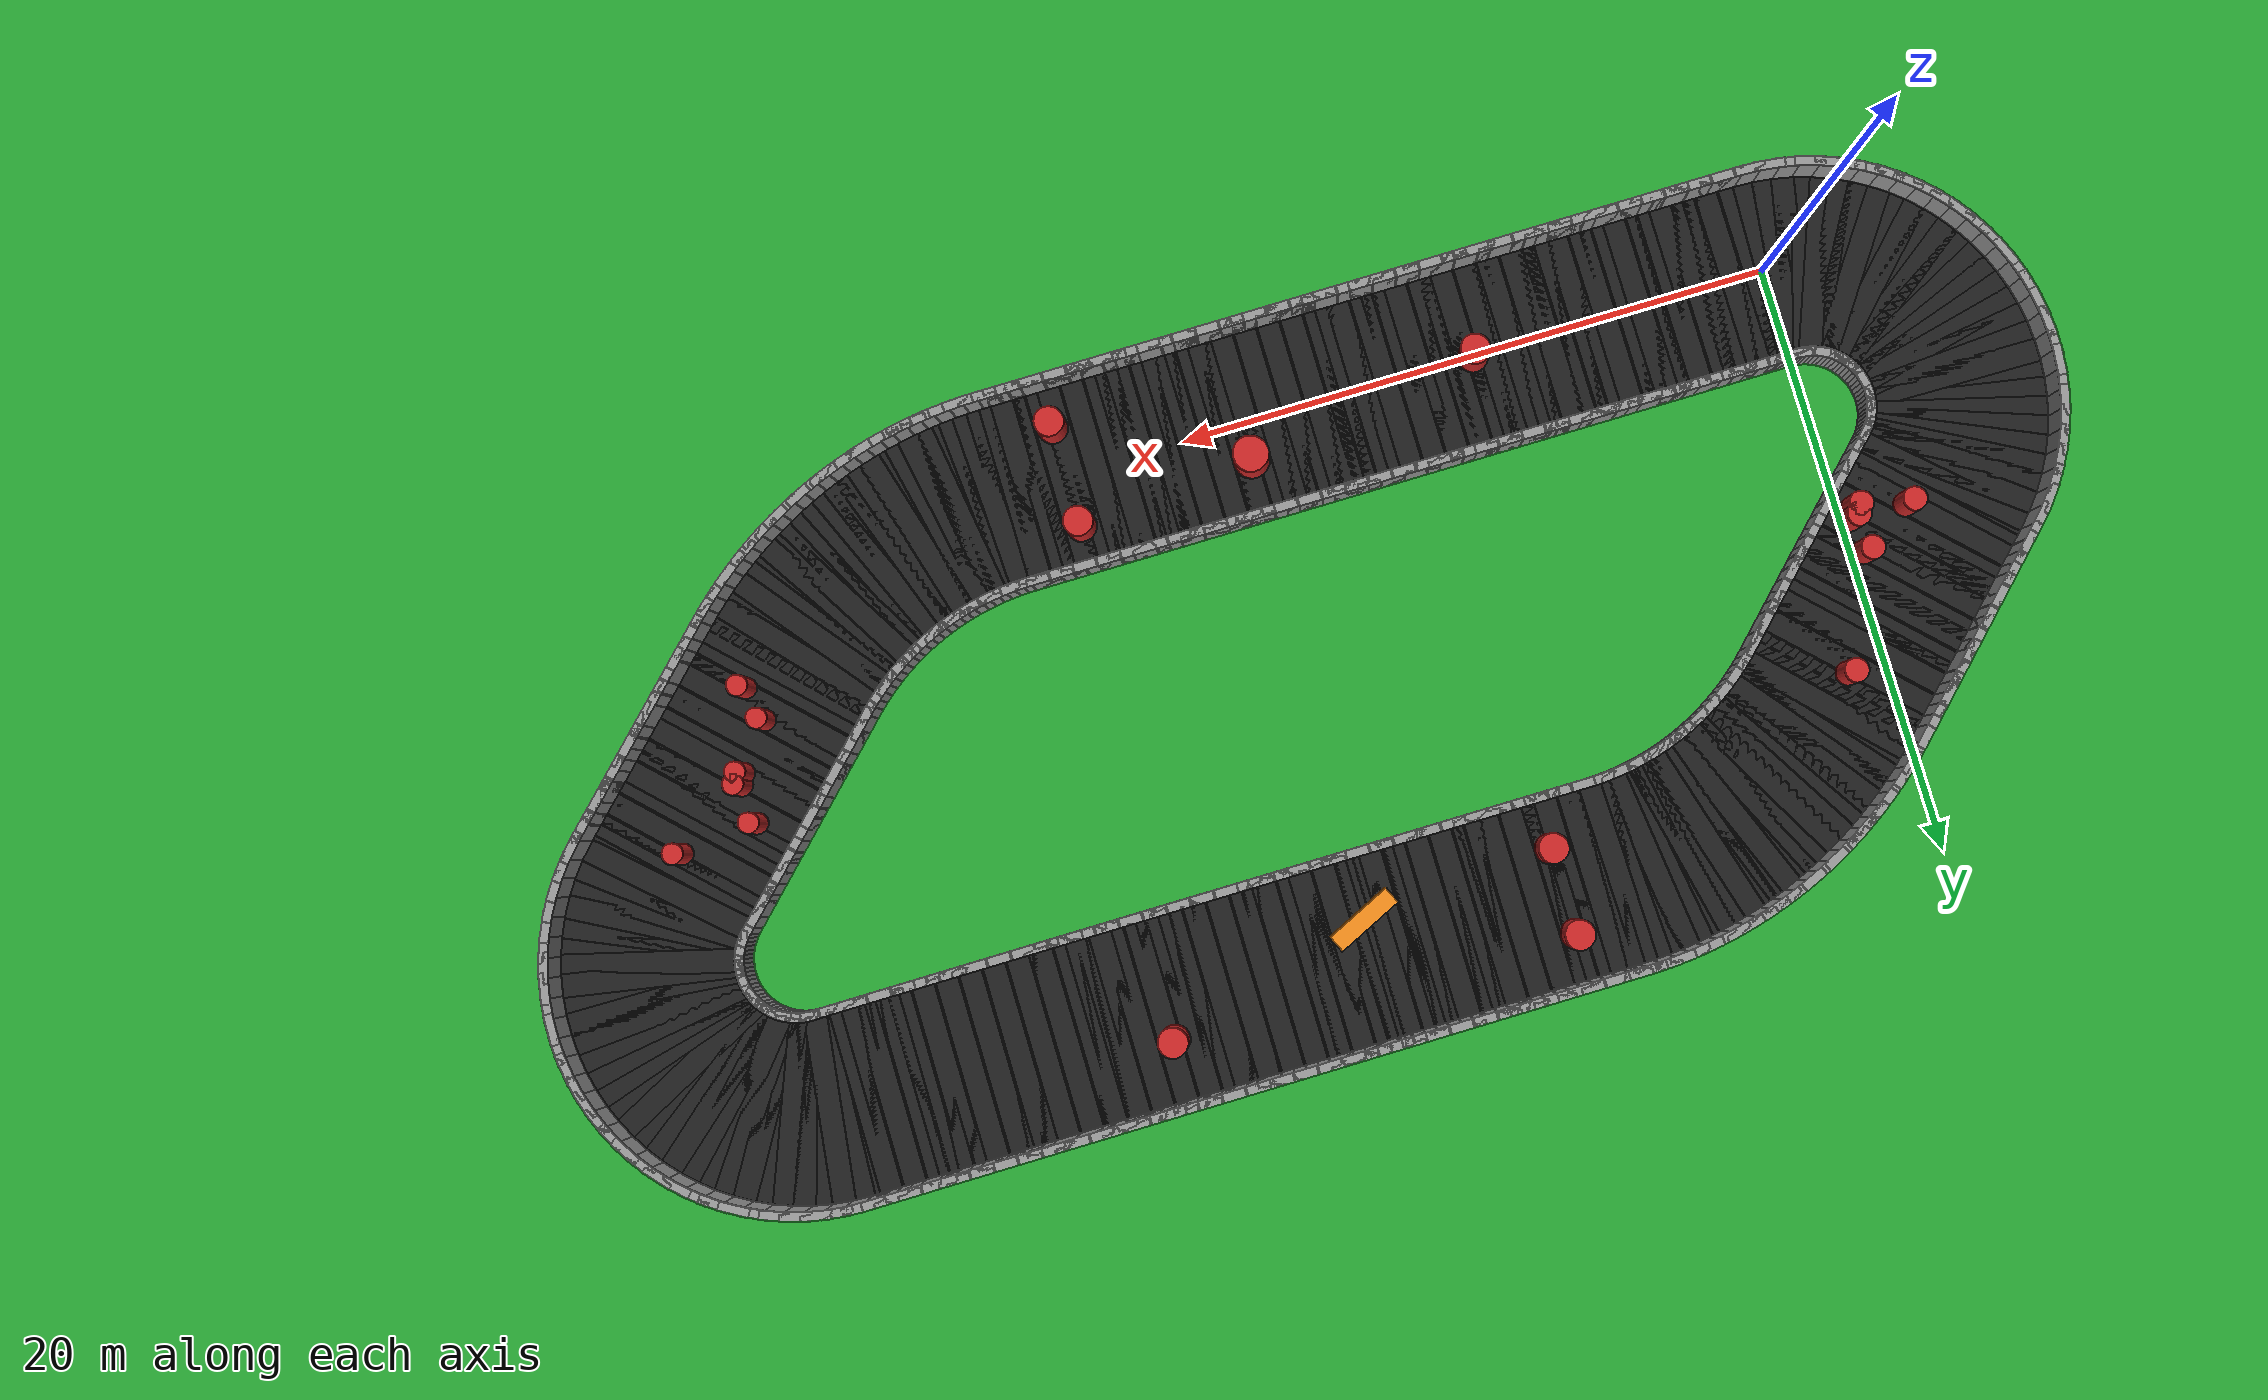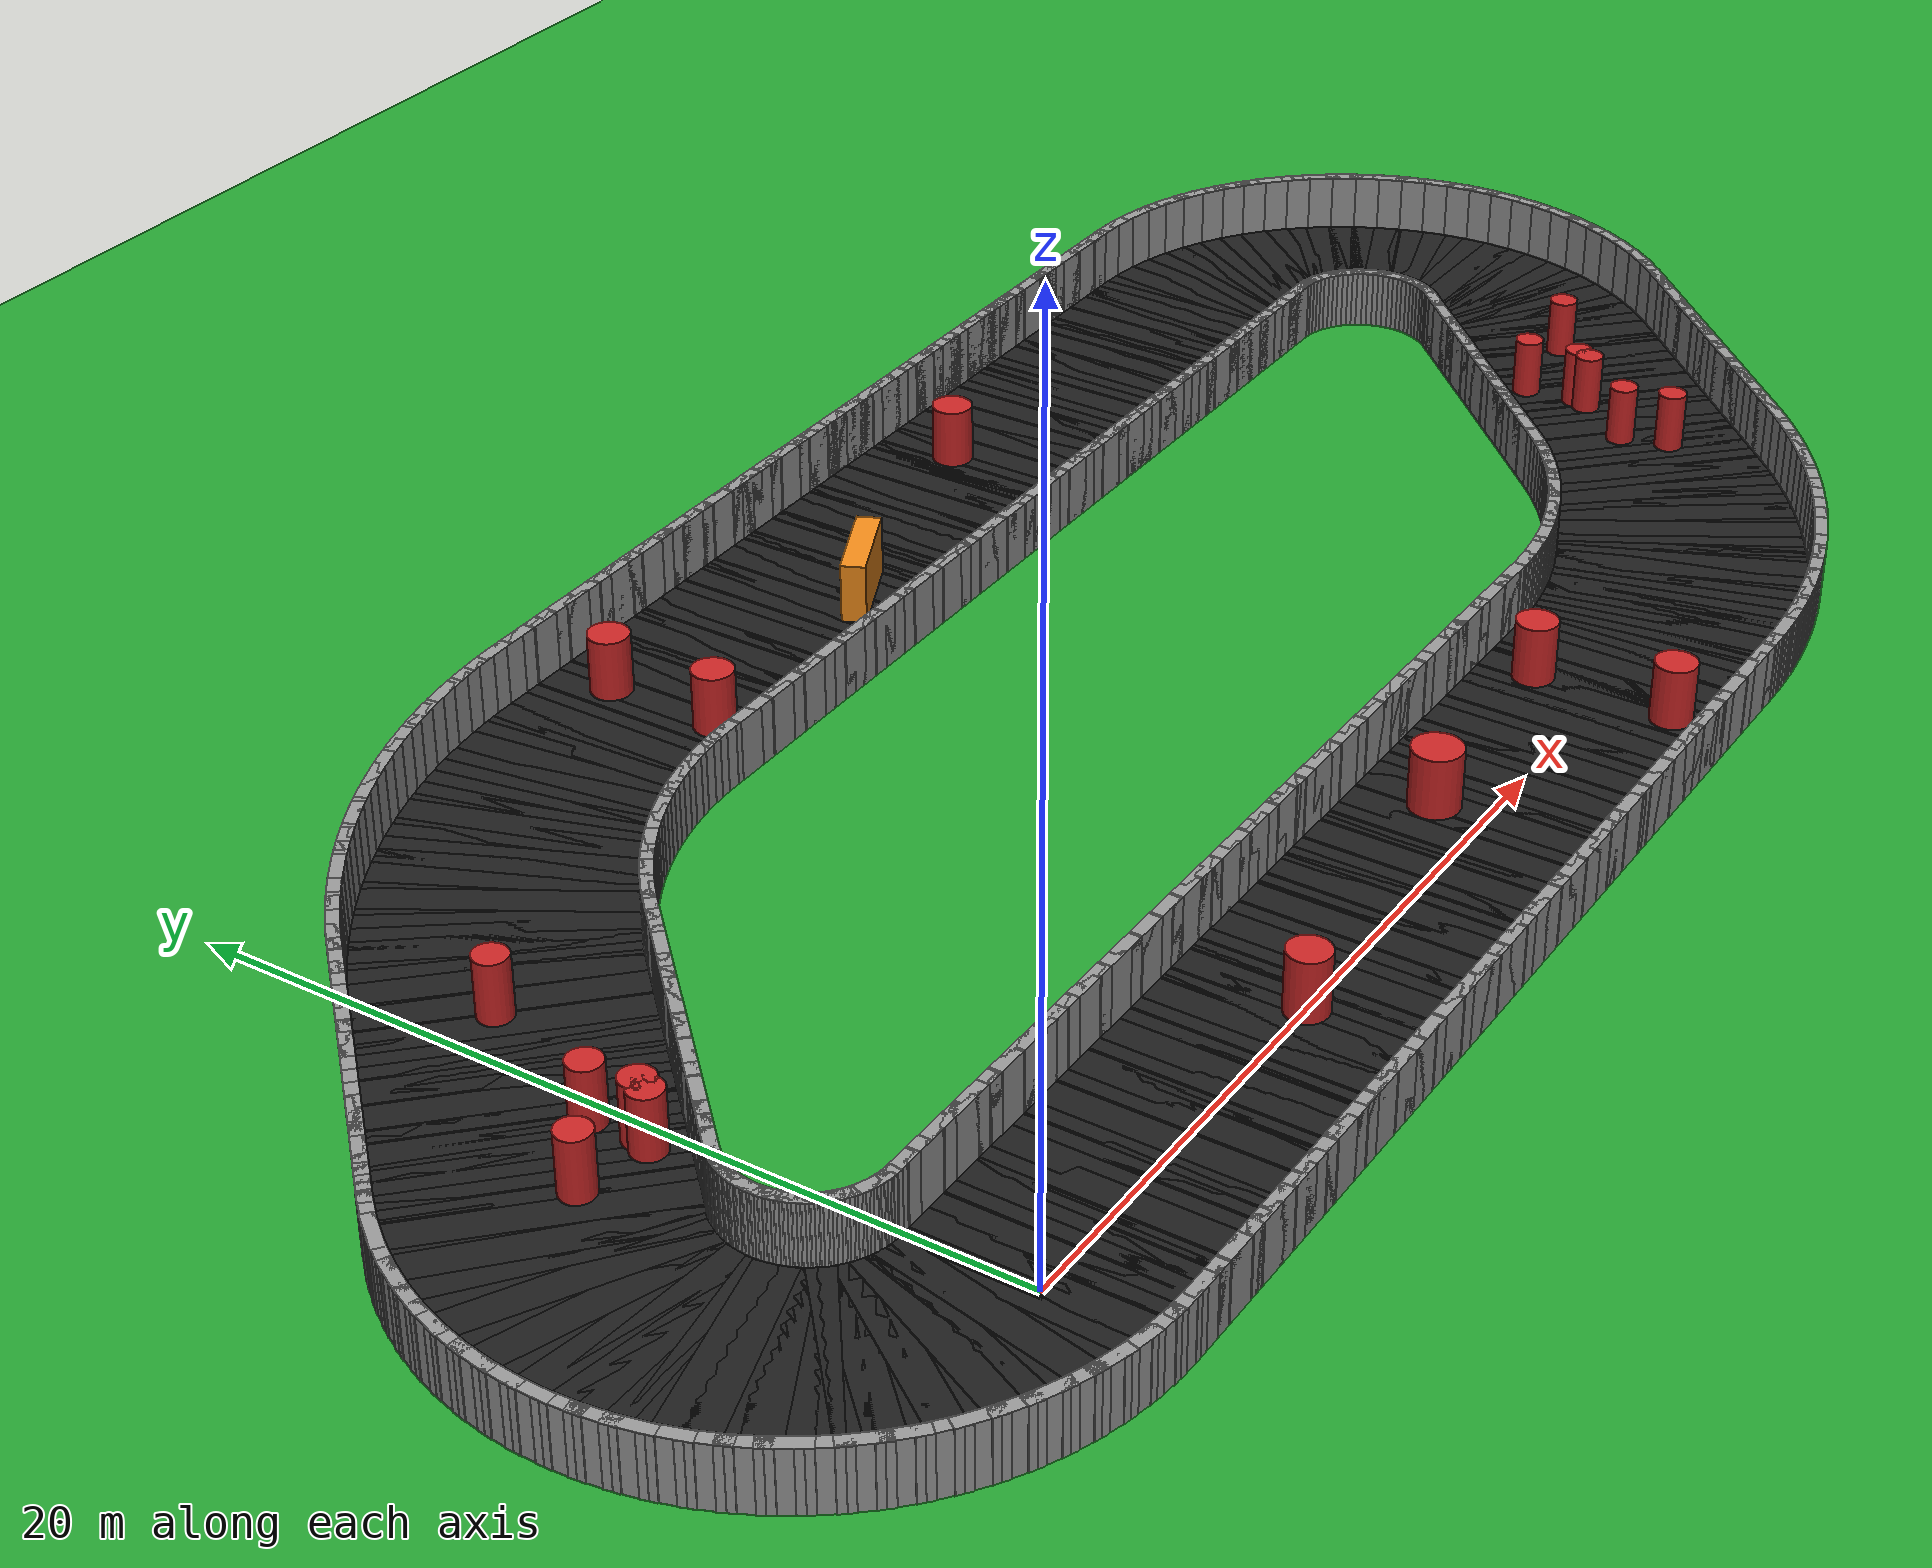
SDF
<?xml version="1.0" ?>
<sdf version="1.6">
  <world name="obstacle_mid">
    <physics type="ode">
      <max_step_size>0.001</max_step_size>
      <real_time_factor>1.0</real_time_factor>
      <real_time_update_rate>1000</real_time_update_rate>
    </physics>
    <include><uri>model://sun</uri></include>

    <model name="ground_plane">
      <static>true</static>
      <link name="link">
        <collision name="collision">
          <surface><friction><ode><mu>100</mu><mu2>50</mu2></ode></friction></surface>
          <geometry><plane><normal>0 0 1</normal>
            <size>120 120</size></plane></geometry>
        </collision>
        <visual name="visual">
          <geometry><plane><normal>0 0 1</normal>
            <size>120 120</size></plane></geometry>
          <material><script>
            <uri>file://media/materials/scripts/gazebo.material</uri>
            <name>Gazebo/Green</name></script></material>
        </visual>
      </link>
    </model>

    <model name="asphalt_0">
      <static>true</static>
      <pose>0.200 0.000 0.005 0 0 0.00000</pose>
      <link name="link">
        <visual name="visual">
          <geometry><box><size>0.760 6.000 0.010</size></box></geometry>
          <material><script><uri>file://media/materials/scripts/gazebo.material</uri><name>Gazebo/Black</name></script></material>
        </visual>
      </link>
    </model>
    <model name="curbL_0">
      <static>true</static>
      <pose>0.200 3.150 0.750 0 0 0.00000</pose>
      <link name="link">
        <collision name="collision">
          <geometry><box><size>0.760 0.300 1.500</size></box></geometry>
        </collision>
        <visual name="visual">
          <geometry><box><size>0.760 0.300 1.500</size></box></geometry>
          <material><script><uri>file://media/materials/scripts/gazebo.material</uri><name>Gazebo/Grey</name></script></material>
        </visual>
      </link>
    </model>
    <model name="curbR_0">
      <static>true</static>
      <pose>0.200 -3.150 0.750 0 0 0.00000</pose>
      <link name="link">
        <collision name="collision">
          <geometry><box><size>0.760 0.300 1.500</size></box></geometry>
        </collision>
        <visual name="visual">
          <geometry><box><size>0.760 0.300 1.500</size></box></geometry>
          <material><script><uri>file://media/materials/scripts/gazebo.material</uri><name>Gazebo/Grey</name></script></material>
        </visual>
      </link>
    </model>
    <model name="asphalt_1">
      <static>true</static>
      <pose>0.600 0.000 0.005 0 0 0.00000</pose>
      <link name="link">
        <visual name="visual">
          <geometry><box><size>0.760 6.000 0.010</size></box></geometry>
          <material><script><uri>file://media/materials/scripts/gazebo.material</uri><name>Gazebo/Black</name></script></material>
        </visual>
      </link>
    </model>
    <model name="curbL_1">
      <static>true</static>
      <pose>0.600 3.150 0.750 0 0 0.00000</pose>
      <link name="link">
        <collision name="collision">
          <geometry><box><size>0.760 0.300 1.500</size></box></geometry>
        </collision>
        <visual name="visual">
          <geometry><box><size>0.760 0.300 1.500</size></box></geometry>
          <material><script><uri>file://media/materials/scripts/gazebo.material</uri><name>Gazebo/Grey</name></script></material>
        </visual>
      </link>
    </model>
    <model name="curbR_1">
      <static>true</static>
      <pose>0.600 -3.150 0.750 0 0 0.00000</pose>
      <link name="link">
        <collision name="collision">
          <geometry><box><size>0.760 0.300 1.500</size></box></geometry>
        </collision>
        <visual name="visual">
          <geometry><box><size>0.760 0.300 1.500</size></box></geometry>
          <material><script><uri>file://media/materials/scripts/gazebo.material</uri><name>Gazebo/Grey</name></script></material>
        </visual>
      </link>
    </model>
    <model name="asphalt_2">
      <static>true</static>
      <pose>1.000 0.000 0.005 0 0 0.00000</pose>
      <link name="link">
        <visual name="visual">
          <geometry><box><size>0.760 6.000 0.010</size></box></geometry>
          <material><script><uri>file://media/materials/scripts/gazebo.material</uri><name>Gazebo/Black</name></script></material>
        </visual>
      </link>
    </model>
    <model name="curbL_2">
      <static>true</static>
      <pose>1.000 3.150 0.750 0 0 0.00000</pose>
      <link name="link">
        <collision name="collision">
          <geometry><box><size>0.760 0.300 1.500</size></box></geometry>
        </collision>
        <visual name="visual">
          <geometry><box><size>0.760 0.300 1.500</size></box></geometry>
          <material><script><uri>file://media/materials/scripts/gazebo.material</uri><name>Gazebo/Grey</name></script></material>
        </visual>
      </link>
    </model>
    <model name="curbR_2">
      <static>true</static>
      <pose>1.000 -3.150 0.750 0 0 0.00000</pose>
      <link name="link">
        <collision name="collision">
          <geometry><box><size>0.760 0.300 1.500</size></box></geometry>
        </collision>
        <visual name="visual">
          <geometry><box><size>0.760 0.300 1.500</size></box></geometry>
          <material><script><uri>file://media/materials/scripts/gazebo.material</uri><name>Gazebo/Grey</name></script></material>
        </visual>
      </link>
    </model>
    <model name="asphalt_3">
      <static>true</static>
      <pose>1.400 0.000 0.005 0 0 0.00000</pose>
      <link name="link">
        <visual name="visual">
          <geometry><box><size>0.760 6.000 0.010</size></box></geometry>
          <material><script><uri>file://media/materials/scripts/gazebo.material</uri><name>Gazebo/Black</name></script></material>
        </visual>
      </link>
    </model>
    <model name="curbL_3">
      <static>true</static>
      <pose>1.400 3.150 0.750 0 0 0.00000</pose>
      <link name="link">
        <collision name="collision">
          <geometry><box><size>0.760 0.300 1.500</size></box></geometry>
        </collision>
        <visual name="visual">
          <geometry><box><size>0.760 0.300 1.500</size></box></geometry>
          <material><script><uri>file://media/materials/scripts/gazebo.material</uri><name>Gazebo/Grey</name></script></material>
        </visual>
      </link>
    </model>
    <model name="curbR_3">
      <static>true</static>
      <pose>1.400 -3.150 0.750 0 0 0.00000</pose>
      <link name="link">
        <collision name="collision">
          <geometry><box><size>0.760 0.300 1.500</size></box></geometry>
        </collision>
        <visual name="visual">
          <geometry><box><size>0.760 0.300 1.500</size></box></geometry>
          <material><script><uri>file://media/materials/scripts/gazebo.material</uri><name>Gazebo/Grey</name></script></material>
        </visual>
      </link>
    </model>
    <model name="asphalt_4">
      <static>true</static>
      <pose>1.800 0.000 0.005 0 0 0.00000</pose>
      <link name="link">
        <visual name="visual">
          <geometry><box><size>0.760 6.000 0.010</size></box></geometry>
          <material><script><uri>file://media/materials/scripts/gazebo.material</uri><name>Gazebo/Black</name></script></material>
        </visual>
      </link>
    </model>
    <model name="curbL_4">
      <static>true</static>
      <pose>1.800 3.150 0.750 0 0 0.00000</pose>
      <link name="link">
        <collision name="collision">
          <geometry><box><size>0.760 0.300 1.500</size></box></geometry>
        </collision>
        <visual name="visual">
          <geometry><box><size>0.760 0.300 1.500</size></box></geometry>
          <material><script><uri>file://media/materials/scripts/gazebo.material</uri><name>Gazebo/Grey</name></script></material>
        </visual>
      </link>
    </model>
    <model name="curbR_4">
      <static>true</static>
      <pose>1.800 -3.150 0.750 0 0 0.00000</pose>
      <link name="link">
        <collision name="collision">
          <geometry><box><size>0.760 0.300 1.500</size></box></geometry>
        </collision>
        <visual name="visual">
          <geometry><box><size>0.760 0.300 1.500</size></box></geometry>
          <material><script><uri>file://media/materials/scripts/gazebo.material</uri><name>Gazebo/Grey</name></script></material>
        </visual>
      </link>
    </model>
    <model name="asphalt_5">
      <static>true</static>
      <pose>2.200 0.000 0.005 0 0 0.00000</pose>
      <link name="link">
        <visual name="visual">
          <geometry><box><size>0.760 6.000 0.010</size></box></geometry>
          <material><script><uri>file://media/materials/scripts/gazebo.material</uri><name>Gazebo/Black</name></script></material>
        </visual>
      </link>
    </model>
    <model name="curbL_5">
      <static>true</static>
      <pose>2.200 3.150 0.750 0 0 0.00000</pose>
      <link name="link">
        <collision name="collision">
          <geometry><box><size>0.760 0.300 1.500</size></box></geometry>
        </collision>
        <visual name="visual">
          <geometry><box><size>0.760 0.300 1.500</size></box></geometry>
          <material><script><uri>file://media/materials/scripts/gazebo.material</uri><name>Gazebo/Grey</name></script></material>
        </visual>
      </link>
    </model>
    <model name="curbR_5">
      <static>true</static>
      <pose>2.200 -3.150 0.750 0 0 0.00000</pose>
      <link name="link">
        <collision name="collision">
          <geometry><box><size>0.760 0.300 1.500</size></box></geometry>
        </collision>
        <visual name="visual">
          <geometry><box><size>0.760 0.300 1.500</size></box></geometry>
          <material><script><uri>file://media/materials/scripts/gazebo.material</uri><name>Gazebo/Grey</name></script></material>
        </visual>
      </link>
    </model>
    <model name="asphalt_6">
      <static>true</static>
      <pose>2.600 0.000 0.005 0 0 0.00000</pose>
      <link name="link">
        <visual name="visual">
          <geometry><box><size>0.760 6.000 0.010</size></box></geometry>
          <material><script><uri>file://media/materials/scripts/gazebo.material</uri><name>Gazebo/Black</name></script></material>
        </visual>
      </link>
    </model>
    <model name="curbL_6">
      <static>true</static>
      <pose>2.600 3.150 0.750 0 0 0.00000</pose>
      <link name="link">
        <collision name="collision">
          <geometry><box><size>0.760 0.300 1.500</size></box></geometry>
        </collision>
        <visual name="visual">
          <geometry><box><size>0.760 0.300 1.500</size></box></geometry>
          <material><script><uri>file://media/materials/scripts/gazebo.material</uri><name>Gazebo/Grey</name></script></material>
        </visual>
      </link>
    </model>
    <model name="curbR_6">
      <static>true</static>
      <pose>2.600 -3.150 0.750 0 0 0.00000</pose>
      <link name="link">
        <collision name="collision">
          <geometry><box><size>0.760 0.300 1.500</size></box></geometry>
        </collision>
        <visual name="visual">
          <geometry><box><size>0.760 0.300 1.500</size></box></geometry>
          <material><script><uri>file://media/materials/scripts/gazebo.material</uri><name>Gazebo/Grey</name></script></material>
        </visual>
      </link>
    </model>
    <model name="asphalt_7">
      <static>true</static>
      <pose>3.000 0.000 0.005 0 0 0.00000</pose>
      <link name="link">
        <visual name="visual">
          <geometry><box><size>0.760 6.000 0.010</size></box></geometry>
          <material><script><uri>file://media/materials/scripts/gazebo.material</uri><name>Gazebo/Black</name></script></material>
        </visual>
      </link>
    </model>
    <model name="curbL_7">
      <static>true</static>
      <pose>3.000 3.150 0.750 0 0 0.00000</pose>
      <link name="link">
        <collision name="collision">
          <geometry><box><size>0.760 0.300 1.500</size></box></geometry>
        </collision>
        <visual name="visual">
          <geometry><box><size>0.760 0.300 1.500</size></box></geometry>
          <material><script><uri>file://media/materials/scripts/gazebo.material</uri><name>Gazebo/Grey</name></script></material>
        </visual>
      </link>
    </model>
    <model name="curbR_7">
      <static>true</static>
      <pose>3.000 -3.150 0.750 0 0 0.00000</pose>
      <link name="link">
        <collision name="collision">
          <geometry><box><size>0.760 0.300 1.500</size></box></geometry>
        </collision>
        <visual name="visual">
          <geometry><box><size>0.760 0.300 1.500</size></box></geometry>
          <material><script><uri>file://media/materials/scripts/gazebo.material</uri><name>Gazebo/Grey</name></script></material>
        </visual>
      </link>
    </model>
    <model name="asphalt_8">
      <static>true</static>
      <pose>3.400 0.000 0.005 0 0 0.00000</pose>
      <link name="link">
        <visual name="visual">
          <geometry><box><size>0.760 6.000 0.010</size></box></geometry>
          <material><script><uri>file://media/materials/scripts/gazebo.material</uri><name>Gazebo/Black</name></script></material>
        </visual>
      </link>
    </model>
    <model name="curbL_8">
      <static>true</static>
      <pose>3.400 3.150 0.750 0 0 0.00000</pose>
      <link name="link">
        <collision name="collision">
          <geometry><box><size>0.760 0.300 1.500</size></box></geometry>
        </collision>
        <visual name="visual">
          <geometry><box><size>0.760 0.300 1.500</size></box></geometry>
          <material><script><uri>file://media/materials/scripts/gazebo.material</uri><name>Gazebo/Grey</name></script></material>
        </visual>
      </link>
    </model>
    <model name="curbR_8">
      <static>true</static>
      <pose>3.400 -3.150 0.750 0 0 0.00000</pose>
      <link name="link">
        <collision name="collision">
          <geometry><box><size>0.760 0.300 1.500</size></box></geometry>
        </collision>
        <visual name="visual">
          <geometry><box><size>0.760 0.300 1.500</size></box></geometry>
          <material><script><uri>file://media/materials/scripts/gazebo.material</uri><name>Gazebo/Grey</name></script></material>
        </visual>
      </link>
    </model>
    <model name="asphalt_9">
      <static>true</static>
      <pose>3.800 0.000 0.005 0 0 0.00000</pose>
      <link name="link">
        <visual name="visual">
          <geometry><box><size>0.760 6.000 0.010</size></box></geometry>
          <material><script><uri>file://media/materials/scripts/gazebo.material</uri><name>Gazebo/Black</name></script></material>
        </visual>
      </link>
    </model>
    <model name="curbL_9">
      <static>true</static>
      <pose>3.800 3.150 0.750 0 0 0.00000</pose>
      <link name="link">
        <collision name="collision">
          <geometry><box><size>0.760 0.300 1.500</size></box></geometry>
        </collision>
        <visual name="visual">
          <geometry><box><size>0.760 0.300 1.500</size></box></geometry>
          <material><script><uri>file://media/materials/scripts/gazebo.material</uri><name>Gazebo/Grey</name></script></material>
        </visual>
      </link>
    </model>
    <model name="curbR_9">
      <static>true</static>
      <pose>3.800 -3.150 0.750 0 0 0.00000</pose>
      <link name="link">
        <collision name="collision">
          <geometry><box><size>0.760 0.300 1.500</size></box></geometry>
        </collision>
        <visual name="visual">
          <geometry><box><size>0.760 0.300 1.500</size></box></geometry>
          <material><script><uri>file://media/materials/scripts/gazebo.material</uri><name>Gazebo/Grey</name></script></material>
        </visual>
      </link>
    </model>
    <model name="asphalt_10">
      <static>true</static>
      <pose>4.200 0.000 0.005 0 0 0.00000</pose>
      <link name="link">
        <visual name="visual">
          <geometry><box><size>0.760 6.000 0.010</size></box></geometry>
          <material><script><uri>file://media/materials/scripts/gazebo.material</uri><name>Gazebo/Black</name></script></material>
        </visual>
      </link>
    </model>
    <model name="curbL_10">
      <static>true</static>
      <pose>4.200 3.150 0.750 0 0 0.00000</pose>
      <link name="link">
        <collision name="collision">
          <geometry><box><size>0.760 0.300 1.500</size></box></geometry>
        </collision>
        <visual name="visual">
          <geometry><box><size>0.760 0.300 1.500</size></box></geometry>
          <material><script><uri>file://media/materials/scripts/gazebo.material</uri><name>Gazebo/Grey</name></script></material>
        </visual>
      </link>
    </model>
    <model name="curbR_10">
      <static>true</static>
      <pose>4.200 -3.150 0.750 0 0 0.00000</pose>
      <link name="link">
        <collision name="collision">
          <geometry><box><size>0.760 0.300 1.500</size></box></geometry>
        </collision>
        <visual name="visual">
          <geometry><box><size>0.760 0.300 1.500</size></box></geometry>
          <material><script><uri>file://media/materials/scripts/gazebo.material</uri><name>Gazebo/Grey</name></script></material>
        </visual>
      </link>
    </model>
    <model name="asphalt_11">
      <static>true</static>
      <pose>4.600 0.000 0.005 0 0 0.00000</pose>
      <link name="link">
        <visual name="visual">
          <geometry><box><size>0.760 6.000 0.010</size></box></geometry>
          <material><script><uri>file://media/materials/scripts/gazebo.material</uri><name>Gazebo/Black</name></script></material>
        </visual>
      </link>
    </model>
    <model name="curbL_11">
      <static>true</static>
      <pose>4.600 3.150 0.750 0 0 0.00000</pose>
      <link name="link">
        <collision name="collision">
          <geometry><box><size>0.760 0.300 1.500</size></box></geometry>
        </collision>
        <visual name="visual">
          <geometry><box><size>0.760 0.300 1.500</size></box></geometry>
          <material><script><uri>file://media/materials/scripts/gazebo.material</uri><name>Gazebo/Grey</name></script></material>
        </visual>
      </link>
    </model>
    <model name="curbR_11">
      <static>true</static>
      <pose>4.600 -3.150 0.750 0 0 0.00000</pose>
      <link name="link">
        <collision name="collision">
          <geometry><box><size>0.760 0.300 1.500</size></box></geometry>
        </collision>
        <visual name="visual">
          <geometry><box><size>0.760 0.300 1.500</size></box></geometry>
          <material><script><uri>file://media/materials/scripts/gazebo.material</uri><name>Gazebo/Grey</name></script></material>
        </visual>
      </link>
    </model>
    <model name="asphalt_12">
      <static>true</static>
      <pose>5.000 0.000 0.005 0 0 0.00000</pose>
      <link name="link">
        <visual name="visual">
          <geometry><box><size>0.760 6.000 0.010</size></box></geometry>
          <material><script><uri>file://media/materials/scripts/gazebo.material</uri><name>Gazebo/Black</name></script></material>
        </visual>
      </link>
    </model>
    <model name="curbL_12">
      <static>true</static>
      <pose>5.000 3.150 0.750 0 0 0.00000</pose>
      <link name="link">
        <collision name="collision">
          <geometry><box><size>0.760 0.300 1.500</size></box></geometry>
        </collision>
        <visual name="visual">
          <geometry><box><size>0.760 0.300 1.500</size></box></geometry>
          <material><script><uri>file://media/materials/scripts/gazebo.material</uri><name>Gazebo/Grey</name></script></material>
        </visual>
      </link>
    </model>
    <model name="curbR_12">
      <static>true</static>
      <pose>5.000 -3.150 0.750 0 0 0.00000</pose>
      <link name="link">
        <collision name="collision">
          <geometry><box><size>0.760 0.300 1.500</size></box></geometry>
        </collision>
        <visual name="visual">
          <geometry><box><size>0.760 0.300 1.500</size></box></geometry>
          <material><script><uri>file://media/materials/scripts/gazebo.material</uri><name>Gazebo/Grey</name></script></material>
        </visual>
      </link>
    </model>
    <model name="asphalt_13">
      <static>true</static>
      <pose>5.400 0.000 0.005 0 0 0.00000</pose>
      <link name="link">
        <visual name="visual">
          <geometry><box><size>0.760 6.000 0.010</size></box></geometry>
          <material><script><uri>file://media/materials/scripts/gazebo.material</uri><name>Gazebo/Black</name></script></material>
        </visual>
      </link>
    </model>
    <model name="curbL_13">
      <static>true</static>
      <pose>5.400 3.150 0.750 0 0 0.00000</pose>
      <link name="link">
        <collision name="collision">
          <geometry><box><size>0.760 0.300 1.500</size></box></geometry>
        </collision>
        <visual name="visual">
          <geometry><box><size>0.760 0.300 1.500</size></box></geometry>
          <material><script><uri>file://media/materials/scripts/gazebo.material</uri><name>Gazebo/Grey</name></script></material>
        </visual>
      </link>
    </model>
    <model name="curbR_13">
      <static>true</static>
      <pose>5.400 -3.150 0.750 0 0 0.00000</pose>
      <link name="link">
        <collision name="collision">
          <geometry><box><size>0.760 0.300 1.500</size></box></geometry>
        </collision>
        <visual name="visual">
          <geometry><box><size>0.760 0.300 1.500</size></box></geometry>
          <material><script><uri>file://media/materials/scripts/gazebo.material</uri><name>Gazebo/Grey</name></script></material>
        </visual>
      </link>
    </model>
    <model name="asphalt_14">
      <static>true</static>
      <pose>5.800 0.000 0.005 0 0 0.00000</pose>
      <link name="link">
        <visual name="visual">
          <geometry><box><size>0.760 6.000 0.010</size></box></geometry>
          <material><script><uri>file://media/materials/scripts/gazebo.material</uri><name>Gazebo/Black</name></script></material>
        </visual>
      </link>
    </model>
    <model name="curbL_14">
      <static>true</static>
      <pose>5.800 3.150 0.750 0 0 0.00000</pose>
      <link name="link">
        <collision name="collision">
          <geometry><box><size>0.760 0.300 1.500</size></box></geometry>
        </collision>
        <visual name="visual">
          <geometry><box><size>0.760 0.300 1.500</size></box></geometry>
          <material><script><uri>file://media/materials/scripts/gazebo.material</uri><name>Gazebo/Grey</name></script></material>
        </visual>
      </link>
    </model>
    <model name="curbR_14">
      <static>true</static>
      <pose>5.800 -3.150 0.750 0 0 0.00000</pose>
      <link name="link">
        <collision name="collision">
          <geometry><box><size>0.760 0.300 1.500</size></box></geometry>
        </collision>
        <visual name="visual">
          <geometry><box><size>0.760 0.300 1.500</size></box></geometry>
          <material><script><uri>file://media/materials/scripts/gazebo.material</uri><name>Gazebo/Grey</name></script></material>
        </visual>
      </link>
    </model>
    <model name="asphalt_15">
      <static>true</static>
      <pose>6.200 0.000 0.005 0 0 0.00000</pose>
      <link name="link">
        <visual name="visual">
          <geometry><box><size>0.760 6.000 0.010</size></box></geometry>
          <material><script><uri>file://media/materials/scripts/gazebo.material</uri><name>Gazebo/Black</name></script></material>
        </visual>
      </link>
    </model>
    <model name="curbL_15">
      <static>true</static>
      <pose>6.200 3.150 0.750 0 0 0.00000</pose>
      <link name="link">
        <collision name="collision">
          <geometry><box><size>0.760 0.300 1.500</size></box></geometry>
        </collision>
        <visual name="visual">
          <geometry><box><size>0.760 0.300 1.500</size></box></geometry>
          <material><script><uri>file://media/materials/scripts/gazebo.material</uri><name>Gazebo/Grey</name></script></material>
        </visual>
      </link>
    </model>
    <model name="curbR_15">
      <static>true</static>
      <pose>6.200 -3.150 0.750 0 0 0.00000</pose>
      <link name="link">
        <collision name="collision">
          <geometry><box><size>0.760 0.300 1.500</size></box></geometry>
        </collision>
        <visual name="visual">
          <geometry><box><size>0.760 0.300 1.500</size></box></geometry>
          <material><script><uri>file://media/materials/scripts/gazebo.material</uri><name>Gazebo/Grey</name></script></material>
        </visual>
      </link>
    </model>
    <model name="asphalt_16">
      <static>true</static>
      <pose>6.600 0.000 0.005 0 0 0.00000</pose>
      <link name="link">
        <visual name="visual">
          <geometry><box><size>0.760 6.000 0.010</size></box></geometry>
          <material><script><uri>file://media/materials/scripts/gazebo.material</uri><name>Gazebo/Black</name></script></material>
        </visual>
      </link>
    </model>
    <model name="curbL_16">
      <static>true</static>
      <pose>6.600 3.150 0.750 0 0 0.00000</pose>
      <link name="link">
        <collision name="collision">
          <geometry><box><size>0.760 0.300 1.500</size></box></geometry>
        </collision>
        <visual name="visual">
          <geometry><box><size>0.760 0.300 1.500</size></box></geometry>
          <material><script><uri>file://media/materials/scripts/gazebo.material</uri><name>Gazebo/Grey</name></script></material>
        </visual>
      </link>
    </model>
    <model name="curbR_16">
      <static>true</static>
      <pose>6.600 -3.150 0.750 0 0 0.00000</pose>
      <link name="link">
        <collision name="collision">
          <geometry><box><size>0.760 0.300 1.500</size></box></geometry>
        </collision>
        <visual name="visual">
          <geometry><box><size>0.760 0.300 1.500</size></box></geometry>
          <material><script><uri>file://media/materials/scripts/gazebo.material</uri><name>Gazebo/Grey</name></script></material>
        </visual>
      </link>
    </model>
    <model name="asphalt_17">
      <static>true</static>
      <pose>7.000 0.000 0.005 0 0 0.00000</pose>
      <link name="link">
        <visual name="visual">
          <geometry><box><size>0.760 6.000 0.010</size></box></geometry>
          <material><script><uri>file://media/materials/scripts/gazebo.material</uri><name>Gazebo/Black</name></script></material>
        </visual>
      </link>
    </model>
    <model name="curbL_17">
      <static>true</static>
      <pose>7.000 3.150 0.750 0 0 0.00000</pose>
      <link name="link">
        <collision name="collision">
          <geometry><box><size>0.760 0.300 1.500</size></box></geometry>
        </collision>
        <visual name="visual">
          <geometry><box><size>0.760 0.300 1.500</size></box></geometry>
          <material><script><uri>file://media/materials/scripts/gazebo.material</uri><name>Gazebo/Grey</name></script></material>
        </visual>
      </link>
    </model>
    <model name="curbR_17">
      <static>true</static>
      <pose>7.000 -3.150 0.750 0 0 0.00000</pose>
      <link name="link">
        <collision name="collision">
          <geometry><box><size>0.760 0.300 1.500</size></box></geometry>
        </collision>
        <visual name="visual">
          <geometry><box><size>0.760 0.300 1.500</size></box></geometry>
          <material><script><uri>file://media/materials/scripts/gazebo.material</uri><name>Gazebo/Grey</name></script></material>
        </visual>
      </link>
    </model>
    <model name="asphalt_18">
      <static>true</static>
      <pose>7.400 0.000 0.005 0 0 0.00000</pose>
      <link name="link">
        <visual name="visual">
          <geometry><box><size>0.760 6.000 0.010</size></box></geometry>
          <material><script><uri>file://media/materials/scripts/gazebo.material</uri><name>Gazebo/Black</name></script></material>
        </visual>
      </link>
    </model>
    <model name="curbL_18">
      <static>true</static>
      <pose>7.400 3.150 0.750 0 0 0.00000</pose>
      <link name="link">
        <collision name="collision">
          <geometry><box><size>0.760 0.300 1.500</size></box></geometry>
        </collision>
        <visual name="visual">
          <geometry><box><size>0.760 0.300 1.500</size></box></geometry>
          <material><script><uri>file://media/materials/scripts/gazebo.material</uri><name>Gazebo/Grey</name></script></material>
        </visual>
      </link>
    </model>
    <model name="curbR_18">
      <static>true</static>
      <pose>7.400 -3.150 0.750 0 0 0.00000</pose>
      <link name="link">
        <collision name="collision">
          <geometry><box><size>0.760 0.300 1.500</size></box></geometry>
        </collision>
        <visual name="visual">
          <geometry><box><size>0.760 0.300 1.500</size></box></geometry>
          <material><script><uri>file://media/materials/scripts/gazebo.material</uri><name>Gazebo/Grey</name></script></material>
        </visual>
      </link>
    </model>
    <model name="asphalt_19">
      <static>true</static>
      <pose>7.800 0.000 0.005 0 0 0.00000</pose>
      <link name="link">
        <visual name="visual">
          <geometry><box><size>0.760 6.000 0.010</size></box></geometry>
          <material><script><uri>file://media/materials/scripts/gazebo.material</uri><name>Gazebo/Black</name></script></material>
        </visual>
      </link>
    </model>
    <model name="curbL_19">
      <static>true</static>
      <pose>7.800 3.150 0.750 0 0 0.00000</pose>
      <link name="link">
        <collision name="collision">
          <geometry><box><size>0.760 0.300 1.500</size></box></geometry>
        </collision>
        <visual name="visual">
          <geometry><box><size>0.760 0.300 1.500</size></box></geometry>
          <material><script><uri>file://media/materials/scripts/gazebo.material</uri><name>Gazebo/Grey</name></script></material>
        </visual>
      </link>
    </model>
    <model name="curbR_19">
      <static>true</static>
      <pose>7.800 -3.150 0.750 0 0 0.00000</pose>
      <link name="link">
        <collision name="collision">
          <geometry><box><size>0.760 0.300 1.500</size></box></geometry>
        </collision>
        <visual name="visual">
          <geometry><box><size>0.760 0.300 1.500</size></box></geometry>
          <material><script><uri>file://media/materials/scripts/gazebo.material</uri><name>Gazebo/Grey</name></script></material>
        </visual>
      </link>
    </model>
    <model name="asphalt_20">
      <static>true</static>
      <pose>8.200 0.000 0.005 0 0 0.00000</pose>
      <link name="link">
        <visual name="visual">
          <geometry><box><size>0.760 6.000 0.010</size></box></geometry>
          <material><script><uri>file://media/materials/scripts/gazebo.material</uri><name>Gazebo/Black</name></script></material>
        </visual>
      </link>
    </model>
    <model name="curbL_20">
      <static>true</static>
      <pose>8.200 3.150 0.750 0 0 0.00000</pose>
      <link name="link">
        <collision name="collision">
          <geometry><box><size>0.760 0.300 1.500</size></box></geometry>
        </collision>
        <visual name="visual">
          <geometry><box><size>0.760 0.300 1.500</size></box></geometry>
          <material><script><uri>file://media/materials/scripts/gazebo.material</uri><name>Gazebo/Grey</name></script></material>
        </visual>
      </link>
    </model>
    <model name="curbR_20">
      <static>true</static>
      <pose>8.200 -3.150 0.750 0 0 0.00000</pose>
      <link name="link">
        <collision name="collision">
          <geometry><box><size>0.760 0.300 1.500</size></box></geometry>
        </collision>
        <visual name="visual">
          <geometry><box><size>0.760 0.300 1.500</size></box></geometry>
          <material><script><uri>file://media/materials/scripts/gazebo.material</uri><name>Gazebo/Grey</name></script></material>
        </visual>
      </link>
    </model>
    <model name="asphalt_21">
      <static>true</static>
      <pose>8.600 0.000 0.005 0 0 0.00000</pose>
      <link name="link">
        <visual name="visual">
          <geometry><box><size>0.760 6.000 0.010</size></box></geometry>
          <material><script><uri>file://media/materials/scripts/gazebo.material</uri><name>Gazebo/Black</name></script></material>
        </visual>
      </link>
    </model>
    <model name="curbL_21">
      <static>true</static>
      <pose>8.600 3.150 0.750 0 0 0.00000</pose>
      <link name="link">
        <collision name="collision">
          <geometry><box><size>0.760 0.300 1.500</size></box></geometry>
        </collision>
        <visual name="visual">
          <geometry><box><size>0.760 0.300 1.500</size></box></geometry>
          <material><script><uri>file://media/materials/scripts/gazebo.material</uri><name>Gazebo/Grey</name></script></material>
        </visual>
      </link>
    </model>
    <model name="curbR_21">
      <static>true</static>
      <pose>8.600 -3.150 0.750 0 0 0.00000</pose>
      <link name="link">
        <collision name="collision">
          <geometry><box><size>0.760 0.300 1.500</size></box></geometry>
        </collision>
        <visual name="visual">
          <geometry><box><size>0.760 0.300 1.500</size></box></geometry>
          <material><script><uri>file://media/materials/scripts/gazebo.material</uri><name>Gazebo/Grey</name></script></material>
        </visual>
      </link>
    </model>
    <model name="asphalt_22">
      <static>true</static>
      <pose>9.000 0.000 0.005 0 0 0.00000</pose>
      <link name="link">
        <visual name="visual">
          <geometry><box><size>0.760 6.000 0.010</size></box></geometry>
          <material><script><uri>file://media/materials/scripts/gazebo.material</uri><name>Gazebo/Black</name></script></material>
        </visual>
      </link>
    </model>
    <model name="curbL_22">
      <static>true</static>
      <pose>9.000 3.150 0.750 0 0 0.00000</pose>
      <link name="link">
        <collision name="collision">
          <geometry><box><size>0.760 0.300 1.500</size></box></geometry>
        </collision>
        <visual name="visual">
          <geometry><box><size>0.760 0.300 1.500</size></box></geometry>
          <material><script><uri>file://media/materials/scripts/gazebo.material</uri><name>Gazebo/Grey</name></script></material>
        </visual>
      </link>
    </model>
    <model name="curbR_22">
      <static>true</static>
      <pose>9.000 -3.150 0.750 0 0 0.00000</pose>
      <link name="link">
        <collision name="collision">
          <geometry><box><size>0.760 0.300 1.500</size></box></geometry>
        </collision>
        <visual name="visual">
          <geometry><box><size>0.760 0.300 1.500</size></box></geometry>
          <material><script><uri>file://media/materials/scripts/gazebo.material</uri><name>Gazebo/Grey</name></script></material>
        </visual>
      </link>
    </model>
    <model name="asphalt_23">
      <static>true</static>
      <pose>9.400 0.000 0.005 0 0 0.00000</pose>
      <link name="link">
        <visual name="visual">
          <geometry><box><size>0.760 6.000 0.010</size></box></geometry>
          <material><script><uri>file://media/materials/scripts/gazebo.material</uri><name>Gazebo/Black</name></script></material>
        </visual>
      </link>
    </model>
    <model name="curbL_23">
      <static>true</static>
      <pose>9.400 3.150 0.750 0 0 0.00000</pose>
      <link name="link">
        <collision name="collision">
          <geometry><box><size>0.760 0.300 1.500</size></box></geometry>
        </collision>
        <visual name="visual">
          <geometry><box><size>0.760 0.300 1.500</size></box></geometry>
          <material><script><uri>file://media/materials/scripts/gazebo.material</uri><name>Gazebo/Grey</name></script></material>
        </visual>
      </link>
    </model>
    <model name="curbR_23">
      <static>true</static>
      <pose>9.400 -3.150 0.750 0 0 0.00000</pose>
      <link name="link">
        <collision name="collision">
          <geometry><box><size>0.760 0.300 1.500</size></box></geometry>
        </collision>
        <visual name="visual">
          <geometry><box><size>0.760 0.300 1.500</size></box></geometry>
          <material><script><uri>file://media/materials/scripts/gazebo.material</uri><name>Gazebo/Grey</name></script></material>
        </visual>
      </link>
    </model>
    <model name="asphalt_24">
      <static>true</static>
      <pose>9.800 0.000 0.005 0 0 0.00000</pose>
      <link name="link">
        <visual name="visual">
          <geometry><box><size>0.760 6.000 0.010</size></box></geometry>
          <material><script><uri>file://media/materials/scripts/gazebo.material</uri><name>Gazebo/Black</name></script></material>
        </visual>
      </link>
    </model>
    <model name="curbL_24">
      <static>true</static>
      <pose>9.800 3.150 0.750 0 0 0.00000</pose>
      <link name="link">
        <collision name="collision">
          <geometry><box><size>0.760 0.300 1.500</size></box></geometry>
        </collision>
        <visual name="visual">
          <geometry><box><size>0.760 0.300 1.500</size></box></geometry>
          <material><script><uri>file://media/materials/scripts/gazebo.material</uri><name>Gazebo/Grey</name></script></material>
        </visual>
      </link>
    </model>
    <model name="curbR_24">
      <static>true</static>
      <pose>9.800 -3.150 0.750 0 0 0.00000</pose>
      <link name="link">
        <collision name="collision">
          <geometry><box><size>0.760 0.300 1.500</size></box></geometry>
        </collision>
        <visual name="visual">
          <geometry><box><size>0.760 0.300 1.500</size></box></geometry>
          <material><script><uri>file://media/materials/scripts/gazebo.material</uri><name>Gazebo/Grey</name></script></material>
        </visual>
      </link>
    </model>
    <model name="asphalt_25">
      <static>true</static>
      <pose>10.200 0.000 0.005 0 0 0.00000</pose>
      <link name="link">
        <visual name="visual">
          <geometry><box><size>0.760 6.000 0.010</size></box></geometry>
          <material><script><uri>file://media/materials/scripts/gazebo.material</uri><name>Gazebo/Black</name></script></material>
        </visual>
      </link>
    </model>
    <model name="curbL_25">
      <static>true</static>
      <pose>10.200 3.150 0.750 0 0 0.00000</pose>
      <link name="link">
        <collision name="collision">
          <geometry><box><size>0.760 0.300 1.500</size></box></geometry>
        </collision>
        <visual name="visual">
          <geometry><box><size>0.760 0.300 1.500</size></box></geometry>
          <material><script><uri>file://media/materials/scripts/gazebo.material</uri><name>Gazebo/Grey</name></script></material>
        </visual>
      </link>
    </model>
    <model name="curbR_25">
      <static>true</static>
      <pose>10.200 -3.150 0.750 0 0 0.00000</pose>
      <link name="link">
        <collision name="collision">
          <geometry><box><size>0.760 0.300 1.500</size></box></geometry>
        </collision>
        <visual name="visual">
          <geometry><box><size>0.760 0.300 1.500</size></box></geometry>
          <material><script><uri>file://media/materials/scripts/gazebo.material</uri><name>Gazebo/Grey</name></script></material>
        </visual>
      </link>
    </model>
    <model name="asphalt_26">
      <static>true</static>
      <pose>10.600 0.000 0.005 0 0 0.00000</pose>
      <link name="link">
        <visual name="visual">
          <geometry><box><size>0.760 6.000 0.010</size></box></geometry>
          <material><script><uri>file://media/materials/scripts/gazebo.material</uri><name>Gazebo/Black</name></script></material>
        </visual>
      </link>
    </model>
    <model name="curbL_26">
      <static>true</static>
      <pose>10.600 3.150 0.750 0 0 0.00000</pose>
      <link name="link">
        <collision name="collision">
          <geometry><box><size>0.760 0.300 1.500</size></box></geometry>
        </collision>
        <visual name="visual">
          <geometry><box><size>0.760 0.300 1.500</size></box></geometry>
          <material><script><uri>file://media/materials/scripts/gazebo.material</uri><name>Gazebo/Grey</name></script></material>
        </visual>
      </link>
    </model>
    <model name="curbR_26">
      <static>true</static>
      <pose>10.600 -3.150 0.750 0 0 0.00000</pose>
      <link name="link">
        <collision name="collision">
          <geometry><box><size>0.760 0.300 1.500</size></box></geometry>
        </collision>
        <visual name="visual">
          <geometry><box><size>0.760 0.300 1.500</size></box></geometry>
          <material><script><uri>file://media/materials/scripts/gazebo.material</uri><name>Gazebo/Grey</name></script></material>
        </visual>
      </link>
    </model>
    <model name="asphalt_27">
      <static>true</static>
      <pose>11.000 0.000 0.005 0 0 0.00000</pose>
      <link name="link">
        <visual name="visual">
          <geometry><box><size>0.760 6.000 0.010</size></box></geometry>
          <material><script><uri>file://media/materials/scripts/gazebo.material</uri><name>Gazebo/Black</name></script></material>
        </visual>
      </link>
    </model>
    <model name="curbL_27">
      <static>true</static>
      <pose>11.000 3.150 0.750 0 0 0.00000</pose>
      <link name="link">
        <collision name="collision">
          <geometry><box><size>0.760 0.300 1.500</size></box></geometry>
        </collision>
        <visual name="visual">
          <geometry><box><size>0.760 0.300 1.500</size></box></geometry>
          <material><script><uri>file://media/materials/scripts/gazebo.material</uri><name>Gazebo/Grey</name></script></material>
        </visual>
      </link>
    </model>
    <model name="curbR_27">
      <static>true</static>
      <pose>11.000 -3.150 0.750 0 0 0.00000</pose>
      <link name="link">
        <collision name="collision">
          <geometry><box><size>0.760 0.300 1.500</size></box></geometry>
        </collision>
        <visual name="visual">
          <geometry><box><size>0.760 0.300 1.500</size></box></geometry>
          <material><script><uri>file://media/materials/scripts/gazebo.material</uri><name>Gazebo/Grey</name></script></material>
        </visual>
      </link>
    </model>
    <model name="asphalt_28">
      <static>true</static>
      <pose>11.400 0.000 0.005 0 0 0.00000</pose>
      <link name="link">
        <visual name="visual">
          <geometry><box><size>0.760 6.000 0.010</size></box></geometry>
          <material><script><uri>file://media/materials/scripts/gazebo.material</uri><name>Gazebo/Black</name></script></material>
        </visual>
      </link>
    </model>
    <model name="curbL_28">
      <static>true</static>
      <pose>11.400 3.150 0.750 0 0 0.00000</pose>
      <link name="link">
        <collision name="collision">
          <geometry><box><size>0.760 0.300 1.500</size></box></geometry>
        </collision>
        <visual name="visual">
          <geometry><box><size>0.760 0.300 1.500</size></box></geometry>
          <material><script><uri>file://media/materials/scripts/gazebo.material</uri><name>Gazebo/Grey</name></script></material>
        </visual>
      </link>
    </model>
    <model name="curbR_28">
      <static>true</static>
      <pose>11.400 -3.150 0.750 0 0 0.00000</pose>
      <link name="link">
        <collision name="collision">
          <geometry><box><size>0.760 0.300 1.500</size></box></geometry>
        </collision>
        <visual name="visual">
          <geometry><box><size>0.760 0.300 1.500</size></box></geometry>
          <material><script><uri>file://media/materials/scripts/gazebo.material</uri><name>Gazebo/Grey</name></script></material>
        </visual>
      </link>
    </model>
    <model name="asphalt_29">
      <static>true</static>
      <pose>11.800 0.000 0.005 0 0 0.00000</pose>
      <link name="link">
        <visual name="visual">
          <geometry><box><size>0.760 6.000 0.010</size></box></geometry>
          <material><script><uri>file://media/materials/scripts/gazebo.material</uri><name>Gazebo/Black</name></script></material>
        </visual>
      </link>
    </model>
    <model name="curbL_29">
      <static>true</static>
      <pose>11.800 3.150 0.750 0 0 0.00000</pose>
      <link name="link">
        <collision name="collision">
          <geometry><box><size>0.760 0.300 1.500</size></box></geometry>
        </collision>
        <visual name="visual">
          <geometry><box><size>0.760 0.300 1.500</size></box></geometry>
          <material><script><uri>file://media/materials/scripts/gazebo.material</uri><name>Gazebo/Grey</name></script></material>
        </visual>
      </link>
    </model>
    <model name="curbR_29">
      <static>true</static>
      <pose>11.800 -3.150 0.750 0 0 0.00000</pose>
      <link name="link">
        <collision name="collision">
          <geometry><box><size>0.760 0.300 1.500</size></box></geometry>
        </collision>
        <visual name="visual">
          <geometry><box><size>0.760 0.300 1.500</size></box></geometry>
          <material><script><uri>file://media/materials/scripts/gazebo.material</uri><name>Gazebo/Grey</name></script></material>
        </visual>
      </link>
    </model>
    <model name="asphalt_30">
      <static>true</static>
      <pose>12.200 0.000 0.005 0 0 0.00000</pose>
      <link name="link">
        <visual name="visual">
          <geometry><box><size>0.760 6.000 0.010</size></box></geometry>
          <material><script><uri>file://media/materials/scripts/gazebo.material</uri><name>Gazebo/Black</name></script></material>
        </visual>
      </link>
    </model>
    <model name="curbL_30">
      <static>true</static>
      <pose>12.200 3.150 0.750 0 0 0.00000</pose>
      <link name="link">
        <collision name="collision">
          <geometry><box><size>0.760 0.300 1.500</size></box></geometry>
        </collision>
        <visual name="visual">
          <geometry><box><size>0.760 0.300 1.500</size></box></geometry>
          <material><script><uri>file://media/materials/scripts/gazebo.material</uri><name>Gazebo/Grey</name></script></material>
        </visual>
      </link>
    </model>
    <model name="curbR_30">
      <static>true</static>
      <pose>12.200 -3.150 0.750 0 0 0.00000</pose>
      <link name="link">
        <collision name="collision">
          <geometry><box><size>0.760 0.300 1.500</size></box></geometry>
        </collision>
        <visual name="visual">
          <geometry><box><size>0.760 0.300 1.500</size></box></geometry>
          <material><script><uri>file://media/materials/scripts/gazebo.material</uri><name>Gazebo/Grey</name></script></material>
        </visual>
      </link>
    </model>
    <model name="asphalt_31">
      <static>true</static>
      <pose>12.600 0.000 0.005 0 0 0.00000</pose>
      <link name="link">
        <visual name="visual">
          <geometry><box><size>0.760 6.000 0.010</size></box></geometry>
          <material><script><uri>file://media/materials/scripts/gazebo.material</uri><name>Gazebo/Black</name></script></material>
        </visual>
      </link>
    </model>
    <model name="curbL_31">
      <static>true</static>
      <pose>12.600 3.150 0.750 0 0 0.00000</pose>
      <link name="link">
        <collision name="collision">
          <geometry><box><size>0.760 0.300 1.500</size></box></geometry>
        </collision>
        <visual name="visual">
          <geometry><box><size>0.760 0.300 1.500</size></box></geometry>
          <material><script><uri>file://media/materials/scripts/gazebo.material</uri><name>Gazebo/Grey</name></script></material>
        </visual>
      </link>
    </model>
    <model name="curbR_31">
      <static>true</static>
      <pose>12.600 -3.150 0.750 0 0 0.00000</pose>
      <link name="link">
        <collision name="collision">
          <geometry><box><size>0.760 0.300 1.500</size></box></geometry>
        </collision>
        <visual name="visual">
          <geometry><box><size>0.760 0.300 1.500</size></box></geometry>
          <material><script><uri>file://media/materials/scripts/gazebo.material</uri><name>Gazebo/Grey</name></script></material>
        </visual>
      </link>
    </model>
    <model name="asphalt_32">
      <static>true</static>
      <pose>13.000 0.000 0.005 0 0 0.00000</pose>
      <link name="link">
        <visual name="visual">
          <geometry><box><size>0.760 6.000 0.010</size></box></geometry>
          <material><script><uri>file://media/materials/scripts/gazebo.material</uri><name>Gazebo/Black</name></script></material>
        </visual>
      </link>
    </model>
    <model name="curbL_32">
      <static>true</static>
      <pose>13.000 3.150 0.750 0 0 0.00000</pose>
      <link name="link">
        <collision name="collision">
          <geometry><box><size>0.760 0.300 1.500</size></box></geometry>
        </collision>
        <visual name="visual">
          <geometry><box><size>0.760 0.300 1.500</size></box></geometry>
          <material><script><uri>file://media/materials/scripts/gazebo.material</uri><name>Gazebo/Grey</name></script></material>
        </visual>
      </link>
    </model>
    <model name="curbR_32">
      <static>true</static>
      <pose>13.000 -3.150 0.750 0 0 0.00000</pose>
      <link name="link">
        <collision name="collision">
          <geometry><box><size>0.760 0.300 1.500</size></box></geometry>
        </collision>
        <visual name="visual">
          <geometry><box><size>0.760 0.300 1.500</size></box></geometry>
          <material><script><uri>file://media/materials/scripts/gazebo.material</uri><name>Gazebo/Grey</name></script></material>
        </visual>
      </link>
    </model>
    <model name="asphalt_33">
      <static>true</static>
      <pose>13.400 0.000 0.005 0 0 0.00000</pose>
      <link name="link">
        <visual name="visual">
          <geometry><box><size>0.760 6.000 0.010</size></box></geometry>
          <material><script><uri>file://media/materials/scripts/gazebo.material</uri><name>Gazebo/Black</name></script></material>
        </visual>
      </link>
    </model>
    <model name="curbL_33">
      <static>true</static>
      <pose>13.400 3.150 0.750 0 0 0.00000</pose>
      <link name="link">
        <collision name="collision">
          <geometry><box><size>0.760 0.300 1.500</size></box></geometry>
        </collision>
        <visual name="visual">
          <geometry><box><size>0.760 0.300 1.500</size></box></geometry>
          <material><script><uri>file://media/materials/scripts/gazebo.material</uri><name>Gazebo/Grey</name></script></material>
        </visual>
      </link>
    </model>
    <model name="curbR_33">
      <static>true</static>
      <pose>13.400 -3.150 0.750 0 0 0.00000</pose>
      <link name="link">
        <collision name="collision">
          <geometry><box><size>0.760 0.300 1.500</size></box></geometry>
        </collision>
        <visual name="visual">
          <geometry><box><size>0.760 0.300 1.500</size></box></geometry>
          <material><script><uri>file://media/materials/scripts/gazebo.material</uri><name>Gazebo/Grey</name></script></material>
        </visual>
      </link>
    </model>
    <model name="asphalt_34">
      <static>true</static>
      <pose>13.800 0.000 0.005 0 0 0.00000</pose>
      <link name="link">
        <visual name="visual">
          <geometry><box><size>0.760 6.000 0.010</size></box></geometry>
          <material><script><uri>file://media/materials/scripts/gazebo.material</uri><name>Gazebo/Black</name></script></material>
        </visual>
      </link>
    </model>
    <model name="curbL_34">
      <static>true</static>
      <pose>13.800 3.150 0.750 0 0 0.00000</pose>
      <link name="link">
        <collision name="collision">
          <geometry><box><size>0.760 0.300 1.500</size></box></geometry>
        </collision>
        <visual name="visual">
          <geometry><box><size>0.760 0.300 1.500</size></box></geometry>
          <material><script><uri>file://media/materials/scripts/gazebo.material</uri><name>Gazebo/Grey</name></script></material>
        </visual>
      </link>
    </model>
    <model name="curbR_34">
      <static>true</static>
      <pose>13.800 -3.150 0.750 0 0 0.00000</pose>
      <link name="link">
        <collision name="collision">
          <geometry><box><size>0.760 0.300 1.500</size></box></geometry>
        </collision>
        <visual name="visual">
          <geometry><box><size>0.760 0.300 1.500</size></box></geometry>
          <material><script><uri>file://media/materials/scripts/gazebo.material</uri><name>Gazebo/Grey</name></script></material>
        </visual>
      </link>
    </model>
    <model name="asphalt_35">
      <static>true</static>
      <pose>14.200 0.000 0.005 0 0 0.00000</pose>
      <link name="link">
        <visual name="visual">
          <geometry><box><size>0.760 6.000 0.010</size></box></geometry>
          <material><script><uri>file://media/materials/scripts/gazebo.material</uri><name>Gazebo/Black</name></script></material>
        </visual>
      </link>
    </model>
    <model name="curbL_35">
      <static>true</static>
      <pose>14.200 3.150 0.750 0 0 0.00000</pose>
      <link name="link">
        <collision name="collision">
          <geometry><box><size>0.760 0.300 1.500</size></box></geometry>
        </collision>
        <visual name="visual">
          <geometry><box><size>0.760 0.300 1.500</size></box></geometry>
          <material><script><uri>file://media/materials/scripts/gazebo.material</uri><name>Gazebo/Grey</name></script></material>
        </visual>
      </link>
    </model>
    <model name="curbR_35">
      <static>true</static>
      <pose>14.200 -3.150 0.750 0 0 0.00000</pose>
      <link name="link">
        <collision name="collision">
          <geometry><box><size>0.760 0.300 1.500</size></box></geometry>
        </collision>
        <visual name="visual">
          <geometry><box><size>0.760 0.300 1.500</size></box></geometry>
          <material><script><uri>file://media/materials/scripts/gazebo.material</uri><name>Gazebo/Grey</name></script></material>
        </visual>
      </link>
    </model>
    <model name="asphalt_36">
      <static>true</static>
      <pose>14.600 0.000 0.005 0 0 0.00000</pose>
      <link name="link">
        <visual name="visual">
          <geometry><box><size>0.760 6.000 0.010</size></box></geometry>
          <material><script><uri>file://media/materials/scripts/gazebo.material</uri><name>Gazebo/Black</name></script></material>
        </visual>
      </link>
    </model>
    <model name="curbL_36">
      <static>true</static>
      <pose>14.600 3.150 0.750 0 0 0.00000</pose>
      <link name="link">
        <collision name="collision">
          <geometry><box><size>0.760 0.300 1.500</size></box></geometry>
        </collision>
        <visual name="visual">
          <geometry><box><size>0.760 0.300 1.500</size></box></geometry>
          <material><script><uri>file://media/materials/scripts/gazebo.material</uri><name>Gazebo/Grey</name></script></material>
        </visual>
      </link>
    </model>
    <model name="curbR_36">
      <static>true</static>
      <pose>14.600 -3.150 0.750 0 0 0.00000</pose>
      <link name="link">
        <collision name="collision">
          <geometry><box><size>0.760 0.300 1.500</size></box></geometry>
        </collision>
        <visual name="visual">
          <geometry><box><size>0.760 0.300 1.500</size></box></geometry>
          <material><script><uri>file://media/materials/scripts/gazebo.material</uri><name>Gazebo/Grey</name></script></material>
        </visual>
      </link>
    </model>
    <model name="asphalt_37">
      <static>true</static>
      <pose>15.000 0.000 0.005 0 0 0.00000</pose>
      <link name="link">
        <visual name="visual">
          <geometry><box><size>0.760 6.000 0.010</size></box></geometry>
          <material><script><uri>file://media/materials/scripts/gazebo.material</uri><name>Gazebo/Black</name></script></material>
        </visual>
      </link>
    </model>
    <model name="curbL_37">
      <static>true</static>
      <pose>15.000 3.150 0.750 0 0 0.00000</pose>
      <link name="link">
        <collision name="collision">
          <geometry><box><size>0.760 0.300 1.500</size></box></geometry>
        </collision>
        <visual name="visual">
          <geometry><box><size>0.760 0.300 1.500</size></box></geometry>
          <material><script><uri>file://media/materials/scripts/gazebo.material</uri><name>Gazebo/Grey</name></script></material>
        </visual>
      </link>
    </model>
    <model name="curbR_37">
      <static>true</static>
      <pose>15.000 -3.150 0.750 0 0 0.00000</pose>
      <link name="link">
        <collision name="collision">
          <geometry><box><size>0.760 0.300 1.500</size></box></geometry>
        </collision>
        <visual name="visual">
          <geometry><box><size>0.760 0.300 1.500</size></box></geometry>
          <material><script><uri>file://media/materials/scripts/gazebo.material</uri><name>Gazebo/Grey</name></script></material>
        </visual>
      </link>
    </model>
    <model name="asphalt_38">
      <static>true</static>
      <pose>15.400 0.000 0.005 0 0 0.00000</pose>
      <link name="link">
        <visual name="visual">
          <geometry><box><size>0.760 6.000 0.010</size></box></geometry>
          <material><script><uri>file://media/materials/scripts/gazebo.material</uri><name>Gazebo/Black</name></script></material>
        </visual>
      </link>
    </model>
    <model name="curbL_38">
      <static>true</static>
      <pose>15.400 3.150 0.750 0 0 0.00000</pose>
      <link name="link">
        <collision name="collision">
          <geometry><box><size>0.760 0.300 1.500</size></box></geometry>
        </collision>
        <visual name="visual">
          <geometry><box><size>0.760 0.300 1.500</size></box></geometry>
          <material><script><uri>file://media/materials/scripts/gazebo.material</uri><name>Gazebo/Grey</name></script></material>
        </visual>
      </link>
    </model>
    <model name="curbR_38">
      <static>true</static>
      <pose>15.400 -3.150 0.750 0 0 0.00000</pose>
      <link name="link">
        <collision name="collision">
          <geometry><box><size>0.760 0.300 1.500</size></box></geometry>
        </collision>
        <visual name="visual">
          <geometry><box><size>0.760 0.300 1.500</size></box></geometry>
          <material><script><uri>file://media/materials/scripts/gazebo.material</uri><name>Gazebo/Grey</name></script></material>
        </visual>
      </link>
    </model>
    <model name="asphalt_39">
      <static>true</static>
      <pose>15.800 0.000 0.005 0 0 0.00000</pose>
      <link name="link">
        <visual name="visual">
          <geometry><box><size>0.760 6.000 0.010</size></box></geometry>
          <material><script><uri>file://media/materials/scripts/gazebo.material</uri><name>Gazebo/Black</name></script></material>
        </visual>
      </link>
    </model>
    <model name="curbL_39">
      <static>true</static>
      <pose>15.800 3.150 0.750 0 0 0.00000</pose>
      <link name="link">
        <collision name="collision">
          <geometry><box><size>0.760 0.300 1.500</size></box></geometry>
        </collision>
        <visual name="visual">
          <geometry><box><size>0.760 0.300 1.500</size></box></geometry>
          <material><script><uri>file://media/materials/scripts/gazebo.material</uri><name>Gazebo/Grey</name></script></material>
        </visual>
      </link>
    </model>
    <model name="curbR_39">
      <static>true</static>
      <pose>15.800 -3.150 0.750 0 0 0.00000</pose>
      <link name="link">
        <collision name="collision">
          <geometry><box><size>0.760 0.300 1.500</size></box></geometry>
        </collision>
        <visual name="visual">
          <geometry><box><size>0.760 0.300 1.500</size></box></geometry>
          <material><script><uri>file://media/materials/scripts/gazebo.material</uri><name>Gazebo/Grey</name></script></material>
        </visual>
      </link>
    </model>
    <model name="asphalt_40">
      <static>true</static>
      <pose>16.200 0.000 0.005 0 0 0.00000</pose>
      <link name="link">
        <visual name="visual">
          <geometry><box><size>0.760 6.000 0.010</size></box></geometry>
          <material><script><uri>file://media/materials/scripts/gazebo.material</uri><name>Gazebo/Black</name></script></material>
        </visual>
      </link>
    </model>
    <model name="curbL_40">
      <static>true</static>
      <pose>16.200 3.150 0.750 0 0 0.00000</pose>
      <link name="link">
        <collision name="collision">
          <geometry><box><size>0.760 0.300 1.500</size></box></geometry>
        </collision>
        <visual name="visual">
          <geometry><box><size>0.760 0.300 1.500</size></box></geometry>
          <material><script><uri>file://media/materials/scripts/gazebo.material</uri><name>Gazebo/Grey</name></script></material>
        </visual>
      </link>
    </model>
    <model name="curbR_40">
      <static>true</static>
      <pose>16.200 -3.150 0.750 0 0 0.00000</pose>
      <link name="link">
        <collision name="collision">
          <geometry><box><size>0.760 0.300 1.500</size></box></geometry>
        </collision>
        <visual name="visual">
          <geometry><box><size>0.760 0.300 1.500</size></box></geometry>
          <material><script><uri>file://media/materials/scripts/gazebo.material</uri><name>Gazebo/Grey</name></script></material>
        </visual>
      </link>
    </model>
    <model name="asphalt_41">
      <static>true</static>
      <pose>16.600 0.000 0.005 0 0 0.00000</pose>
      <link name="link">
        <visual name="visual">
          <geometry><box><size>0.760 6.000 0.010</size></box></geometry>
          <material><script><uri>file://media/materials/scripts/gazebo.material</uri><name>Gazebo/Black</name></script></material>
        </visual>
      </link>
    </model>
    <model name="curbL_41">
      <static>true</static>
      <pose>16.600 3.150 0.750 0 0 0.00000</pose>
      <link name="link">
        <collision name="collision">
          <geometry><box><size>0.760 0.300 1.500</size></box></geometry>
        </collision>
        <visual name="visual">
          <geometry><box><size>0.760 0.300 1.500</size></box></geometry>
          <material><script><uri>file://media/materials/scripts/gazebo.material</uri><name>Gazebo/Grey</name></script></material>
        </visual>
      </link>
    </model>
    <model name="curbR_41">
      <static>true</static>
      <pose>16.600 -3.150 0.750 0 0 0.00000</pose>
      <link name="link">
        <collision name="collision">
          <geometry><box><size>0.760 0.300 1.500</size></box></geometry>
        </collision>
        <visual name="visual">
          <geometry><box><size>0.760 0.300 1.500</size></box></geometry>
          <material><script><uri>file://media/materials/scripts/gazebo.material</uri><name>Gazebo/Grey</name></script></material>
        </visual>
      </link>
    </model>
    <model name="asphalt_42">
      <static>true</static>
      <pose>17.000 0.000 0.005 0 0 0.00000</pose>
      <link name="link">
        <visual name="visual">
          <geometry><box><size>0.760 6.000 0.010</size></box></geometry>
          <material><script><uri>file://media/materials/scripts/gazebo.material</uri><name>Gazebo/Black</name></script></material>
        </visual>
      </link>
    </model>
    <model name="curbL_42">
      <static>true</static>
      <pose>17.000 3.150 0.750 0 0 0.00000</pose>
      <link name="link">
        <collision name="collision">
          <geometry><box><size>0.760 0.300 1.500</size></box></geometry>
        </collision>
        <visual name="visual">
          <geometry><box><size>0.760 0.300 1.500</size></box></geometry>
          <material><script><uri>file://media/materials/scripts/gazebo.material</uri><name>Gazebo/Grey</name></script></material>
        </visual>
      </link>
    </model>
    <model name="curbR_42">
      <static>true</static>
      <pose>17.000 -3.150 0.750 0 0 0.00000</pose>
      <link name="link">
        <collision name="collision">
          <geometry><box><size>0.760 0.300 1.500</size></box></geometry>
        </collision>
        <visual name="visual">
          <geometry><box><size>0.760 0.300 1.500</size></box></geometry>
          <material><script><uri>file://media/materials/scripts/gazebo.material</uri><name>Gazebo/Grey</name></script></material>
        </visual>
      </link>
    </model>
    <model name="asphalt_43">
      <static>true</static>
      <pose>17.400 0.000 0.005 0 0 0.00000</pose>
      <link name="link">
        <visual name="visual">
          <geometry><box><size>0.760 6.000 0.010</size></box></geometry>
          <material><script><uri>file://media/materials/scripts/gazebo.material</uri><name>Gazebo/Black</name></script></material>
        </visual>
      </link>
    </model>
    <model name="curbL_43">
      <static>true</static>
      <pose>17.400 3.150 0.750 0 0 0.00000</pose>
      <link name="link">
        <collision name="collision">
          <geometry><box><size>0.760 0.300 1.500</size></box></geometry>
        </collision>
        <visual name="visual">
          <geometry><box><size>0.760 0.300 1.500</size></box></geometry>
          <material><script><uri>file://media/materials/scripts/gazebo.material</uri><name>Gazebo/Grey</name></script></material>
        </visual>
      </link>
    </model>
    <model name="curbR_43">
      <static>true</static>
      <pose>17.400 -3.150 0.750 0 0 0.00000</pose>
      <link name="link">
        <collision name="collision">
          <geometry><box><size>0.760 0.300 1.500</size></box></geometry>
        </collision>
        <visual name="visual">
          <geometry><box><size>0.760 0.300 1.500</size></box></geometry>
          <material><script><uri>file://media/materials/scripts/gazebo.material</uri><name>Gazebo/Grey</name></script></material>
        </visual>
      </link>
    </model>
    <model name="asphalt_44">
      <static>true</static>
      <pose>17.800 0.000 0.005 0 0 0.00000</pose>
      <link name="link">
        <visual name="visual">
          <geometry><box><size>0.760 6.000 0.010</size></box></geometry>
          <material><script><uri>file://media/materials/scripts/gazebo.material</uri><name>Gazebo/Black</name></script></material>
        </visual>
      </link>
    </model>
    <model name="curbL_44">
      <static>true</static>
      <pose>17.800 3.150 0.750 0 0 0.00000</pose>
      <link name="link">
        <collision name="collision">
          <geometry><box><size>0.760 0.300 1.500</size></box></geometry>
        </collision>
        <visual name="visual">
          <geometry><box><size>0.760 0.300 1.500</size></box></geometry>
          <material><script><uri>file://media/materials/scripts/gazebo.material</uri><name>Gazebo/Grey</name></script></material>
        </visual>
      </link>
    </model>
    <model name="curbR_44">
      <static>true</static>
      <pose>17.800 -3.150 0.750 0 0 0.00000</pose>
      <link name="link">
        <collision name="collision">
          <geometry><box><size>0.760 0.300 1.500</size></box></geometry>
        </collision>
        <visual name="visual">
          <geometry><box><size>0.760 0.300 1.500</size></box></geometry>
          <material><script><uri>file://media/materials/scripts/gazebo.material</uri><name>Gazebo/Grey</name></script></material>
        </visual>
      </link>
    </model>
    <model name="asphalt_45">
      <static>true</static>
      <pose>18.200 0.000 0.005 0 0 0.00000</pose>
      <link name="link">
        <visual name="visual">
          <geometry><box><size>0.760 6.000 0.010</size></box></geometry>
          <material><script><uri>file://media/materials/scripts/gazebo.material</uri><name>Gazebo/Black</name></script></material>
        </visual>
      </link>
    </model>
    <model name="curbL_45">
      <static>true</static>
      <pose>18.200 3.150 0.750 0 0 0.00000</pose>
      <link name="link">
        <collision name="collision">
          <geometry><box><size>0.760 0.300 1.500</size></box></geometry>
        </collision>
        <visual name="visual">
          <geometry><box><size>0.760 0.300 1.500</size></box></geometry>
          <material><script><uri>file://media/materials/scripts/gazebo.material</uri><name>Gazebo/Grey</name></script></material>
        </visual>
      </link>
    </model>
    <model name="curbR_45">
      <static>true</static>
      <pose>18.200 -3.150 0.750 0 0 0.00000</pose>
      <link name="link">
        <collision name="collision">
          <geometry><box><size>0.760 0.300 1.500</size></box></geometry>
        </collision>
        <visual name="visual">
          <geometry><box><size>0.760 0.300 1.500</size></box></geometry>
          <material><script><uri>file://media/materials/scripts/gazebo.material</uri><name>Gazebo/Grey</name></script></material>
        </visual>
      </link>
    </model>
    <model name="asphalt_46">
      <static>true</static>
      <pose>18.600 0.000 0.005 0 0 0.00000</pose>
      <link name="link">
        <visual name="visual">
          <geometry><box><size>0.760 6.000 0.010</size></box></geometry>
          <material><script><uri>file://media/materials/scripts/gazebo.material</uri><name>Gazebo/Black</name></script></material>
        </visual>
      </link>
    </model>
    <model name="curbL_46">
      <static>true</static>
      <pose>18.600 3.150 0.750 0 0 0.00000</pose>
      <link name="link">
        <collision name="collision">
          <geometry><box><size>0.760 0.300 1.500</size></box></geometry>
        </collision>
        <visual name="visual">
          <geometry><box><size>0.760 0.300 1.500</size></box></geometry>
          <material><script><uri>file://media/materials/scripts/gazebo.material</uri><name>Gazebo/Grey</name></script></material>
        </visual>
      </link>
    </model>
    <model name="curbR_46">
      <static>true</static>
      <pose>18.600 -3.150 0.750 0 0 0.00000</pose>
      <link name="link">
        <collision name="collision">
          <geometry><box><size>0.760 0.300 1.500</size></box></geometry>
        </collision>
        <visual name="visual">
          <geometry><box><size>0.760 0.300 1.500</size></box></geometry>
          <material><script><uri>file://media/materials/scripts/gazebo.material</uri><name>Gazebo/Grey</name></script></material>
        </visual>
      </link>
    </model>
    <model name="asphalt_47">
      <static>true</static>
      <pose>19.000 0.000 0.005 0 0 0.00000</pose>
      <link name="link">
        <visual name="visual">
          <geometry><box><size>0.760 6.000 0.010</size></box></geometry>
          <material><script><uri>file://media/materials/scripts/gazebo.material</uri><name>Gazebo/Black</name></script></material>
        </visual>
      </link>
    </model>
    <model name="curbL_47">
      <static>true</static>
      <pose>19.000 3.150 0.750 0 0 0.00000</pose>
      <link name="link">
        <collision name="collision">
          <geometry><box><size>0.760 0.300 1.500</size></box></geometry>
        </collision>
        <visual name="visual">
          <geometry><box><size>0.760 0.300 1.500</size></box></geometry>
          <material><script><uri>file://media/materials/scripts/gazebo.material</uri><name>Gazebo/Grey</name></script></material>
        </visual>
      </link>
    </model>
    <model name="curbR_47">
      <static>true</static>
      <pose>19.000 -3.150 0.750 0 0 0.00000</pose>
      <link name="link">
        <collision name="collision">
          <geometry><box><size>0.760 0.300 1.500</size></box></geometry>
        </collision>
        <visual name="visual">
          <geometry><box><size>0.760 0.300 1.500</size></box></geometry>
          <material><script><uri>file://media/materials/scripts/gazebo.material</uri><name>Gazebo/Grey</name></script></material>
        </visual>
      </link>
    </model>
    <model name="asphalt_48">
      <static>true</static>
      <pose>19.400 0.000 0.005 0 0 0.00000</pose>
      <link name="link">
        <visual name="visual">
          <geometry><box><size>0.760 6.000 0.010</size></box></geometry>
          <material><script><uri>file://media/materials/scripts/gazebo.material</uri><name>Gazebo/Black</name></script></material>
        </visual>
      </link>
    </model>
    <model name="curbL_48">
      <static>true</static>
      <pose>19.400 3.150 0.750 0 0 0.00000</pose>
      <link name="link">
        <collision name="collision">
          <geometry><box><size>0.760 0.300 1.500</size></box></geometry>
        </collision>
        <visual name="visual">
          <geometry><box><size>0.760 0.300 1.500</size></box></geometry>
          <material><script><uri>file://media/materials/scripts/gazebo.material</uri><name>Gazebo/Grey</name></script></material>
        </visual>
      </link>
    </model>
    <model name="curbR_48">
      <static>true</static>
      <pose>19.400 -3.150 0.750 0 0 0.00000</pose>
      <link name="link">
        <collision name="collision">
          <geometry><box><size>0.760 0.300 1.500</size></box></geometry>
        </collision>
        <visual name="visual">
          <geometry><box><size>0.760 0.300 1.500</size></box></geometry>
          <material><script><uri>file://media/materials/scripts/gazebo.material</uri><name>Gazebo/Grey</name></script></material>
        </visual>
      </link>
    </model>
    <model name="asphalt_49">
      <static>true</static>
      <pose>19.800 0.000 0.005 0 0 0.00000</pose>
      <link name="link">
        <visual name="visual">
          <geometry><box><size>0.760 6.000 0.010</size></box></geometry>
          <material><script><uri>file://media/materials/scripts/gazebo.material</uri><name>Gazebo/Black</name></script></material>
        </visual>
      </link>
    </model>
    <model name="curbL_49">
      <static>true</static>
      <pose>19.800 3.150 0.750 0 0 0.00000</pose>
      <link name="link">
        <collision name="collision">
          <geometry><box><size>0.760 0.300 1.500</size></box></geometry>
        </collision>
        <visual name="visual">
          <geometry><box><size>0.760 0.300 1.500</size></box></geometry>
          <material><script><uri>file://media/materials/scripts/gazebo.material</uri><name>Gazebo/Grey</name></script></material>
        </visual>
      </link>
    </model>
    <model name="curbR_49">
      <static>true</static>
      <pose>19.800 -3.150 0.750 0 0 0.00000</pose>
      <link name="link">
        <collision name="collision">
          <geometry><box><size>0.760 0.300 1.500</size></box></geometry>
        </collision>
        <visual name="visual">
          <geometry><box><size>0.760 0.300 1.500</size></box></geometry>
          <material><script><uri>file://media/materials/scripts/gazebo.material</uri><name>Gazebo/Grey</name></script></material>
        </visual>
      </link>
    </model>
    <model name="asphalt_50">
      <static>true</static>
      <pose>20.200 0.000 0.005 0 0 0.00000</pose>
      <link name="link">
        <visual name="visual">
          <geometry><box><size>0.760 6.000 0.010</size></box></geometry>
          <material><script><uri>file://media/materials/scripts/gazebo.material</uri><name>Gazebo/Black</name></script></material>
        </visual>
      </link>
    </model>
    <model name="curbL_50">
      <static>true</static>
      <pose>20.200 3.150 0.750 0 0 0.00000</pose>
      <link name="link">
        <collision name="collision">
          <geometry><box><size>0.760 0.300 1.500</size></box></geometry>
        </collision>
        <visual name="visual">
          <geometry><box><size>0.760 0.300 1.500</size></box></geometry>
          <material><script><uri>file://media/materials/scripts/gazebo.material</uri><name>Gazebo/Grey</name></script></material>
        </visual>
      </link>
    </model>
    <model name="curbR_50">
      <static>true</static>
      <pose>20.200 -3.150 0.750 0 0 0.00000</pose>
      <link name="link">
        <collision name="collision">
          <geometry><box><size>0.760 0.300 1.500</size></box></geometry>
        </collision>
        <visual name="visual">
          <geometry><box><size>0.760 0.300 1.500</size></box></geometry>
          <material><script><uri>file://media/materials/scripts/gazebo.material</uri><name>Gazebo/Grey</name></script></material>
        </visual>
      </link>
    </model>
    <model name="asphalt_51">
      <static>true</static>
      <pose>20.600 0.000 0.005 0 0 0.00000</pose>
      <link name="link">
        <visual name="visual">
          <geometry><box><size>0.760 6.000 0.010</size></box></geometry>
          <material><script><uri>file://media/materials/scripts/gazebo.material</uri><name>Gazebo/Black</name></script></material>
        </visual>
      </link>
    </model>
    <model name="curbL_51">
      <static>true</static>
      <pose>20.600 3.150 0.750 0 0 0.00000</pose>
      <link name="link">
        <collision name="collision">
          <geometry><box><size>0.760 0.300 1.500</size></box></geometry>
        </collision>
        <visual name="visual">
          <geometry><box><size>0.760 0.300 1.500</size></box></geometry>
          <material><script><uri>file://media/materials/scripts/gazebo.material</uri><name>Gazebo/Grey</name></script></material>
        </visual>
      </link>
    </model>
    <model name="curbR_51">
      <static>true</static>
      <pose>20.600 -3.150 0.750 0 0 0.00000</pose>
      <link name="link">
        <collision name="collision">
          <geometry><box><size>0.760 0.300 1.500</size></box></geometry>
        </collision>
        <visual name="visual">
          <geometry><box><size>0.760 0.300 1.500</size></box></geometry>
          <material><script><uri>file://media/materials/scripts/gazebo.material</uri><name>Gazebo/Grey</name></script></material>
        </visual>
      </link>
    </model>
    <model name="asphalt_52">
      <static>true</static>
      <pose>21.000 0.000 0.005 0 0 0.00000</pose>
      <link name="link">
        <visual name="visual">
          <geometry><box><size>0.760 6.000 0.010</size></box></geometry>
          <material><script><uri>file://media/materials/scripts/gazebo.material</uri><name>Gazebo/Black</name></script></material>
        </visual>
      </link>
    </model>
    <model name="curbL_52">
      <static>true</static>
      <pose>21.000 3.150 0.750 0 0 0.00000</pose>
      <link name="link">
        <collision name="collision">
          <geometry><box><size>0.760 0.300 1.500</size></box></geometry>
        </collision>
        <visual name="visual">
          <geometry><box><size>0.760 0.300 1.500</size></box></geometry>
          <material><script><uri>file://media/materials/scripts/gazebo.material</uri><name>Gazebo/Grey</name></script></material>
        </visual>
      </link>
    </model>
    <model name="curbR_52">
      <static>true</static>
      <pose>21.000 -3.150 0.750 0 0 0.00000</pose>
      <link name="link">
        <collision name="collision">
          <geometry><box><size>0.760 0.300 1.500</size></box></geometry>
        </collision>
        <visual name="visual">
          <geometry><box><size>0.760 0.300 1.500</size></box></geometry>
          <material><script><uri>file://media/materials/scripts/gazebo.material</uri><name>Gazebo/Grey</name></script></material>
        </visual>
      </link>
    </model>
    <model name="asphalt_53">
      <static>true</static>
      <pose>21.400 0.000 0.005 0 0 0.00000</pose>
      <link name="link">
        <visual name="visual">
          <geometry><box><size>0.760 6.000 0.010</size></box></geometry>
          <material><script><uri>file://media/materials/scripts/gazebo.material</uri><name>Gazebo/Black</name></script></material>
        </visual>
      </link>
    </model>
    <model name="curbL_53">
      <static>true</static>
      <pose>21.400 3.150 0.750 0 0 0.00000</pose>
      <link name="link">
        <collision name="collision">
          <geometry><box><size>0.760 0.300 1.500</size></box></geometry>
        </collision>
        <visual name="visual">
          <geometry><box><size>0.760 0.300 1.500</size></box></geometry>
          <material><script><uri>file://media/materials/scripts/gazebo.material</uri><name>Gazebo/Grey</name></script></material>
        </visual>
      </link>
    </model>
    <model name="curbR_53">
      <static>true</static>
      <pose>21.400 -3.150 0.750 0 0 0.00000</pose>
      <link name="link">
        <collision name="collision">
          <geometry><box><size>0.760 0.300 1.500</size></box></geometry>
        </collision>
        <visual name="visual">
          <geometry><box><size>0.760 0.300 1.500</size></box></geometry>
          <material><script><uri>file://media/materials/scripts/gazebo.material</uri><name>Gazebo/Grey</name></script></material>
        </visual>
      </link>
    </model>
    <model name="asphalt_54">
      <static>true</static>
      <pose>21.800 0.000 0.005 0 0 0.00000</pose>
      <link name="link">
        <visual name="visual">
          <geometry><box><size>0.760 6.000 0.010</size></box></geometry>
          <material><script><uri>file://media/materials/scripts/gazebo.material</uri><name>Gazebo/Black</name></script></material>
        </visual>
      </link>
    </model>
    <model name="curbL_54">
      <static>true</static>
      <pose>21.800 3.150 0.750 0 0 0.00000</pose>
      <link name="link">
        <collision name="collision">
          <geometry><box><size>0.760 0.300 1.500</size></box></geometry>
        </collision>
        <visual name="visual">
          <geometry><box><size>0.760 0.300 1.500</size></box></geometry>
          <material><script><uri>file://media/materials/scripts/gazebo.material</uri><name>Gazebo/Grey</name></script></material>
        </visual>
      </link>
    </model>
    <model name="curbR_54">
      <static>true</static>
      <pose>21.800 -3.150 0.750 0 0 0.00000</pose>
      <link name="link">
        <collision name="collision">
          <geometry><box><size>0.760 0.300 1.500</size></box></geometry>
        </collision>
        <visual name="visual">
          <geometry><box><size>0.760 0.300 1.500</size></box></geometry>
          <material><script><uri>file://media/materials/scripts/gazebo.material</uri><name>Gazebo/Grey</name></script></material>
        </visual>
      </link>
    </model>
    <model name="asphalt_55">
      <static>true</static>
      <pose>22.200 0.000 0.005 0 0 0.00000</pose>
      <link name="link">
        <visual name="visual">
          <geometry><box><size>0.760 6.000 0.010</size></box></geometry>
          <material><script><uri>file://media/materials/scripts/gazebo.material</uri><name>Gazebo/Black</name></script></material>
        </visual>
      </link>
    </model>
    <model name="curbL_55">
      <static>true</static>
      <pose>22.200 3.150 0.750 0 0 0.00000</pose>
      <link name="link">
        <collision name="collision">
          <geometry><box><size>0.760 0.300 1.500</size></box></geometry>
        </collision>
        <visual name="visual">
          <geometry><box><size>0.760 0.300 1.500</size></box></geometry>
          <material><script><uri>file://media/materials/scripts/gazebo.material</uri><name>Gazebo/Grey</name></script></material>
        </visual>
      </link>
    </model>
    <model name="curbR_55">
      <static>true</static>
      <pose>22.200 -3.150 0.750 0 0 0.00000</pose>
      <link name="link">
        <collision name="collision">
          <geometry><box><size>0.760 0.300 1.500</size></box></geometry>
        </collision>
        <visual name="visual">
          <geometry><box><size>0.760 0.300 1.500</size></box></geometry>
          <material><script><uri>file://media/materials/scripts/gazebo.material</uri><name>Gazebo/Grey</name></script></material>
        </visual>
      </link>
    </model>
    <model name="asphalt_56">
      <static>true</static>
      <pose>22.600 0.000 0.005 0 0 0.00000</pose>
      <link name="link">
        <visual name="visual">
          <geometry><box><size>0.760 6.000 0.010</size></box></geometry>
          <material><script><uri>file://media/materials/scripts/gazebo.material</uri><name>Gazebo/Black</name></script></material>
        </visual>
      </link>
    </model>
    <model name="curbL_56">
      <static>true</static>
      <pose>22.600 3.150 0.750 0 0 0.00000</pose>
      <link name="link">
        <collision name="collision">
          <geometry><box><size>0.760 0.300 1.500</size></box></geometry>
        </collision>
        <visual name="visual">
          <geometry><box><size>0.760 0.300 1.500</size></box></geometry>
          <material><script><uri>file://media/materials/scripts/gazebo.material</uri><name>Gazebo/Grey</name></script></material>
        </visual>
      </link>
    </model>
    <model name="curbR_56">
      <static>true</static>
      <pose>22.600 -3.150 0.750 0 0 0.00000</pose>
      <link name="link">
        <collision name="collision">
          <geometry><box><size>0.760 0.300 1.500</size></box></geometry>
        </collision>
        <visual name="visual">
          <geometry><box><size>0.760 0.300 1.500</size></box></geometry>
          <material><script><uri>file://media/materials/scripts/gazebo.material</uri><name>Gazebo/Grey</name></script></material>
        </visual>
      </link>
    </model>
    <model name="asphalt_57">
      <static>true</static>
      <pose>23.000 0.000 0.005 0 0 0.00000</pose>
      <link name="link">
        <visual name="visual">
          <geometry><box><size>0.760 6.000 0.010</size></box></geometry>
          <material><script><uri>file://media/materials/scripts/gazebo.material</uri><name>Gazebo/Black</name></script></material>
        </visual>
      </link>
    </model>
    <model name="curbL_57">
      <static>true</static>
      <pose>23.000 3.150 0.750 0 0 0.00000</pose>
      <link name="link">
        <collision name="collision">
          <geometry><box><size>0.760 0.300 1.500</size></box></geometry>
        </collision>
        <visual name="visual">
          <geometry><box><size>0.760 0.300 1.500</size></box></geometry>
          <material><script><uri>file://media/materials/scripts/gazebo.material</uri><name>Gazebo/Grey</name></script></material>
        </visual>
      </link>
    </model>
    <model name="curbR_57">
      <static>true</static>
      <pose>23.000 -3.150 0.750 0 0 0.00000</pose>
      <link name="link">
        <collision name="collision">
          <geometry><box><size>0.760 0.300 1.500</size></box></geometry>
        </collision>
        <visual name="visual">
          <geometry><box><size>0.760 0.300 1.500</size></box></geometry>
          <material><script><uri>file://media/materials/scripts/gazebo.material</uri><name>Gazebo/Grey</name></script></material>
        </visual>
      </link>
    </model>
    <model name="asphalt_58">
      <static>true</static>
      <pose>23.400 0.000 0.005 0 0 0.00000</pose>
      <link name="link">
        <visual name="visual">
          <geometry><box><size>0.760 6.000 0.010</size></box></geometry>
          <material><script><uri>file://media/materials/scripts/gazebo.material</uri><name>Gazebo/Black</name></script></material>
        </visual>
      </link>
    </model>
    <model name="curbL_58">
      <static>true</static>
      <pose>23.400 3.150 0.750 0 0 0.00000</pose>
      <link name="link">
        <collision name="collision">
          <geometry><box><size>0.760 0.300 1.500</size></box></geometry>
        </collision>
        <visual name="visual">
          <geometry><box><size>0.760 0.300 1.500</size></box></geometry>
          <material><script><uri>file://media/materials/scripts/gazebo.material</uri><name>Gazebo/Grey</name></script></material>
        </visual>
      </link>
    </model>
    <model name="curbR_58">
      <static>true</static>
      <pose>23.400 -3.150 0.750 0 0 0.00000</pose>
      <link name="link">
        <collision name="collision">
          <geometry><box><size>0.760 0.300 1.500</size></box></geometry>
        </collision>
        <visual name="visual">
          <geometry><box><size>0.760 0.300 1.500</size></box></geometry>
          <material><script><uri>file://media/materials/scripts/gazebo.material</uri><name>Gazebo/Grey</name></script></material>
        </visual>
      </link>
    </model>
    <model name="asphalt_59">
      <static>true</static>
      <pose>23.800 0.000 0.005 0 0 0.00000</pose>
      <link name="link">
        <visual name="visual">
          <geometry><box><size>0.760 6.000 0.010</size></box></geometry>
          <material><script><uri>file://media/materials/scripts/gazebo.material</uri><name>Gazebo/Black</name></script></material>
        </visual>
      </link>
    </model>
    <model name="curbL_59">
      <static>true</static>
      <pose>23.800 3.150 0.750 0 0 0.00000</pose>
      <link name="link">
        <collision name="collision">
          <geometry><box><size>0.760 0.300 1.500</size></box></geometry>
        </collision>
        <visual name="visual">
          <geometry><box><size>0.760 0.300 1.500</size></box></geometry>
          <material><script><uri>file://media/materials/scripts/gazebo.material</uri><name>Gazebo/Grey</name></script></material>
        </visual>
      </link>
    </model>
    <model name="curbR_59">
      <static>true</static>
      <pose>23.800 -3.150 0.750 0 0 0.00000</pose>
      <link name="link">
        <collision name="collision">
          <geometry><box><size>0.760 0.300 1.500</size></box></geometry>
        </collision>
        <visual name="visual">
          <geometry><box><size>0.760 0.300 1.500</size></box></geometry>
          <material><script><uri>file://media/materials/scripts/gazebo.material</uri><name>Gazebo/Grey</name></script></material>
        </visual>
      </link>
    </model>
    <model name="asphalt_60">
      <static>true</static>
      <pose>24.200 0.000 0.005 0 0 0.00000</pose>
      <link name="link">
        <visual name="visual">
          <geometry><box><size>0.760 6.000 0.010</size></box></geometry>
          <material><script><uri>file://media/materials/scripts/gazebo.material</uri><name>Gazebo/Black</name></script></material>
        </visual>
      </link>
    </model>
    <model name="curbL_60">
      <static>true</static>
      <pose>24.200 3.150 0.750 0 0 0.00000</pose>
      <link name="link">
        <collision name="collision">
          <geometry><box><size>0.760 0.300 1.500</size></box></geometry>
        </collision>
        <visual name="visual">
          <geometry><box><size>0.760 0.300 1.500</size></box></geometry>
          <material><script><uri>file://media/materials/scripts/gazebo.material</uri><name>Gazebo/Grey</name></script></material>
        </visual>
      </link>
    </model>
    <model name="curbR_60">
      <static>true</static>
      <pose>24.200 -3.150 0.750 0 0 0.00000</pose>
      <link name="link">
        <collision name="collision">
          <geometry><box><size>0.760 0.300 1.500</size></box></geometry>
        </collision>
        <visual name="visual">
          <geometry><box><size>0.760 0.300 1.500</size></box></geometry>
          <material><script><uri>file://media/materials/scripts/gazebo.material</uri><name>Gazebo/Grey</name></script></material>
        </visual>
      </link>
    </model>
    <model name="asphalt_61">
      <static>true</static>
      <pose>24.600 0.000 0.005 0 0 0.00000</pose>
      <link name="link">
        <visual name="visual">
          <geometry><box><size>0.760 6.000 0.010</size></box></geometry>
          <material><script><uri>file://media/materials/scripts/gazebo.material</uri><name>Gazebo/Black</name></script></material>
        </visual>
      </link>
    </model>
    <model name="curbL_61">
      <static>true</static>
      <pose>24.600 3.150 0.750 0 0 0.00000</pose>
      <link name="link">
        <collision name="collision">
          <geometry><box><size>0.760 0.300 1.500</size></box></geometry>
        </collision>
        <visual name="visual">
          <geometry><box><size>0.760 0.300 1.500</size></box></geometry>
          <material><script><uri>file://media/materials/scripts/gazebo.material</uri><name>Gazebo/Grey</name></script></material>
        </visual>
      </link>
    </model>
    <model name="curbR_61">
      <static>true</static>
      <pose>24.600 -3.150 0.750 0 0 0.00000</pose>
      <link name="link">
        <collision name="collision">
          <geometry><box><size>0.760 0.300 1.500</size></box></geometry>
        </collision>
        <visual name="visual">
          <geometry><box><size>0.760 0.300 1.500</size></box></geometry>
          <material><script><uri>file://media/materials/scripts/gazebo.material</uri><name>Gazebo/Grey</name></script></material>
        </visual>
      </link>
    </model>
    <model name="asphalt_62">
      <static>true</static>
      <pose>25.000 0.000 0.005 0 0 0.00000</pose>
      <link name="link">
        <visual name="visual">
          <geometry><box><size>0.760 6.000 0.010</size></box></geometry>
          <material><script><uri>file://media/materials/scripts/gazebo.material</uri><name>Gazebo/Black</name></script></material>
        </visual>
      </link>
    </model>
    <model name="curbL_62">
      <static>true</static>
      <pose>25.000 3.150 0.750 0 0 0.00000</pose>
      <link name="link">
        <collision name="collision">
          <geometry><box><size>0.760 0.300 1.500</size></box></geometry>
        </collision>
        <visual name="visual">
          <geometry><box><size>0.760 0.300 1.500</size></box></geometry>
          <material><script><uri>file://media/materials/scripts/gazebo.material</uri><name>Gazebo/Grey</name></script></material>
        </visual>
      </link>
    </model>
    <model name="curbR_62">
      <static>true</static>
      <pose>25.000 -3.150 0.750 0 0 0.00000</pose>
      <link name="link">
        <collision name="collision">
          <geometry><box><size>0.760 0.300 1.500</size></box></geometry>
        </collision>
        <visual name="visual">
          <geometry><box><size>0.760 0.300 1.500</size></box></geometry>
          <material><script><uri>file://media/materials/scripts/gazebo.material</uri><name>Gazebo/Grey</name></script></material>
        </visual>
      </link>
    </model>
    <model name="asphalt_63">
      <static>true</static>
      <pose>25.400 0.000 0.005 0 0 0.00000</pose>
      <link name="link">
        <visual name="visual">
          <geometry><box><size>0.760 6.000 0.010</size></box></geometry>
          <material><script><uri>file://media/materials/scripts/gazebo.material</uri><name>Gazebo/Black</name></script></material>
        </visual>
      </link>
    </model>
    <model name="curbL_63">
      <static>true</static>
      <pose>25.400 3.150 0.750 0 0 0.00000</pose>
      <link name="link">
        <collision name="collision">
          <geometry><box><size>0.760 0.300 1.500</size></box></geometry>
        </collision>
        <visual name="visual">
          <geometry><box><size>0.760 0.300 1.500</size></box></geometry>
          <material><script><uri>file://media/materials/scripts/gazebo.material</uri><name>Gazebo/Grey</name></script></material>
        </visual>
      </link>
    </model>
    <model name="curbR_63">
      <static>true</static>
      <pose>25.400 -3.150 0.750 0 0 0.00000</pose>
      <link name="link">
        <collision name="collision">
          <geometry><box><size>0.760 0.300 1.500</size></box></geometry>
        </collision>
        <visual name="visual">
          <geometry><box><size>0.760 0.300 1.500</size></box></geometry>
          <material><script><uri>file://media/materials/scripts/gazebo.material</uri><name>Gazebo/Grey</name></script></material>
        </visual>
      </link>
    </model>
    <model name="asphalt_64">
      <static>true</static>
      <pose>25.800 0.000 0.005 0 0 0.00000</pose>
      <link name="link">
        <visual name="visual">
          <geometry><box><size>0.760 6.000 0.010</size></box></geometry>
          <material><script><uri>file://media/materials/scripts/gazebo.material</uri><name>Gazebo/Black</name></script></material>
        </visual>
      </link>
    </model>
    <model name="curbL_64">
      <static>true</static>
      <pose>25.800 3.150 0.750 0 0 0.00000</pose>
      <link name="link">
        <collision name="collision">
          <geometry><box><size>0.760 0.300 1.500</size></box></geometry>
        </collision>
        <visual name="visual">
          <geometry><box><size>0.760 0.300 1.500</size></box></geometry>
          <material><script><uri>file://media/materials/scripts/gazebo.material</uri><name>Gazebo/Grey</name></script></material>
        </visual>
      </link>
    </model>
    <model name="curbR_64">
      <static>true</static>
      <pose>25.800 -3.150 0.750 0 0 0.00000</pose>
      <link name="link">
        <collision name="collision">
          <geometry><box><size>0.760 0.300 1.500</size></box></geometry>
        </collision>
        <visual name="visual">
          <geometry><box><size>0.760 0.300 1.500</size></box></geometry>
          <material><script><uri>file://media/materials/scripts/gazebo.material</uri><name>Gazebo/Grey</name></script></material>
        </visual>
      </link>
    </model>
    <model name="asphalt_65">
      <static>true</static>
      <pose>26.196 0.003 0.005 0 0 0.01636</pose>
      <link name="link">
        <visual name="visual">
          <geometry><box><size>0.753 6.000 0.010</size></box></geometry>
          <material><script><uri>file://media/materials/scripts/gazebo.material</uri><name>Gazebo/Black</name></script></material>
        </visual>
      </link>
    </model>
    <model name="curbL_65">
      <static>true</static>
      <pose>26.145 3.152 0.750 0 0 0.01636</pose>
      <link name="link">
        <collision name="collision">
          <geometry><box><size>0.650 0.300 1.500</size></box></geometry>
        </collision>
        <visual name="visual">
          <geometry><box><size>0.650 0.300 1.500</size></box></geometry>
          <material><script><uri>file://media/materials/scripts/gazebo.material</uri><name>Gazebo/Grey</name></script></material>
        </visual>
      </link>
    </model>
    <model name="curbR_65">
      <static>true</static>
      <pose>26.248 -3.146 0.750 0 0 0.01636</pose>
      <link name="link">
        <collision name="collision">
          <geometry><box><size>0.856 0.300 1.500</size></box></geometry>
        </collision>
        <visual name="visual">
          <geometry><box><size>0.856 0.300 1.500</size></box></geometry>
          <material><script><uri>file://media/materials/scripts/gazebo.material</uri><name>Gazebo/Grey</name></script></material>
        </visual>
      </link>
    </model>
    <model name="asphalt_66">
      <static>true</static>
      <pose>26.589 0.016 0.005 0 0 0.04909</pose>
      <link name="link">
        <visual name="visual">
          <geometry><box><size>0.753 6.000 0.010</size></box></geometry>
          <material><script><uri>file://media/materials/scripts/gazebo.material</uri><name>Gazebo/Black</name></script></material>
        </visual>
      </link>
    </model>
    <model name="curbL_66">
      <static>true</static>
      <pose>26.434 3.162 0.750 0 0 0.04909</pose>
      <link name="link">
        <collision name="collision">
          <geometry><box><size>0.650 0.300 1.500</size></box></geometry>
        </collision>
        <visual name="visual">
          <geometry><box><size>0.650 0.300 1.500</size></box></geometry>
          <material><script><uri>file://media/materials/scripts/gazebo.material</uri><name>Gazebo/Grey</name></script></material>
        </visual>
      </link>
    </model>
    <model name="curbR_66">
      <static>true</static>
      <pose>26.743 -3.130 0.750 0 0 0.04909</pose>
      <link name="link">
        <collision name="collision">
          <geometry><box><size>0.856 0.300 1.500</size></box></geometry>
        </collision>
        <visual name="visual">
          <geometry><box><size>0.856 0.300 1.500</size></box></geometry>
          <material><script><uri>file://media/materials/scripts/gazebo.material</uri><name>Gazebo/Grey</name></script></material>
        </visual>
      </link>
    </model>
    <model name="asphalt_67">
      <static>true</static>
      <pose>26.981 0.042 0.005 0 0 0.08181</pose>
      <link name="link">
        <visual name="visual">
          <geometry><box><size>0.753 6.000 0.010</size></box></geometry>
          <material><script><uri>file://media/materials/scripts/gazebo.material</uri><name>Gazebo/Black</name></script></material>
        </visual>
      </link>
    </model>
    <model name="curbL_67">
      <static>true</static>
      <pose>26.723 3.181 0.750 0 0 0.08181</pose>
      <link name="link">
        <collision name="collision">
          <geometry><box><size>0.650 0.300 1.500</size></box></geometry>
        </collision>
        <visual name="visual">
          <geometry><box><size>0.650 0.300 1.500</size></box></geometry>
          <material><script><uri>file://media/materials/scripts/gazebo.material</uri><name>Gazebo/Grey</name></script></material>
        </visual>
      </link>
    </model>
    <model name="curbR_67">
      <static>true</static>
      <pose>27.238 -3.097 0.750 0 0 0.08181</pose>
      <link name="link">
        <collision name="collision">
          <geometry><box><size>0.856 0.300 1.500</size></box></geometry>
        </collision>
        <visual name="visual">
          <geometry><box><size>0.856 0.300 1.500</size></box></geometry>
          <material><script><uri>file://media/materials/scripts/gazebo.material</uri><name>Gazebo/Grey</name></script></material>
        </visual>
      </link>
    </model>
    <model name="asphalt_68">
      <static>true</static>
      <pose>27.371 0.080 0.005 0 0 0.11454</pose>
      <link name="link">
        <visual name="visual">
          <geometry><box><size>0.753 6.000 0.010</size></box></geometry>
          <material><script><uri>file://media/materials/scripts/gazebo.material</uri><name>Gazebo/Black</name></script></material>
        </visual>
      </link>
    </model>
    <model name="curbL_68">
      <static>true</static>
      <pose>27.011 3.209 0.750 0 0 0.11454</pose>
      <link name="link">
        <collision name="collision">
          <geometry><box><size>0.650 0.300 1.500</size></box></geometry>
        </collision>
        <visual name="visual">
          <geometry><box><size>0.650 0.300 1.500</size></box></geometry>
          <material><script><uri>file://media/materials/scripts/gazebo.material</uri><name>Gazebo/Grey</name></script></material>
        </visual>
      </link>
    </model>
    <model name="curbR_68">
      <static>true</static>
      <pose>27.731 -3.049 0.750 0 0 0.11454</pose>
      <link name="link">
        <collision name="collision">
          <geometry><box><size>0.856 0.300 1.500</size></box></geometry>
        </collision>
        <visual name="visual">
          <geometry><box><size>0.856 0.300 1.500</size></box></geometry>
          <material><script><uri>file://media/materials/scripts/gazebo.material</uri><name>Gazebo/Grey</name></script></material>
        </visual>
      </link>
    </model>
    <model name="asphalt_69">
      <static>true</static>
      <pose>27.761 0.131 0.005 0 0 0.14726</pose>
      <link name="link">
        <visual name="visual">
          <geometry><box><size>0.753 6.000 0.010</size></box></geometry>
          <material><script><uri>file://media/materials/scripts/gazebo.material</uri><name>Gazebo/Black</name></script></material>
        </visual>
      </link>
    </model>
    <model name="curbL_69">
      <static>true</static>
      <pose>27.298 3.247 0.750 0 0 0.14726</pose>
      <link name="link">
        <collision name="collision">
          <geometry><box><size>0.650 0.300 1.500</size></box></geometry>
        </collision>
        <visual name="visual">
          <geometry><box><size>0.650 0.300 1.500</size></box></geometry>
          <material><script><uri>file://media/materials/scripts/gazebo.material</uri><name>Gazebo/Grey</name></script></material>
        </visual>
      </link>
    </model>
    <model name="curbR_69">
      <static>true</static>
      <pose>28.223 -2.984 0.750 0 0 0.14726</pose>
      <link name="link">
        <collision name="collision">
          <geometry><box><size>0.856 0.300 1.500</size></box></geometry>
        </collision>
        <visual name="visual">
          <geometry><box><size>0.856 0.300 1.500</size></box></geometry>
          <material><script><uri>file://media/materials/scripts/gazebo.material</uri><name>Gazebo/Grey</name></script></material>
        </visual>
      </link>
    </model>
    <model name="asphalt_70">
      <static>true</static>
      <pose>28.148 0.195 0.005 0 0 0.17999</pose>
      <link name="link">
        <visual name="visual">
          <geometry><box><size>0.753 6.000 0.010</size></box></geometry>
          <material><script><uri>file://media/materials/scripts/gazebo.material</uri><name>Gazebo/Black</name></script></material>
        </visual>
      </link>
    </model>
    <model name="curbL_70">
      <static>true</static>
      <pose>27.584 3.294 0.750 0 0 0.17999</pose>
      <link name="link">
        <collision name="collision">
          <geometry><box><size>0.650 0.300 1.500</size></box></geometry>
        </collision>
        <visual name="visual">
          <geometry><box><size>0.650 0.300 1.500</size></box></geometry>
          <material><script><uri>file://media/materials/scripts/gazebo.material</uri><name>Gazebo/Grey</name></script></material>
        </visual>
      </link>
    </model>
    <model name="curbR_70">
      <static>true</static>
      <pose>28.712 -2.903 0.750 0 0 0.17999</pose>
      <link name="link">
        <collision name="collision">
          <geometry><box><size>0.856 0.300 1.500</size></box></geometry>
        </collision>
        <visual name="visual">
          <geometry><box><size>0.856 0.300 1.500</size></box></geometry>
          <material><script><uri>file://media/materials/scripts/gazebo.material</uri><name>Gazebo/Grey</name></script></material>
        </visual>
      </link>
    </model>
    <model name="asphalt_71">
      <static>true</static>
      <pose>28.533 0.272 0.005 0 0 0.21271</pose>
      <link name="link">
        <visual name="visual">
          <geometry><box><size>0.753 6.000 0.010</size></box></geometry>
          <material><script><uri>file://media/materials/scripts/gazebo.material</uri><name>Gazebo/Black</name></script></material>
        </visual>
      </link>
    </model>
    <model name="curbL_71">
      <static>true</static>
      <pose>27.868 3.351 0.750 0 0 0.21271</pose>
      <link name="link">
        <collision name="collision">
          <geometry><box><size>0.650 0.300 1.500</size></box></geometry>
        </collision>
        <visual name="visual">
          <geometry><box><size>0.650 0.300 1.500</size></box></geometry>
          <material><script><uri>file://media/materials/scripts/gazebo.material</uri><name>Gazebo/Grey</name></script></material>
        </visual>
      </link>
    </model>
    <model name="curbR_71">
      <static>true</static>
      <pose>29.198 -2.807 0.750 0 0 0.21271</pose>
      <link name="link">
        <collision name="collision">
          <geometry><box><size>0.856 0.300 1.500</size></box></geometry>
        </collision>
        <visual name="visual">
          <geometry><box><size>0.856 0.300 1.500</size></box></geometry>
          <material><script><uri>file://media/materials/scripts/gazebo.material</uri><name>Gazebo/Grey</name></script></material>
        </visual>
      </link>
    </model>
    <model name="asphalt_72">
      <static>true</static>
      <pose>28.916 0.361 0.005 0 0 0.24544</pose>
      <link name="link">
        <visual name="visual">
          <geometry><box><size>0.753 6.000 0.010</size></box></geometry>
          <material><script><uri>file://media/materials/scripts/gazebo.material</uri><name>Gazebo/Black</name></script></material>
        </visual>
      </link>
    </model>
    <model name="curbL_72">
      <static>true</static>
      <pose>28.150 3.416 0.750 0 0 0.24544</pose>
      <link name="link">
        <collision name="collision">
          <geometry><box><size>0.650 0.300 1.500</size></box></geometry>
        </collision>
        <visual name="visual">
          <geometry><box><size>0.650 0.300 1.500</size></box></geometry>
          <material><script><uri>file://media/materials/scripts/gazebo.material</uri><name>Gazebo/Grey</name></script></material>
        </visual>
      </link>
    </model>
    <model name="curbR_72">
      <static>true</static>
      <pose>29.681 -2.694 0.750 0 0 0.24544</pose>
      <link name="link">
        <collision name="collision">
          <geometry><box><size>0.856 0.300 1.500</size></box></geometry>
        </collision>
        <visual name="visual">
          <geometry><box><size>0.856 0.300 1.500</size></box></geometry>
          <material><script><uri>file://media/materials/scripts/gazebo.material</uri><name>Gazebo/Grey</name></script></material>
        </visual>
      </link>
    </model>
    <model name="asphalt_73">
      <static>true</static>
      <pose>29.295 0.463 0.005 0 0 0.27816</pose>
      <link name="link">
        <visual name="visual">
          <geometry><box><size>0.753 6.000 0.010</size></box></geometry>
          <material><script><uri>file://media/materials/scripts/gazebo.material</uri><name>Gazebo/Black</name></script></material>
        </visual>
      </link>
    </model>
    <model name="curbL_73">
      <static>true</static>
      <pose>28.430 3.491 0.750 0 0 0.27816</pose>
      <link name="link">
        <collision name="collision">
          <geometry><box><size>0.650 0.300 1.500</size></box></geometry>
        </collision>
        <visual name="visual">
          <geometry><box><size>0.650 0.300 1.500</size></box></geometry>
          <material><script><uri>file://media/materials/scripts/gazebo.material</uri><name>Gazebo/Grey</name></script></material>
        </visual>
      </link>
    </model>
    <model name="curbR_73">
      <static>true</static>
      <pose>30.160 -2.566 0.750 0 0 0.27816</pose>
      <link name="link">
        <collision name="collision">
          <geometry><box><size>0.856 0.300 1.500</size></box></geometry>
        </collision>
        <visual name="visual">
          <geometry><box><size>0.856 0.300 1.500</size></box></geometry>
          <material><script><uri>file://media/materials/scripts/gazebo.material</uri><name>Gazebo/Grey</name></script></material>
        </visual>
      </link>
    </model>
    <model name="asphalt_74">
      <static>true</static>
      <pose>29.671 0.577 0.005 0 0 0.31089</pose>
      <link name="link">
        <visual name="visual">
          <geometry><box><size>0.753 6.000 0.010</size></box></geometry>
          <material><script><uri>file://media/materials/scripts/gazebo.material</uri><name>Gazebo/Black</name></script></material>
        </visual>
      </link>
    </model>
    <model name="curbL_74">
      <static>true</static>
      <pose>28.707 3.575 0.750 0 0 0.31089</pose>
      <link name="link">
        <collision name="collision">
          <geometry><box><size>0.650 0.300 1.500</size></box></geometry>
        </collision>
        <visual name="visual">
          <geometry><box><size>0.650 0.300 1.500</size></box></geometry>
          <material><script><uri>file://media/materials/scripts/gazebo.material</uri><name>Gazebo/Grey</name></script></material>
        </visual>
      </link>
    </model>
    <model name="curbR_74">
      <static>true</static>
      <pose>30.634 -2.422 0.750 0 0 0.31089</pose>
      <link name="link">
        <collision name="collision">
          <geometry><box><size>0.856 0.300 1.500</size></box></geometry>
        </collision>
        <visual name="visual">
          <geometry><box><size>0.856 0.300 1.500</size></box></geometry>
          <material><script><uri>file://media/materials/scripts/gazebo.material</uri><name>Gazebo/Grey</name></script></material>
        </visual>
      </link>
    </model>
    <model name="asphalt_75">
      <static>true</static>
      <pose>30.042 0.703 0.005 0 0 0.34361</pose>
      <link name="link">
        <visual name="visual">
          <geometry><box><size>0.753 6.000 0.010</size></box></geometry>
          <material><script><uri>file://media/materials/scripts/gazebo.material</uri><name>Gazebo/Black</name></script></material>
        </visual>
      </link>
    </model>
    <model name="curbL_75">
      <static>true</static>
      <pose>28.981 3.668 0.750 0 0 0.34361</pose>
      <link name="link">
        <collision name="collision">
          <geometry><box><size>0.650 0.300 1.500</size></box></geometry>
        </collision>
        <visual name="visual">
          <geometry><box><size>0.650 0.300 1.500</size></box></geometry>
          <material><script><uri>file://media/materials/scripts/gazebo.material</uri><name>Gazebo/Grey</name></script></material>
        </visual>
      </link>
    </model>
    <model name="curbR_75">
      <static>true</static>
      <pose>31.103 -2.262 0.750 0 0 0.34361</pose>
      <link name="link">
        <collision name="collision">
          <geometry><box><size>0.856 0.300 1.500</size></box></geometry>
        </collision>
        <visual name="visual">
          <geometry><box><size>0.856 0.300 1.500</size></box></geometry>
          <material><script><uri>file://media/materials/scripts/gazebo.material</uri><name>Gazebo/Grey</name></script></material>
        </visual>
      </link>
    </model>
    <model name="asphalt_76">
      <static>true</static>
      <pose>30.410 0.841 0.005 0 0 0.37634</pose>
      <link name="link">
        <visual name="visual">
          <geometry><box><size>0.753 6.000 0.010</size></box></geometry>
          <material><script><uri>file://media/materials/scripts/gazebo.material</uri><name>Gazebo/Black</name></script></material>
        </visual>
      </link>
    </model>
    <model name="curbL_76">
      <static>true</static>
      <pose>29.252 3.770 0.750 0 0 0.37634</pose>
      <link name="link">
        <collision name="collision">
          <geometry><box><size>0.650 0.300 1.500</size></box></geometry>
        </collision>
        <visual name="visual">
          <geometry><box><size>0.650 0.300 1.500</size></box></geometry>
          <material><script><uri>file://media/materials/scripts/gazebo.material</uri><name>Gazebo/Grey</name></script></material>
        </visual>
      </link>
    </model>
    <model name="curbR_76">
      <static>true</static>
      <pose>31.567 -2.088 0.750 0 0 0.37634</pose>
      <link name="link">
        <collision name="collision">
          <geometry><box><size>0.856 0.300 1.500</size></box></geometry>
        </collision>
        <visual name="visual">
          <geometry><box><size>0.856 0.300 1.500</size></box></geometry>
          <material><script><uri>file://media/materials/scripts/gazebo.material</uri><name>Gazebo/Grey</name></script></material>
        </visual>
      </link>
    </model>
    <model name="asphalt_77">
      <static>true</static>
      <pose>30.773 0.992 0.005 0 0 0.40906</pose>
      <link name="link">
        <visual name="visual">
          <geometry><box><size>0.753 6.000 0.010</size></box></geometry>
          <material><script><uri>file://media/materials/scripts/gazebo.material</uri><name>Gazebo/Black</name></script></material>
        </visual>
      </link>
    </model>
    <model name="curbL_77">
      <static>true</static>
      <pose>29.520 3.881 0.750 0 0 0.40906</pose>
      <link name="link">
        <collision name="collision">
          <geometry><box><size>0.650 0.300 1.500</size></box></geometry>
        </collision>
        <visual name="visual">
          <geometry><box><size>0.650 0.300 1.500</size></box></geometry>
          <material><script><uri>file://media/materials/scripts/gazebo.material</uri><name>Gazebo/Grey</name></script></material>
        </visual>
      </link>
    </model>
    <model name="curbR_77">
      <static>true</static>
      <pose>32.025 -1.898 0.750 0 0 0.40906</pose>
      <link name="link">
        <collision name="collision">
          <geometry><box><size>0.856 0.300 1.500</size></box></geometry>
        </collision>
        <visual name="visual">
          <geometry><box><size>0.856 0.300 1.500</size></box></geometry>
          <material><script><uri>file://media/materials/scripts/gazebo.material</uri><name>Gazebo/Grey</name></script></material>
        </visual>
      </link>
    </model>
    <model name="asphalt_78">
      <static>true</static>
      <pose>31.130 1.154 0.005 0 0 0.44179</pose>
      <link name="link">
        <visual name="visual">
          <geometry><box><size>0.753 6.000 0.010</size></box></geometry>
          <material><script><uri>file://media/materials/scripts/gazebo.material</uri><name>Gazebo/Black</name></script></material>
        </visual>
      </link>
    </model>
    <model name="curbL_78">
      <static>true</static>
      <pose>29.784 4.001 0.750 0 0 0.44179</pose>
      <link name="link">
        <collision name="collision">
          <geometry><box><size>0.650 0.300 1.500</size></box></geometry>
        </collision>
        <visual name="visual">
          <geometry><box><size>0.650 0.300 1.500</size></box></geometry>
          <material><script><uri>file://media/materials/scripts/gazebo.material</uri><name>Gazebo/Grey</name></script></material>
        </visual>
      </link>
    </model>
    <model name="curbR_78">
      <static>true</static>
      <pose>32.477 -1.694 0.750 0 0 0.44179</pose>
      <link name="link">
        <collision name="collision">
          <geometry><box><size>0.856 0.300 1.500</size></box></geometry>
        </collision>
        <visual name="visual">
          <geometry><box><size>0.856 0.300 1.500</size></box></geometry>
          <material><script><uri>file://media/materials/scripts/gazebo.material</uri><name>Gazebo/Grey</name></script></material>
        </visual>
      </link>
    </model>
    <model name="asphalt_79">
      <static>true</static>
      <pose>31.482 1.327 0.005 0 0 0.47451</pose>
      <link name="link">
        <visual name="visual">
          <geometry><box><size>0.753 6.000 0.010</size></box></geometry>
          <material><script><uri>file://media/materials/scripts/gazebo.material</uri><name>Gazebo/Black</name></script></material>
        </visual>
      </link>
    </model>
    <model name="curbL_79">
      <static>true</static>
      <pose>30.043 4.129 0.750 0 0 0.47451</pose>
      <link name="link">
        <collision name="collision">
          <geometry><box><size>0.650 0.300 1.500</size></box></geometry>
        </collision>
        <visual name="visual">
          <geometry><box><size>0.650 0.300 1.500</size></box></geometry>
          <material><script><uri>file://media/materials/scripts/gazebo.material</uri><name>Gazebo/Grey</name></script></material>
        </visual>
      </link>
    </model>
    <model name="curbR_79">
      <static>true</static>
      <pose>32.921 -1.474 0.750 0 0 0.47451</pose>
      <link name="link">
        <collision name="collision">
          <geometry><box><size>0.856 0.300 1.500</size></box></geometry>
        </collision>
        <visual name="visual">
          <geometry><box><size>0.856 0.300 1.500</size></box></geometry>
          <material><script><uri>file://media/materials/scripts/gazebo.material</uri><name>Gazebo/Grey</name></script></material>
        </visual>
      </link>
    </model>
    <model name="asphalt_80">
      <static>true</static>
      <pose>31.829 1.512 0.005 0 0 0.50724</pose>
      <link name="link">
        <visual name="visual">
          <geometry><box><size>0.753 6.000 0.010</size></box></geometry>
          <material><script><uri>file://media/materials/scripts/gazebo.material</uri><name>Gazebo/Black</name></script></material>
        </visual>
      </link>
    </model>
    <model name="curbL_80">
      <static>true</static>
      <pose>30.299 4.265 0.750 0 0 0.50724</pose>
      <link name="link">
        <collision name="collision">
          <geometry><box><size>0.650 0.300 1.500</size></box></geometry>
        </collision>
        <visual name="visual">
          <geometry><box><size>0.650 0.300 1.500</size></box></geometry>
          <material><script><uri>file://media/materials/scripts/gazebo.material</uri><name>Gazebo/Grey</name></script></material>
        </visual>
      </link>
    </model>
    <model name="curbR_80">
      <static>true</static>
      <pose>33.359 -1.241 0.750 0 0 0.50724</pose>
      <link name="link">
        <collision name="collision">
          <geometry><box><size>0.856 0.300 1.500</size></box></geometry>
        </collision>
        <visual name="visual">
          <geometry><box><size>0.856 0.300 1.500</size></box></geometry>
          <material><script><uri>file://media/materials/scripts/gazebo.material</uri><name>Gazebo/Grey</name></script></material>
        </visual>
      </link>
    </model>
    <model name="asphalt_81">
      <static>true</static>
      <pose>32.169 1.709 0.005 0 0 0.53996</pose>
      <link name="link">
        <visual name="visual">
          <geometry><box><size>0.753 6.000 0.010</size></box></geometry>
          <material><script><uri>file://media/materials/scripts/gazebo.material</uri><name>Gazebo/Black</name></script></material>
        </visual>
      </link>
    </model>
    <model name="curbL_81">
      <static>true</static>
      <pose>30.549 4.410 0.750 0 0 0.53996</pose>
      <link name="link">
        <collision name="collision">
          <geometry><box><size>0.650 0.300 1.500</size></box></geometry>
        </collision>
        <visual name="visual">
          <geometry><box><size>0.650 0.300 1.500</size></box></geometry>
          <material><script><uri>file://media/materials/scripts/gazebo.material</uri><name>Gazebo/Grey</name></script></material>
        </visual>
      </link>
    </model>
    <model name="curbR_81">
      <static>true</static>
      <pose>33.788 -0.993 0.750 0 0 0.53996</pose>
      <link name="link">
        <collision name="collision">
          <geometry><box><size>0.856 0.300 1.500</size></box></geometry>
        </collision>
        <visual name="visual">
          <geometry><box><size>0.856 0.300 1.500</size></box></geometry>
          <material><script><uri>file://media/materials/scripts/gazebo.material</uri><name>Gazebo/Grey</name></script></material>
        </visual>
      </link>
    </model>
    <model name="asphalt_82">
      <static>true</static>
      <pose>32.502 1.916 0.005 0 0 0.57269</pose>
      <link name="link">
        <visual name="visual">
          <geometry><box><size>0.753 6.000 0.010</size></box></geometry>
          <material><script><uri>file://media/materials/scripts/gazebo.material</uri><name>Gazebo/Black</name></script></material>
        </visual>
      </link>
    </model>
    <model name="curbL_82">
      <static>true</static>
      <pose>30.795 4.563 0.750 0 0 0.57269</pose>
      <link name="link">
        <collision name="collision">
          <geometry><box><size>0.650 0.300 1.500</size></box></geometry>
        </collision>
        <visual name="visual">
          <geometry><box><size>0.650 0.300 1.500</size></box></geometry>
          <material><script><uri>file://media/materials/scripts/gazebo.material</uri><name>Gazebo/Grey</name></script></material>
        </visual>
      </link>
    </model>
    <model name="curbR_82">
      <static>true</static>
      <pose>34.209 -0.731 0.750 0 0 0.57269</pose>
      <link name="link">
        <collision name="collision">
          <geometry><box><size>0.856 0.300 1.500</size></box></geometry>
        </collision>
        <visual name="visual">
          <geometry><box><size>0.856 0.300 1.500</size></box></geometry>
          <material><script><uri>file://media/materials/scripts/gazebo.material</uri><name>Gazebo/Grey</name></script></material>
        </visual>
      </link>
    </model>
    <model name="asphalt_83">
      <static>true</static>
      <pose>32.829 2.134 0.005 0 0 0.60541</pose>
      <link name="link">
        <visual name="visual">
          <geometry><box><size>0.753 6.000 0.010</size></box></geometry>
          <material><script><uri>file://media/materials/scripts/gazebo.material</uri><name>Gazebo/Black</name></script></material>
        </visual>
      </link>
    </model>
    <model name="curbL_83">
      <static>true</static>
      <pose>31.036 4.724 0.750 0 0 0.60541</pose>
      <link name="link">
        <collision name="collision">
          <geometry><box><size>0.650 0.300 1.500</size></box></geometry>
        </collision>
        <visual name="visual">
          <geometry><box><size>0.650 0.300 1.500</size></box></geometry>
          <material><script><uri>file://media/materials/scripts/gazebo.material</uri><name>Gazebo/Grey</name></script></material>
        </visual>
      </link>
    </model>
    <model name="curbR_83">
      <static>true</static>
      <pose>34.621 -0.456 0.750 0 0 0.60541</pose>
      <link name="link">
        <collision name="collision">
          <geometry><box><size>0.856 0.300 1.500</size></box></geometry>
        </collision>
        <visual name="visual">
          <geometry><box><size>0.856 0.300 1.500</size></box></geometry>
          <material><script><uri>file://media/materials/scripts/gazebo.material</uri><name>Gazebo/Grey</name></script></material>
        </visual>
      </link>
    </model>
    <model name="asphalt_84">
      <static>true</static>
      <pose>33.148 2.363 0.005 0 0 0.63814</pose>
      <link name="link">
        <visual name="visual">
          <geometry><box><size>0.753 6.000 0.010</size></box></geometry>
          <material><script><uri>file://media/materials/scripts/gazebo.material</uri><name>Gazebo/Black</name></script></material>
        </visual>
      </link>
    </model>
    <model name="curbL_84">
      <static>true</static>
      <pose>31.272 4.893 0.750 0 0 0.63814</pose>
      <link name="link">
        <collision name="collision">
          <geometry><box><size>0.650 0.300 1.500</size></box></geometry>
        </collision>
        <visual name="visual">
          <geometry><box><size>0.650 0.300 1.500</size></box></geometry>
          <material><script><uri>file://media/materials/scripts/gazebo.material</uri><name>Gazebo/Grey</name></script></material>
        </visual>
      </link>
    </model>
    <model name="curbR_84">
      <static>true</static>
      <pose>35.024 -0.167 0.750 0 0 0.63814</pose>
      <link name="link">
        <collision name="collision">
          <geometry><box><size>0.856 0.300 1.500</size></box></geometry>
        </collision>
        <visual name="visual">
          <geometry><box><size>0.856 0.300 1.500</size></box></geometry>
          <material><script><uri>file://media/materials/scripts/gazebo.material</uri><name>Gazebo/Grey</name></script></material>
        </visual>
      </link>
    </model>
    <model name="asphalt_85">
      <static>true</static>
      <pose>33.459 2.602 0.005 0 0 0.67086</pose>
      <link name="link">
        <visual name="visual">
          <geometry><box><size>0.753 6.000 0.010</size></box></geometry>
          <material><script><uri>file://media/materials/scripts/gazebo.material</uri><name>Gazebo/Black</name></script></material>
        </visual>
      </link>
    </model>
    <model name="curbL_85">
      <static>true</static>
      <pose>31.501 5.069 0.750 0 0 0.67086</pose>
      <link name="link">
        <collision name="collision">
          <geometry><box><size>0.650 0.300 1.500</size></box></geometry>
        </collision>
        <visual name="visual">
          <geometry><box><size>0.650 0.300 1.500</size></box></geometry>
          <material><script><uri>file://media/materials/scripts/gazebo.material</uri><name>Gazebo/Grey</name></script></material>
        </visual>
      </link>
    </model>
    <model name="curbR_85">
      <static>true</static>
      <pose>35.417 0.135 0.750 0 0 0.67086</pose>
      <link name="link">
        <collision name="collision">
          <geometry><box><size>0.856 0.300 1.500</size></box></geometry>
        </collision>
        <visual name="visual">
          <geometry><box><size>0.856 0.300 1.500</size></box></geometry>
          <material><script><uri>file://media/materials/scripts/gazebo.material</uri><name>Gazebo/Grey</name></script></material>
        </visual>
      </link>
    </model>
    <model name="asphalt_86">
      <static>true</static>
      <pose>33.763 2.851 0.005 0 0 0.70359</pose>
      <link name="link">
        <visual name="visual">
          <geometry><box><size>0.753 6.000 0.010</size></box></geometry>
          <material><script><uri>file://media/materials/scripts/gazebo.material</uri><name>Gazebo/Black</name></script></material>
        </visual>
      </link>
    </model>
    <model name="curbL_86">
      <static>true</static>
      <pose>31.725 5.253 0.750 0 0 0.70359</pose>
      <link name="link">
        <collision name="collision">
          <geometry><box><size>0.650 0.300 1.500</size></box></geometry>
        </collision>
        <visual name="visual">
          <geometry><box><size>0.650 0.300 1.500</size></box></geometry>
          <material><script><uri>file://media/materials/scripts/gazebo.material</uri><name>Gazebo/Grey</name></script></material>
        </visual>
      </link>
    </model>
    <model name="curbR_86">
      <static>true</static>
      <pose>35.800 0.449 0.750 0 0 0.70359</pose>
      <link name="link">
        <collision name="collision">
          <geometry><box><size>0.856 0.300 1.500</size></box></geometry>
        </collision>
        <visual name="visual">
          <geometry><box><size>0.856 0.300 1.500</size></box></geometry>
          <material><script><uri>file://media/materials/scripts/gazebo.material</uri><name>Gazebo/Grey</name></script></material>
        </visual>
      </link>
    </model>
    <model name="asphalt_87">
      <static>true</static>
      <pose>34.058 3.110 0.005 0 0 0.73631</pose>
      <link name="link">
        <visual name="visual">
          <geometry><box><size>0.753 6.000 0.010</size></box></geometry>
          <material><script><uri>file://media/materials/scripts/gazebo.material</uri><name>Gazebo/Black</name></script></material>
        </visual>
      </link>
    </model>
    <model name="curbL_87">
      <static>true</static>
      <pose>31.943 5.444 0.750 0 0 0.73631</pose>
      <link name="link">
        <collision name="collision">
          <geometry><box><size>0.650 0.300 1.500</size></box></geometry>
        </collision>
        <visual name="visual">
          <geometry><box><size>0.650 0.300 1.500</size></box></geometry>
          <material><script><uri>file://media/materials/scripts/gazebo.material</uri><name>Gazebo/Grey</name></script></material>
        </visual>
      </link>
    </model>
    <model name="curbR_87">
      <static>true</static>
      <pose>36.173 0.776 0.750 0 0 0.73631</pose>
      <link name="link">
        <collision name="collision">
          <geometry><box><size>0.856 0.300 1.500</size></box></geometry>
        </collision>
        <visual name="visual">
          <geometry><box><size>0.856 0.300 1.500</size></box></geometry>
          <material><script><uri>file://media/materials/scripts/gazebo.material</uri><name>Gazebo/Grey</name></script></material>
        </visual>
      </link>
    </model>
    <model name="asphalt_88">
      <static>true</static>
      <pose>34.345 3.378 0.005 0 0 0.76904</pose>
      <link name="link">
        <visual name="visual">
          <geometry><box><size>0.753 6.000 0.010</size></box></geometry>
          <material><script><uri>file://media/materials/scripts/gazebo.material</uri><name>Gazebo/Black</name></script></material>
        </visual>
      </link>
    </model>
    <model name="curbL_88">
      <static>true</static>
      <pose>32.154 5.642 0.750 0 0 0.76904</pose>
      <link name="link">
        <collision name="collision">
          <geometry><box><size>0.650 0.300 1.500</size></box></geometry>
        </collision>
        <visual name="visual">
          <geometry><box><size>0.650 0.300 1.500</size></box></geometry>
          <material><script><uri>file://media/materials/scripts/gazebo.material</uri><name>Gazebo/Grey</name></script></material>
        </visual>
      </link>
    </model>
    <model name="curbR_88">
      <static>true</static>
      <pose>36.535 1.115 0.750 0 0 0.76904</pose>
      <link name="link">
        <collision name="collision">
          <geometry><box><size>0.856 0.300 1.500</size></box></geometry>
        </collision>
        <visual name="visual">
          <geometry><box><size>0.856 0.300 1.500</size></box></geometry>
          <material><script><uri>file://media/materials/scripts/gazebo.material</uri><name>Gazebo/Grey</name></script></material>
        </visual>
      </link>
    </model>
    <model name="asphalt_89">
      <static>true</static>
      <pose>34.627 3.656 0.005 0 0 0.78540</pose>
      <link name="link">
        <visual name="visual">
          <geometry><box><size>0.760 6.000 0.010</size></box></geometry>
          <material><script><uri>file://media/materials/scripts/gazebo.material</uri><name>Gazebo/Black</name></script></material>
        </visual>
      </link>
    </model>
    <model name="curbL_89">
      <static>true</static>
      <pose>32.400 5.884 0.750 0 0 0.78540</pose>
      <link name="link">
        <collision name="collision">
          <geometry><box><size>0.760 0.300 1.500</size></box></geometry>
        </collision>
        <visual name="visual">
          <geometry><box><size>0.760 0.300 1.500</size></box></geometry>
          <material><script><uri>file://media/materials/scripts/gazebo.material</uri><name>Gazebo/Grey</name></script></material>
        </visual>
      </link>
    </model>
    <model name="curbR_89">
      <static>true</static>
      <pose>36.854 1.429 0.750 0 0 0.78540</pose>
      <link name="link">
        <collision name="collision">
          <geometry><box><size>0.760 0.300 1.500</size></box></geometry>
        </collision>
        <visual name="visual">
          <geometry><box><size>0.760 0.300 1.500</size></box></geometry>
          <material><script><uri>file://media/materials/scripts/gazebo.material</uri><name>Gazebo/Grey</name></script></material>
        </visual>
      </link>
    </model>
    <model name="asphalt_90">
      <static>true</static>
      <pose>34.910 3.939 0.005 0 0 0.78540</pose>
      <link name="link">
        <visual name="visual">
          <geometry><box><size>0.760 6.000 0.010</size></box></geometry>
          <material><script><uri>file://media/materials/scripts/gazebo.material</uri><name>Gazebo/Black</name></script></material>
        </visual>
      </link>
    </model>
    <model name="curbL_90">
      <static>true</static>
      <pose>32.683 6.167 0.750 0 0 0.78540</pose>
      <link name="link">
        <collision name="collision">
          <geometry><box><size>0.760 0.300 1.500</size></box></geometry>
        </collision>
        <visual name="visual">
          <geometry><box><size>0.760 0.300 1.500</size></box></geometry>
          <material><script><uri>file://media/materials/scripts/gazebo.material</uri><name>Gazebo/Grey</name></script></material>
        </visual>
      </link>
    </model>
    <model name="curbR_90">
      <static>true</static>
      <pose>37.137 1.712 0.750 0 0 0.78540</pose>
      <link name="link">
        <collision name="collision">
          <geometry><box><size>0.760 0.300 1.500</size></box></geometry>
        </collision>
        <visual name="visual">
          <geometry><box><size>0.760 0.300 1.500</size></box></geometry>
          <material><script><uri>file://media/materials/scripts/gazebo.material</uri><name>Gazebo/Grey</name></script></material>
        </visual>
      </link>
    </model>
    <model name="asphalt_91">
      <static>true</static>
      <pose>35.193 4.222 0.005 0 0 0.78540</pose>
      <link name="link">
        <visual name="visual">
          <geometry><box><size>0.760 6.000 0.010</size></box></geometry>
          <material><script><uri>file://media/materials/scripts/gazebo.material</uri><name>Gazebo/Black</name></script></material>
        </visual>
      </link>
    </model>
    <model name="curbL_91">
      <static>true</static>
      <pose>32.965 6.449 0.750 0 0 0.78540</pose>
      <link name="link">
        <collision name="collision">
          <geometry><box><size>0.760 0.300 1.500</size></box></geometry>
        </collision>
        <visual name="visual">
          <geometry><box><size>0.760 0.300 1.500</size></box></geometry>
          <material><script><uri>file://media/materials/scripts/gazebo.material</uri><name>Gazebo/Grey</name></script></material>
        </visual>
      </link>
    </model>
    <model name="curbR_91">
      <static>true</static>
      <pose>37.420 1.995 0.750 0 0 0.78540</pose>
      <link name="link">
        <collision name="collision">
          <geometry><box><size>0.760 0.300 1.500</size></box></geometry>
        </collision>
        <visual name="visual">
          <geometry><box><size>0.760 0.300 1.500</size></box></geometry>
          <material><script><uri>file://media/materials/scripts/gazebo.material</uri><name>Gazebo/Grey</name></script></material>
        </visual>
      </link>
    </model>
    <model name="asphalt_92">
      <static>true</static>
      <pose>35.476 4.505 0.005 0 0 0.78540</pose>
      <link name="link">
        <visual name="visual">
          <geometry><box><size>0.760 6.000 0.010</size></box></geometry>
          <material><script><uri>file://media/materials/scripts/gazebo.material</uri><name>Gazebo/Black</name></script></material>
        </visual>
      </link>
    </model>
    <model name="curbL_92">
      <static>true</static>
      <pose>33.248 6.732 0.750 0 0 0.78540</pose>
      <link name="link">
        <collision name="collision">
          <geometry><box><size>0.760 0.300 1.500</size></box></geometry>
        </collision>
        <visual name="visual">
          <geometry><box><size>0.760 0.300 1.500</size></box></geometry>
          <material><script><uri>file://media/materials/scripts/gazebo.material</uri><name>Gazebo/Grey</name></script></material>
        </visual>
      </link>
    </model>
    <model name="curbR_92">
      <static>true</static>
      <pose>37.703 2.277 0.750 0 0 0.78540</pose>
      <link name="link">
        <collision name="collision">
          <geometry><box><size>0.760 0.300 1.500</size></box></geometry>
        </collision>
        <visual name="visual">
          <geometry><box><size>0.760 0.300 1.500</size></box></geometry>
          <material><script><uri>file://media/materials/scripts/gazebo.material</uri><name>Gazebo/Grey</name></script></material>
        </visual>
      </link>
    </model>
    <model name="asphalt_93">
      <static>true</static>
      <pose>35.758 4.788 0.005 0 0 0.78540</pose>
      <link name="link">
        <visual name="visual">
          <geometry><box><size>0.760 6.000 0.010</size></box></geometry>
          <material><script><uri>file://media/materials/scripts/gazebo.material</uri><name>Gazebo/Black</name></script></material>
        </visual>
      </link>
    </model>
    <model name="curbL_93">
      <static>true</static>
      <pose>33.531 7.015 0.750 0 0 0.78540</pose>
      <link name="link">
        <collision name="collision">
          <geometry><box><size>0.760 0.300 1.500</size></box></geometry>
        </collision>
        <visual name="visual">
          <geometry><box><size>0.760 0.300 1.500</size></box></geometry>
          <material><script><uri>file://media/materials/scripts/gazebo.material</uri><name>Gazebo/Grey</name></script></material>
        </visual>
      </link>
    </model>
    <model name="curbR_93">
      <static>true</static>
      <pose>37.986 2.560 0.750 0 0 0.78540</pose>
      <link name="link">
        <collision name="collision">
          <geometry><box><size>0.760 0.300 1.500</size></box></geometry>
        </collision>
        <visual name="visual">
          <geometry><box><size>0.760 0.300 1.500</size></box></geometry>
          <material><script><uri>file://media/materials/scripts/gazebo.material</uri><name>Gazebo/Grey</name></script></material>
        </visual>
      </link>
    </model>
    <model name="asphalt_94">
      <static>true</static>
      <pose>36.041 5.071 0.005 0 0 0.78540</pose>
      <link name="link">
        <visual name="visual">
          <geometry><box><size>0.760 6.000 0.010</size></box></geometry>
          <material><script><uri>file://media/materials/scripts/gazebo.material</uri><name>Gazebo/Black</name></script></material>
        </visual>
      </link>
    </model>
    <model name="curbL_94">
      <static>true</static>
      <pose>33.814 7.298 0.750 0 0 0.78540</pose>
      <link name="link">
        <collision name="collision">
          <geometry><box><size>0.760 0.300 1.500</size></box></geometry>
        </collision>
        <visual name="visual">
          <geometry><box><size>0.760 0.300 1.500</size></box></geometry>
          <material><script><uri>file://media/materials/scripts/gazebo.material</uri><name>Gazebo/Grey</name></script></material>
        </visual>
      </link>
    </model>
    <model name="curbR_94">
      <static>true</static>
      <pose>38.269 2.843 0.750 0 0 0.78540</pose>
      <link name="link">
        <collision name="collision">
          <geometry><box><size>0.760 0.300 1.500</size></box></geometry>
        </collision>
        <visual name="visual">
          <geometry><box><size>0.760 0.300 1.500</size></box></geometry>
          <material><script><uri>file://media/materials/scripts/gazebo.material</uri><name>Gazebo/Grey</name></script></material>
        </visual>
      </link>
    </model>
    <model name="asphalt_95">
      <static>true</static>
      <pose>36.324 5.353 0.005 0 0 0.78540</pose>
      <link name="link">
        <visual name="visual">
          <geometry><box><size>0.760 6.000 0.010</size></box></geometry>
          <material><script><uri>file://media/materials/scripts/gazebo.material</uri><name>Gazebo/Black</name></script></material>
        </visual>
      </link>
    </model>
    <model name="curbL_95">
      <static>true</static>
      <pose>34.097 7.581 0.750 0 0 0.78540</pose>
      <link name="link">
        <collision name="collision">
          <geometry><box><size>0.760 0.300 1.500</size></box></geometry>
        </collision>
        <visual name="visual">
          <geometry><box><size>0.760 0.300 1.500</size></box></geometry>
          <material><script><uri>file://media/materials/scripts/gazebo.material</uri><name>Gazebo/Grey</name></script></material>
        </visual>
      </link>
    </model>
    <model name="curbR_95">
      <static>true</static>
      <pose>38.552 3.126 0.750 0 0 0.78540</pose>
      <link name="link">
        <collision name="collision">
          <geometry><box><size>0.760 0.300 1.500</size></box></geometry>
        </collision>
        <visual name="visual">
          <geometry><box><size>0.760 0.300 1.500</size></box></geometry>
          <material><script><uri>file://media/materials/scripts/gazebo.material</uri><name>Gazebo/Grey</name></script></material>
        </visual>
      </link>
    </model>
    <model name="asphalt_96">
      <static>true</static>
      <pose>36.607 5.636 0.005 0 0 0.78540</pose>
      <link name="link">
        <visual name="visual">
          <geometry><box><size>0.760 6.000 0.010</size></box></geometry>
          <material><script><uri>file://media/materials/scripts/gazebo.material</uri><name>Gazebo/Black</name></script></material>
        </visual>
      </link>
    </model>
    <model name="curbL_96">
      <static>true</static>
      <pose>34.380 7.864 0.750 0 0 0.78540</pose>
      <link name="link">
        <collision name="collision">
          <geometry><box><size>0.760 0.300 1.500</size></box></geometry>
        </collision>
        <visual name="visual">
          <geometry><box><size>0.760 0.300 1.500</size></box></geometry>
          <material><script><uri>file://media/materials/scripts/gazebo.material</uri><name>Gazebo/Grey</name></script></material>
        </visual>
      </link>
    </model>
    <model name="curbR_96">
      <static>true</static>
      <pose>38.834 3.409 0.750 0 0 0.78540</pose>
      <link name="link">
        <collision name="collision">
          <geometry><box><size>0.760 0.300 1.500</size></box></geometry>
        </collision>
        <visual name="visual">
          <geometry><box><size>0.760 0.300 1.500</size></box></geometry>
          <material><script><uri>file://media/materials/scripts/gazebo.material</uri><name>Gazebo/Grey</name></script></material>
        </visual>
      </link>
    </model>
    <model name="asphalt_97">
      <static>true</static>
      <pose>36.890 5.919 0.005 0 0 0.78540</pose>
      <link name="link">
        <visual name="visual">
          <geometry><box><size>0.760 6.000 0.010</size></box></geometry>
          <material><script><uri>file://media/materials/scripts/gazebo.material</uri><name>Gazebo/Black</name></script></material>
        </visual>
      </link>
    </model>
    <model name="curbL_97">
      <static>true</static>
      <pose>34.662 8.146 0.750 0 0 0.78540</pose>
      <link name="link">
        <collision name="collision">
          <geometry><box><size>0.760 0.300 1.500</size></box></geometry>
        </collision>
        <visual name="visual">
          <geometry><box><size>0.760 0.300 1.500</size></box></geometry>
          <material><script><uri>file://media/materials/scripts/gazebo.material</uri><name>Gazebo/Grey</name></script></material>
        </visual>
      </link>
    </model>
    <model name="curbR_97">
      <static>true</static>
      <pose>39.117 3.692 0.750 0 0 0.78540</pose>
      <link name="link">
        <collision name="collision">
          <geometry><box><size>0.760 0.300 1.500</size></box></geometry>
        </collision>
        <visual name="visual">
          <geometry><box><size>0.760 0.300 1.500</size></box></geometry>
          <material><script><uri>file://media/materials/scripts/gazebo.material</uri><name>Gazebo/Grey</name></script></material>
        </visual>
      </link>
    </model>
    <model name="asphalt_98">
      <static>true</static>
      <pose>37.173 6.202 0.005 0 0 0.78540</pose>
      <link name="link">
        <visual name="visual">
          <geometry><box><size>0.760 6.000 0.010</size></box></geometry>
          <material><script><uri>file://media/materials/scripts/gazebo.material</uri><name>Gazebo/Black</name></script></material>
        </visual>
      </link>
    </model>
    <model name="curbL_98">
      <static>true</static>
      <pose>34.945 8.429 0.750 0 0 0.78540</pose>
      <link name="link">
        <collision name="collision">
          <geometry><box><size>0.760 0.300 1.500</size></box></geometry>
        </collision>
        <visual name="visual">
          <geometry><box><size>0.760 0.300 1.500</size></box></geometry>
          <material><script><uri>file://media/materials/scripts/gazebo.material</uri><name>Gazebo/Grey</name></script></material>
        </visual>
      </link>
    </model>
    <model name="curbR_98">
      <static>true</static>
      <pose>39.400 3.974 0.750 0 0 0.78540</pose>
      <link name="link">
        <collision name="collision">
          <geometry><box><size>0.760 0.300 1.500</size></box></geometry>
        </collision>
        <visual name="visual">
          <geometry><box><size>0.760 0.300 1.500</size></box></geometry>
          <material><script><uri>file://media/materials/scripts/gazebo.material</uri><name>Gazebo/Grey</name></script></material>
        </visual>
      </link>
    </model>
    <model name="asphalt_99">
      <static>true</static>
      <pose>37.456 6.485 0.005 0 0 0.78540</pose>
      <link name="link">
        <visual name="visual">
          <geometry><box><size>0.760 6.000 0.010</size></box></geometry>
          <material><script><uri>file://media/materials/scripts/gazebo.material</uri><name>Gazebo/Black</name></script></material>
        </visual>
      </link>
    </model>
    <model name="curbL_99">
      <static>true</static>
      <pose>35.228 8.712 0.750 0 0 0.78540</pose>
      <link name="link">
        <collision name="collision">
          <geometry><box><size>0.760 0.300 1.500</size></box></geometry>
        </collision>
        <visual name="visual">
          <geometry><box><size>0.760 0.300 1.500</size></box></geometry>
          <material><script><uri>file://media/materials/scripts/gazebo.material</uri><name>Gazebo/Grey</name></script></material>
        </visual>
      </link>
    </model>
    <model name="curbR_99">
      <static>true</static>
      <pose>39.683 4.257 0.750 0 0 0.78540</pose>
      <link name="link">
        <collision name="collision">
          <geometry><box><size>0.760 0.300 1.500</size></box></geometry>
        </collision>
        <visual name="visual">
          <geometry><box><size>0.760 0.300 1.500</size></box></geometry>
          <material><script><uri>file://media/materials/scripts/gazebo.material</uri><name>Gazebo/Grey</name></script></material>
        </visual>
      </link>
    </model>
    <model name="asphalt_100">
      <static>true</static>
      <pose>37.738 6.768 0.005 0 0 0.78540</pose>
      <link name="link">
        <visual name="visual">
          <geometry><box><size>0.760 6.000 0.010</size></box></geometry>
          <material><script><uri>file://media/materials/scripts/gazebo.material</uri><name>Gazebo/Black</name></script></material>
        </visual>
      </link>
    </model>
    <model name="curbL_100">
      <static>true</static>
      <pose>35.511 8.995 0.750 0 0 0.78540</pose>
      <link name="link">
        <collision name="collision">
          <geometry><box><size>0.760 0.300 1.500</size></box></geometry>
        </collision>
        <visual name="visual">
          <geometry><box><size>0.760 0.300 1.500</size></box></geometry>
          <material><script><uri>file://media/materials/scripts/gazebo.material</uri><name>Gazebo/Grey</name></script></material>
        </visual>
      </link>
    </model>
    <model name="curbR_100">
      <static>true</static>
      <pose>39.966 4.540 0.750 0 0 0.78540</pose>
      <link name="link">
        <collision name="collision">
          <geometry><box><size>0.760 0.300 1.500</size></box></geometry>
        </collision>
        <visual name="visual">
          <geometry><box><size>0.760 0.300 1.500</size></box></geometry>
          <material><script><uri>file://media/materials/scripts/gazebo.material</uri><name>Gazebo/Grey</name></script></material>
        </visual>
      </link>
    </model>
    <model name="asphalt_101">
      <static>true</static>
      <pose>38.021 7.050 0.005 0 0 0.78540</pose>
      <link name="link">
        <visual name="visual">
          <geometry><box><size>0.760 6.000 0.010</size></box></geometry>
          <material><script><uri>file://media/materials/scripts/gazebo.material</uri><name>Gazebo/Black</name></script></material>
        </visual>
      </link>
    </model>
    <model name="curbL_101">
      <static>true</static>
      <pose>35.794 9.278 0.750 0 0 0.78540</pose>
      <link name="link">
        <collision name="collision">
          <geometry><box><size>0.760 0.300 1.500</size></box></geometry>
        </collision>
        <visual name="visual">
          <geometry><box><size>0.760 0.300 1.500</size></box></geometry>
          <material><script><uri>file://media/materials/scripts/gazebo.material</uri><name>Gazebo/Grey</name></script></material>
        </visual>
      </link>
    </model>
    <model name="curbR_101">
      <static>true</static>
      <pose>40.249 4.823 0.750 0 0 0.78540</pose>
      <link name="link">
        <collision name="collision">
          <geometry><box><size>0.760 0.300 1.500</size></box></geometry>
        </collision>
        <visual name="visual">
          <geometry><box><size>0.760 0.300 1.500</size></box></geometry>
          <material><script><uri>file://media/materials/scripts/gazebo.material</uri><name>Gazebo/Grey</name></script></material>
        </visual>
      </link>
    </model>
    <model name="asphalt_102">
      <static>true</static>
      <pose>38.304 7.333 0.005 0 0 0.78540</pose>
      <link name="link">
        <visual name="visual">
          <geometry><box><size>0.760 6.000 0.010</size></box></geometry>
          <material><script><uri>file://media/materials/scripts/gazebo.material</uri><name>Gazebo/Black</name></script></material>
        </visual>
      </link>
    </model>
    <model name="curbL_102">
      <static>true</static>
      <pose>36.077 9.561 0.750 0 0 0.78540</pose>
      <link name="link">
        <collision name="collision">
          <geometry><box><size>0.760 0.300 1.500</size></box></geometry>
        </collision>
        <visual name="visual">
          <geometry><box><size>0.760 0.300 1.500</size></box></geometry>
          <material><script><uri>file://media/materials/scripts/gazebo.material</uri><name>Gazebo/Grey</name></script></material>
        </visual>
      </link>
    </model>
    <model name="curbR_102">
      <static>true</static>
      <pose>40.531 5.106 0.750 0 0 0.78540</pose>
      <link name="link">
        <collision name="collision">
          <geometry><box><size>0.760 0.300 1.500</size></box></geometry>
        </collision>
        <visual name="visual">
          <geometry><box><size>0.760 0.300 1.500</size></box></geometry>
          <material><script><uri>file://media/materials/scripts/gazebo.material</uri><name>Gazebo/Grey</name></script></material>
        </visual>
      </link>
    </model>
    <model name="asphalt_103">
      <static>true</static>
      <pose>38.587 7.616 0.005 0 0 0.78540</pose>
      <link name="link">
        <visual name="visual">
          <geometry><box><size>0.760 6.000 0.010</size></box></geometry>
          <material><script><uri>file://media/materials/scripts/gazebo.material</uri><name>Gazebo/Black</name></script></material>
        </visual>
      </link>
    </model>
    <model name="curbL_103">
      <static>true</static>
      <pose>36.359 9.843 0.750 0 0 0.78540</pose>
      <link name="link">
        <collision name="collision">
          <geometry><box><size>0.760 0.300 1.500</size></box></geometry>
        </collision>
        <visual name="visual">
          <geometry><box><size>0.760 0.300 1.500</size></box></geometry>
          <material><script><uri>file://media/materials/scripts/gazebo.material</uri><name>Gazebo/Grey</name></script></material>
        </visual>
      </link>
    </model>
    <model name="curbR_103">
      <static>true</static>
      <pose>40.814 5.389 0.750 0 0 0.78540</pose>
      <link name="link">
        <collision name="collision">
          <geometry><box><size>0.760 0.300 1.500</size></box></geometry>
        </collision>
        <visual name="visual">
          <geometry><box><size>0.760 0.300 1.500</size></box></geometry>
          <material><script><uri>file://media/materials/scripts/gazebo.material</uri><name>Gazebo/Grey</name></script></material>
        </visual>
      </link>
    </model>
    <model name="asphalt_104">
      <static>true</static>
      <pose>38.870 7.899 0.005 0 0 0.78540</pose>
      <link name="link">
        <visual name="visual">
          <geometry><box><size>0.760 6.000 0.010</size></box></geometry>
          <material><script><uri>file://media/materials/scripts/gazebo.material</uri><name>Gazebo/Black</name></script></material>
        </visual>
      </link>
    </model>
    <model name="curbL_104">
      <static>true</static>
      <pose>36.642 10.126 0.750 0 0 0.78540</pose>
      <link name="link">
        <collision name="collision">
          <geometry><box><size>0.760 0.300 1.500</size></box></geometry>
        </collision>
        <visual name="visual">
          <geometry><box><size>0.760 0.300 1.500</size></box></geometry>
          <material><script><uri>file://media/materials/scripts/gazebo.material</uri><name>Gazebo/Grey</name></script></material>
        </visual>
      </link>
    </model>
    <model name="curbR_104">
      <static>true</static>
      <pose>41.097 5.672 0.750 0 0 0.78540</pose>
      <link name="link">
        <collision name="collision">
          <geometry><box><size>0.760 0.300 1.500</size></box></geometry>
        </collision>
        <visual name="visual">
          <geometry><box><size>0.760 0.300 1.500</size></box></geometry>
          <material><script><uri>file://media/materials/scripts/gazebo.material</uri><name>Gazebo/Grey</name></script></material>
        </visual>
      </link>
    </model>
    <model name="asphalt_105">
      <static>true</static>
      <pose>39.153 8.182 0.005 0 0 0.78540</pose>
      <link name="link">
        <visual name="visual">
          <geometry><box><size>0.760 6.000 0.010</size></box></geometry>
          <material><script><uri>file://media/materials/scripts/gazebo.material</uri><name>Gazebo/Black</name></script></material>
        </visual>
      </link>
    </model>
    <model name="curbL_105">
      <static>true</static>
      <pose>36.925 10.409 0.750 0 0 0.78540</pose>
      <link name="link">
        <collision name="collision">
          <geometry><box><size>0.760 0.300 1.500</size></box></geometry>
        </collision>
        <visual name="visual">
          <geometry><box><size>0.760 0.300 1.500</size></box></geometry>
          <material><script><uri>file://media/materials/scripts/gazebo.material</uri><name>Gazebo/Grey</name></script></material>
        </visual>
      </link>
    </model>
    <model name="curbR_105">
      <static>true</static>
      <pose>41.380 5.954 0.750 0 0 0.78540</pose>
      <link name="link">
        <collision name="collision">
          <geometry><box><size>0.760 0.300 1.500</size></box></geometry>
        </collision>
        <visual name="visual">
          <geometry><box><size>0.760 0.300 1.500</size></box></geometry>
          <material><script><uri>file://media/materials/scripts/gazebo.material</uri><name>Gazebo/Grey</name></script></material>
        </visual>
      </link>
    </model>
    <model name="asphalt_106">
      <static>true</static>
      <pose>39.435 8.465 0.005 0 0 0.78540</pose>
      <link name="link">
        <visual name="visual">
          <geometry><box><size>0.760 6.000 0.010</size></box></geometry>
          <material><script><uri>file://media/materials/scripts/gazebo.material</uri><name>Gazebo/Black</name></script></material>
        </visual>
      </link>
    </model>
    <model name="curbL_106">
      <static>true</static>
      <pose>37.208 10.692 0.750 0 0 0.78540</pose>
      <link name="link">
        <collision name="collision">
          <geometry><box><size>0.760 0.300 1.500</size></box></geometry>
        </collision>
        <visual name="visual">
          <geometry><box><size>0.760 0.300 1.500</size></box></geometry>
          <material><script><uri>file://media/materials/scripts/gazebo.material</uri><name>Gazebo/Grey</name></script></material>
        </visual>
      </link>
    </model>
    <model name="curbR_106">
      <static>true</static>
      <pose>41.663 6.237 0.750 0 0 0.78540</pose>
      <link name="link">
        <collision name="collision">
          <geometry><box><size>0.760 0.300 1.500</size></box></geometry>
        </collision>
        <visual name="visual">
          <geometry><box><size>0.760 0.300 1.500</size></box></geometry>
          <material><script><uri>file://media/materials/scripts/gazebo.material</uri><name>Gazebo/Grey</name></script></material>
        </visual>
      </link>
    </model>
    <model name="asphalt_107">
      <static>true</static>
      <pose>39.718 8.747 0.005 0 0 0.78540</pose>
      <link name="link">
        <visual name="visual">
          <geometry><box><size>0.760 6.000 0.010</size></box></geometry>
          <material><script><uri>file://media/materials/scripts/gazebo.material</uri><name>Gazebo/Black</name></script></material>
        </visual>
      </link>
    </model>
    <model name="curbL_107">
      <static>true</static>
      <pose>37.491 10.975 0.750 0 0 0.78540</pose>
      <link name="link">
        <collision name="collision">
          <geometry><box><size>0.760 0.300 1.500</size></box></geometry>
        </collision>
        <visual name="visual">
          <geometry><box><size>0.760 0.300 1.500</size></box></geometry>
          <material><script><uri>file://media/materials/scripts/gazebo.material</uri><name>Gazebo/Grey</name></script></material>
        </visual>
      </link>
    </model>
    <model name="curbR_107">
      <static>true</static>
      <pose>41.946 6.520 0.750 0 0 0.78540</pose>
      <link name="link">
        <collision name="collision">
          <geometry><box><size>0.760 0.300 1.500</size></box></geometry>
        </collision>
        <visual name="visual">
          <geometry><box><size>0.760 0.300 1.500</size></box></geometry>
          <material><script><uri>file://media/materials/scripts/gazebo.material</uri><name>Gazebo/Grey</name></script></material>
        </visual>
      </link>
    </model>
    <model name="asphalt_108">
      <static>true</static>
      <pose>40.001 9.030 0.005 0 0 0.78540</pose>
      <link name="link">
        <visual name="visual">
          <geometry><box><size>0.760 6.000 0.010</size></box></geometry>
          <material><script><uri>file://media/materials/scripts/gazebo.material</uri><name>Gazebo/Black</name></script></material>
        </visual>
      </link>
    </model>
    <model name="curbL_108">
      <static>true</static>
      <pose>37.774 11.258 0.750 0 0 0.78540</pose>
      <link name="link">
        <collision name="collision">
          <geometry><box><size>0.760 0.300 1.500</size></box></geometry>
        </collision>
        <visual name="visual">
          <geometry><box><size>0.760 0.300 1.500</size></box></geometry>
          <material><script><uri>file://media/materials/scripts/gazebo.material</uri><name>Gazebo/Grey</name></script></material>
        </visual>
      </link>
    </model>
    <model name="curbR_108">
      <static>true</static>
      <pose>42.228 6.803 0.750 0 0 0.78540</pose>
      <link name="link">
        <collision name="collision">
          <geometry><box><size>0.760 0.300 1.500</size></box></geometry>
        </collision>
        <visual name="visual">
          <geometry><box><size>0.760 0.300 1.500</size></box></geometry>
          <material><script><uri>file://media/materials/scripts/gazebo.material</uri><name>Gazebo/Grey</name></script></material>
        </visual>
      </link>
    </model>
    <model name="asphalt_109">
      <static>true</static>
      <pose>40.280 9.321 0.005 0 0 0.82602</pose>
      <link name="link">
        <visual name="visual">
          <geometry><box><size>0.766 6.000 0.010</size></box></geometry>
          <material><script><uri>file://media/materials/scripts/gazebo.material</uri><name>Gazebo/Black</name></script></material>
        </visual>
      </link>
    </model>
    <model name="curbL_109">
      <static>true</static>
      <pose>37.966 11.454 0.750 0 0 0.82602</pose>
      <link name="link">
        <collision name="collision">
          <geometry><box><size>0.510 0.300 1.500</size></box></geometry>
        </collision>
        <visual name="visual">
          <geometry><box><size>0.510 0.300 1.500</size></box></geometry>
          <material><script><uri>file://media/materials/scripts/gazebo.material</uri><name>Gazebo/Grey</name></script></material>
        </visual>
      </link>
    </model>
    <model name="curbR_109">
      <static>true</static>
      <pose>42.594 7.188 0.750 0 0 0.82602</pose>
      <link name="link">
        <collision name="collision">
          <geometry><box><size>1.022 0.300 1.500</size></box></geometry>
        </collision>
        <visual name="visual">
          <geometry><box><size>1.022 0.300 1.500</size></box></geometry>
          <material><script><uri>file://media/materials/scripts/gazebo.material</uri><name>Gazebo/Grey</name></script></material>
        </visual>
      </link>
    </model>
    <model name="asphalt_110">
      <static>true</static>
      <pose>40.543 9.630 0.005 0 0 0.90727</pose>
      <link name="link">
        <visual name="visual">
          <geometry><box><size>0.766 6.000 0.010</size></box></geometry>
          <material><script><uri>file://media/materials/scripts/gazebo.material</uri><name>Gazebo/Black</name></script></material>
        </visual>
      </link>
    </model>
    <model name="curbL_110">
      <static>true</static>
      <pose>38.063 11.569 0.750 0 0 0.90727</pose>
      <link name="link">
        <collision name="collision">
          <geometry><box><size>0.510 0.300 1.500</size></box></geometry>
        </collision>
        <visual name="visual">
          <geometry><box><size>0.510 0.300 1.500</size></box></geometry>
          <material><script><uri>file://media/materials/scripts/gazebo.material</uri><name>Gazebo/Grey</name></script></material>
        </visual>
      </link>
    </model>
    <model name="curbR_110">
      <static>true</static>
      <pose>43.023 7.692 0.750 0 0 0.90727</pose>
      <link name="link">
        <collision name="collision">
          <geometry><box><size>1.022 0.300 1.500</size></box></geometry>
        </collision>
        <visual name="visual">
          <geometry><box><size>1.022 0.300 1.500</size></box></geometry>
          <material><script><uri>file://media/materials/scripts/gazebo.material</uri><name>Gazebo/Grey</name></script></material>
        </visual>
      </link>
    </model>
    <model name="asphalt_111">
      <static>true</static>
      <pose>40.780 9.960 0.005 0 0 0.98852</pose>
      <link name="link">
        <visual name="visual">
          <geometry><box><size>0.766 6.000 0.010</size></box></geometry>
          <material><script><uri>file://media/materials/scripts/gazebo.material</uri><name>Gazebo/Black</name></script></material>
        </visual>
      </link>
    </model>
    <model name="curbL_111">
      <static>true</static>
      <pose>38.151 11.691 0.750 0 0 0.98852</pose>
      <link name="link">
        <collision name="collision">
          <geometry><box><size>0.510 0.300 1.500</size></box></geometry>
        </collision>
        <visual name="visual">
          <geometry><box><size>0.510 0.300 1.500</size></box></geometry>
          <material><script><uri>file://media/materials/scripts/gazebo.material</uri><name>Gazebo/Grey</name></script></material>
        </visual>
      </link>
    </model>
    <model name="curbR_111">
      <static>true</static>
      <pose>43.409 8.229 0.750 0 0 0.98852</pose>
      <link name="link">
        <collision name="collision">
          <geometry><box><size>1.022 0.300 1.500</size></box></geometry>
        </collision>
        <visual name="visual">
          <geometry><box><size>1.022 0.300 1.500</size></box></geometry>
          <material><script><uri>file://media/materials/scripts/gazebo.material</uri><name>Gazebo/Grey</name></script></material>
        </visual>
      </link>
    </model>
    <model name="asphalt_112">
      <static>true</static>
      <pose>40.989 10.308 0.005 0 0 1.06977</pose>
      <link name="link">
        <visual name="visual">
          <geometry><box><size>0.766 6.000 0.010</size></box></geometry>
          <material><script><uri>file://media/materials/scripts/gazebo.material</uri><name>Gazebo/Black</name></script></material>
        </visual>
      </link>
    </model>
    <model name="curbL_112">
      <static>true</static>
      <pose>38.228 11.820 0.750 0 0 1.06977</pose>
      <link name="link">
        <collision name="collision">
          <geometry><box><size>0.510 0.300 1.500</size></box></geometry>
        </collision>
        <visual name="visual">
          <geometry><box><size>0.510 0.300 1.500</size></box></geometry>
          <material><script><uri>file://media/materials/scripts/gazebo.material</uri><name>Gazebo/Grey</name></script></material>
        </visual>
      </link>
    </model>
    <model name="curbR_112">
      <static>true</static>
      <pose>43.750 8.796 0.750 0 0 1.06977</pose>
      <link name="link">
        <collision name="collision">
          <geometry><box><size>1.022 0.300 1.500</size></box></geometry>
        </collision>
        <visual name="visual">
          <geometry><box><size>1.022 0.300 1.500</size></box></geometry>
          <material><script><uri>file://media/materials/scripts/gazebo.material</uri><name>Gazebo/Grey</name></script></material>
        </visual>
      </link>
    </model>
    <model name="asphalt_113">
      <static>true</static>
      <pose>41.169 10.672 0.005 0 0 1.15101</pose>
      <link name="link">
        <visual name="visual">
          <geometry><box><size>0.766 6.000 0.010</size></box></geometry>
          <material><script><uri>file://media/materials/scripts/gazebo.material</uri><name>Gazebo/Black</name></script></material>
        </visual>
      </link>
    </model>
    <model name="curbL_113">
      <static>true</static>
      <pose>38.295 11.954 0.750 0 0 1.15101</pose>
      <link name="link">
        <collision name="collision">
          <geometry><box><size>0.510 0.300 1.500</size></box></geometry>
        </collision>
        <visual name="visual">
          <geometry><box><size>0.510 0.300 1.500</size></box></geometry>
          <material><script><uri>file://media/materials/scripts/gazebo.material</uri><name>Gazebo/Grey</name></script></material>
        </visual>
      </link>
    </model>
    <model name="curbR_113">
      <static>true</static>
      <pose>44.044 9.389 0.750 0 0 1.15101</pose>
      <link name="link">
        <collision name="collision">
          <geometry><box><size>1.022 0.300 1.500</size></box></geometry>
        </collision>
        <visual name="visual">
          <geometry><box><size>1.022 0.300 1.500</size></box></geometry>
          <material><script><uri>file://media/materials/scripts/gazebo.material</uri><name>Gazebo/Grey</name></script></material>
        </visual>
      </link>
    </model>
    <model name="asphalt_114">
      <static>true</static>
      <pose>41.320 11.049 0.005 0 0 1.23226</pose>
      <link name="link">
        <visual name="visual">
          <geometry><box><size>0.766 6.000 0.010</size></box></geometry>
          <material><script><uri>file://media/materials/scripts/gazebo.material</uri><name>Gazebo/Black</name></script></material>
        </visual>
      </link>
    </model>
    <model name="curbL_114">
      <static>true</static>
      <pose>38.351 12.094 0.750 0 0 1.23226</pose>
      <link name="link">
        <collision name="collision">
          <geometry><box><size>0.510 0.300 1.500</size></box></geometry>
        </collision>
        <visual name="visual">
          <geometry><box><size>0.510 0.300 1.500</size></box></geometry>
          <material><script><uri>file://media/materials/scripts/gazebo.material</uri><name>Gazebo/Grey</name></script></material>
        </visual>
      </link>
    </model>
    <model name="curbR_114">
      <static>true</static>
      <pose>44.288 10.003 0.750 0 0 1.23226</pose>
      <link name="link">
        <collision name="collision">
          <geometry><box><size>1.022 0.300 1.500</size></box></geometry>
        </collision>
        <visual name="visual">
          <geometry><box><size>1.022 0.300 1.500</size></box></geometry>
          <material><script><uri>file://media/materials/scripts/gazebo.material</uri><name>Gazebo/Grey</name></script></material>
        </visual>
      </link>
    </model>
    <model name="asphalt_115">
      <static>true</static>
      <pose>41.439 11.437 0.005 0 0 1.31351</pose>
      <link name="link">
        <visual name="visual">
          <geometry><box><size>0.766 6.000 0.010</size></box></geometry>
          <material><script><uri>file://media/materials/scripts/gazebo.material</uri><name>Gazebo/Black</name></script></material>
        </visual>
      </link>
    </model>
    <model name="curbL_115">
      <static>true</static>
      <pose>38.395 12.238 0.750 0 0 1.31351</pose>
      <link name="link">
        <collision name="collision">
          <geometry><box><size>0.510 0.300 1.500</size></box></geometry>
        </collision>
        <visual name="visual">
          <geometry><box><size>0.510 0.300 1.500</size></box></geometry>
          <material><script><uri>file://media/materials/scripts/gazebo.material</uri><name>Gazebo/Grey</name></script></material>
        </visual>
      </link>
    </model>
    <model name="curbR_115">
      <static>true</static>
      <pose>44.483 10.636 0.750 0 0 1.31351</pose>
      <link name="link">
        <collision name="collision">
          <geometry><box><size>1.022 0.300 1.500</size></box></geometry>
        </collision>
        <visual name="visual">
          <geometry><box><size>1.022 0.300 1.500</size></box></geometry>
          <material><script><uri>file://media/materials/scripts/gazebo.material</uri><name>Gazebo/Grey</name></script></material>
        </visual>
      </link>
    </model>
    <model name="asphalt_116">
      <static>true</static>
      <pose>41.526 11.833 0.005 0 0 1.39476</pose>
      <link name="link">
        <visual name="visual">
          <geometry><box><size>0.766 6.000 0.010</size></box></geometry>
          <material><script><uri>file://media/materials/scripts/gazebo.material</uri><name>Gazebo/Black</name></script></material>
        </visual>
      </link>
    </model>
    <model name="curbL_116">
      <static>true</static>
      <pose>38.427 12.384 0.750 0 0 1.39476</pose>
      <link name="link">
        <collision name="collision">
          <geometry><box><size>0.510 0.300 1.500</size></box></geometry>
        </collision>
        <visual name="visual">
          <geometry><box><size>0.510 0.300 1.500</size></box></geometry>
          <material><script><uri>file://media/materials/scripts/gazebo.material</uri><name>Gazebo/Grey</name></script></material>
        </visual>
      </link>
    </model>
    <model name="curbR_116">
      <static>true</static>
      <pose>44.625 11.282 0.750 0 0 1.39476</pose>
      <link name="link">
        <collision name="collision">
          <geometry><box><size>1.022 0.300 1.500</size></box></geometry>
        </collision>
        <visual name="visual">
          <geometry><box><size>1.022 0.300 1.500</size></box></geometry>
          <material><script><uri>file://media/materials/scripts/gazebo.material</uri><name>Gazebo/Grey</name></script></material>
        </visual>
      </link>
    </model>
    <model name="asphalt_117">
      <static>true</static>
      <pose>41.581 12.235 0.005 0 0 1.47601</pose>
      <link name="link">
        <visual name="visual">
          <geometry><box><size>0.766 6.000 0.010</size></box></geometry>
          <material><script><uri>file://media/materials/scripts/gazebo.material</uri><name>Gazebo/Black</name></script></material>
        </visual>
      </link>
    </model>
    <model name="curbL_117">
      <static>true</static>
      <pose>38.448 12.533 0.750 0 0 1.47601</pose>
      <link name="link">
        <collision name="collision">
          <geometry><box><size>0.510 0.300 1.500</size></box></geometry>
        </collision>
        <visual name="visual">
          <geometry><box><size>0.510 0.300 1.500</size></box></geometry>
          <material><script><uri>file://media/materials/scripts/gazebo.material</uri><name>Gazebo/Grey</name></script></material>
        </visual>
      </link>
    </model>
    <model name="curbR_117">
      <static>true</static>
      <pose>44.714 11.937 0.750 0 0 1.47601</pose>
      <link name="link">
        <collision name="collision">
          <geometry><box><size>1.022 0.300 1.500</size></box></geometry>
        </collision>
        <visual name="visual">
          <geometry><box><size>1.022 0.300 1.500</size></box></geometry>
          <material><script><uri>file://media/materials/scripts/gazebo.material</uri><name>Gazebo/Grey</name></script></material>
        </visual>
      </link>
    </model>
    <model name="asphalt_118">
      <static>true</static>
      <pose>41.603 12.641 0.005 0 0 1.55725</pose>
      <link name="link">
        <visual name="visual">
          <geometry><box><size>0.766 6.000 0.010</size></box></geometry>
          <material><script><uri>file://media/materials/scripts/gazebo.material</uri><name>Gazebo/Black</name></script></material>
        </visual>
      </link>
    </model>
    <model name="curbL_118">
      <static>true</static>
      <pose>38.456 12.683 0.750 0 0 1.55725</pose>
      <link name="link">
        <collision name="collision">
          <geometry><box><size>0.510 0.300 1.500</size></box></geometry>
        </collision>
        <visual name="visual">
          <geometry><box><size>0.510 0.300 1.500</size></box></geometry>
          <material><script><uri>file://media/materials/scripts/gazebo.material</uri><name>Gazebo/Grey</name></script></material>
        </visual>
      </link>
    </model>
    <model name="curbR_118">
      <static>true</static>
      <pose>44.750 12.598 0.750 0 0 1.55725</pose>
      <link name="link">
        <collision name="collision">
          <geometry><box><size>1.022 0.300 1.500</size></box></geometry>
        </collision>
        <visual name="visual">
          <geometry><box><size>1.022 0.300 1.500</size></box></geometry>
          <material><script><uri>file://media/materials/scripts/gazebo.material</uri><name>Gazebo/Grey</name></script></material>
        </visual>
      </link>
    </model>
    <model name="asphalt_119">
      <static>true</static>
      <pose>41.592 13.046 0.005 0 0 1.63850</pose>
      <link name="link">
        <visual name="visual">
          <geometry><box><size>0.766 6.000 0.010</size></box></geometry>
          <material><script><uri>file://media/materials/scripts/gazebo.material</uri><name>Gazebo/Black</name></script></material>
        </visual>
      </link>
    </model>
    <model name="curbL_119">
      <static>true</static>
      <pose>38.452 12.833 0.750 0 0 1.63850</pose>
      <link name="link">
        <collision name="collision">
          <geometry><box><size>0.510 0.300 1.500</size></box></geometry>
        </collision>
        <visual name="visual">
          <geometry><box><size>0.510 0.300 1.500</size></box></geometry>
          <material><script><uri>file://media/materials/scripts/gazebo.material</uri><name>Gazebo/Grey</name></script></material>
        </visual>
      </link>
    </model>
    <model name="curbR_119">
      <static>true</static>
      <pose>44.732 13.259 0.750 0 0 1.63850</pose>
      <link name="link">
        <collision name="collision">
          <geometry><box><size>1.022 0.300 1.500</size></box></geometry>
        </collision>
        <visual name="visual">
          <geometry><box><size>1.022 0.300 1.500</size></box></geometry>
          <material><script><uri>file://media/materials/scripts/gazebo.material</uri><name>Gazebo/Grey</name></script></material>
        </visual>
      </link>
    </model>
    <model name="asphalt_120">
      <static>true</static>
      <pose>41.548 13.450 0.005 0 0 1.71975</pose>
      <link name="link">
        <visual name="visual">
          <geometry><box><size>0.766 6.000 0.010</size></box></geometry>
          <material><script><uri>file://media/materials/scripts/gazebo.material</uri><name>Gazebo/Black</name></script></material>
        </visual>
      </link>
    </model>
    <model name="curbL_120">
      <static>true</static>
      <pose>38.435 12.983 0.750 0 0 1.71975</pose>
      <link name="link">
        <collision name="collision">
          <geometry><box><size>0.510 0.300 1.500</size></box></geometry>
        </collision>
        <visual name="visual">
          <geometry><box><size>0.510 0.300 1.500</size></box></geometry>
          <material><script><uri>file://media/materials/scripts/gazebo.material</uri><name>Gazebo/Grey</name></script></material>
        </visual>
      </link>
    </model>
    <model name="curbR_120">
      <static>true</static>
      <pose>44.660 13.917 0.750 0 0 1.71975</pose>
      <link name="link">
        <collision name="collision">
          <geometry><box><size>1.022 0.300 1.500</size></box></geometry>
        </collision>
        <visual name="visual">
          <geometry><box><size>1.022 0.300 1.500</size></box></geometry>
          <material><script><uri>file://media/materials/scripts/gazebo.material</uri><name>Gazebo/Grey</name></script></material>
        </visual>
      </link>
    </model>
    <model name="asphalt_121">
      <static>true</static>
      <pose>41.471 13.848 0.005 0 0 1.80100</pose>
      <link name="link">
        <visual name="visual">
          <geometry><box><size>0.766 6.000 0.010</size></box></geometry>
          <material><script><uri>file://media/materials/scripts/gazebo.material</uri><name>Gazebo/Black</name></script></material>
        </visual>
      </link>
    </model>
    <model name="curbL_121">
      <static>true</static>
      <pose>38.407 13.130 0.750 0 0 1.80100</pose>
      <link name="link">
        <collision name="collision">
          <geometry><box><size>0.510 0.300 1.500</size></box></geometry>
        </collision>
        <visual name="visual">
          <geometry><box><size>0.510 0.300 1.500</size></box></geometry>
          <material><script><uri>file://media/materials/scripts/gazebo.material</uri><name>Gazebo/Grey</name></script></material>
        </visual>
      </link>
    </model>
    <model name="curbR_121">
      <static>true</static>
      <pose>44.536 14.567 0.750 0 0 1.80100</pose>
      <link name="link">
        <collision name="collision">
          <geometry><box><size>1.022 0.300 1.500</size></box></geometry>
        </collision>
        <visual name="visual">
          <geometry><box><size>1.022 0.300 1.500</size></box></geometry>
          <material><script><uri>file://media/materials/scripts/gazebo.material</uri><name>Gazebo/Grey</name></script></material>
        </visual>
      </link>
    </model>
    <model name="asphalt_122">
      <static>true</static>
      <pose>41.363 14.240 0.005 0 0 1.88225</pose>
      <link name="link">
        <visual name="visual">
          <geometry><box><size>0.766 6.000 0.010</size></box></geometry>
          <material><script><uri>file://media/materials/scripts/gazebo.material</uri><name>Gazebo/Black</name></script></material>
        </visual>
      </link>
    </model>
    <model name="curbL_122">
      <static>true</static>
      <pose>38.367 13.275 0.750 0 0 1.88225</pose>
      <link name="link">
        <collision name="collision">
          <geometry><box><size>0.510 0.300 1.500</size></box></geometry>
        </collision>
        <visual name="visual">
          <geometry><box><size>0.510 0.300 1.500</size></box></geometry>
          <material><script><uri>file://media/materials/scripts/gazebo.material</uri><name>Gazebo/Grey</name></script></material>
        </visual>
      </link>
    </model>
    <model name="curbR_122">
      <static>true</static>
      <pose>44.359 15.204 0.750 0 0 1.88225</pose>
      <link name="link">
        <collision name="collision">
          <geometry><box><size>1.022 0.300 1.500</size></box></geometry>
        </collision>
        <visual name="visual">
          <geometry><box><size>1.022 0.300 1.500</size></box></geometry>
          <material><script><uri>file://media/materials/scripts/gazebo.material</uri><name>Gazebo/Grey</name></script></material>
        </visual>
      </link>
    </model>
    <model name="asphalt_123">
      <static>true</static>
      <pose>41.223 14.621 0.005 0 0 1.96350</pose>
      <link name="link">
        <visual name="visual">
          <geometry><box><size>0.766 6.000 0.010</size></box></geometry>
          <material><script><uri>file://media/materials/scripts/gazebo.material</uri><name>Gazebo/Black</name></script></material>
        </visual>
      </link>
    </model>
    <model name="curbL_123">
      <static>true</static>
      <pose>38.315 13.416 0.750 0 0 1.96350</pose>
      <link name="link">
        <collision name="collision">
          <geometry><box><size>0.510 0.300 1.500</size></box></geometry>
        </collision>
        <visual name="visual">
          <geometry><box><size>0.510 0.300 1.500</size></box></geometry>
          <material><script><uri>file://media/materials/scripts/gazebo.material</uri><name>Gazebo/Grey</name></script></material>
        </visual>
      </link>
    </model>
    <model name="curbR_123">
      <static>true</static>
      <pose>44.131 15.825 0.750 0 0 1.96350</pose>
      <link name="link">
        <collision name="collision">
          <geometry><box><size>1.022 0.300 1.500</size></box></geometry>
        </collision>
        <visual name="visual">
          <geometry><box><size>1.022 0.300 1.500</size></box></geometry>
          <material><script><uri>file://media/materials/scripts/gazebo.material</uri><name>Gazebo/Grey</name></script></material>
        </visual>
      </link>
    </model>
    <model name="asphalt_124">
      <static>true</static>
      <pose>41.052 14.989 0.005 0 0 2.04474</pose>
      <link name="link">
        <visual name="visual">
          <geometry><box><size>0.766 6.000 0.010</size></box></geometry>
          <material><script><uri>file://media/materials/scripts/gazebo.material</uri><name>Gazebo/Black</name></script></material>
        </visual>
      </link>
    </model>
    <model name="curbL_124">
      <static>true</static>
      <pose>38.252 13.553 0.750 0 0 2.04474</pose>
      <link name="link">
        <collision name="collision">
          <geometry><box><size>0.510 0.300 1.500</size></box></geometry>
        </collision>
        <visual name="visual">
          <geometry><box><size>0.510 0.300 1.500</size></box></geometry>
          <material><script><uri>file://media/materials/scripts/gazebo.material</uri><name>Gazebo/Grey</name></script></material>
        </visual>
      </link>
    </model>
    <model name="curbR_124">
      <static>true</static>
      <pose>43.853 16.425 0.750 0 0 2.04474</pose>
      <link name="link">
        <collision name="collision">
          <geometry><box><size>1.022 0.300 1.500</size></box></geometry>
        </collision>
        <visual name="visual">
          <geometry><box><size>1.022 0.300 1.500</size></box></geometry>
          <material><script><uri>file://media/materials/scripts/gazebo.material</uri><name>Gazebo/Grey</name></script></material>
        </visual>
      </link>
    </model>
    <model name="asphalt_125">
      <static>true</static>
      <pose>40.853 15.342 0.005 0 0 2.12599</pose>
      <link name="link">
        <visual name="visual">
          <geometry><box><size>0.766 6.000 0.010</size></box></geometry>
          <material><script><uri>file://media/materials/scripts/gazebo.material</uri><name>Gazebo/Black</name></script></material>
        </visual>
      </link>
    </model>
    <model name="curbL_125">
      <static>true</static>
      <pose>38.178 13.683 0.750 0 0 2.12599</pose>
      <link name="link">
        <collision name="collision">
          <geometry><box><size>0.510 0.300 1.500</size></box></geometry>
        </collision>
        <visual name="visual">
          <geometry><box><size>0.510 0.300 1.500</size></box></geometry>
          <material><script><uri>file://media/materials/scripts/gazebo.material</uri><name>Gazebo/Grey</name></script></material>
        </visual>
      </link>
    </model>
    <model name="curbR_125">
      <static>true</static>
      <pose>43.527 17.001 0.750 0 0 2.12599</pose>
      <link name="link">
        <collision name="collision">
          <geometry><box><size>1.022 0.300 1.500</size></box></geometry>
        </collision>
        <visual name="visual">
          <geometry><box><size>1.022 0.300 1.500</size></box></geometry>
          <material><script><uri>file://media/materials/scripts/gazebo.material</uri><name>Gazebo/Grey</name></script></material>
        </visual>
      </link>
    </model>
    <model name="asphalt_126">
      <static>true</static>
      <pose>40.625 15.678 0.005 0 0 2.20724</pose>
      <link name="link">
        <visual name="visual">
          <geometry><box><size>0.766 6.000 0.010</size></box></geometry>
          <material><script><uri>file://media/materials/scripts/gazebo.material</uri><name>Gazebo/Black</name></script></material>
        </visual>
      </link>
    </model>
    <model name="curbL_126">
      <static>true</static>
      <pose>38.094 13.808 0.750 0 0 2.20724</pose>
      <link name="link">
        <collision name="collision">
          <geometry><box><size>0.510 0.300 1.500</size></box></geometry>
        </collision>
        <visual name="visual">
          <geometry><box><size>0.510 0.300 1.500</size></box></geometry>
          <material><script><uri>file://media/materials/scripts/gazebo.material</uri><name>Gazebo/Grey</name></script></material>
        </visual>
      </link>
    </model>
    <model name="curbR_126">
      <static>true</static>
      <pose>43.156 17.549 0.750 0 0 2.20724</pose>
      <link name="link">
        <collision name="collision">
          <geometry><box><size>1.022 0.300 1.500</size></box></geometry>
        </collision>
        <visual name="visual">
          <geometry><box><size>1.022 0.300 1.500</size></box></geometry>
          <material><script><uri>file://media/materials/scripts/gazebo.material</uri><name>Gazebo/Grey</name></script></material>
        </visual>
      </link>
    </model>
    <model name="asphalt_127">
      <static>true</static>
      <pose>40.371 15.995 0.005 0 0 2.28849</pose>
      <link name="link">
        <visual name="visual">
          <geometry><box><size>0.766 6.000 0.010</size></box></geometry>
          <material><script><uri>file://media/materials/scripts/gazebo.material</uri><name>Gazebo/Black</name></script></material>
        </visual>
      </link>
    </model>
    <model name="curbL_127">
      <static>true</static>
      <pose>38.000 13.925 0.750 0 0 2.28849</pose>
      <link name="link">
        <collision name="collision">
          <geometry><box><size>0.510 0.300 1.500</size></box></geometry>
        </collision>
        <visual name="visual">
          <geometry><box><size>0.510 0.300 1.500</size></box></geometry>
          <material><script><uri>file://media/materials/scripts/gazebo.material</uri><name>Gazebo/Grey</name></script></material>
        </visual>
      </link>
    </model>
    <model name="curbR_127">
      <static>true</static>
      <pose>42.742 18.065 0.750 0 0 2.28849</pose>
      <link name="link">
        <collision name="collision">
          <geometry><box><size>1.022 0.300 1.500</size></box></geometry>
        </collision>
        <visual name="visual">
          <geometry><box><size>1.022 0.300 1.500</size></box></geometry>
          <material><script><uri>file://media/materials/scripts/gazebo.material</uri><name>Gazebo/Grey</name></script></material>
        </visual>
      </link>
    </model>
    <model name="asphalt_128">
      <static>true</static>
      <pose>40.091 16.289 0.005 0 0 2.36974</pose>
      <link name="link">
        <visual name="visual">
          <geometry><box><size>0.766 6.000 0.010</size></box></geometry>
          <material><script><uri>file://media/materials/scripts/gazebo.material</uri><name>Gazebo/Black</name></script></material>
        </visual>
      </link>
    </model>
    <model name="curbL_128">
      <static>true</static>
      <pose>37.896 14.034 0.750 0 0 2.36974</pose>
      <link name="link">
        <collision name="collision">
          <geometry><box><size>0.510 0.300 1.500</size></box></geometry>
        </collision>
        <visual name="visual">
          <geometry><box><size>0.510 0.300 1.500</size></box></geometry>
          <material><script><uri>file://media/materials/scripts/gazebo.material</uri><name>Gazebo/Grey</name></script></material>
        </visual>
      </link>
    </model>
    <model name="curbR_128">
      <static>true</static>
      <pose>42.287 18.545 0.750 0 0 2.36974</pose>
      <link name="link">
        <collision name="collision">
          <geometry><box><size>1.022 0.300 1.500</size></box></geometry>
        </collision>
        <visual name="visual">
          <geometry><box><size>1.022 0.300 1.500</size></box></geometry>
          <material><script><uri>file://media/materials/scripts/gazebo.material</uri><name>Gazebo/Grey</name></script></material>
        </visual>
      </link>
    </model>
    <model name="asphalt_129">
      <static>true</static>
      <pose>39.789 16.560 0.005 0 0 2.45098</pose>
      <link name="link">
        <visual name="visual">
          <geometry><box><size>0.766 6.000 0.010</size></box></geometry>
          <material><script><uri>file://media/materials/scripts/gazebo.material</uri><name>Gazebo/Black</name></script></material>
        </visual>
      </link>
    </model>
    <model name="curbL_129">
      <static>true</static>
      <pose>37.784 14.134 0.750 0 0 2.45098</pose>
      <link name="link">
        <collision name="collision">
          <geometry><box><size>0.510 0.300 1.500</size></box></geometry>
        </collision>
        <visual name="visual">
          <geometry><box><size>0.510 0.300 1.500</size></box></geometry>
          <material><script><uri>file://media/materials/scripts/gazebo.material</uri><name>Gazebo/Grey</name></script></material>
        </visual>
      </link>
    </model>
    <model name="curbR_129">
      <static>true</static>
      <pose>41.794 18.987 0.750 0 0 2.45098</pose>
      <link name="link">
        <collision name="collision">
          <geometry><box><size>1.022 0.300 1.500</size></box></geometry>
        </collision>
        <visual name="visual">
          <geometry><box><size>1.022 0.300 1.500</size></box></geometry>
          <material><script><uri>file://media/materials/scripts/gazebo.material</uri><name>Gazebo/Grey</name></script></material>
        </visual>
      </link>
    </model>
    <model name="asphalt_130">
      <static>true</static>
      <pose>39.466 16.806 0.005 0 0 2.53223</pose>
      <link name="link">
        <visual name="visual">
          <geometry><box><size>0.766 6.000 0.010</size></box></geometry>
          <material><script><uri>file://media/materials/scripts/gazebo.material</uri><name>Gazebo/Black</name></script></material>
        </visual>
      </link>
    </model>
    <model name="curbL_130">
      <static>true</static>
      <pose>37.665 14.225 0.750 0 0 2.53223</pose>
      <link name="link">
        <collision name="collision">
          <geometry><box><size>0.510 0.300 1.500</size></box></geometry>
        </collision>
        <visual name="visual">
          <geometry><box><size>0.510 0.300 1.500</size></box></geometry>
          <material><script><uri>file://media/materials/scripts/gazebo.material</uri><name>Gazebo/Grey</name></script></material>
        </visual>
      </link>
    </model>
    <model name="curbR_130">
      <static>true</static>
      <pose>41.268 19.387 0.750 0 0 2.53223</pose>
      <link name="link">
        <collision name="collision">
          <geometry><box><size>1.022 0.300 1.500</size></box></geometry>
        </collision>
        <visual name="visual">
          <geometry><box><size>1.022 0.300 1.500</size></box></geometry>
          <material><script><uri>file://media/materials/scripts/gazebo.material</uri><name>Gazebo/Grey</name></script></material>
        </visual>
      </link>
    </model>
    <model name="asphalt_131">
      <static>true</static>
      <pose>39.124 17.025 0.005 0 0 2.61348</pose>
      <link name="link">
        <visual name="visual">
          <geometry><box><size>0.766 6.000 0.010</size></box></geometry>
          <material><script><uri>file://media/materials/scripts/gazebo.material</uri><name>Gazebo/Black</name></script></material>
        </visual>
      </link>
    </model>
    <model name="curbL_131">
      <static>true</static>
      <pose>37.538 14.306 0.750 0 0 2.61348</pose>
      <link name="link">
        <collision name="collision">
          <geometry><box><size>0.510 0.300 1.500</size></box></geometry>
        </collision>
        <visual name="visual">
          <geometry><box><size>0.510 0.300 1.500</size></box></geometry>
          <material><script><uri>file://media/materials/scripts/gazebo.material</uri><name>Gazebo/Grey</name></script></material>
        </visual>
      </link>
    </model>
    <model name="curbR_131">
      <static>true</static>
      <pose>40.710 19.743 0.750 0 0 2.61348</pose>
      <link name="link">
        <collision name="collision">
          <geometry><box><size>1.022 0.300 1.500</size></box></geometry>
        </collision>
        <visual name="visual">
          <geometry><box><size>1.022 0.300 1.500</size></box></geometry>
          <material><script><uri>file://media/materials/scripts/gazebo.material</uri><name>Gazebo/Grey</name></script></material>
        </visual>
      </link>
    </model>
    <model name="asphalt_132">
      <static>true</static>
      <pose>38.766 17.215 0.005 0 0 2.69473</pose>
      <link name="link">
        <visual name="visual">
          <geometry><box><size>0.766 6.000 0.010</size></box></geometry>
          <material><script><uri>file://media/materials/scripts/gazebo.material</uri><name>Gazebo/Black</name></script></material>
        </visual>
      </link>
    </model>
    <model name="curbL_132">
      <static>true</static>
      <pose>37.405 14.376 0.750 0 0 2.69473</pose>
      <link name="link">
        <collision name="collision">
          <geometry><box><size>0.510 0.300 1.500</size></box></geometry>
        </collision>
        <visual name="visual">
          <geometry><box><size>0.510 0.300 1.500</size></box></geometry>
          <material><script><uri>file://media/materials/scripts/gazebo.material</uri><name>Gazebo/Grey</name></script></material>
        </visual>
      </link>
    </model>
    <model name="curbR_132">
      <static>true</static>
      <pose>40.126 20.053 0.750 0 0 2.69473</pose>
      <link name="link">
        <collision name="collision">
          <geometry><box><size>1.022 0.300 1.500</size></box></geometry>
        </collision>
        <visual name="visual">
          <geometry><box><size>1.022 0.300 1.500</size></box></geometry>
          <material><script><uri>file://media/materials/scripts/gazebo.material</uri><name>Gazebo/Grey</name></script></material>
        </visual>
      </link>
    </model>
    <model name="asphalt_133">
      <static>true</static>
      <pose>38.393 17.375 0.005 0 0 2.77598</pose>
      <link name="link">
        <visual name="visual">
          <geometry><box><size>0.766 6.000 0.010</size></box></geometry>
          <material><script><uri>file://media/materials/scripts/gazebo.material</uri><name>Gazebo/Black</name></script></material>
        </visual>
      </link>
    </model>
    <model name="curbL_133">
      <static>true</static>
      <pose>37.267 14.436 0.750 0 0 2.77598</pose>
      <link name="link">
        <collision name="collision">
          <geometry><box><size>0.510 0.300 1.500</size></box></geometry>
        </collision>
        <visual name="visual">
          <geometry><box><size>0.510 0.300 1.500</size></box></geometry>
          <material><script><uri>file://media/materials/scripts/gazebo.material</uri><name>Gazebo/Grey</name></script></material>
        </visual>
      </link>
    </model>
    <model name="curbR_133">
      <static>true</static>
      <pose>39.518 20.315 0.750 0 0 2.77598</pose>
      <link name="link">
        <collision name="collision">
          <geometry><box><size>1.022 0.300 1.500</size></box></geometry>
        </collision>
        <visual name="visual">
          <geometry><box><size>1.022 0.300 1.500</size></box></geometry>
          <material><script><uri>file://media/materials/scripts/gazebo.material</uri><name>Gazebo/Grey</name></script></material>
        </visual>
      </link>
    </model>
    <model name="asphalt_134">
      <static>true</static>
      <pose>38.008 17.505 0.005 0 0 2.85722</pose>
      <link name="link">
        <visual name="visual">
          <geometry><box><size>0.766 6.000 0.010</size></box></geometry>
          <material><script><uri>file://media/materials/scripts/gazebo.material</uri><name>Gazebo/Black</name></script></material>
        </visual>
      </link>
    </model>
    <model name="curbL_134">
      <static>true</static>
      <pose>37.125 14.484 0.750 0 0 2.85722</pose>
      <link name="link">
        <collision name="collision">
          <geometry><box><size>0.510 0.300 1.500</size></box></geometry>
        </collision>
        <visual name="visual">
          <geometry><box><size>0.510 0.300 1.500</size></box></geometry>
          <material><script><uri>file://media/materials/scripts/gazebo.material</uri><name>Gazebo/Grey</name></script></material>
        </visual>
      </link>
    </model>
    <model name="curbR_134">
      <static>true</static>
      <pose>38.891 20.526 0.750 0 0 2.85722</pose>
      <link name="link">
        <collision name="collision">
          <geometry><box><size>1.022 0.300 1.500</size></box></geometry>
        </collision>
        <visual name="visual">
          <geometry><box><size>1.022 0.300 1.500</size></box></geometry>
          <material><script><uri>file://media/materials/scripts/gazebo.material</uri><name>Gazebo/Grey</name></script></material>
        </visual>
      </link>
    </model>
    <model name="asphalt_135">
      <static>true</static>
      <pose>37.614 17.603 0.005 0 0 2.93847</pose>
      <link name="link">
        <visual name="visual">
          <geometry><box><size>0.766 6.000 0.010</size></box></geometry>
          <material><script><uri>file://media/materials/scripts/gazebo.material</uri><name>Gazebo/Black</name></script></material>
        </visual>
      </link>
    </model>
    <model name="curbL_135">
      <static>true</static>
      <pose>36.979 14.520 0.750 0 0 2.93847</pose>
      <link name="link">
        <collision name="collision">
          <geometry><box><size>0.510 0.300 1.500</size></box></geometry>
        </collision>
        <visual name="visual">
          <geometry><box><size>0.510 0.300 1.500</size></box></geometry>
          <material><script><uri>file://media/materials/scripts/gazebo.material</uri><name>Gazebo/Grey</name></script></material>
        </visual>
      </link>
    </model>
    <model name="curbR_135">
      <static>true</static>
      <pose>38.249 20.685 0.750 0 0 2.93847</pose>
      <link name="link">
        <collision name="collision">
          <geometry><box><size>1.022 0.300 1.500</size></box></geometry>
        </collision>
        <visual name="visual">
          <geometry><box><size>1.022 0.300 1.500</size></box></geometry>
          <material><script><uri>file://media/materials/scripts/gazebo.material</uri><name>Gazebo/Grey</name></script></material>
        </visual>
      </link>
    </model>
    <model name="asphalt_136">
      <static>true</static>
      <pose>37.214 17.668 0.005 0 0 3.01972</pose>
      <link name="link">
        <visual name="visual">
          <geometry><box><size>0.766 6.000 0.010</size></box></geometry>
          <material><script><uri>file://media/materials/scripts/gazebo.material</uri><name>Gazebo/Black</name></script></material>
        </visual>
      </link>
    </model>
    <model name="curbL_136">
      <static>true</static>
      <pose>36.831 14.544 0.750 0 0 3.01972</pose>
      <link name="link">
        <collision name="collision">
          <geometry><box><size>0.510 0.300 1.500</size></box></geometry>
        </collision>
        <visual name="visual">
          <geometry><box><size>0.510 0.300 1.500</size></box></geometry>
          <material><script><uri>file://media/materials/scripts/gazebo.material</uri><name>Gazebo/Grey</name></script></material>
        </visual>
      </link>
    </model>
    <model name="curbR_136">
      <static>true</static>
      <pose>37.596 20.792 0.750 0 0 3.01972</pose>
      <link name="link">
        <collision name="collision">
          <geometry><box><size>1.022 0.300 1.500</size></box></geometry>
        </collision>
        <visual name="visual">
          <geometry><box><size>1.022 0.300 1.500</size></box></geometry>
          <material><script><uri>file://media/materials/scripts/gazebo.material</uri><name>Gazebo/Grey</name></script></material>
        </visual>
      </link>
    </model>
    <model name="asphalt_137">
      <static>true</static>
      <pose>36.809 17.701 0.005 0 0 3.10097</pose>
      <link name="link">
        <visual name="visual">
          <geometry><box><size>0.766 6.000 0.010</size></box></geometry>
          <material><script><uri>file://media/materials/scripts/gazebo.material</uri><name>Gazebo/Black</name></script></material>
        </visual>
      </link>
    </model>
    <model name="curbL_137">
      <static>true</static>
      <pose>36.681 14.557 0.750 0 0 3.10097</pose>
      <link name="link">
        <collision name="collision">
          <geometry><box><size>0.510 0.300 1.500</size></box></geometry>
        </collision>
        <visual name="visual">
          <geometry><box><size>0.510 0.300 1.500</size></box></geometry>
          <material><script><uri>file://media/materials/scripts/gazebo.material</uri><name>Gazebo/Grey</name></script></material>
        </visual>
      </link>
    </model>
    <model name="curbR_137">
      <static>true</static>
      <pose>36.937 20.846 0.750 0 0 3.10097</pose>
      <link name="link">
        <collision name="collision">
          <geometry><box><size>1.022 0.300 1.500</size></box></geometry>
        </collision>
        <visual name="visual">
          <geometry><box><size>1.022 0.300 1.500</size></box></geometry>
          <material><script><uri>file://media/materials/scripts/gazebo.material</uri><name>Gazebo/Grey</name></script></material>
        </visual>
      </link>
    </model>
    <model name="asphalt_138">
      <static>true</static>
      <pose>36.406 17.710 0.005 0 0 3.14159</pose>
      <link name="link">
        <visual name="visual">
          <geometry><box><size>0.760 6.000 0.010</size></box></geometry>
          <material><script><uri>file://media/materials/scripts/gazebo.material</uri><name>Gazebo/Black</name></script></material>
        </visual>
      </link>
    </model>
    <model name="curbL_138">
      <static>true</static>
      <pose>36.406 14.560 0.750 0 0 3.14159</pose>
      <link name="link">
        <collision name="collision">
          <geometry><box><size>0.760 0.300 1.500</size></box></geometry>
        </collision>
        <visual name="visual">
          <geometry><box><size>0.760 0.300 1.500</size></box></geometry>
          <material><script><uri>file://media/materials/scripts/gazebo.material</uri><name>Gazebo/Grey</name></script></material>
        </visual>
      </link>
    </model>
    <model name="curbR_138">
      <static>true</static>
      <pose>36.406 20.860 0.750 0 0 3.14159</pose>
      <link name="link">
        <collision name="collision">
          <geometry><box><size>0.760 0.300 1.500</size></box></geometry>
        </collision>
        <visual name="visual">
          <geometry><box><size>0.760 0.300 1.500</size></box></geometry>
          <material><script><uri>file://media/materials/scripts/gazebo.material</uri><name>Gazebo/Grey</name></script></material>
        </visual>
      </link>
    </model>
    <model name="asphalt_139">
      <static>true</static>
      <pose>36.006 17.710 0.005 0 0 3.14159</pose>
      <link name="link">
        <visual name="visual">
          <geometry><box><size>0.760 6.000 0.010</size></box></geometry>
          <material><script><uri>file://media/materials/scripts/gazebo.material</uri><name>Gazebo/Black</name></script></material>
        </visual>
      </link>
    </model>
    <model name="curbL_139">
      <static>true</static>
      <pose>36.006 14.560 0.750 0 0 3.14159</pose>
      <link name="link">
        <collision name="collision">
          <geometry><box><size>0.760 0.300 1.500</size></box></geometry>
        </collision>
        <visual name="visual">
          <geometry><box><size>0.760 0.300 1.500</size></box></geometry>
          <material><script><uri>file://media/materials/scripts/gazebo.material</uri><name>Gazebo/Grey</name></script></material>
        </visual>
      </link>
    </model>
    <model name="curbR_139">
      <static>true</static>
      <pose>36.006 20.860 0.750 0 0 3.14159</pose>
      <link name="link">
        <collision name="collision">
          <geometry><box><size>0.760 0.300 1.500</size></box></geometry>
        </collision>
        <visual name="visual">
          <geometry><box><size>0.760 0.300 1.500</size></box></geometry>
          <material><script><uri>file://media/materials/scripts/gazebo.material</uri><name>Gazebo/Grey</name></script></material>
        </visual>
      </link>
    </model>
    <model name="asphalt_140">
      <static>true</static>
      <pose>35.606 17.710 0.005 0 0 3.14159</pose>
      <link name="link">
        <visual name="visual">
          <geometry><box><size>0.760 6.000 0.010</size></box></geometry>
          <material><script><uri>file://media/materials/scripts/gazebo.material</uri><name>Gazebo/Black</name></script></material>
        </visual>
      </link>
    </model>
    <model name="curbL_140">
      <static>true</static>
      <pose>35.606 14.560 0.750 0 0 3.14159</pose>
      <link name="link">
        <collision name="collision">
          <geometry><box><size>0.760 0.300 1.500</size></box></geometry>
        </collision>
        <visual name="visual">
          <geometry><box><size>0.760 0.300 1.500</size></box></geometry>
          <material><script><uri>file://media/materials/scripts/gazebo.material</uri><name>Gazebo/Grey</name></script></material>
        </visual>
      </link>
    </model>
    <model name="curbR_140">
      <static>true</static>
      <pose>35.606 20.860 0.750 0 0 3.14159</pose>
      <link name="link">
        <collision name="collision">
          <geometry><box><size>0.760 0.300 1.500</size></box></geometry>
        </collision>
        <visual name="visual">
          <geometry><box><size>0.760 0.300 1.500</size></box></geometry>
          <material><script><uri>file://media/materials/scripts/gazebo.material</uri><name>Gazebo/Grey</name></script></material>
        </visual>
      </link>
    </model>
    <model name="asphalt_141">
      <static>true</static>
      <pose>35.206 17.710 0.005 0 0 3.14159</pose>
      <link name="link">
        <visual name="visual">
          <geometry><box><size>0.760 6.000 0.010</size></box></geometry>
          <material><script><uri>file://media/materials/scripts/gazebo.material</uri><name>Gazebo/Black</name></script></material>
        </visual>
      </link>
    </model>
    <model name="curbL_141">
      <static>true</static>
      <pose>35.206 14.560 0.750 0 0 3.14159</pose>
      <link name="link">
        <collision name="collision">
          <geometry><box><size>0.760 0.300 1.500</size></box></geometry>
        </collision>
        <visual name="visual">
          <geometry><box><size>0.760 0.300 1.500</size></box></geometry>
          <material><script><uri>file://media/materials/scripts/gazebo.material</uri><name>Gazebo/Grey</name></script></material>
        </visual>
      </link>
    </model>
    <model name="curbR_141">
      <static>true</static>
      <pose>35.206 20.860 0.750 0 0 3.14159</pose>
      <link name="link">
        <collision name="collision">
          <geometry><box><size>0.760 0.300 1.500</size></box></geometry>
        </collision>
        <visual name="visual">
          <geometry><box><size>0.760 0.300 1.500</size></box></geometry>
          <material><script><uri>file://media/materials/scripts/gazebo.material</uri><name>Gazebo/Grey</name></script></material>
        </visual>
      </link>
    </model>
    <model name="asphalt_142">
      <static>true</static>
      <pose>34.806 17.710 0.005 0 0 3.14159</pose>
      <link name="link">
        <visual name="visual">
          <geometry><box><size>0.760 6.000 0.010</size></box></geometry>
          <material><script><uri>file://media/materials/scripts/gazebo.material</uri><name>Gazebo/Black</name></script></material>
        </visual>
      </link>
    </model>
    <model name="curbL_142">
      <static>true</static>
      <pose>34.806 14.560 0.750 0 0 3.14159</pose>
      <link name="link">
        <collision name="collision">
          <geometry><box><size>0.760 0.300 1.500</size></box></geometry>
        </collision>
        <visual name="visual">
          <geometry><box><size>0.760 0.300 1.500</size></box></geometry>
          <material><script><uri>file://media/materials/scripts/gazebo.material</uri><name>Gazebo/Grey</name></script></material>
        </visual>
      </link>
    </model>
    <model name="curbR_142">
      <static>true</static>
      <pose>34.806 20.860 0.750 0 0 3.14159</pose>
      <link name="link">
        <collision name="collision">
          <geometry><box><size>0.760 0.300 1.500</size></box></geometry>
        </collision>
        <visual name="visual">
          <geometry><box><size>0.760 0.300 1.500</size></box></geometry>
          <material><script><uri>file://media/materials/scripts/gazebo.material</uri><name>Gazebo/Grey</name></script></material>
        </visual>
      </link>
    </model>
    <model name="asphalt_143">
      <static>true</static>
      <pose>34.406 17.710 0.005 0 0 3.14159</pose>
      <link name="link">
        <visual name="visual">
          <geometry><box><size>0.760 6.000 0.010</size></box></geometry>
          <material><script><uri>file://media/materials/scripts/gazebo.material</uri><name>Gazebo/Black</name></script></material>
        </visual>
      </link>
    </model>
    <model name="curbL_143">
      <static>true</static>
      <pose>34.406 14.560 0.750 0 0 3.14159</pose>
      <link name="link">
        <collision name="collision">
          <geometry><box><size>0.760 0.300 1.500</size></box></geometry>
        </collision>
        <visual name="visual">
          <geometry><box><size>0.760 0.300 1.500</size></box></geometry>
          <material><script><uri>file://media/materials/scripts/gazebo.material</uri><name>Gazebo/Grey</name></script></material>
        </visual>
      </link>
    </model>
    <model name="curbR_143">
      <static>true</static>
      <pose>34.406 20.860 0.750 0 0 3.14159</pose>
      <link name="link">
        <collision name="collision">
          <geometry><box><size>0.760 0.300 1.500</size></box></geometry>
        </collision>
        <visual name="visual">
          <geometry><box><size>0.760 0.300 1.500</size></box></geometry>
          <material><script><uri>file://media/materials/scripts/gazebo.material</uri><name>Gazebo/Grey</name></script></material>
        </visual>
      </link>
    </model>
    <model name="asphalt_144">
      <static>true</static>
      <pose>34.006 17.710 0.005 0 0 3.14159</pose>
      <link name="link">
        <visual name="visual">
          <geometry><box><size>0.760 6.000 0.010</size></box></geometry>
          <material><script><uri>file://media/materials/scripts/gazebo.material</uri><name>Gazebo/Black</name></script></material>
        </visual>
      </link>
    </model>
    <model name="curbL_144">
      <static>true</static>
      <pose>34.006 14.560 0.750 0 0 3.14159</pose>
      <link name="link">
        <collision name="collision">
          <geometry><box><size>0.760 0.300 1.500</size></box></geometry>
        </collision>
        <visual name="visual">
          <geometry><box><size>0.760 0.300 1.500</size></box></geometry>
          <material><script><uri>file://media/materials/scripts/gazebo.material</uri><name>Gazebo/Grey</name></script></material>
        </visual>
      </link>
    </model>
    <model name="curbR_144">
      <static>true</static>
      <pose>34.006 20.860 0.750 0 0 3.14159</pose>
      <link name="link">
        <collision name="collision">
          <geometry><box><size>0.760 0.300 1.500</size></box></geometry>
        </collision>
        <visual name="visual">
          <geometry><box><size>0.760 0.300 1.500</size></box></geometry>
          <material><script><uri>file://media/materials/scripts/gazebo.material</uri><name>Gazebo/Grey</name></script></material>
        </visual>
      </link>
    </model>
    <model name="asphalt_145">
      <static>true</static>
      <pose>33.606 17.710 0.005 0 0 3.14159</pose>
      <link name="link">
        <visual name="visual">
          <geometry><box><size>0.760 6.000 0.010</size></box></geometry>
          <material><script><uri>file://media/materials/scripts/gazebo.material</uri><name>Gazebo/Black</name></script></material>
        </visual>
      </link>
    </model>
    <model name="curbL_145">
      <static>true</static>
      <pose>33.606 14.560 0.750 0 0 3.14159</pose>
      <link name="link">
        <collision name="collision">
          <geometry><box><size>0.760 0.300 1.500</size></box></geometry>
        </collision>
        <visual name="visual">
          <geometry><box><size>0.760 0.300 1.500</size></box></geometry>
          <material><script><uri>file://media/materials/scripts/gazebo.material</uri><name>Gazebo/Grey</name></script></material>
        </visual>
      </link>
    </model>
    <model name="curbR_145">
      <static>true</static>
      <pose>33.606 20.860 0.750 0 0 3.14159</pose>
      <link name="link">
        <collision name="collision">
          <geometry><box><size>0.760 0.300 1.500</size></box></geometry>
        </collision>
        <visual name="visual">
          <geometry><box><size>0.760 0.300 1.500</size></box></geometry>
          <material><script><uri>file://media/materials/scripts/gazebo.material</uri><name>Gazebo/Grey</name></script></material>
        </visual>
      </link>
    </model>
    <model name="asphalt_146">
      <static>true</static>
      <pose>33.206 17.710 0.005 0 0 3.14159</pose>
      <link name="link">
        <visual name="visual">
          <geometry><box><size>0.760 6.000 0.010</size></box></geometry>
          <material><script><uri>file://media/materials/scripts/gazebo.material</uri><name>Gazebo/Black</name></script></material>
        </visual>
      </link>
    </model>
    <model name="curbL_146">
      <static>true</static>
      <pose>33.206 14.560 0.750 0 0 3.14159</pose>
      <link name="link">
        <collision name="collision">
          <geometry><box><size>0.760 0.300 1.500</size></box></geometry>
        </collision>
        <visual name="visual">
          <geometry><box><size>0.760 0.300 1.500</size></box></geometry>
          <material><script><uri>file://media/materials/scripts/gazebo.material</uri><name>Gazebo/Grey</name></script></material>
        </visual>
      </link>
    </model>
    <model name="curbR_146">
      <static>true</static>
      <pose>33.206 20.860 0.750 0 0 3.14159</pose>
      <link name="link">
        <collision name="collision">
          <geometry><box><size>0.760 0.300 1.500</size></box></geometry>
        </collision>
        <visual name="visual">
          <geometry><box><size>0.760 0.300 1.500</size></box></geometry>
          <material><script><uri>file://media/materials/scripts/gazebo.material</uri><name>Gazebo/Grey</name></script></material>
        </visual>
      </link>
    </model>
    <model name="asphalt_147">
      <static>true</static>
      <pose>32.806 17.710 0.005 0 0 3.14159</pose>
      <link name="link">
        <visual name="visual">
          <geometry><box><size>0.760 6.000 0.010</size></box></geometry>
          <material><script><uri>file://media/materials/scripts/gazebo.material</uri><name>Gazebo/Black</name></script></material>
        </visual>
      </link>
    </model>
    <model name="curbL_147">
      <static>true</static>
      <pose>32.806 14.560 0.750 0 0 3.14159</pose>
      <link name="link">
        <collision name="collision">
          <geometry><box><size>0.760 0.300 1.500</size></box></geometry>
        </collision>
        <visual name="visual">
          <geometry><box><size>0.760 0.300 1.500</size></box></geometry>
          <material><script><uri>file://media/materials/scripts/gazebo.material</uri><name>Gazebo/Grey</name></script></material>
        </visual>
      </link>
    </model>
    <model name="curbR_147">
      <static>true</static>
      <pose>32.806 20.860 0.750 0 0 3.14159</pose>
      <link name="link">
        <collision name="collision">
          <geometry><box><size>0.760 0.300 1.500</size></box></geometry>
        </collision>
        <visual name="visual">
          <geometry><box><size>0.760 0.300 1.500</size></box></geometry>
          <material><script><uri>file://media/materials/scripts/gazebo.material</uri><name>Gazebo/Grey</name></script></material>
        </visual>
      </link>
    </model>
    <model name="asphalt_148">
      <static>true</static>
      <pose>32.406 17.710 0.005 0 0 3.14159</pose>
      <link name="link">
        <visual name="visual">
          <geometry><box><size>0.760 6.000 0.010</size></box></geometry>
          <material><script><uri>file://media/materials/scripts/gazebo.material</uri><name>Gazebo/Black</name></script></material>
        </visual>
      </link>
    </model>
    <model name="curbL_148">
      <static>true</static>
      <pose>32.406 14.560 0.750 0 0 3.14159</pose>
      <link name="link">
        <collision name="collision">
          <geometry><box><size>0.760 0.300 1.500</size></box></geometry>
        </collision>
        <visual name="visual">
          <geometry><box><size>0.760 0.300 1.500</size></box></geometry>
          <material><script><uri>file://media/materials/scripts/gazebo.material</uri><name>Gazebo/Grey</name></script></material>
        </visual>
      </link>
    </model>
    <model name="curbR_148">
      <static>true</static>
      <pose>32.406 20.860 0.750 0 0 3.14159</pose>
      <link name="link">
        <collision name="collision">
          <geometry><box><size>0.760 0.300 1.500</size></box></geometry>
        </collision>
        <visual name="visual">
          <geometry><box><size>0.760 0.300 1.500</size></box></geometry>
          <material><script><uri>file://media/materials/scripts/gazebo.material</uri><name>Gazebo/Grey</name></script></material>
        </visual>
      </link>
    </model>
    <model name="asphalt_149">
      <static>true</static>
      <pose>32.006 17.710 0.005 0 0 3.14159</pose>
      <link name="link">
        <visual name="visual">
          <geometry><box><size>0.760 6.000 0.010</size></box></geometry>
          <material><script><uri>file://media/materials/scripts/gazebo.material</uri><name>Gazebo/Black</name></script></material>
        </visual>
      </link>
    </model>
    <model name="curbL_149">
      <static>true</static>
      <pose>32.006 14.560 0.750 0 0 3.14159</pose>
      <link name="link">
        <collision name="collision">
          <geometry><box><size>0.760 0.300 1.500</size></box></geometry>
        </collision>
        <visual name="visual">
          <geometry><box><size>0.760 0.300 1.500</size></box></geometry>
          <material><script><uri>file://media/materials/scripts/gazebo.material</uri><name>Gazebo/Grey</name></script></material>
        </visual>
      </link>
    </model>
    <model name="curbR_149">
      <static>true</static>
      <pose>32.006 20.860 0.750 0 0 3.14159</pose>
      <link name="link">
        <collision name="collision">
          <geometry><box><size>0.760 0.300 1.500</size></box></geometry>
        </collision>
        <visual name="visual">
          <geometry><box><size>0.760 0.300 1.500</size></box></geometry>
          <material><script><uri>file://media/materials/scripts/gazebo.material</uri><name>Gazebo/Grey</name></script></material>
        </visual>
      </link>
    </model>
    <model name="asphalt_150">
      <static>true</static>
      <pose>31.606 17.710 0.005 0 0 3.14159</pose>
      <link name="link">
        <visual name="visual">
          <geometry><box><size>0.760 6.000 0.010</size></box></geometry>
          <material><script><uri>file://media/materials/scripts/gazebo.material</uri><name>Gazebo/Black</name></script></material>
        </visual>
      </link>
    </model>
    <model name="curbL_150">
      <static>true</static>
      <pose>31.606 14.560 0.750 0 0 3.14159</pose>
      <link name="link">
        <collision name="collision">
          <geometry><box><size>0.760 0.300 1.500</size></box></geometry>
        </collision>
        <visual name="visual">
          <geometry><box><size>0.760 0.300 1.500</size></box></geometry>
          <material><script><uri>file://media/materials/scripts/gazebo.material</uri><name>Gazebo/Grey</name></script></material>
        </visual>
      </link>
    </model>
    <model name="curbR_150">
      <static>true</static>
      <pose>31.606 20.860 0.750 0 0 3.14159</pose>
      <link name="link">
        <collision name="collision">
          <geometry><box><size>0.760 0.300 1.500</size></box></geometry>
        </collision>
        <visual name="visual">
          <geometry><box><size>0.760 0.300 1.500</size></box></geometry>
          <material><script><uri>file://media/materials/scripts/gazebo.material</uri><name>Gazebo/Grey</name></script></material>
        </visual>
      </link>
    </model>
    <model name="asphalt_151">
      <static>true</static>
      <pose>31.206 17.710 0.005 0 0 3.14159</pose>
      <link name="link">
        <visual name="visual">
          <geometry><box><size>0.760 6.000 0.010</size></box></geometry>
          <material><script><uri>file://media/materials/scripts/gazebo.material</uri><name>Gazebo/Black</name></script></material>
        </visual>
      </link>
    </model>
    <model name="curbL_151">
      <static>true</static>
      <pose>31.206 14.560 0.750 0 0 3.14159</pose>
      <link name="link">
        <collision name="collision">
          <geometry><box><size>0.760 0.300 1.500</size></box></geometry>
        </collision>
        <visual name="visual">
          <geometry><box><size>0.760 0.300 1.500</size></box></geometry>
          <material><script><uri>file://media/materials/scripts/gazebo.material</uri><name>Gazebo/Grey</name></script></material>
        </visual>
      </link>
    </model>
    <model name="curbR_151">
      <static>true</static>
      <pose>31.206 20.860 0.750 0 0 3.14159</pose>
      <link name="link">
        <collision name="collision">
          <geometry><box><size>0.760 0.300 1.500</size></box></geometry>
        </collision>
        <visual name="visual">
          <geometry><box><size>0.760 0.300 1.500</size></box></geometry>
          <material><script><uri>file://media/materials/scripts/gazebo.material</uri><name>Gazebo/Grey</name></script></material>
        </visual>
      </link>
    </model>
    <model name="asphalt_152">
      <static>true</static>
      <pose>30.806 17.710 0.005 0 0 3.14159</pose>
      <link name="link">
        <visual name="visual">
          <geometry><box><size>0.760 6.000 0.010</size></box></geometry>
          <material><script><uri>file://media/materials/scripts/gazebo.material</uri><name>Gazebo/Black</name></script></material>
        </visual>
      </link>
    </model>
    <model name="curbL_152">
      <static>true</static>
      <pose>30.806 14.560 0.750 0 0 3.14159</pose>
      <link name="link">
        <collision name="collision">
          <geometry><box><size>0.760 0.300 1.500</size></box></geometry>
        </collision>
        <visual name="visual">
          <geometry><box><size>0.760 0.300 1.500</size></box></geometry>
          <material><script><uri>file://media/materials/scripts/gazebo.material</uri><name>Gazebo/Grey</name></script></material>
        </visual>
      </link>
    </model>
    <model name="curbR_152">
      <static>true</static>
      <pose>30.806 20.860 0.750 0 0 3.14159</pose>
      <link name="link">
        <collision name="collision">
          <geometry><box><size>0.760 0.300 1.500</size></box></geometry>
        </collision>
        <visual name="visual">
          <geometry><box><size>0.760 0.300 1.500</size></box></geometry>
          <material><script><uri>file://media/materials/scripts/gazebo.material</uri><name>Gazebo/Grey</name></script></material>
        </visual>
      </link>
    </model>
    <model name="asphalt_153">
      <static>true</static>
      <pose>30.406 17.710 0.005 0 0 3.14159</pose>
      <link name="link">
        <visual name="visual">
          <geometry><box><size>0.760 6.000 0.010</size></box></geometry>
          <material><script><uri>file://media/materials/scripts/gazebo.material</uri><name>Gazebo/Black</name></script></material>
        </visual>
      </link>
    </model>
    <model name="curbL_153">
      <static>true</static>
      <pose>30.406 14.560 0.750 0 0 3.14159</pose>
      <link name="link">
        <collision name="collision">
          <geometry><box><size>0.760 0.300 1.500</size></box></geometry>
        </collision>
        <visual name="visual">
          <geometry><box><size>0.760 0.300 1.500</size></box></geometry>
          <material><script><uri>file://media/materials/scripts/gazebo.material</uri><name>Gazebo/Grey</name></script></material>
        </visual>
      </link>
    </model>
    <model name="curbR_153">
      <static>true</static>
      <pose>30.406 20.860 0.750 0 0 3.14159</pose>
      <link name="link">
        <collision name="collision">
          <geometry><box><size>0.760 0.300 1.500</size></box></geometry>
        </collision>
        <visual name="visual">
          <geometry><box><size>0.760 0.300 1.500</size></box></geometry>
          <material><script><uri>file://media/materials/scripts/gazebo.material</uri><name>Gazebo/Grey</name></script></material>
        </visual>
      </link>
    </model>
    <model name="asphalt_154">
      <static>true</static>
      <pose>30.006 17.710 0.005 0 0 3.14159</pose>
      <link name="link">
        <visual name="visual">
          <geometry><box><size>0.760 6.000 0.010</size></box></geometry>
          <material><script><uri>file://media/materials/scripts/gazebo.material</uri><name>Gazebo/Black</name></script></material>
        </visual>
      </link>
    </model>
    <model name="curbL_154">
      <static>true</static>
      <pose>30.006 14.560 0.750 0 0 3.14159</pose>
      <link name="link">
        <collision name="collision">
          <geometry><box><size>0.760 0.300 1.500</size></box></geometry>
        </collision>
        <visual name="visual">
          <geometry><box><size>0.760 0.300 1.500</size></box></geometry>
          <material><script><uri>file://media/materials/scripts/gazebo.material</uri><name>Gazebo/Grey</name></script></material>
        </visual>
      </link>
    </model>
    <model name="curbR_154">
      <static>true</static>
      <pose>30.006 20.860 0.750 0 0 3.14159</pose>
      <link name="link">
        <collision name="collision">
          <geometry><box><size>0.760 0.300 1.500</size></box></geometry>
        </collision>
        <visual name="visual">
          <geometry><box><size>0.760 0.300 1.500</size></box></geometry>
          <material><script><uri>file://media/materials/scripts/gazebo.material</uri><name>Gazebo/Grey</name></script></material>
        </visual>
      </link>
    </model>
    <model name="asphalt_155">
      <static>true</static>
      <pose>29.606 17.710 0.005 0 0 3.14159</pose>
      <link name="link">
        <visual name="visual">
          <geometry><box><size>0.760 6.000 0.010</size></box></geometry>
          <material><script><uri>file://media/materials/scripts/gazebo.material</uri><name>Gazebo/Black</name></script></material>
        </visual>
      </link>
    </model>
    <model name="curbL_155">
      <static>true</static>
      <pose>29.606 14.560 0.750 0 0 3.14159</pose>
      <link name="link">
        <collision name="collision">
          <geometry><box><size>0.760 0.300 1.500</size></box></geometry>
        </collision>
        <visual name="visual">
          <geometry><box><size>0.760 0.300 1.500</size></box></geometry>
          <material><script><uri>file://media/materials/scripts/gazebo.material</uri><name>Gazebo/Grey</name></script></material>
        </visual>
      </link>
    </model>
    <model name="curbR_155">
      <static>true</static>
      <pose>29.606 20.860 0.750 0 0 3.14159</pose>
      <link name="link">
        <collision name="collision">
          <geometry><box><size>0.760 0.300 1.500</size></box></geometry>
        </collision>
        <visual name="visual">
          <geometry><box><size>0.760 0.300 1.500</size></box></geometry>
          <material><script><uri>file://media/materials/scripts/gazebo.material</uri><name>Gazebo/Grey</name></script></material>
        </visual>
      </link>
    </model>
    <model name="asphalt_156">
      <static>true</static>
      <pose>29.206 17.710 0.005 0 0 3.14159</pose>
      <link name="link">
        <visual name="visual">
          <geometry><box><size>0.760 6.000 0.010</size></box></geometry>
          <material><script><uri>file://media/materials/scripts/gazebo.material</uri><name>Gazebo/Black</name></script></material>
        </visual>
      </link>
    </model>
    <model name="curbL_156">
      <static>true</static>
      <pose>29.206 14.560 0.750 0 0 3.14159</pose>
      <link name="link">
        <collision name="collision">
          <geometry><box><size>0.760 0.300 1.500</size></box></geometry>
        </collision>
        <visual name="visual">
          <geometry><box><size>0.760 0.300 1.500</size></box></geometry>
          <material><script><uri>file://media/materials/scripts/gazebo.material</uri><name>Gazebo/Grey</name></script></material>
        </visual>
      </link>
    </model>
    <model name="curbR_156">
      <static>true</static>
      <pose>29.206 20.860 0.750 0 0 3.14159</pose>
      <link name="link">
        <collision name="collision">
          <geometry><box><size>0.760 0.300 1.500</size></box></geometry>
        </collision>
        <visual name="visual">
          <geometry><box><size>0.760 0.300 1.500</size></box></geometry>
          <material><script><uri>file://media/materials/scripts/gazebo.material</uri><name>Gazebo/Grey</name></script></material>
        </visual>
      </link>
    </model>
    <model name="asphalt_157">
      <static>true</static>
      <pose>28.806 17.710 0.005 0 0 3.14159</pose>
      <link name="link">
        <visual name="visual">
          <geometry><box><size>0.760 6.000 0.010</size></box></geometry>
          <material><script><uri>file://media/materials/scripts/gazebo.material</uri><name>Gazebo/Black</name></script></material>
        </visual>
      </link>
    </model>
    <model name="curbL_157">
      <static>true</static>
      <pose>28.806 14.560 0.750 0 0 3.14159</pose>
      <link name="link">
        <collision name="collision">
          <geometry><box><size>0.760 0.300 1.500</size></box></geometry>
        </collision>
        <visual name="visual">
          <geometry><box><size>0.760 0.300 1.500</size></box></geometry>
          <material><script><uri>file://media/materials/scripts/gazebo.material</uri><name>Gazebo/Grey</name></script></material>
        </visual>
      </link>
    </model>
    <model name="curbR_157">
      <static>true</static>
      <pose>28.806 20.860 0.750 0 0 3.14159</pose>
      <link name="link">
        <collision name="collision">
          <geometry><box><size>0.760 0.300 1.500</size></box></geometry>
        </collision>
        <visual name="visual">
          <geometry><box><size>0.760 0.300 1.500</size></box></geometry>
          <material><script><uri>file://media/materials/scripts/gazebo.material</uri><name>Gazebo/Grey</name></script></material>
        </visual>
      </link>
    </model>
    <model name="asphalt_158">
      <static>true</static>
      <pose>28.406 17.710 0.005 0 0 3.14159</pose>
      <link name="link">
        <visual name="visual">
          <geometry><box><size>0.760 6.000 0.010</size></box></geometry>
          <material><script><uri>file://media/materials/scripts/gazebo.material</uri><name>Gazebo/Black</name></script></material>
        </visual>
      </link>
    </model>
    <model name="curbL_158">
      <static>true</static>
      <pose>28.406 14.560 0.750 0 0 3.14159</pose>
      <link name="link">
        <collision name="collision">
          <geometry><box><size>0.760 0.300 1.500</size></box></geometry>
        </collision>
        <visual name="visual">
          <geometry><box><size>0.760 0.300 1.500</size></box></geometry>
          <material><script><uri>file://media/materials/scripts/gazebo.material</uri><name>Gazebo/Grey</name></script></material>
        </visual>
      </link>
    </model>
    <model name="curbR_158">
      <static>true</static>
      <pose>28.406 20.860 0.750 0 0 3.14159</pose>
      <link name="link">
        <collision name="collision">
          <geometry><box><size>0.760 0.300 1.500</size></box></geometry>
        </collision>
        <visual name="visual">
          <geometry><box><size>0.760 0.300 1.500</size></box></geometry>
          <material><script><uri>file://media/materials/scripts/gazebo.material</uri><name>Gazebo/Grey</name></script></material>
        </visual>
      </link>
    </model>
    <model name="asphalt_159">
      <static>true</static>
      <pose>28.006 17.710 0.005 0 0 3.14159</pose>
      <link name="link">
        <visual name="visual">
          <geometry><box><size>0.760 6.000 0.010</size></box></geometry>
          <material><script><uri>file://media/materials/scripts/gazebo.material</uri><name>Gazebo/Black</name></script></material>
        </visual>
      </link>
    </model>
    <model name="curbL_159">
      <static>true</static>
      <pose>28.006 14.560 0.750 0 0 3.14159</pose>
      <link name="link">
        <collision name="collision">
          <geometry><box><size>0.760 0.300 1.500</size></box></geometry>
        </collision>
        <visual name="visual">
          <geometry><box><size>0.760 0.300 1.500</size></box></geometry>
          <material><script><uri>file://media/materials/scripts/gazebo.material</uri><name>Gazebo/Grey</name></script></material>
        </visual>
      </link>
    </model>
    <model name="curbR_159">
      <static>true</static>
      <pose>28.006 20.860 0.750 0 0 3.14159</pose>
      <link name="link">
        <collision name="collision">
          <geometry><box><size>0.760 0.300 1.500</size></box></geometry>
        </collision>
        <visual name="visual">
          <geometry><box><size>0.760 0.300 1.500</size></box></geometry>
          <material><script><uri>file://media/materials/scripts/gazebo.material</uri><name>Gazebo/Grey</name></script></material>
        </visual>
      </link>
    </model>
    <model name="asphalt_160">
      <static>true</static>
      <pose>27.606 17.710 0.005 0 0 3.14159</pose>
      <link name="link">
        <visual name="visual">
          <geometry><box><size>0.760 6.000 0.010</size></box></geometry>
          <material><script><uri>file://media/materials/scripts/gazebo.material</uri><name>Gazebo/Black</name></script></material>
        </visual>
      </link>
    </model>
    <model name="curbL_160">
      <static>true</static>
      <pose>27.606 14.560 0.750 0 0 3.14159</pose>
      <link name="link">
        <collision name="collision">
          <geometry><box><size>0.760 0.300 1.500</size></box></geometry>
        </collision>
        <visual name="visual">
          <geometry><box><size>0.760 0.300 1.500</size></box></geometry>
          <material><script><uri>file://media/materials/scripts/gazebo.material</uri><name>Gazebo/Grey</name></script></material>
        </visual>
      </link>
    </model>
    <model name="curbR_160">
      <static>true</static>
      <pose>27.606 20.860 0.750 0 0 3.14159</pose>
      <link name="link">
        <collision name="collision">
          <geometry><box><size>0.760 0.300 1.500</size></box></geometry>
        </collision>
        <visual name="visual">
          <geometry><box><size>0.760 0.300 1.500</size></box></geometry>
          <material><script><uri>file://media/materials/scripts/gazebo.material</uri><name>Gazebo/Grey</name></script></material>
        </visual>
      </link>
    </model>
    <model name="asphalt_161">
      <static>true</static>
      <pose>27.206 17.710 0.005 0 0 3.14159</pose>
      <link name="link">
        <visual name="visual">
          <geometry><box><size>0.760 6.000 0.010</size></box></geometry>
          <material><script><uri>file://media/materials/scripts/gazebo.material</uri><name>Gazebo/Black</name></script></material>
        </visual>
      </link>
    </model>
    <model name="curbL_161">
      <static>true</static>
      <pose>27.206 14.560 0.750 0 0 3.14159</pose>
      <link name="link">
        <collision name="collision">
          <geometry><box><size>0.760 0.300 1.500</size></box></geometry>
        </collision>
        <visual name="visual">
          <geometry><box><size>0.760 0.300 1.500</size></box></geometry>
          <material><script><uri>file://media/materials/scripts/gazebo.material</uri><name>Gazebo/Grey</name></script></material>
        </visual>
      </link>
    </model>
    <model name="curbR_161">
      <static>true</static>
      <pose>27.206 20.860 0.750 0 0 3.14159</pose>
      <link name="link">
        <collision name="collision">
          <geometry><box><size>0.760 0.300 1.500</size></box></geometry>
        </collision>
        <visual name="visual">
          <geometry><box><size>0.760 0.300 1.500</size></box></geometry>
          <material><script><uri>file://media/materials/scripts/gazebo.material</uri><name>Gazebo/Grey</name></script></material>
        </visual>
      </link>
    </model>
    <model name="asphalt_162">
      <static>true</static>
      <pose>26.806 17.710 0.005 0 0 3.14159</pose>
      <link name="link">
        <visual name="visual">
          <geometry><box><size>0.760 6.000 0.010</size></box></geometry>
          <material><script><uri>file://media/materials/scripts/gazebo.material</uri><name>Gazebo/Black</name></script></material>
        </visual>
      </link>
    </model>
    <model name="curbL_162">
      <static>true</static>
      <pose>26.806 14.560 0.750 0 0 3.14159</pose>
      <link name="link">
        <collision name="collision">
          <geometry><box><size>0.760 0.300 1.500</size></box></geometry>
        </collision>
        <visual name="visual">
          <geometry><box><size>0.760 0.300 1.500</size></box></geometry>
          <material><script><uri>file://media/materials/scripts/gazebo.material</uri><name>Gazebo/Grey</name></script></material>
        </visual>
      </link>
    </model>
    <model name="curbR_162">
      <static>true</static>
      <pose>26.806 20.860 0.750 0 0 3.14159</pose>
      <link name="link">
        <collision name="collision">
          <geometry><box><size>0.760 0.300 1.500</size></box></geometry>
        </collision>
        <visual name="visual">
          <geometry><box><size>0.760 0.300 1.500</size></box></geometry>
          <material><script><uri>file://media/materials/scripts/gazebo.material</uri><name>Gazebo/Grey</name></script></material>
        </visual>
      </link>
    </model>
    <model name="asphalt_163">
      <static>true</static>
      <pose>26.406 17.710 0.005 0 0 3.14159</pose>
      <link name="link">
        <visual name="visual">
          <geometry><box><size>0.760 6.000 0.010</size></box></geometry>
          <material><script><uri>file://media/materials/scripts/gazebo.material</uri><name>Gazebo/Black</name></script></material>
        </visual>
      </link>
    </model>
    <model name="curbL_163">
      <static>true</static>
      <pose>26.406 14.560 0.750 0 0 3.14159</pose>
      <link name="link">
        <collision name="collision">
          <geometry><box><size>0.760 0.300 1.500</size></box></geometry>
        </collision>
        <visual name="visual">
          <geometry><box><size>0.760 0.300 1.500</size></box></geometry>
          <material><script><uri>file://media/materials/scripts/gazebo.material</uri><name>Gazebo/Grey</name></script></material>
        </visual>
      </link>
    </model>
    <model name="curbR_163">
      <static>true</static>
      <pose>26.406 20.860 0.750 0 0 3.14159</pose>
      <link name="link">
        <collision name="collision">
          <geometry><box><size>0.760 0.300 1.500</size></box></geometry>
        </collision>
        <visual name="visual">
          <geometry><box><size>0.760 0.300 1.500</size></box></geometry>
          <material><script><uri>file://media/materials/scripts/gazebo.material</uri><name>Gazebo/Grey</name></script></material>
        </visual>
      </link>
    </model>
    <model name="asphalt_164">
      <static>true</static>
      <pose>26.006 17.710 0.005 0 0 3.14159</pose>
      <link name="link">
        <visual name="visual">
          <geometry><box><size>0.760 6.000 0.010</size></box></geometry>
          <material><script><uri>file://media/materials/scripts/gazebo.material</uri><name>Gazebo/Black</name></script></material>
        </visual>
      </link>
    </model>
    <model name="curbL_164">
      <static>true</static>
      <pose>26.006 14.560 0.750 0 0 3.14159</pose>
      <link name="link">
        <collision name="collision">
          <geometry><box><size>0.760 0.300 1.500</size></box></geometry>
        </collision>
        <visual name="visual">
          <geometry><box><size>0.760 0.300 1.500</size></box></geometry>
          <material><script><uri>file://media/materials/scripts/gazebo.material</uri><name>Gazebo/Grey</name></script></material>
        </visual>
      </link>
    </model>
    <model name="curbR_164">
      <static>true</static>
      <pose>26.006 20.860 0.750 0 0 3.14159</pose>
      <link name="link">
        <collision name="collision">
          <geometry><box><size>0.760 0.300 1.500</size></box></geometry>
        </collision>
        <visual name="visual">
          <geometry><box><size>0.760 0.300 1.500</size></box></geometry>
          <material><script><uri>file://media/materials/scripts/gazebo.material</uri><name>Gazebo/Grey</name></script></material>
        </visual>
      </link>
    </model>
    <model name="asphalt_165">
      <static>true</static>
      <pose>25.606 17.710 0.005 0 0 3.14159</pose>
      <link name="link">
        <visual name="visual">
          <geometry><box><size>0.760 6.000 0.010</size></box></geometry>
          <material><script><uri>file://media/materials/scripts/gazebo.material</uri><name>Gazebo/Black</name></script></material>
        </visual>
      </link>
    </model>
    <model name="curbL_165">
      <static>true</static>
      <pose>25.606 14.560 0.750 0 0 3.14159</pose>
      <link name="link">
        <collision name="collision">
          <geometry><box><size>0.760 0.300 1.500</size></box></geometry>
        </collision>
        <visual name="visual">
          <geometry><box><size>0.760 0.300 1.500</size></box></geometry>
          <material><script><uri>file://media/materials/scripts/gazebo.material</uri><name>Gazebo/Grey</name></script></material>
        </visual>
      </link>
    </model>
    <model name="curbR_165">
      <static>true</static>
      <pose>25.606 20.860 0.750 0 0 3.14159</pose>
      <link name="link">
        <collision name="collision">
          <geometry><box><size>0.760 0.300 1.500</size></box></geometry>
        </collision>
        <visual name="visual">
          <geometry><box><size>0.760 0.300 1.500</size></box></geometry>
          <material><script><uri>file://media/materials/scripts/gazebo.material</uri><name>Gazebo/Grey</name></script></material>
        </visual>
      </link>
    </model>
    <model name="asphalt_166">
      <static>true</static>
      <pose>25.206 17.710 0.005 0 0 3.14159</pose>
      <link name="link">
        <visual name="visual">
          <geometry><box><size>0.760 6.000 0.010</size></box></geometry>
          <material><script><uri>file://media/materials/scripts/gazebo.material</uri><name>Gazebo/Black</name></script></material>
        </visual>
      </link>
    </model>
    <model name="curbL_166">
      <static>true</static>
      <pose>25.206 14.560 0.750 0 0 3.14159</pose>
      <link name="link">
        <collision name="collision">
          <geometry><box><size>0.760 0.300 1.500</size></box></geometry>
        </collision>
        <visual name="visual">
          <geometry><box><size>0.760 0.300 1.500</size></box></geometry>
          <material><script><uri>file://media/materials/scripts/gazebo.material</uri><name>Gazebo/Grey</name></script></material>
        </visual>
      </link>
    </model>
    <model name="curbR_166">
      <static>true</static>
      <pose>25.206 20.860 0.750 0 0 3.14159</pose>
      <link name="link">
        <collision name="collision">
          <geometry><box><size>0.760 0.300 1.500</size></box></geometry>
        </collision>
        <visual name="visual">
          <geometry><box><size>0.760 0.300 1.500</size></box></geometry>
          <material><script><uri>file://media/materials/scripts/gazebo.material</uri><name>Gazebo/Grey</name></script></material>
        </visual>
      </link>
    </model>
    <model name="asphalt_167">
      <static>true</static>
      <pose>24.806 17.710 0.005 0 0 3.14159</pose>
      <link name="link">
        <visual name="visual">
          <geometry><box><size>0.760 6.000 0.010</size></box></geometry>
          <material><script><uri>file://media/materials/scripts/gazebo.material</uri><name>Gazebo/Black</name></script></material>
        </visual>
      </link>
    </model>
    <model name="curbL_167">
      <static>true</static>
      <pose>24.806 14.560 0.750 0 0 3.14159</pose>
      <link name="link">
        <collision name="collision">
          <geometry><box><size>0.760 0.300 1.500</size></box></geometry>
        </collision>
        <visual name="visual">
          <geometry><box><size>0.760 0.300 1.500</size></box></geometry>
          <material><script><uri>file://media/materials/scripts/gazebo.material</uri><name>Gazebo/Grey</name></script></material>
        </visual>
      </link>
    </model>
    <model name="curbR_167">
      <static>true</static>
      <pose>24.806 20.860 0.750 0 0 3.14159</pose>
      <link name="link">
        <collision name="collision">
          <geometry><box><size>0.760 0.300 1.500</size></box></geometry>
        </collision>
        <visual name="visual">
          <geometry><box><size>0.760 0.300 1.500</size></box></geometry>
          <material><script><uri>file://media/materials/scripts/gazebo.material</uri><name>Gazebo/Grey</name></script></material>
        </visual>
      </link>
    </model>
    <model name="asphalt_168">
      <static>true</static>
      <pose>24.406 17.710 0.005 0 0 3.14159</pose>
      <link name="link">
        <visual name="visual">
          <geometry><box><size>0.760 6.000 0.010</size></box></geometry>
          <material><script><uri>file://media/materials/scripts/gazebo.material</uri><name>Gazebo/Black</name></script></material>
        </visual>
      </link>
    </model>
    <model name="curbL_168">
      <static>true</static>
      <pose>24.406 14.560 0.750 0 0 3.14159</pose>
      <link name="link">
        <collision name="collision">
          <geometry><box><size>0.760 0.300 1.500</size></box></geometry>
        </collision>
        <visual name="visual">
          <geometry><box><size>0.760 0.300 1.500</size></box></geometry>
          <material><script><uri>file://media/materials/scripts/gazebo.material</uri><name>Gazebo/Grey</name></script></material>
        </visual>
      </link>
    </model>
    <model name="curbR_168">
      <static>true</static>
      <pose>24.406 20.860 0.750 0 0 3.14159</pose>
      <link name="link">
        <collision name="collision">
          <geometry><box><size>0.760 0.300 1.500</size></box></geometry>
        </collision>
        <visual name="visual">
          <geometry><box><size>0.760 0.300 1.500</size></box></geometry>
          <material><script><uri>file://media/materials/scripts/gazebo.material</uri><name>Gazebo/Grey</name></script></material>
        </visual>
      </link>
    </model>
    <model name="asphalt_169">
      <static>true</static>
      <pose>24.006 17.710 0.005 0 0 3.14159</pose>
      <link name="link">
        <visual name="visual">
          <geometry><box><size>0.760 6.000 0.010</size></box></geometry>
          <material><script><uri>file://media/materials/scripts/gazebo.material</uri><name>Gazebo/Black</name></script></material>
        </visual>
      </link>
    </model>
    <model name="curbL_169">
      <static>true</static>
      <pose>24.006 14.560 0.750 0 0 3.14159</pose>
      <link name="link">
        <collision name="collision">
          <geometry><box><size>0.760 0.300 1.500</size></box></geometry>
        </collision>
        <visual name="visual">
          <geometry><box><size>0.760 0.300 1.500</size></box></geometry>
          <material><script><uri>file://media/materials/scripts/gazebo.material</uri><name>Gazebo/Grey</name></script></material>
        </visual>
      </link>
    </model>
    <model name="curbR_169">
      <static>true</static>
      <pose>24.006 20.860 0.750 0 0 3.14159</pose>
      <link name="link">
        <collision name="collision">
          <geometry><box><size>0.760 0.300 1.500</size></box></geometry>
        </collision>
        <visual name="visual">
          <geometry><box><size>0.760 0.300 1.500</size></box></geometry>
          <material><script><uri>file://media/materials/scripts/gazebo.material</uri><name>Gazebo/Grey</name></script></material>
        </visual>
      </link>
    </model>
    <model name="asphalt_170">
      <static>true</static>
      <pose>23.606 17.710 0.005 0 0 3.14159</pose>
      <link name="link">
        <visual name="visual">
          <geometry><box><size>0.760 6.000 0.010</size></box></geometry>
          <material><script><uri>file://media/materials/scripts/gazebo.material</uri><name>Gazebo/Black</name></script></material>
        </visual>
      </link>
    </model>
    <model name="curbL_170">
      <static>true</static>
      <pose>23.606 14.560 0.750 0 0 3.14159</pose>
      <link name="link">
        <collision name="collision">
          <geometry><box><size>0.760 0.300 1.500</size></box></geometry>
        </collision>
        <visual name="visual">
          <geometry><box><size>0.760 0.300 1.500</size></box></geometry>
          <material><script><uri>file://media/materials/scripts/gazebo.material</uri><name>Gazebo/Grey</name></script></material>
        </visual>
      </link>
    </model>
    <model name="curbR_170">
      <static>true</static>
      <pose>23.606 20.860 0.750 0 0 3.14159</pose>
      <link name="link">
        <collision name="collision">
          <geometry><box><size>0.760 0.300 1.500</size></box></geometry>
        </collision>
        <visual name="visual">
          <geometry><box><size>0.760 0.300 1.500</size></box></geometry>
          <material><script><uri>file://media/materials/scripts/gazebo.material</uri><name>Gazebo/Grey</name></script></material>
        </visual>
      </link>
    </model>
    <model name="asphalt_171">
      <static>true</static>
      <pose>23.206 17.710 0.005 0 0 3.14159</pose>
      <link name="link">
        <visual name="visual">
          <geometry><box><size>0.760 6.000 0.010</size></box></geometry>
          <material><script><uri>file://media/materials/scripts/gazebo.material</uri><name>Gazebo/Black</name></script></material>
        </visual>
      </link>
    </model>
    <model name="curbL_171">
      <static>true</static>
      <pose>23.206 14.560 0.750 0 0 3.14159</pose>
      <link name="link">
        <collision name="collision">
          <geometry><box><size>0.760 0.300 1.500</size></box></geometry>
        </collision>
        <visual name="visual">
          <geometry><box><size>0.760 0.300 1.500</size></box></geometry>
          <material><script><uri>file://media/materials/scripts/gazebo.material</uri><name>Gazebo/Grey</name></script></material>
        </visual>
      </link>
    </model>
    <model name="curbR_171">
      <static>true</static>
      <pose>23.206 20.860 0.750 0 0 3.14159</pose>
      <link name="link">
        <collision name="collision">
          <geometry><box><size>0.760 0.300 1.500</size></box></geometry>
        </collision>
        <visual name="visual">
          <geometry><box><size>0.760 0.300 1.500</size></box></geometry>
          <material><script><uri>file://media/materials/scripts/gazebo.material</uri><name>Gazebo/Grey</name></script></material>
        </visual>
      </link>
    </model>
    <model name="asphalt_172">
      <static>true</static>
      <pose>22.806 17.710 0.005 0 0 3.14159</pose>
      <link name="link">
        <visual name="visual">
          <geometry><box><size>0.760 6.000 0.010</size></box></geometry>
          <material><script><uri>file://media/materials/scripts/gazebo.material</uri><name>Gazebo/Black</name></script></material>
        </visual>
      </link>
    </model>
    <model name="curbL_172">
      <static>true</static>
      <pose>22.806 14.560 0.750 0 0 3.14159</pose>
      <link name="link">
        <collision name="collision">
          <geometry><box><size>0.760 0.300 1.500</size></box></geometry>
        </collision>
        <visual name="visual">
          <geometry><box><size>0.760 0.300 1.500</size></box></geometry>
          <material><script><uri>file://media/materials/scripts/gazebo.material</uri><name>Gazebo/Grey</name></script></material>
        </visual>
      </link>
    </model>
    <model name="curbR_172">
      <static>true</static>
      <pose>22.806 20.860 0.750 0 0 3.14159</pose>
      <link name="link">
        <collision name="collision">
          <geometry><box><size>0.760 0.300 1.500</size></box></geometry>
        </collision>
        <visual name="visual">
          <geometry><box><size>0.760 0.300 1.500</size></box></geometry>
          <material><script><uri>file://media/materials/scripts/gazebo.material</uri><name>Gazebo/Grey</name></script></material>
        </visual>
      </link>
    </model>
    <model name="asphalt_173">
      <static>true</static>
      <pose>22.406 17.710 0.005 0 0 3.14159</pose>
      <link name="link">
        <visual name="visual">
          <geometry><box><size>0.760 6.000 0.010</size></box></geometry>
          <material><script><uri>file://media/materials/scripts/gazebo.material</uri><name>Gazebo/Black</name></script></material>
        </visual>
      </link>
    </model>
    <model name="curbL_173">
      <static>true</static>
      <pose>22.406 14.560 0.750 0 0 3.14159</pose>
      <link name="link">
        <collision name="collision">
          <geometry><box><size>0.760 0.300 1.500</size></box></geometry>
        </collision>
        <visual name="visual">
          <geometry><box><size>0.760 0.300 1.500</size></box></geometry>
          <material><script><uri>file://media/materials/scripts/gazebo.material</uri><name>Gazebo/Grey</name></script></material>
        </visual>
      </link>
    </model>
    <model name="curbR_173">
      <static>true</static>
      <pose>22.406 20.860 0.750 0 0 3.14159</pose>
      <link name="link">
        <collision name="collision">
          <geometry><box><size>0.760 0.300 1.500</size></box></geometry>
        </collision>
        <visual name="visual">
          <geometry><box><size>0.760 0.300 1.500</size></box></geometry>
          <material><script><uri>file://media/materials/scripts/gazebo.material</uri><name>Gazebo/Grey</name></script></material>
        </visual>
      </link>
    </model>
    <model name="asphalt_174">
      <static>true</static>
      <pose>22.006 17.710 0.005 0 0 3.14159</pose>
      <link name="link">
        <visual name="visual">
          <geometry><box><size>0.760 6.000 0.010</size></box></geometry>
          <material><script><uri>file://media/materials/scripts/gazebo.material</uri><name>Gazebo/Black</name></script></material>
        </visual>
      </link>
    </model>
    <model name="curbL_174">
      <static>true</static>
      <pose>22.006 14.560 0.750 0 0 3.14159</pose>
      <link name="link">
        <collision name="collision">
          <geometry><box><size>0.760 0.300 1.500</size></box></geometry>
        </collision>
        <visual name="visual">
          <geometry><box><size>0.760 0.300 1.500</size></box></geometry>
          <material><script><uri>file://media/materials/scripts/gazebo.material</uri><name>Gazebo/Grey</name></script></material>
        </visual>
      </link>
    </model>
    <model name="curbR_174">
      <static>true</static>
      <pose>22.006 20.860 0.750 0 0 3.14159</pose>
      <link name="link">
        <collision name="collision">
          <geometry><box><size>0.760 0.300 1.500</size></box></geometry>
        </collision>
        <visual name="visual">
          <geometry><box><size>0.760 0.300 1.500</size></box></geometry>
          <material><script><uri>file://media/materials/scripts/gazebo.material</uri><name>Gazebo/Grey</name></script></material>
        </visual>
      </link>
    </model>
    <model name="asphalt_175">
      <static>true</static>
      <pose>21.606 17.710 0.005 0 0 3.14159</pose>
      <link name="link">
        <visual name="visual">
          <geometry><box><size>0.760 6.000 0.010</size></box></geometry>
          <material><script><uri>file://media/materials/scripts/gazebo.material</uri><name>Gazebo/Black</name></script></material>
        </visual>
      </link>
    </model>
    <model name="curbL_175">
      <static>true</static>
      <pose>21.606 14.560 0.750 0 0 3.14159</pose>
      <link name="link">
        <collision name="collision">
          <geometry><box><size>0.760 0.300 1.500</size></box></geometry>
        </collision>
        <visual name="visual">
          <geometry><box><size>0.760 0.300 1.500</size></box></geometry>
          <material><script><uri>file://media/materials/scripts/gazebo.material</uri><name>Gazebo/Grey</name></script></material>
        </visual>
      </link>
    </model>
    <model name="curbR_175">
      <static>true</static>
      <pose>21.606 20.860 0.750 0 0 3.14159</pose>
      <link name="link">
        <collision name="collision">
          <geometry><box><size>0.760 0.300 1.500</size></box></geometry>
        </collision>
        <visual name="visual">
          <geometry><box><size>0.760 0.300 1.500</size></box></geometry>
          <material><script><uri>file://media/materials/scripts/gazebo.material</uri><name>Gazebo/Grey</name></script></material>
        </visual>
      </link>
    </model>
    <model name="asphalt_176">
      <static>true</static>
      <pose>21.206 17.710 0.005 0 0 3.14159</pose>
      <link name="link">
        <visual name="visual">
          <geometry><box><size>0.760 6.000 0.010</size></box></geometry>
          <material><script><uri>file://media/materials/scripts/gazebo.material</uri><name>Gazebo/Black</name></script></material>
        </visual>
      </link>
    </model>
    <model name="curbL_176">
      <static>true</static>
      <pose>21.206 14.560 0.750 0 0 3.14159</pose>
      <link name="link">
        <collision name="collision">
          <geometry><box><size>0.760 0.300 1.500</size></box></geometry>
        </collision>
        <visual name="visual">
          <geometry><box><size>0.760 0.300 1.500</size></box></geometry>
          <material><script><uri>file://media/materials/scripts/gazebo.material</uri><name>Gazebo/Grey</name></script></material>
        </visual>
      </link>
    </model>
    <model name="curbR_176">
      <static>true</static>
      <pose>21.206 20.860 0.750 0 0 3.14159</pose>
      <link name="link">
        <collision name="collision">
          <geometry><box><size>0.760 0.300 1.500</size></box></geometry>
        </collision>
        <visual name="visual">
          <geometry><box><size>0.760 0.300 1.500</size></box></geometry>
          <material><script><uri>file://media/materials/scripts/gazebo.material</uri><name>Gazebo/Grey</name></script></material>
        </visual>
      </link>
    </model>
    <model name="asphalt_177">
      <static>true</static>
      <pose>20.806 17.710 0.005 0 0 3.14159</pose>
      <link name="link">
        <visual name="visual">
          <geometry><box><size>0.760 6.000 0.010</size></box></geometry>
          <material><script><uri>file://media/materials/scripts/gazebo.material</uri><name>Gazebo/Black</name></script></material>
        </visual>
      </link>
    </model>
    <model name="curbL_177">
      <static>true</static>
      <pose>20.806 14.560 0.750 0 0 3.14159</pose>
      <link name="link">
        <collision name="collision">
          <geometry><box><size>0.760 0.300 1.500</size></box></geometry>
        </collision>
        <visual name="visual">
          <geometry><box><size>0.760 0.300 1.500</size></box></geometry>
          <material><script><uri>file://media/materials/scripts/gazebo.material</uri><name>Gazebo/Grey</name></script></material>
        </visual>
      </link>
    </model>
    <model name="curbR_177">
      <static>true</static>
      <pose>20.806 20.860 0.750 0 0 3.14159</pose>
      <link name="link">
        <collision name="collision">
          <geometry><box><size>0.760 0.300 1.500</size></box></geometry>
        </collision>
        <visual name="visual">
          <geometry><box><size>0.760 0.300 1.500</size></box></geometry>
          <material><script><uri>file://media/materials/scripts/gazebo.material</uri><name>Gazebo/Grey</name></script></material>
        </visual>
      </link>
    </model>
    <model name="asphalt_178">
      <static>true</static>
      <pose>20.406 17.710 0.005 0 0 3.14159</pose>
      <link name="link">
        <visual name="visual">
          <geometry><box><size>0.760 6.000 0.010</size></box></geometry>
          <material><script><uri>file://media/materials/scripts/gazebo.material</uri><name>Gazebo/Black</name></script></material>
        </visual>
      </link>
    </model>
    <model name="curbL_178">
      <static>true</static>
      <pose>20.406 14.560 0.750 0 0 3.14159</pose>
      <link name="link">
        <collision name="collision">
          <geometry><box><size>0.760 0.300 1.500</size></box></geometry>
        </collision>
        <visual name="visual">
          <geometry><box><size>0.760 0.300 1.500</size></box></geometry>
          <material><script><uri>file://media/materials/scripts/gazebo.material</uri><name>Gazebo/Grey</name></script></material>
        </visual>
      </link>
    </model>
    <model name="curbR_178">
      <static>true</static>
      <pose>20.406 20.860 0.750 0 0 3.14159</pose>
      <link name="link">
        <collision name="collision">
          <geometry><box><size>0.760 0.300 1.500</size></box></geometry>
        </collision>
        <visual name="visual">
          <geometry><box><size>0.760 0.300 1.500</size></box></geometry>
          <material><script><uri>file://media/materials/scripts/gazebo.material</uri><name>Gazebo/Grey</name></script></material>
        </visual>
      </link>
    </model>
    <model name="asphalt_179">
      <static>true</static>
      <pose>20.006 17.710 0.005 0 0 3.14159</pose>
      <link name="link">
        <visual name="visual">
          <geometry><box><size>0.760 6.000 0.010</size></box></geometry>
          <material><script><uri>file://media/materials/scripts/gazebo.material</uri><name>Gazebo/Black</name></script></material>
        </visual>
      </link>
    </model>
    <model name="curbL_179">
      <static>true</static>
      <pose>20.006 14.560 0.750 0 0 3.14159</pose>
      <link name="link">
        <collision name="collision">
          <geometry><box><size>0.760 0.300 1.500</size></box></geometry>
        </collision>
        <visual name="visual">
          <geometry><box><size>0.760 0.300 1.500</size></box></geometry>
          <material><script><uri>file://media/materials/scripts/gazebo.material</uri><name>Gazebo/Grey</name></script></material>
        </visual>
      </link>
    </model>
    <model name="curbR_179">
      <static>true</static>
      <pose>20.006 20.860 0.750 0 0 3.14159</pose>
      <link name="link">
        <collision name="collision">
          <geometry><box><size>0.760 0.300 1.500</size></box></geometry>
        </collision>
        <visual name="visual">
          <geometry><box><size>0.760 0.300 1.500</size></box></geometry>
          <material><script><uri>file://media/materials/scripts/gazebo.material</uri><name>Gazebo/Grey</name></script></material>
        </visual>
      </link>
    </model>
    <model name="asphalt_180">
      <static>true</static>
      <pose>19.606 17.710 0.005 0 0 3.14159</pose>
      <link name="link">
        <visual name="visual">
          <geometry><box><size>0.760 6.000 0.010</size></box></geometry>
          <material><script><uri>file://media/materials/scripts/gazebo.material</uri><name>Gazebo/Black</name></script></material>
        </visual>
      </link>
    </model>
    <model name="curbL_180">
      <static>true</static>
      <pose>19.606 14.560 0.750 0 0 3.14159</pose>
      <link name="link">
        <collision name="collision">
          <geometry><box><size>0.760 0.300 1.500</size></box></geometry>
        </collision>
        <visual name="visual">
          <geometry><box><size>0.760 0.300 1.500</size></box></geometry>
          <material><script><uri>file://media/materials/scripts/gazebo.material</uri><name>Gazebo/Grey</name></script></material>
        </visual>
      </link>
    </model>
    <model name="curbR_180">
      <static>true</static>
      <pose>19.606 20.860 0.750 0 0 3.14159</pose>
      <link name="link">
        <collision name="collision">
          <geometry><box><size>0.760 0.300 1.500</size></box></geometry>
        </collision>
        <visual name="visual">
          <geometry><box><size>0.760 0.300 1.500</size></box></geometry>
          <material><script><uri>file://media/materials/scripts/gazebo.material</uri><name>Gazebo/Grey</name></script></material>
        </visual>
      </link>
    </model>
    <model name="asphalt_181">
      <static>true</static>
      <pose>19.206 17.710 0.005 0 0 3.14159</pose>
      <link name="link">
        <visual name="visual">
          <geometry><box><size>0.760 6.000 0.010</size></box></geometry>
          <material><script><uri>file://media/materials/scripts/gazebo.material</uri><name>Gazebo/Black</name></script></material>
        </visual>
      </link>
    </model>
    <model name="curbL_181">
      <static>true</static>
      <pose>19.206 14.560 0.750 0 0 3.14159</pose>
      <link name="link">
        <collision name="collision">
          <geometry><box><size>0.760 0.300 1.500</size></box></geometry>
        </collision>
        <visual name="visual">
          <geometry><box><size>0.760 0.300 1.500</size></box></geometry>
          <material><script><uri>file://media/materials/scripts/gazebo.material</uri><name>Gazebo/Grey</name></script></material>
        </visual>
      </link>
    </model>
    <model name="curbR_181">
      <static>true</static>
      <pose>19.206 20.860 0.750 0 0 3.14159</pose>
      <link name="link">
        <collision name="collision">
          <geometry><box><size>0.760 0.300 1.500</size></box></geometry>
        </collision>
        <visual name="visual">
          <geometry><box><size>0.760 0.300 1.500</size></box></geometry>
          <material><script><uri>file://media/materials/scripts/gazebo.material</uri><name>Gazebo/Grey</name></script></material>
        </visual>
      </link>
    </model>
    <model name="asphalt_182">
      <static>true</static>
      <pose>18.806 17.710 0.005 0 0 3.14159</pose>
      <link name="link">
        <visual name="visual">
          <geometry><box><size>0.760 6.000 0.010</size></box></geometry>
          <material><script><uri>file://media/materials/scripts/gazebo.material</uri><name>Gazebo/Black</name></script></material>
        </visual>
      </link>
    </model>
    <model name="curbL_182">
      <static>true</static>
      <pose>18.806 14.560 0.750 0 0 3.14159</pose>
      <link name="link">
        <collision name="collision">
          <geometry><box><size>0.760 0.300 1.500</size></box></geometry>
        </collision>
        <visual name="visual">
          <geometry><box><size>0.760 0.300 1.500</size></box></geometry>
          <material><script><uri>file://media/materials/scripts/gazebo.material</uri><name>Gazebo/Grey</name></script></material>
        </visual>
      </link>
    </model>
    <model name="curbR_182">
      <static>true</static>
      <pose>18.806 20.860 0.750 0 0 3.14159</pose>
      <link name="link">
        <collision name="collision">
          <geometry><box><size>0.760 0.300 1.500</size></box></geometry>
        </collision>
        <visual name="visual">
          <geometry><box><size>0.760 0.300 1.500</size></box></geometry>
          <material><script><uri>file://media/materials/scripts/gazebo.material</uri><name>Gazebo/Grey</name></script></material>
        </visual>
      </link>
    </model>
    <model name="asphalt_183">
      <static>true</static>
      <pose>18.406 17.710 0.005 0 0 3.14159</pose>
      <link name="link">
        <visual name="visual">
          <geometry><box><size>0.760 6.000 0.010</size></box></geometry>
          <material><script><uri>file://media/materials/scripts/gazebo.material</uri><name>Gazebo/Black</name></script></material>
        </visual>
      </link>
    </model>
    <model name="curbL_183">
      <static>true</static>
      <pose>18.406 14.560 0.750 0 0 3.14159</pose>
      <link name="link">
        <collision name="collision">
          <geometry><box><size>0.760 0.300 1.500</size></box></geometry>
        </collision>
        <visual name="visual">
          <geometry><box><size>0.760 0.300 1.500</size></box></geometry>
          <material><script><uri>file://media/materials/scripts/gazebo.material</uri><name>Gazebo/Grey</name></script></material>
        </visual>
      </link>
    </model>
    <model name="curbR_183">
      <static>true</static>
      <pose>18.406 20.860 0.750 0 0 3.14159</pose>
      <link name="link">
        <collision name="collision">
          <geometry><box><size>0.760 0.300 1.500</size></box></geometry>
        </collision>
        <visual name="visual">
          <geometry><box><size>0.760 0.300 1.500</size></box></geometry>
          <material><script><uri>file://media/materials/scripts/gazebo.material</uri><name>Gazebo/Grey</name></script></material>
        </visual>
      </link>
    </model>
    <model name="asphalt_184">
      <static>true</static>
      <pose>18.006 17.710 0.005 0 0 3.14159</pose>
      <link name="link">
        <visual name="visual">
          <geometry><box><size>0.760 6.000 0.010</size></box></geometry>
          <material><script><uri>file://media/materials/scripts/gazebo.material</uri><name>Gazebo/Black</name></script></material>
        </visual>
      </link>
    </model>
    <model name="curbL_184">
      <static>true</static>
      <pose>18.006 14.560 0.750 0 0 3.14159</pose>
      <link name="link">
        <collision name="collision">
          <geometry><box><size>0.760 0.300 1.500</size></box></geometry>
        </collision>
        <visual name="visual">
          <geometry><box><size>0.760 0.300 1.500</size></box></geometry>
          <material><script><uri>file://media/materials/scripts/gazebo.material</uri><name>Gazebo/Grey</name></script></material>
        </visual>
      </link>
    </model>
    <model name="curbR_184">
      <static>true</static>
      <pose>18.006 20.860 0.750 0 0 3.14159</pose>
      <link name="link">
        <collision name="collision">
          <geometry><box><size>0.760 0.300 1.500</size></box></geometry>
        </collision>
        <visual name="visual">
          <geometry><box><size>0.760 0.300 1.500</size></box></geometry>
          <material><script><uri>file://media/materials/scripts/gazebo.material</uri><name>Gazebo/Grey</name></script></material>
        </visual>
      </link>
    </model>
    <model name="asphalt_185">
      <static>true</static>
      <pose>17.606 17.710 0.005 0 0 3.14159</pose>
      <link name="link">
        <visual name="visual">
          <geometry><box><size>0.760 6.000 0.010</size></box></geometry>
          <material><script><uri>file://media/materials/scripts/gazebo.material</uri><name>Gazebo/Black</name></script></material>
        </visual>
      </link>
    </model>
    <model name="curbL_185">
      <static>true</static>
      <pose>17.606 14.560 0.750 0 0 3.14159</pose>
      <link name="link">
        <collision name="collision">
          <geometry><box><size>0.760 0.300 1.500</size></box></geometry>
        </collision>
        <visual name="visual">
          <geometry><box><size>0.760 0.300 1.500</size></box></geometry>
          <material><script><uri>file://media/materials/scripts/gazebo.material</uri><name>Gazebo/Grey</name></script></material>
        </visual>
      </link>
    </model>
    <model name="curbR_185">
      <static>true</static>
      <pose>17.606 20.860 0.750 0 0 3.14159</pose>
      <link name="link">
        <collision name="collision">
          <geometry><box><size>0.760 0.300 1.500</size></box></geometry>
        </collision>
        <visual name="visual">
          <geometry><box><size>0.760 0.300 1.500</size></box></geometry>
          <material><script><uri>file://media/materials/scripts/gazebo.material</uri><name>Gazebo/Grey</name></script></material>
        </visual>
      </link>
    </model>
    <model name="asphalt_186">
      <static>true</static>
      <pose>17.206 17.710 0.005 0 0 3.14159</pose>
      <link name="link">
        <visual name="visual">
          <geometry><box><size>0.760 6.000 0.010</size></box></geometry>
          <material><script><uri>file://media/materials/scripts/gazebo.material</uri><name>Gazebo/Black</name></script></material>
        </visual>
      </link>
    </model>
    <model name="curbL_186">
      <static>true</static>
      <pose>17.206 14.560 0.750 0 0 3.14159</pose>
      <link name="link">
        <collision name="collision">
          <geometry><box><size>0.760 0.300 1.500</size></box></geometry>
        </collision>
        <visual name="visual">
          <geometry><box><size>0.760 0.300 1.500</size></box></geometry>
          <material><script><uri>file://media/materials/scripts/gazebo.material</uri><name>Gazebo/Grey</name></script></material>
        </visual>
      </link>
    </model>
    <model name="curbR_186">
      <static>true</static>
      <pose>17.206 20.860 0.750 0 0 3.14159</pose>
      <link name="link">
        <collision name="collision">
          <geometry><box><size>0.760 0.300 1.500</size></box></geometry>
        </collision>
        <visual name="visual">
          <geometry><box><size>0.760 0.300 1.500</size></box></geometry>
          <material><script><uri>file://media/materials/scripts/gazebo.material</uri><name>Gazebo/Grey</name></script></material>
        </visual>
      </link>
    </model>
    <model name="asphalt_187">
      <static>true</static>
      <pose>16.806 17.710 0.005 0 0 3.14159</pose>
      <link name="link">
        <visual name="visual">
          <geometry><box><size>0.760 6.000 0.010</size></box></geometry>
          <material><script><uri>file://media/materials/scripts/gazebo.material</uri><name>Gazebo/Black</name></script></material>
        </visual>
      </link>
    </model>
    <model name="curbL_187">
      <static>true</static>
      <pose>16.806 14.560 0.750 0 0 3.14159</pose>
      <link name="link">
        <collision name="collision">
          <geometry><box><size>0.760 0.300 1.500</size></box></geometry>
        </collision>
        <visual name="visual">
          <geometry><box><size>0.760 0.300 1.500</size></box></geometry>
          <material><script><uri>file://media/materials/scripts/gazebo.material</uri><name>Gazebo/Grey</name></script></material>
        </visual>
      </link>
    </model>
    <model name="curbR_187">
      <static>true</static>
      <pose>16.806 20.860 0.750 0 0 3.14159</pose>
      <link name="link">
        <collision name="collision">
          <geometry><box><size>0.760 0.300 1.500</size></box></geometry>
        </collision>
        <visual name="visual">
          <geometry><box><size>0.760 0.300 1.500</size></box></geometry>
          <material><script><uri>file://media/materials/scripts/gazebo.material</uri><name>Gazebo/Grey</name></script></material>
        </visual>
      </link>
    </model>
    <model name="asphalt_188">
      <static>true</static>
      <pose>16.406 17.710 0.005 0 0 3.14159</pose>
      <link name="link">
        <visual name="visual">
          <geometry><box><size>0.760 6.000 0.010</size></box></geometry>
          <material><script><uri>file://media/materials/scripts/gazebo.material</uri><name>Gazebo/Black</name></script></material>
        </visual>
      </link>
    </model>
    <model name="curbL_188">
      <static>true</static>
      <pose>16.406 14.560 0.750 0 0 3.14159</pose>
      <link name="link">
        <collision name="collision">
          <geometry><box><size>0.760 0.300 1.500</size></box></geometry>
        </collision>
        <visual name="visual">
          <geometry><box><size>0.760 0.300 1.500</size></box></geometry>
          <material><script><uri>file://media/materials/scripts/gazebo.material</uri><name>Gazebo/Grey</name></script></material>
        </visual>
      </link>
    </model>
    <model name="curbR_188">
      <static>true</static>
      <pose>16.406 20.860 0.750 0 0 3.14159</pose>
      <link name="link">
        <collision name="collision">
          <geometry><box><size>0.760 0.300 1.500</size></box></geometry>
        </collision>
        <visual name="visual">
          <geometry><box><size>0.760 0.300 1.500</size></box></geometry>
          <material><script><uri>file://media/materials/scripts/gazebo.material</uri><name>Gazebo/Grey</name></script></material>
        </visual>
      </link>
    </model>
    <model name="asphalt_189">
      <static>true</static>
      <pose>16.006 17.710 0.005 0 0 3.14159</pose>
      <link name="link">
        <visual name="visual">
          <geometry><box><size>0.760 6.000 0.010</size></box></geometry>
          <material><script><uri>file://media/materials/scripts/gazebo.material</uri><name>Gazebo/Black</name></script></material>
        </visual>
      </link>
    </model>
    <model name="curbL_189">
      <static>true</static>
      <pose>16.006 14.560 0.750 0 0 3.14159</pose>
      <link name="link">
        <collision name="collision">
          <geometry><box><size>0.760 0.300 1.500</size></box></geometry>
        </collision>
        <visual name="visual">
          <geometry><box><size>0.760 0.300 1.500</size></box></geometry>
          <material><script><uri>file://media/materials/scripts/gazebo.material</uri><name>Gazebo/Grey</name></script></material>
        </visual>
      </link>
    </model>
    <model name="curbR_189">
      <static>true</static>
      <pose>16.006 20.860 0.750 0 0 3.14159</pose>
      <link name="link">
        <collision name="collision">
          <geometry><box><size>0.760 0.300 1.500</size></box></geometry>
        </collision>
        <visual name="visual">
          <geometry><box><size>0.760 0.300 1.500</size></box></geometry>
          <material><script><uri>file://media/materials/scripts/gazebo.material</uri><name>Gazebo/Grey</name></script></material>
        </visual>
      </link>
    </model>
    <model name="asphalt_190">
      <static>true</static>
      <pose>15.606 17.710 0.005 0 0 3.14159</pose>
      <link name="link">
        <visual name="visual">
          <geometry><box><size>0.760 6.000 0.010</size></box></geometry>
          <material><script><uri>file://media/materials/scripts/gazebo.material</uri><name>Gazebo/Black</name></script></material>
        </visual>
      </link>
    </model>
    <model name="curbL_190">
      <static>true</static>
      <pose>15.606 14.560 0.750 0 0 3.14159</pose>
      <link name="link">
        <collision name="collision">
          <geometry><box><size>0.760 0.300 1.500</size></box></geometry>
        </collision>
        <visual name="visual">
          <geometry><box><size>0.760 0.300 1.500</size></box></geometry>
          <material><script><uri>file://media/materials/scripts/gazebo.material</uri><name>Gazebo/Grey</name></script></material>
        </visual>
      </link>
    </model>
    <model name="curbR_190">
      <static>true</static>
      <pose>15.606 20.860 0.750 0 0 3.14159</pose>
      <link name="link">
        <collision name="collision">
          <geometry><box><size>0.760 0.300 1.500</size></box></geometry>
        </collision>
        <visual name="visual">
          <geometry><box><size>0.760 0.300 1.500</size></box></geometry>
          <material><script><uri>file://media/materials/scripts/gazebo.material</uri><name>Gazebo/Grey</name></script></material>
        </visual>
      </link>
    </model>
    <model name="asphalt_191">
      <static>true</static>
      <pose>15.206 17.710 0.005 0 0 3.14159</pose>
      <link name="link">
        <visual name="visual">
          <geometry><box><size>0.760 6.000 0.010</size></box></geometry>
          <material><script><uri>file://media/materials/scripts/gazebo.material</uri><name>Gazebo/Black</name></script></material>
        </visual>
      </link>
    </model>
    <model name="curbL_191">
      <static>true</static>
      <pose>15.206 14.560 0.750 0 0 3.14159</pose>
      <link name="link">
        <collision name="collision">
          <geometry><box><size>0.760 0.300 1.500</size></box></geometry>
        </collision>
        <visual name="visual">
          <geometry><box><size>0.760 0.300 1.500</size></box></geometry>
          <material><script><uri>file://media/materials/scripts/gazebo.material</uri><name>Gazebo/Grey</name></script></material>
        </visual>
      </link>
    </model>
    <model name="curbR_191">
      <static>true</static>
      <pose>15.206 20.860 0.750 0 0 3.14159</pose>
      <link name="link">
        <collision name="collision">
          <geometry><box><size>0.760 0.300 1.500</size></box></geometry>
        </collision>
        <visual name="visual">
          <geometry><box><size>0.760 0.300 1.500</size></box></geometry>
          <material><script><uri>file://media/materials/scripts/gazebo.material</uri><name>Gazebo/Grey</name></script></material>
        </visual>
      </link>
    </model>
    <model name="asphalt_192">
      <static>true</static>
      <pose>14.806 17.710 0.005 0 0 3.14159</pose>
      <link name="link">
        <visual name="visual">
          <geometry><box><size>0.760 6.000 0.010</size></box></geometry>
          <material><script><uri>file://media/materials/scripts/gazebo.material</uri><name>Gazebo/Black</name></script></material>
        </visual>
      </link>
    </model>
    <model name="curbL_192">
      <static>true</static>
      <pose>14.806 14.560 0.750 0 0 3.14159</pose>
      <link name="link">
        <collision name="collision">
          <geometry><box><size>0.760 0.300 1.500</size></box></geometry>
        </collision>
        <visual name="visual">
          <geometry><box><size>0.760 0.300 1.500</size></box></geometry>
          <material><script><uri>file://media/materials/scripts/gazebo.material</uri><name>Gazebo/Grey</name></script></material>
        </visual>
      </link>
    </model>
    <model name="curbR_192">
      <static>true</static>
      <pose>14.806 20.860 0.750 0 0 3.14159</pose>
      <link name="link">
        <collision name="collision">
          <geometry><box><size>0.760 0.300 1.500</size></box></geometry>
        </collision>
        <visual name="visual">
          <geometry><box><size>0.760 0.300 1.500</size></box></geometry>
          <material><script><uri>file://media/materials/scripts/gazebo.material</uri><name>Gazebo/Grey</name></script></material>
        </visual>
      </link>
    </model>
    <model name="asphalt_193">
      <static>true</static>
      <pose>14.406 17.710 0.005 0 0 3.14159</pose>
      <link name="link">
        <visual name="visual">
          <geometry><box><size>0.760 6.000 0.010</size></box></geometry>
          <material><script><uri>file://media/materials/scripts/gazebo.material</uri><name>Gazebo/Black</name></script></material>
        </visual>
      </link>
    </model>
    <model name="curbL_193">
      <static>true</static>
      <pose>14.406 14.560 0.750 0 0 3.14159</pose>
      <link name="link">
        <collision name="collision">
          <geometry><box><size>0.760 0.300 1.500</size></box></geometry>
        </collision>
        <visual name="visual">
          <geometry><box><size>0.760 0.300 1.500</size></box></geometry>
          <material><script><uri>file://media/materials/scripts/gazebo.material</uri><name>Gazebo/Grey</name></script></material>
        </visual>
      </link>
    </model>
    <model name="curbR_193">
      <static>true</static>
      <pose>14.406 20.860 0.750 0 0 3.14159</pose>
      <link name="link">
        <collision name="collision">
          <geometry><box><size>0.760 0.300 1.500</size></box></geometry>
        </collision>
        <visual name="visual">
          <geometry><box><size>0.760 0.300 1.500</size></box></geometry>
          <material><script><uri>file://media/materials/scripts/gazebo.material</uri><name>Gazebo/Grey</name></script></material>
        </visual>
      </link>
    </model>
    <model name="asphalt_194">
      <static>true</static>
      <pose>14.006 17.710 0.005 0 0 3.14159</pose>
      <link name="link">
        <visual name="visual">
          <geometry><box><size>0.760 6.000 0.010</size></box></geometry>
          <material><script><uri>file://media/materials/scripts/gazebo.material</uri><name>Gazebo/Black</name></script></material>
        </visual>
      </link>
    </model>
    <model name="curbL_194">
      <static>true</static>
      <pose>14.006 14.560 0.750 0 0 3.14159</pose>
      <link name="link">
        <collision name="collision">
          <geometry><box><size>0.760 0.300 1.500</size></box></geometry>
        </collision>
        <visual name="visual">
          <geometry><box><size>0.760 0.300 1.500</size></box></geometry>
          <material><script><uri>file://media/materials/scripts/gazebo.material</uri><name>Gazebo/Grey</name></script></material>
        </visual>
      </link>
    </model>
    <model name="curbR_194">
      <static>true</static>
      <pose>14.006 20.860 0.750 0 0 3.14159</pose>
      <link name="link">
        <collision name="collision">
          <geometry><box><size>0.760 0.300 1.500</size></box></geometry>
        </collision>
        <visual name="visual">
          <geometry><box><size>0.760 0.300 1.500</size></box></geometry>
          <material><script><uri>file://media/materials/scripts/gazebo.material</uri><name>Gazebo/Grey</name></script></material>
        </visual>
      </link>
    </model>
    <model name="asphalt_195">
      <static>true</static>
      <pose>13.606 17.710 0.005 0 0 3.14159</pose>
      <link name="link">
        <visual name="visual">
          <geometry><box><size>0.760 6.000 0.010</size></box></geometry>
          <material><script><uri>file://media/materials/scripts/gazebo.material</uri><name>Gazebo/Black</name></script></material>
        </visual>
      </link>
    </model>
    <model name="curbL_195">
      <static>true</static>
      <pose>13.606 14.560 0.750 0 0 3.14159</pose>
      <link name="link">
        <collision name="collision">
          <geometry><box><size>0.760 0.300 1.500</size></box></geometry>
        </collision>
        <visual name="visual">
          <geometry><box><size>0.760 0.300 1.500</size></box></geometry>
          <material><script><uri>file://media/materials/scripts/gazebo.material</uri><name>Gazebo/Grey</name></script></material>
        </visual>
      </link>
    </model>
    <model name="curbR_195">
      <static>true</static>
      <pose>13.606 20.860 0.750 0 0 3.14159</pose>
      <link name="link">
        <collision name="collision">
          <geometry><box><size>0.760 0.300 1.500</size></box></geometry>
        </collision>
        <visual name="visual">
          <geometry><box><size>0.760 0.300 1.500</size></box></geometry>
          <material><script><uri>file://media/materials/scripts/gazebo.material</uri><name>Gazebo/Grey</name></script></material>
        </visual>
      </link>
    </model>
    <model name="asphalt_196">
      <static>true</static>
      <pose>13.206 17.710 0.005 0 0 3.14159</pose>
      <link name="link">
        <visual name="visual">
          <geometry><box><size>0.760 6.000 0.010</size></box></geometry>
          <material><script><uri>file://media/materials/scripts/gazebo.material</uri><name>Gazebo/Black</name></script></material>
        </visual>
      </link>
    </model>
    <model name="curbL_196">
      <static>true</static>
      <pose>13.206 14.560 0.750 0 0 3.14159</pose>
      <link name="link">
        <collision name="collision">
          <geometry><box><size>0.760 0.300 1.500</size></box></geometry>
        </collision>
        <visual name="visual">
          <geometry><box><size>0.760 0.300 1.500</size></box></geometry>
          <material><script><uri>file://media/materials/scripts/gazebo.material</uri><name>Gazebo/Grey</name></script></material>
        </visual>
      </link>
    </model>
    <model name="curbR_196">
      <static>true</static>
      <pose>13.206 20.860 0.750 0 0 3.14159</pose>
      <link name="link">
        <collision name="collision">
          <geometry><box><size>0.760 0.300 1.500</size></box></geometry>
        </collision>
        <visual name="visual">
          <geometry><box><size>0.760 0.300 1.500</size></box></geometry>
          <material><script><uri>file://media/materials/scripts/gazebo.material</uri><name>Gazebo/Grey</name></script></material>
        </visual>
      </link>
    </model>
    <model name="asphalt_197">
      <static>true</static>
      <pose>12.806 17.710 0.005 0 0 3.14159</pose>
      <link name="link">
        <visual name="visual">
          <geometry><box><size>0.760 6.000 0.010</size></box></geometry>
          <material><script><uri>file://media/materials/scripts/gazebo.material</uri><name>Gazebo/Black</name></script></material>
        </visual>
      </link>
    </model>
    <model name="curbL_197">
      <static>true</static>
      <pose>12.806 14.560 0.750 0 0 3.14159</pose>
      <link name="link">
        <collision name="collision">
          <geometry><box><size>0.760 0.300 1.500</size></box></geometry>
        </collision>
        <visual name="visual">
          <geometry><box><size>0.760 0.300 1.500</size></box></geometry>
          <material><script><uri>file://media/materials/scripts/gazebo.material</uri><name>Gazebo/Grey</name></script></material>
        </visual>
      </link>
    </model>
    <model name="curbR_197">
      <static>true</static>
      <pose>12.806 20.860 0.750 0 0 3.14159</pose>
      <link name="link">
        <collision name="collision">
          <geometry><box><size>0.760 0.300 1.500</size></box></geometry>
        </collision>
        <visual name="visual">
          <geometry><box><size>0.760 0.300 1.500</size></box></geometry>
          <material><script><uri>file://media/materials/scripts/gazebo.material</uri><name>Gazebo/Grey</name></script></material>
        </visual>
      </link>
    </model>
    <model name="asphalt_198">
      <static>true</static>
      <pose>12.406 17.710 0.005 0 0 3.14159</pose>
      <link name="link">
        <visual name="visual">
          <geometry><box><size>0.760 6.000 0.010</size></box></geometry>
          <material><script><uri>file://media/materials/scripts/gazebo.material</uri><name>Gazebo/Black</name></script></material>
        </visual>
      </link>
    </model>
    <model name="curbL_198">
      <static>true</static>
      <pose>12.406 14.560 0.750 0 0 3.14159</pose>
      <link name="link">
        <collision name="collision">
          <geometry><box><size>0.760 0.300 1.500</size></box></geometry>
        </collision>
        <visual name="visual">
          <geometry><box><size>0.760 0.300 1.500</size></box></geometry>
          <material><script><uri>file://media/materials/scripts/gazebo.material</uri><name>Gazebo/Grey</name></script></material>
        </visual>
      </link>
    </model>
    <model name="curbR_198">
      <static>true</static>
      <pose>12.406 20.860 0.750 0 0 3.14159</pose>
      <link name="link">
        <collision name="collision">
          <geometry><box><size>0.760 0.300 1.500</size></box></geometry>
        </collision>
        <visual name="visual">
          <geometry><box><size>0.760 0.300 1.500</size></box></geometry>
          <material><script><uri>file://media/materials/scripts/gazebo.material</uri><name>Gazebo/Grey</name></script></material>
        </visual>
      </link>
    </model>
    <model name="asphalt_199">
      <static>true</static>
      <pose>12.006 17.710 0.005 0 0 3.14159</pose>
      <link name="link">
        <visual name="visual">
          <geometry><box><size>0.760 6.000 0.010</size></box></geometry>
          <material><script><uri>file://media/materials/scripts/gazebo.material</uri><name>Gazebo/Black</name></script></material>
        </visual>
      </link>
    </model>
    <model name="curbL_199">
      <static>true</static>
      <pose>12.006 14.560 0.750 0 0 3.14159</pose>
      <link name="link">
        <collision name="collision">
          <geometry><box><size>0.760 0.300 1.500</size></box></geometry>
        </collision>
        <visual name="visual">
          <geometry><box><size>0.760 0.300 1.500</size></box></geometry>
          <material><script><uri>file://media/materials/scripts/gazebo.material</uri><name>Gazebo/Grey</name></script></material>
        </visual>
      </link>
    </model>
    <model name="curbR_199">
      <static>true</static>
      <pose>12.006 20.860 0.750 0 0 3.14159</pose>
      <link name="link">
        <collision name="collision">
          <geometry><box><size>0.760 0.300 1.500</size></box></geometry>
        </collision>
        <visual name="visual">
          <geometry><box><size>0.760 0.300 1.500</size></box></geometry>
          <material><script><uri>file://media/materials/scripts/gazebo.material</uri><name>Gazebo/Grey</name></script></material>
        </visual>
      </link>
    </model>
    <model name="asphalt_200">
      <static>true</static>
      <pose>11.606 17.710 0.005 0 0 3.14159</pose>
      <link name="link">
        <visual name="visual">
          <geometry><box><size>0.760 6.000 0.010</size></box></geometry>
          <material><script><uri>file://media/materials/scripts/gazebo.material</uri><name>Gazebo/Black</name></script></material>
        </visual>
      </link>
    </model>
    <model name="curbL_200">
      <static>true</static>
      <pose>11.606 14.560 0.750 0 0 3.14159</pose>
      <link name="link">
        <collision name="collision">
          <geometry><box><size>0.760 0.300 1.500</size></box></geometry>
        </collision>
        <visual name="visual">
          <geometry><box><size>0.760 0.300 1.500</size></box></geometry>
          <material><script><uri>file://media/materials/scripts/gazebo.material</uri><name>Gazebo/Grey</name></script></material>
        </visual>
      </link>
    </model>
    <model name="curbR_200">
      <static>true</static>
      <pose>11.606 20.860 0.750 0 0 3.14159</pose>
      <link name="link">
        <collision name="collision">
          <geometry><box><size>0.760 0.300 1.500</size></box></geometry>
        </collision>
        <visual name="visual">
          <geometry><box><size>0.760 0.300 1.500</size></box></geometry>
          <material><script><uri>file://media/materials/scripts/gazebo.material</uri><name>Gazebo/Grey</name></script></material>
        </visual>
      </link>
    </model>
    <model name="asphalt_201">
      <static>true</static>
      <pose>11.206 17.710 0.005 0 0 3.14159</pose>
      <link name="link">
        <visual name="visual">
          <geometry><box><size>0.760 6.000 0.010</size></box></geometry>
          <material><script><uri>file://media/materials/scripts/gazebo.material</uri><name>Gazebo/Black</name></script></material>
        </visual>
      </link>
    </model>
    <model name="curbL_201">
      <static>true</static>
      <pose>11.206 14.560 0.750 0 0 3.14159</pose>
      <link name="link">
        <collision name="collision">
          <geometry><box><size>0.760 0.300 1.500</size></box></geometry>
        </collision>
        <visual name="visual">
          <geometry><box><size>0.760 0.300 1.500</size></box></geometry>
          <material><script><uri>file://media/materials/scripts/gazebo.material</uri><name>Gazebo/Grey</name></script></material>
        </visual>
      </link>
    </model>
    <model name="curbR_201">
      <static>true</static>
      <pose>11.206 20.860 0.750 0 0 3.14159</pose>
      <link name="link">
        <collision name="collision">
          <geometry><box><size>0.760 0.300 1.500</size></box></geometry>
        </collision>
        <visual name="visual">
          <geometry><box><size>0.760 0.300 1.500</size></box></geometry>
          <material><script><uri>file://media/materials/scripts/gazebo.material</uri><name>Gazebo/Grey</name></script></material>
        </visual>
      </link>
    </model>
    <model name="asphalt_202">
      <static>true</static>
      <pose>10.806 17.710 0.005 0 0 3.14159</pose>
      <link name="link">
        <visual name="visual">
          <geometry><box><size>0.760 6.000 0.010</size></box></geometry>
          <material><script><uri>file://media/materials/scripts/gazebo.material</uri><name>Gazebo/Black</name></script></material>
        </visual>
      </link>
    </model>
    <model name="curbL_202">
      <static>true</static>
      <pose>10.806 14.560 0.750 0 0 3.14159</pose>
      <link name="link">
        <collision name="collision">
          <geometry><box><size>0.760 0.300 1.500</size></box></geometry>
        </collision>
        <visual name="visual">
          <geometry><box><size>0.760 0.300 1.500</size></box></geometry>
          <material><script><uri>file://media/materials/scripts/gazebo.material</uri><name>Gazebo/Grey</name></script></material>
        </visual>
      </link>
    </model>
    <model name="curbR_202">
      <static>true</static>
      <pose>10.806 20.860 0.750 0 0 3.14159</pose>
      <link name="link">
        <collision name="collision">
          <geometry><box><size>0.760 0.300 1.500</size></box></geometry>
        </collision>
        <visual name="visual">
          <geometry><box><size>0.760 0.300 1.500</size></box></geometry>
          <material><script><uri>file://media/materials/scripts/gazebo.material</uri><name>Gazebo/Grey</name></script></material>
        </visual>
      </link>
    </model>
    <model name="asphalt_203">
      <static>true</static>
      <pose>10.410 17.706 0.005 0 0 -3.12523</pose>
      <link name="link">
        <visual name="visual">
          <geometry><box><size>0.753 6.000 0.010</size></box></geometry>
          <material><script><uri>file://media/materials/scripts/gazebo.material</uri><name>Gazebo/Black</name></script></material>
        </visual>
      </link>
    </model>
    <model name="curbL_203">
      <static>true</static>
      <pose>10.461 14.557 0.750 0 0 -3.12523</pose>
      <link name="link">
        <collision name="collision">
          <geometry><box><size>0.650 0.300 1.500</size></box></geometry>
        </collision>
        <visual name="visual">
          <geometry><box><size>0.650 0.300 1.500</size></box></geometry>
          <material><script><uri>file://media/materials/scripts/gazebo.material</uri><name>Gazebo/Grey</name></script></material>
        </visual>
      </link>
    </model>
    <model name="curbR_203">
      <static>true</static>
      <pose>10.358 20.856 0.750 0 0 -3.12523</pose>
      <link name="link">
        <collision name="collision">
          <geometry><box><size>0.856 0.300 1.500</size></box></geometry>
        </collision>
        <visual name="visual">
          <geometry><box><size>0.856 0.300 1.500</size></box></geometry>
          <material><script><uri>file://media/materials/scripts/gazebo.material</uri><name>Gazebo/Grey</name></script></material>
        </visual>
      </link>
    </model>
    <model name="asphalt_204">
      <static>true</static>
      <pose>10.017 17.694 0.005 0 0 -3.09251</pose>
      <link name="link">
        <visual name="visual">
          <geometry><box><size>0.753 6.000 0.010</size></box></geometry>
          <material><script><uri>file://media/materials/scripts/gazebo.material</uri><name>Gazebo/Black</name></script></material>
        </visual>
      </link>
    </model>
    <model name="curbL_204">
      <static>true</static>
      <pose>10.172 14.548 0.750 0 0 -3.09251</pose>
      <link name="link">
        <collision name="collision">
          <geometry><box><size>0.650 0.300 1.500</size></box></geometry>
        </collision>
        <visual name="visual">
          <geometry><box><size>0.650 0.300 1.500</size></box></geometry>
          <material><script><uri>file://media/materials/scripts/gazebo.material</uri><name>Gazebo/Grey</name></script></material>
        </visual>
      </link>
    </model>
    <model name="curbR_204">
      <static>true</static>
      <pose>9.863 20.839 0.750 0 0 -3.09251</pose>
      <link name="link">
        <collision name="collision">
          <geometry><box><size>0.856 0.300 1.500</size></box></geometry>
        </collision>
        <visual name="visual">
          <geometry><box><size>0.856 0.300 1.500</size></box></geometry>
          <material><script><uri>file://media/materials/scripts/gazebo.material</uri><name>Gazebo/Grey</name></script></material>
        </visual>
      </link>
    </model>
    <model name="asphalt_205">
      <static>true</static>
      <pose>9.625 17.668 0.005 0 0 -3.05978</pose>
      <link name="link">
        <visual name="visual">
          <geometry><box><size>0.753 6.000 0.010</size></box></geometry>
          <material><script><uri>file://media/materials/scripts/gazebo.material</uri><name>Gazebo/Black</name></script></material>
        </visual>
      </link>
    </model>
    <model name="curbL_205">
      <static>true</static>
      <pose>9.883 14.529 0.750 0 0 -3.05978</pose>
      <link name="link">
        <collision name="collision">
          <geometry><box><size>0.650 0.300 1.500</size></box></geometry>
        </collision>
        <visual name="visual">
          <geometry><box><size>0.650 0.300 1.500</size></box></geometry>
          <material><script><uri>file://media/materials/scripts/gazebo.material</uri><name>Gazebo/Grey</name></script></material>
        </visual>
      </link>
    </model>
    <model name="curbR_205">
      <static>true</static>
      <pose>9.368 20.807 0.750 0 0 -3.05978</pose>
      <link name="link">
        <collision name="collision">
          <geometry><box><size>0.856 0.300 1.500</size></box></geometry>
        </collision>
        <visual name="visual">
          <geometry><box><size>0.856 0.300 1.500</size></box></geometry>
          <material><script><uri>file://media/materials/scripts/gazebo.material</uri><name>Gazebo/Grey</name></script></material>
        </visual>
      </link>
    </model>
    <model name="asphalt_206">
      <static>true</static>
      <pose>9.235 17.629 0.005 0 0 -3.02706</pose>
      <link name="link">
        <visual name="visual">
          <geometry><box><size>0.753 6.000 0.010</size></box></geometry>
          <material><script><uri>file://media/materials/scripts/gazebo.material</uri><name>Gazebo/Black</name></script></material>
        </visual>
      </link>
    </model>
    <model name="curbL_206">
      <static>true</static>
      <pose>9.595 14.500 0.750 0 0 -3.02706</pose>
      <link name="link">
        <collision name="collision">
          <geometry><box><size>0.650 0.300 1.500</size></box></geometry>
        </collision>
        <visual name="visual">
          <geometry><box><size>0.650 0.300 1.500</size></box></geometry>
          <material><script><uri>file://media/materials/scripts/gazebo.material</uri><name>Gazebo/Grey</name></script></material>
        </visual>
      </link>
    </model>
    <model name="curbR_206">
      <static>true</static>
      <pose>8.875 20.758 0.750 0 0 -3.02706</pose>
      <link name="link">
        <collision name="collision">
          <geometry><box><size>0.856 0.300 1.500</size></box></geometry>
        </collision>
        <visual name="visual">
          <geometry><box><size>0.856 0.300 1.500</size></box></geometry>
          <material><script><uri>file://media/materials/scripts/gazebo.material</uri><name>Gazebo/Grey</name></script></material>
        </visual>
      </link>
    </model>
    <model name="asphalt_207">
      <static>true</static>
      <pose>8.845 17.578 0.005 0 0 -2.99433</pose>
      <link name="link">
        <visual name="visual">
          <geometry><box><size>0.753 6.000 0.010</size></box></geometry>
          <material><script><uri>file://media/materials/scripts/gazebo.material</uri><name>Gazebo/Black</name></script></material>
        </visual>
      </link>
    </model>
    <model name="curbL_207">
      <static>true</static>
      <pose>9.308 14.463 0.750 0 0 -2.99433</pose>
      <link name="link">
        <collision name="collision">
          <geometry><box><size>0.650 0.300 1.500</size></box></geometry>
        </collision>
        <visual name="visual">
          <geometry><box><size>0.650 0.300 1.500</size></box></geometry>
          <material><script><uri>file://media/materials/scripts/gazebo.material</uri><name>Gazebo/Grey</name></script></material>
        </visual>
      </link>
    </model>
    <model name="curbR_207">
      <static>true</static>
      <pose>8.383 20.694 0.750 0 0 -2.99433</pose>
      <link name="link">
        <collision name="collision">
          <geometry><box><size>0.856 0.300 1.500</size></box></geometry>
        </collision>
        <visual name="visual">
          <geometry><box><size>0.856 0.300 1.500</size></box></geometry>
          <material><script><uri>file://media/materials/scripts/gazebo.material</uri><name>Gazebo/Grey</name></script></material>
        </visual>
      </link>
    </model>
    <model name="asphalt_208">
      <static>true</static>
      <pose>8.458 17.514 0.005 0 0 -2.96161</pose>
      <link name="link">
        <visual name="visual">
          <geometry><box><size>0.753 6.000 0.010</size></box></geometry>
          <material><script><uri>file://media/materials/scripts/gazebo.material</uri><name>Gazebo/Black</name></script></material>
        </visual>
      </link>
    </model>
    <model name="curbL_208">
      <static>true</static>
      <pose>9.022 14.415 0.750 0 0 -2.96161</pose>
      <link name="link">
        <collision name="collision">
          <geometry><box><size>0.650 0.300 1.500</size></box></geometry>
        </collision>
        <visual name="visual">
          <geometry><box><size>0.650 0.300 1.500</size></box></geometry>
          <material><script><uri>file://media/materials/scripts/gazebo.material</uri><name>Gazebo/Grey</name></script></material>
        </visual>
      </link>
    </model>
    <model name="curbR_208">
      <static>true</static>
      <pose>7.894 20.613 0.750 0 0 -2.96161</pose>
      <link name="link">
        <collision name="collision">
          <geometry><box><size>0.856 0.300 1.500</size></box></geometry>
        </collision>
        <visual name="visual">
          <geometry><box><size>0.856 0.300 1.500</size></box></geometry>
          <material><script><uri>file://media/materials/scripts/gazebo.material</uri><name>Gazebo/Grey</name></script></material>
        </visual>
      </link>
    </model>
    <model name="asphalt_209">
      <static>true</static>
      <pose>8.073 17.438 0.005 0 0 -2.92888</pose>
      <link name="link">
        <visual name="visual">
          <geometry><box><size>0.753 6.000 0.010</size></box></geometry>
          <material><script><uri>file://media/materials/scripts/gazebo.material</uri><name>Gazebo/Black</name></script></material>
        </visual>
      </link>
    </model>
    <model name="curbL_209">
      <static>true</static>
      <pose>8.738 14.359 0.750 0 0 -2.92888</pose>
      <link name="link">
        <collision name="collision">
          <geometry><box><size>0.650 0.300 1.500</size></box></geometry>
        </collision>
        <visual name="visual">
          <geometry><box><size>0.650 0.300 1.500</size></box></geometry>
          <material><script><uri>file://media/materials/scripts/gazebo.material</uri><name>Gazebo/Grey</name></script></material>
        </visual>
      </link>
    </model>
    <model name="curbR_209">
      <static>true</static>
      <pose>7.408 20.516 0.750 0 0 -2.92888</pose>
      <link name="link">
        <collision name="collision">
          <geometry><box><size>0.856 0.300 1.500</size></box></geometry>
        </collision>
        <visual name="visual">
          <geometry><box><size>0.856 0.300 1.500</size></box></geometry>
          <material><script><uri>file://media/materials/scripts/gazebo.material</uri><name>Gazebo/Grey</name></script></material>
        </visual>
      </link>
    </model>
    <model name="asphalt_210">
      <static>true</static>
      <pose>7.691 17.348 0.005 0 0 -2.89616</pose>
      <link name="link">
        <visual name="visual">
          <geometry><box><size>0.753 6.000 0.010</size></box></geometry>
          <material><script><uri>file://media/materials/scripts/gazebo.material</uri><name>Gazebo/Black</name></script></material>
        </visual>
      </link>
    </model>
    <model name="curbL_210">
      <static>true</static>
      <pose>8.456 14.293 0.750 0 0 -2.89616</pose>
      <link name="link">
        <collision name="collision">
          <geometry><box><size>0.650 0.300 1.500</size></box></geometry>
        </collision>
        <visual name="visual">
          <geometry><box><size>0.650 0.300 1.500</size></box></geometry>
          <material><script><uri>file://media/materials/scripts/gazebo.material</uri><name>Gazebo/Grey</name></script></material>
        </visual>
      </link>
    </model>
    <model name="curbR_210">
      <static>true</static>
      <pose>6.925 20.404 0.750 0 0 -2.89616</pose>
      <link name="link">
        <collision name="collision">
          <geometry><box><size>0.856 0.300 1.500</size></box></geometry>
        </collision>
        <visual name="visual">
          <geometry><box><size>0.856 0.300 1.500</size></box></geometry>
          <material><script><uri>file://media/materials/scripts/gazebo.material</uri><name>Gazebo/Grey</name></script></material>
        </visual>
      </link>
    </model>
    <model name="asphalt_211">
      <static>true</static>
      <pose>7.311 17.247 0.005 0 0 -2.86343</pose>
      <link name="link">
        <visual name="visual">
          <geometry><box><size>0.753 6.000 0.010</size></box></geometry>
          <material><script><uri>file://media/materials/scripts/gazebo.material</uri><name>Gazebo/Black</name></script></material>
        </visual>
      </link>
    </model>
    <model name="curbL_211">
      <static>true</static>
      <pose>8.176 14.218 0.750 0 0 -2.86343</pose>
      <link name="link">
        <collision name="collision">
          <geometry><box><size>0.650 0.300 1.500</size></box></geometry>
        </collision>
        <visual name="visual">
          <geometry><box><size>0.650 0.300 1.500</size></box></geometry>
          <material><script><uri>file://media/materials/scripts/gazebo.material</uri><name>Gazebo/Grey</name></script></material>
        </visual>
      </link>
    </model>
    <model name="curbR_211">
      <static>true</static>
      <pose>6.446 20.275 0.750 0 0 -2.86343</pose>
      <link name="link">
        <collision name="collision">
          <geometry><box><size>0.856 0.300 1.500</size></box></geometry>
        </collision>
        <visual name="visual">
          <geometry><box><size>0.856 0.300 1.500</size></box></geometry>
          <material><script><uri>file://media/materials/scripts/gazebo.material</uri><name>Gazebo/Grey</name></script></material>
        </visual>
      </link>
    </model>
    <model name="asphalt_212">
      <static>true</static>
      <pose>6.935 17.133 0.005 0 0 -2.83071</pose>
      <link name="link">
        <visual name="visual">
          <geometry><box><size>0.753 6.000 0.010</size></box></geometry>
          <material><script><uri>file://media/materials/scripts/gazebo.material</uri><name>Gazebo/Black</name></script></material>
        </visual>
      </link>
    </model>
    <model name="curbL_212">
      <static>true</static>
      <pose>7.899 14.134 0.750 0 0 -2.83071</pose>
      <link name="link">
        <collision name="collision">
          <geometry><box><size>0.650 0.300 1.500</size></box></geometry>
        </collision>
        <visual name="visual">
          <geometry><box><size>0.650 0.300 1.500</size></box></geometry>
          <material><script><uri>file://media/materials/scripts/gazebo.material</uri><name>Gazebo/Grey</name></script></material>
        </visual>
      </link>
    </model>
    <model name="curbR_212">
      <static>true</static>
      <pose>5.972 20.131 0.750 0 0 -2.83071</pose>
      <link name="link">
        <collision name="collision">
          <geometry><box><size>0.856 0.300 1.500</size></box></geometry>
        </collision>
        <visual name="visual">
          <geometry><box><size>0.856 0.300 1.500</size></box></geometry>
          <material><script><uri>file://media/materials/scripts/gazebo.material</uri><name>Gazebo/Grey</name></script></material>
        </visual>
      </link>
    </model>
    <model name="asphalt_213">
      <static>true</static>
      <pose>6.564 17.007 0.005 0 0 -2.79798</pose>
      <link name="link">
        <visual name="visual">
          <geometry><box><size>0.753 6.000 0.010</size></box></geometry>
          <material><script><uri>file://media/materials/scripts/gazebo.material</uri><name>Gazebo/Black</name></script></material>
        </visual>
      </link>
    </model>
    <model name="curbL_213">
      <static>true</static>
      <pose>7.625 14.041 0.750 0 0 -2.79798</pose>
      <link name="link">
        <collision name="collision">
          <geometry><box><size>0.650 0.300 1.500</size></box></geometry>
        </collision>
        <visual name="visual">
          <geometry><box><size>0.650 0.300 1.500</size></box></geometry>
          <material><script><uri>file://media/materials/scripts/gazebo.material</uri><name>Gazebo/Grey</name></script></material>
        </visual>
      </link>
    </model>
    <model name="curbR_213">
      <static>true</static>
      <pose>5.503 19.972 0.750 0 0 -2.79798</pose>
      <link name="link">
        <collision name="collision">
          <geometry><box><size>0.856 0.300 1.500</size></box></geometry>
        </collision>
        <visual name="visual">
          <geometry><box><size>0.856 0.300 1.500</size></box></geometry>
          <material><script><uri>file://media/materials/scripts/gazebo.material</uri><name>Gazebo/Grey</name></script></material>
        </visual>
      </link>
    </model>
    <model name="asphalt_214">
      <static>true</static>
      <pose>6.196 16.868 0.005 0 0 -2.76526</pose>
      <link name="link">
        <visual name="visual">
          <geometry><box><size>0.753 6.000 0.010</size></box></geometry>
          <material><script><uri>file://media/materials/scripts/gazebo.material</uri><name>Gazebo/Black</name></script></material>
        </visual>
      </link>
    </model>
    <model name="curbL_214">
      <static>true</static>
      <pose>7.354 13.939 0.750 0 0 -2.76526</pose>
      <link name="link">
        <collision name="collision">
          <geometry><box><size>0.650 0.300 1.500</size></box></geometry>
        </collision>
        <visual name="visual">
          <geometry><box><size>0.650 0.300 1.500</size></box></geometry>
          <material><script><uri>file://media/materials/scripts/gazebo.material</uri><name>Gazebo/Grey</name></script></material>
        </visual>
      </link>
    </model>
    <model name="curbR_214">
      <static>true</static>
      <pose>5.039 19.797 0.750 0 0 -2.76526</pose>
      <link name="link">
        <collision name="collision">
          <geometry><box><size>0.856 0.300 1.500</size></box></geometry>
        </collision>
        <visual name="visual">
          <geometry><box><size>0.856 0.300 1.500</size></box></geometry>
          <material><script><uri>file://media/materials/scripts/gazebo.material</uri><name>Gazebo/Grey</name></script></material>
        </visual>
      </link>
    </model>
    <model name="asphalt_215">
      <static>true</static>
      <pose>5.833 16.718 0.005 0 0 -2.73253</pose>
      <link name="link">
        <visual name="visual">
          <geometry><box><size>0.753 6.000 0.010</size></box></geometry>
          <material><script><uri>file://media/materials/scripts/gazebo.material</uri><name>Gazebo/Black</name></script></material>
        </visual>
      </link>
    </model>
    <model name="curbL_215">
      <static>true</static>
      <pose>7.086 13.828 0.750 0 0 -2.73253</pose>
      <link name="link">
        <collision name="collision">
          <geometry><box><size>0.650 0.300 1.500</size></box></geometry>
        </collision>
        <visual name="visual">
          <geometry><box><size>0.650 0.300 1.500</size></box></geometry>
          <material><script><uri>file://media/materials/scripts/gazebo.material</uri><name>Gazebo/Grey</name></script></material>
        </visual>
      </link>
    </model>
    <model name="curbR_215">
      <static>true</static>
      <pose>4.581 19.608 0.750 0 0 -2.73253</pose>
      <link name="link">
        <collision name="collision">
          <geometry><box><size>0.856 0.300 1.500</size></box></geometry>
        </collision>
        <visual name="visual">
          <geometry><box><size>0.856 0.300 1.500</size></box></geometry>
          <material><script><uri>file://media/materials/scripts/gazebo.material</uri><name>Gazebo/Grey</name></script></material>
        </visual>
      </link>
    </model>
    <model name="asphalt_216">
      <static>true</static>
      <pose>5.476 16.556 0.005 0 0 -2.69981</pose>
      <link name="link">
        <visual name="visual">
          <geometry><box><size>0.753 6.000 0.010</size></box></geometry>
          <material><script><uri>file://media/materials/scripts/gazebo.material</uri><name>Gazebo/Black</name></script></material>
        </visual>
      </link>
    </model>
    <model name="curbL_216">
      <static>true</static>
      <pose>6.822 13.709 0.750 0 0 -2.69981</pose>
      <link name="link">
        <collision name="collision">
          <geometry><box><size>0.650 0.300 1.500</size></box></geometry>
        </collision>
        <visual name="visual">
          <geometry><box><size>0.650 0.300 1.500</size></box></geometry>
          <material><script><uri>file://media/materials/scripts/gazebo.material</uri><name>Gazebo/Grey</name></script></material>
        </visual>
      </link>
    </model>
    <model name="curbR_216">
      <static>true</static>
      <pose>4.129 19.403 0.750 0 0 -2.69981</pose>
      <link name="link">
        <collision name="collision">
          <geometry><box><size>0.856 0.300 1.500</size></box></geometry>
        </collision>
        <visual name="visual">
          <geometry><box><size>0.856 0.300 1.500</size></box></geometry>
          <material><script><uri>file://media/materials/scripts/gazebo.material</uri><name>Gazebo/Grey</name></script></material>
        </visual>
      </link>
    </model>
    <model name="asphalt_217">
      <static>true</static>
      <pose>5.124 16.382 0.005 0 0 -2.66708</pose>
      <link name="link">
        <visual name="visual">
          <geometry><box><size>0.753 6.000 0.010</size></box></geometry>
          <material><script><uri>file://media/materials/scripts/gazebo.material</uri><name>Gazebo/Black</name></script></material>
        </visual>
      </link>
    </model>
    <model name="curbL_217">
      <static>true</static>
      <pose>6.563 13.581 0.750 0 0 -2.66708</pose>
      <link name="link">
        <collision name="collision">
          <geometry><box><size>0.650 0.300 1.500</size></box></geometry>
        </collision>
        <visual name="visual">
          <geometry><box><size>0.650 0.300 1.500</size></box></geometry>
          <material><script><uri>file://media/materials/scripts/gazebo.material</uri><name>Gazebo/Grey</name></script></material>
        </visual>
      </link>
    </model>
    <model name="curbR_217">
      <static>true</static>
      <pose>3.685 19.184 0.750 0 0 -2.66708</pose>
      <link name="link">
        <collision name="collision">
          <geometry><box><size>0.856 0.300 1.500</size></box></geometry>
        </collision>
        <visual name="visual">
          <geometry><box><size>0.856 0.300 1.500</size></box></geometry>
          <material><script><uri>file://media/materials/scripts/gazebo.material</uri><name>Gazebo/Grey</name></script></material>
        </visual>
      </link>
    </model>
    <model name="asphalt_218">
      <static>true</static>
      <pose>4.777 16.197 0.005 0 0 -2.63436</pose>
      <link name="link">
        <visual name="visual">
          <geometry><box><size>0.753 6.000 0.010</size></box></geometry>
          <material><script><uri>file://media/materials/scripts/gazebo.material</uri><name>Gazebo/Black</name></script></material>
        </visual>
      </link>
    </model>
    <model name="curbL_218">
      <static>true</static>
      <pose>6.307 13.444 0.750 0 0 -2.63436</pose>
      <link name="link">
        <collision name="collision">
          <geometry><box><size>0.650 0.300 1.500</size></box></geometry>
        </collision>
        <visual name="visual">
          <geometry><box><size>0.650 0.300 1.500</size></box></geometry>
          <material><script><uri>file://media/materials/scripts/gazebo.material</uri><name>Gazebo/Grey</name></script></material>
        </visual>
      </link>
    </model>
    <model name="curbR_218">
      <static>true</static>
      <pose>3.247 18.950 0.750 0 0 -2.63436</pose>
      <link name="link">
        <collision name="collision">
          <geometry><box><size>0.856 0.300 1.500</size></box></geometry>
        </collision>
        <visual name="visual">
          <geometry><box><size>0.856 0.300 1.500</size></box></geometry>
          <material><script><uri>file://media/materials/scripts/gazebo.material</uri><name>Gazebo/Grey</name></script></material>
        </visual>
      </link>
    </model>
    <model name="asphalt_219">
      <static>true</static>
      <pose>4.437 16.001 0.005 0 0 -2.60163</pose>
      <link name="link">
        <visual name="visual">
          <geometry><box><size>0.753 6.000 0.010</size></box></geometry>
          <material><script><uri>file://media/materials/scripts/gazebo.material</uri><name>Gazebo/Black</name></script></material>
        </visual>
      </link>
    </model>
    <model name="curbL_219">
      <static>true</static>
      <pose>6.057 13.299 0.750 0 0 -2.60163</pose>
      <link name="link">
        <collision name="collision">
          <geometry><box><size>0.650 0.300 1.500</size></box></geometry>
        </collision>
        <visual name="visual">
          <geometry><box><size>0.650 0.300 1.500</size></box></geometry>
          <material><script><uri>file://media/materials/scripts/gazebo.material</uri><name>Gazebo/Grey</name></script></material>
        </visual>
      </link>
    </model>
    <model name="curbR_219">
      <static>true</static>
      <pose>2.818 18.702 0.750 0 0 -2.60163</pose>
      <link name="link">
        <collision name="collision">
          <geometry><box><size>0.856 0.300 1.500</size></box></geometry>
        </collision>
        <visual name="visual">
          <geometry><box><size>0.856 0.300 1.500</size></box></geometry>
          <material><script><uri>file://media/materials/scripts/gazebo.material</uri><name>Gazebo/Grey</name></script></material>
        </visual>
      </link>
    </model>
    <model name="asphalt_220">
      <static>true</static>
      <pose>4.104 15.794 0.005 0 0 -2.56891</pose>
      <link name="link">
        <visual name="visual">
          <geometry><box><size>0.753 6.000 0.010</size></box></geometry>
          <material><script><uri>file://media/materials/scripts/gazebo.material</uri><name>Gazebo/Black</name></script></material>
        </visual>
      </link>
    </model>
    <model name="curbL_220">
      <static>true</static>
      <pose>5.811 13.146 0.750 0 0 -2.56891</pose>
      <link name="link">
        <collision name="collision">
          <geometry><box><size>0.650 0.300 1.500</size></box></geometry>
        </collision>
        <visual name="visual">
          <geometry><box><size>0.650 0.300 1.500</size></box></geometry>
          <material><script><uri>file://media/materials/scripts/gazebo.material</uri><name>Gazebo/Grey</name></script></material>
        </visual>
      </link>
    </model>
    <model name="curbR_220">
      <static>true</static>
      <pose>2.397 18.441 0.750 0 0 -2.56891</pose>
      <link name="link">
        <collision name="collision">
          <geometry><box><size>0.856 0.300 1.500</size></box></geometry>
        </collision>
        <visual name="visual">
          <geometry><box><size>0.856 0.300 1.500</size></box></geometry>
          <material><script><uri>file://media/materials/scripts/gazebo.material</uri><name>Gazebo/Grey</name></script></material>
        </visual>
      </link>
    </model>
    <model name="asphalt_221">
      <static>true</static>
      <pose>3.777 15.575 0.005 0 0 -2.53618</pose>
      <link name="link">
        <visual name="visual">
          <geometry><box><size>0.753 6.000 0.010</size></box></geometry>
          <material><script><uri>file://media/materials/scripts/gazebo.material</uri><name>Gazebo/Black</name></script></material>
        </visual>
      </link>
    </model>
    <model name="curbL_221">
      <static>true</static>
      <pose>5.570 12.986 0.750 0 0 -2.53618</pose>
      <link name="link">
        <collision name="collision">
          <geometry><box><size>0.650 0.300 1.500</size></box></geometry>
        </collision>
        <visual name="visual">
          <geometry><box><size>0.650 0.300 1.500</size></box></geometry>
          <material><script><uri>file://media/materials/scripts/gazebo.material</uri><name>Gazebo/Grey</name></script></material>
        </visual>
      </link>
    </model>
    <model name="curbR_221">
      <static>true</static>
      <pose>1.985 18.165 0.750 0 0 -2.53618</pose>
      <link name="link">
        <collision name="collision">
          <geometry><box><size>0.856 0.300 1.500</size></box></geometry>
        </collision>
        <visual name="visual">
          <geometry><box><size>0.856 0.300 1.500</size></box></geometry>
          <material><script><uri>file://media/materials/scripts/gazebo.material</uri><name>Gazebo/Grey</name></script></material>
        </visual>
      </link>
    </model>
    <model name="asphalt_222">
      <static>true</static>
      <pose>3.458 15.347 0.005 0 0 -2.50346</pose>
      <link name="link">
        <visual name="visual">
          <geometry><box><size>0.753 6.000 0.010</size></box></geometry>
          <material><script><uri>file://media/materials/scripts/gazebo.material</uri><name>Gazebo/Black</name></script></material>
        </visual>
      </link>
    </model>
    <model name="curbL_222">
      <static>true</static>
      <pose>5.334 12.817 0.750 0 0 -2.50346</pose>
      <link name="link">
        <collision name="collision">
          <geometry><box><size>0.650 0.300 1.500</size></box></geometry>
        </collision>
        <visual name="visual">
          <geometry><box><size>0.650 0.300 1.500</size></box></geometry>
          <material><script><uri>file://media/materials/scripts/gazebo.material</uri><name>Gazebo/Grey</name></script></material>
        </visual>
      </link>
    </model>
    <model name="curbR_222">
      <static>true</static>
      <pose>1.582 17.876 0.750 0 0 -2.50346</pose>
      <link name="link">
        <collision name="collision">
          <geometry><box><size>0.856 0.300 1.500</size></box></geometry>
        </collision>
        <visual name="visual">
          <geometry><box><size>0.856 0.300 1.500</size></box></geometry>
          <material><script><uri>file://media/materials/scripts/gazebo.material</uri><name>Gazebo/Grey</name></script></material>
        </visual>
      </link>
    </model>
    <model name="asphalt_223">
      <static>true</static>
      <pose>3.147 15.108 0.005 0 0 -2.47073</pose>
      <link name="link">
        <visual name="visual">
          <geometry><box><size>0.753 6.000 0.010</size></box></geometry>
          <material><script><uri>file://media/materials/scripts/gazebo.material</uri><name>Gazebo/Black</name></script></material>
        </visual>
      </link>
    </model>
    <model name="curbL_223">
      <static>true</static>
      <pose>5.105 12.641 0.750 0 0 -2.47073</pose>
      <link name="link">
        <collision name="collision">
          <geometry><box><size>0.650 0.300 1.500</size></box></geometry>
        </collision>
        <visual name="visual">
          <geometry><box><size>0.650 0.300 1.500</size></box></geometry>
          <material><script><uri>file://media/materials/scripts/gazebo.material</uri><name>Gazebo/Grey</name></script></material>
        </visual>
      </link>
    </model>
    <model name="curbR_223">
      <static>true</static>
      <pose>1.189 17.575 0.750 0 0 -2.47073</pose>
      <link name="link">
        <collision name="collision">
          <geometry><box><size>0.856 0.300 1.500</size></box></geometry>
        </collision>
        <visual name="visual">
          <geometry><box><size>0.856 0.300 1.500</size></box></geometry>
          <material><script><uri>file://media/materials/scripts/gazebo.material</uri><name>Gazebo/Grey</name></script></material>
        </visual>
      </link>
    </model>
    <model name="asphalt_224">
      <static>true</static>
      <pose>2.843 14.859 0.005 0 0 -2.43801</pose>
      <link name="link">
        <visual name="visual">
          <geometry><box><size>0.753 6.000 0.010</size></box></geometry>
          <material><script><uri>file://media/materials/scripts/gazebo.material</uri><name>Gazebo/Black</name></script></material>
        </visual>
      </link>
    </model>
    <model name="curbL_224">
      <static>true</static>
      <pose>4.881 12.457 0.750 0 0 -2.43801</pose>
      <link name="link">
        <collision name="collision">
          <geometry><box><size>0.650 0.300 1.500</size></box></geometry>
        </collision>
        <visual name="visual">
          <geometry><box><size>0.650 0.300 1.500</size></box></geometry>
          <material><script><uri>file://media/materials/scripts/gazebo.material</uri><name>Gazebo/Grey</name></script></material>
        </visual>
      </link>
    </model>
    <model name="curbR_224">
      <static>true</static>
      <pose>0.806 17.260 0.750 0 0 -2.43801</pose>
      <link name="link">
        <collision name="collision">
          <geometry><box><size>0.856 0.300 1.500</size></box></geometry>
        </collision>
        <visual name="visual">
          <geometry><box><size>0.856 0.300 1.500</size></box></geometry>
          <material><script><uri>file://media/materials/scripts/gazebo.material</uri><name>Gazebo/Grey</name></script></material>
        </visual>
      </link>
    </model>
    <model name="asphalt_225">
      <static>true</static>
      <pose>2.548 14.600 0.005 0 0 -2.40528</pose>
      <link name="link">
        <visual name="visual">
          <geometry><box><size>0.753 6.000 0.010</size></box></geometry>
          <material><script><uri>file://media/materials/scripts/gazebo.material</uri><name>Gazebo/Black</name></script></material>
        </visual>
      </link>
    </model>
    <model name="curbL_225">
      <static>true</static>
      <pose>4.663 12.266 0.750 0 0 -2.40528</pose>
      <link name="link">
        <collision name="collision">
          <geometry><box><size>0.650 0.300 1.500</size></box></geometry>
        </collision>
        <visual name="visual">
          <geometry><box><size>0.650 0.300 1.500</size></box></geometry>
          <material><script><uri>file://media/materials/scripts/gazebo.material</uri><name>Gazebo/Grey</name></script></material>
        </visual>
      </link>
    </model>
    <model name="curbR_225">
      <static>true</static>
      <pose>0.433 16.933 0.750 0 0 -2.40528</pose>
      <link name="link">
        <collision name="collision">
          <geometry><box><size>0.856 0.300 1.500</size></box></geometry>
        </collision>
        <visual name="visual">
          <geometry><box><size>0.856 0.300 1.500</size></box></geometry>
          <material><script><uri>file://media/materials/scripts/gazebo.material</uri><name>Gazebo/Grey</name></script></material>
        </visual>
      </link>
    </model>
    <model name="asphalt_226">
      <static>true</static>
      <pose>2.261 14.331 0.005 0 0 -2.37256</pose>
      <link name="link">
        <visual name="visual">
          <geometry><box><size>0.753 6.000 0.010</size></box></geometry>
          <material><script><uri>file://media/materials/scripts/gazebo.material</uri><name>Gazebo/Black</name></script></material>
        </visual>
      </link>
    </model>
    <model name="curbL_226">
      <static>true</static>
      <pose>4.452 12.068 0.750 0 0 -2.37256</pose>
      <link name="link">
        <collision name="collision">
          <geometry><box><size>0.650 0.300 1.500</size></box></geometry>
        </collision>
        <visual name="visual">
          <geometry><box><size>0.650 0.300 1.500</size></box></geometry>
          <material><script><uri>file://media/materials/scripts/gazebo.material</uri><name>Gazebo/Grey</name></script></material>
        </visual>
      </link>
    </model>
    <model name="curbR_226">
      <static>true</static>
      <pose>0.071 16.595 0.750 0 0 -2.37256</pose>
      <link name="link">
        <collision name="collision">
          <geometry><box><size>0.856 0.300 1.500</size></box></geometry>
        </collision>
        <visual name="visual">
          <geometry><box><size>0.856 0.300 1.500</size></box></geometry>
          <material><script><uri>file://media/materials/scripts/gazebo.material</uri><name>Gazebo/Grey</name></script></material>
        </visual>
      </link>
    </model>
    <model name="asphalt_227">
      <static>true</static>
      <pose>1.979 14.053 0.005 0 0 -2.35619</pose>
      <link name="link">
        <visual name="visual">
          <geometry><box><size>0.760 6.000 0.010</size></box></geometry>
          <material><script><uri>file://media/materials/scripts/gazebo.material</uri><name>Gazebo/Black</name></script></material>
        </visual>
      </link>
    </model>
    <model name="curbL_227">
      <static>true</static>
      <pose>4.206 11.826 0.750 0 0 -2.35619</pose>
      <link name="link">
        <collision name="collision">
          <geometry><box><size>0.760 0.300 1.500</size></box></geometry>
        </collision>
        <visual name="visual">
          <geometry><box><size>0.760 0.300 1.500</size></box></geometry>
          <material><script><uri>file://media/materials/scripts/gazebo.material</uri><name>Gazebo/Grey</name></script></material>
        </visual>
      </link>
    </model>
    <model name="curbR_227">
      <static>true</static>
      <pose>-0.248 16.281 0.750 0 0 -2.35619</pose>
      <link name="link">
        <collision name="collision">
          <geometry><box><size>0.760 0.300 1.500</size></box></geometry>
        </collision>
        <visual name="visual">
          <geometry><box><size>0.760 0.300 1.500</size></box></geometry>
          <material><script><uri>file://media/materials/scripts/gazebo.material</uri><name>Gazebo/Grey</name></script></material>
        </visual>
      </link>
    </model>
    <model name="asphalt_228">
      <static>true</static>
      <pose>1.696 13.770 0.005 0 0 -2.35619</pose>
      <link name="link">
        <visual name="visual">
          <geometry><box><size>0.760 6.000 0.010</size></box></geometry>
          <material><script><uri>file://media/materials/scripts/gazebo.material</uri><name>Gazebo/Black</name></script></material>
        </visual>
      </link>
    </model>
    <model name="curbL_228">
      <static>true</static>
      <pose>3.923 11.543 0.750 0 0 -2.35619</pose>
      <link name="link">
        <collision name="collision">
          <geometry><box><size>0.760 0.300 1.500</size></box></geometry>
        </collision>
        <visual name="visual">
          <geometry><box><size>0.760 0.300 1.500</size></box></geometry>
          <material><script><uri>file://media/materials/scripts/gazebo.material</uri><name>Gazebo/Grey</name></script></material>
        </visual>
      </link>
    </model>
    <model name="curbR_228">
      <static>true</static>
      <pose>-0.531 15.998 0.750 0 0 -2.35619</pose>
      <link name="link">
        <collision name="collision">
          <geometry><box><size>0.760 0.300 1.500</size></box></geometry>
        </collision>
        <visual name="visual">
          <geometry><box><size>0.760 0.300 1.500</size></box></geometry>
          <material><script><uri>file://media/materials/scripts/gazebo.material</uri><name>Gazebo/Grey</name></script></material>
        </visual>
      </link>
    </model>
    <model name="asphalt_229">
      <static>true</static>
      <pose>1.413 13.488 0.005 0 0 -2.35619</pose>
      <link name="link">
        <visual name="visual">
          <geometry><box><size>0.760 6.000 0.010</size></box></geometry>
          <material><script><uri>file://media/materials/scripts/gazebo.material</uri><name>Gazebo/Black</name></script></material>
        </visual>
      </link>
    </model>
    <model name="curbL_229">
      <static>true</static>
      <pose>3.641 11.260 0.750 0 0 -2.35619</pose>
      <link name="link">
        <collision name="collision">
          <geometry><box><size>0.760 0.300 1.500</size></box></geometry>
        </collision>
        <visual name="visual">
          <geometry><box><size>0.760 0.300 1.500</size></box></geometry>
          <material><script><uri>file://media/materials/scripts/gazebo.material</uri><name>Gazebo/Grey</name></script></material>
        </visual>
      </link>
    </model>
    <model name="curbR_229">
      <static>true</static>
      <pose>-0.814 15.715 0.750 0 0 -2.35619</pose>
      <link name="link">
        <collision name="collision">
          <geometry><box><size>0.760 0.300 1.500</size></box></geometry>
        </collision>
        <visual name="visual">
          <geometry><box><size>0.760 0.300 1.500</size></box></geometry>
          <material><script><uri>file://media/materials/scripts/gazebo.material</uri><name>Gazebo/Grey</name></script></material>
        </visual>
      </link>
    </model>
    <model name="asphalt_230">
      <static>true</static>
      <pose>1.130 13.205 0.005 0 0 -2.35619</pose>
      <link name="link">
        <visual name="visual">
          <geometry><box><size>0.760 6.000 0.010</size></box></geometry>
          <material><script><uri>file://media/materials/scripts/gazebo.material</uri><name>Gazebo/Black</name></script></material>
        </visual>
      </link>
    </model>
    <model name="curbL_230">
      <static>true</static>
      <pose>3.358 10.977 0.750 0 0 -2.35619</pose>
      <link name="link">
        <collision name="collision">
          <geometry><box><size>0.760 0.300 1.500</size></box></geometry>
        </collision>
        <visual name="visual">
          <geometry><box><size>0.760 0.300 1.500</size></box></geometry>
          <material><script><uri>file://media/materials/scripts/gazebo.material</uri><name>Gazebo/Grey</name></script></material>
        </visual>
      </link>
    </model>
    <model name="curbR_230">
      <static>true</static>
      <pose>-1.097 15.432 0.750 0 0 -2.35619</pose>
      <link name="link">
        <collision name="collision">
          <geometry><box><size>0.760 0.300 1.500</size></box></geometry>
        </collision>
        <visual name="visual">
          <geometry><box><size>0.760 0.300 1.500</size></box></geometry>
          <material><script><uri>file://media/materials/scripts/gazebo.material</uri><name>Gazebo/Grey</name></script></material>
        </visual>
      </link>
    </model>
    <model name="asphalt_231">
      <static>true</static>
      <pose>0.848 12.922 0.005 0 0 -2.35619</pose>
      <link name="link">
        <visual name="visual">
          <geometry><box><size>0.760 6.000 0.010</size></box></geometry>
          <material><script><uri>file://media/materials/scripts/gazebo.material</uri><name>Gazebo/Black</name></script></material>
        </visual>
      </link>
    </model>
    <model name="curbL_231">
      <static>true</static>
      <pose>3.075 10.695 0.750 0 0 -2.35619</pose>
      <link name="link">
        <collision name="collision">
          <geometry><box><size>0.760 0.300 1.500</size></box></geometry>
        </collision>
        <visual name="visual">
          <geometry><box><size>0.760 0.300 1.500</size></box></geometry>
          <material><script><uri>file://media/materials/scripts/gazebo.material</uri><name>Gazebo/Grey</name></script></material>
        </visual>
      </link>
    </model>
    <model name="curbR_231">
      <static>true</static>
      <pose>-1.380 15.149 0.750 0 0 -2.35619</pose>
      <link name="link">
        <collision name="collision">
          <geometry><box><size>0.760 0.300 1.500</size></box></geometry>
        </collision>
        <visual name="visual">
          <geometry><box><size>0.760 0.300 1.500</size></box></geometry>
          <material><script><uri>file://media/materials/scripts/gazebo.material</uri><name>Gazebo/Grey</name></script></material>
        </visual>
      </link>
    </model>
    <model name="asphalt_232">
      <static>true</static>
      <pose>0.565 12.639 0.005 0 0 -2.35619</pose>
      <link name="link">
        <visual name="visual">
          <geometry><box><size>0.760 6.000 0.010</size></box></geometry>
          <material><script><uri>file://media/materials/scripts/gazebo.material</uri><name>Gazebo/Black</name></script></material>
        </visual>
      </link>
    </model>
    <model name="curbL_232">
      <static>true</static>
      <pose>2.792 10.412 0.750 0 0 -2.35619</pose>
      <link name="link">
        <collision name="collision">
          <geometry><box><size>0.760 0.300 1.500</size></box></geometry>
        </collision>
        <visual name="visual">
          <geometry><box><size>0.760 0.300 1.500</size></box></geometry>
          <material><script><uri>file://media/materials/scripts/gazebo.material</uri><name>Gazebo/Grey</name></script></material>
        </visual>
      </link>
    </model>
    <model name="curbR_232">
      <static>true</static>
      <pose>-1.663 14.866 0.750 0 0 -2.35619</pose>
      <link name="link">
        <collision name="collision">
          <geometry><box><size>0.760 0.300 1.500</size></box></geometry>
        </collision>
        <visual name="visual">
          <geometry><box><size>0.760 0.300 1.500</size></box></geometry>
          <material><script><uri>file://media/materials/scripts/gazebo.material</uri><name>Gazebo/Grey</name></script></material>
        </visual>
      </link>
    </model>
    <model name="asphalt_233">
      <static>true</static>
      <pose>0.282 12.356 0.005 0 0 -2.35619</pose>
      <link name="link">
        <visual name="visual">
          <geometry><box><size>0.760 6.000 0.010</size></box></geometry>
          <material><script><uri>file://media/materials/scripts/gazebo.material</uri><name>Gazebo/Black</name></script></material>
        </visual>
      </link>
    </model>
    <model name="curbL_233">
      <static>true</static>
      <pose>2.509 10.129 0.750 0 0 -2.35619</pose>
      <link name="link">
        <collision name="collision">
          <geometry><box><size>0.760 0.300 1.500</size></box></geometry>
        </collision>
        <visual name="visual">
          <geometry><box><size>0.760 0.300 1.500</size></box></geometry>
          <material><script><uri>file://media/materials/scripts/gazebo.material</uri><name>Gazebo/Grey</name></script></material>
        </visual>
      </link>
    </model>
    <model name="curbR_233">
      <static>true</static>
      <pose>-1.946 14.584 0.750 0 0 -2.35619</pose>
      <link name="link">
        <collision name="collision">
          <geometry><box><size>0.760 0.300 1.500</size></box></geometry>
        </collision>
        <visual name="visual">
          <geometry><box><size>0.760 0.300 1.500</size></box></geometry>
          <material><script><uri>file://media/materials/scripts/gazebo.material</uri><name>Gazebo/Grey</name></script></material>
        </visual>
      </link>
    </model>
    <model name="asphalt_234">
      <static>true</static>
      <pose>-0.001 12.073 0.005 0 0 -2.35619</pose>
      <link name="link">
        <visual name="visual">
          <geometry><box><size>0.760 6.000 0.010</size></box></geometry>
          <material><script><uri>file://media/materials/scripts/gazebo.material</uri><name>Gazebo/Black</name></script></material>
        </visual>
      </link>
    </model>
    <model name="curbL_234">
      <static>true</static>
      <pose>2.226 9.846 0.750 0 0 -2.35619</pose>
      <link name="link">
        <collision name="collision">
          <geometry><box><size>0.760 0.300 1.500</size></box></geometry>
        </collision>
        <visual name="visual">
          <geometry><box><size>0.760 0.300 1.500</size></box></geometry>
          <material><script><uri>file://media/materials/scripts/gazebo.material</uri><name>Gazebo/Grey</name></script></material>
        </visual>
      </link>
    </model>
    <model name="curbR_234">
      <static>true</static>
      <pose>-2.228 14.301 0.750 0 0 -2.35619</pose>
      <link name="link">
        <collision name="collision">
          <geometry><box><size>0.760 0.300 1.500</size></box></geometry>
        </collision>
        <visual name="visual">
          <geometry><box><size>0.760 0.300 1.500</size></box></geometry>
          <material><script><uri>file://media/materials/scripts/gazebo.material</uri><name>Gazebo/Grey</name></script></material>
        </visual>
      </link>
    </model>
    <model name="asphalt_235">
      <static>true</static>
      <pose>-0.284 11.791 0.005 0 0 -2.35619</pose>
      <link name="link">
        <visual name="visual">
          <geometry><box><size>0.760 6.000 0.010</size></box></geometry>
          <material><script><uri>file://media/materials/scripts/gazebo.material</uri><name>Gazebo/Black</name></script></material>
        </visual>
      </link>
    </model>
    <model name="curbL_235">
      <static>true</static>
      <pose>1.944 9.563 0.750 0 0 -2.35619</pose>
      <link name="link">
        <collision name="collision">
          <geometry><box><size>0.760 0.300 1.500</size></box></geometry>
        </collision>
        <visual name="visual">
          <geometry><box><size>0.760 0.300 1.500</size></box></geometry>
          <material><script><uri>file://media/materials/scripts/gazebo.material</uri><name>Gazebo/Grey</name></script></material>
        </visual>
      </link>
    </model>
    <model name="curbR_235">
      <static>true</static>
      <pose>-2.511 14.018 0.750 0 0 -2.35619</pose>
      <link name="link">
        <collision name="collision">
          <geometry><box><size>0.760 0.300 1.500</size></box></geometry>
        </collision>
        <visual name="visual">
          <geometry><box><size>0.760 0.300 1.500</size></box></geometry>
          <material><script><uri>file://media/materials/scripts/gazebo.material</uri><name>Gazebo/Grey</name></script></material>
        </visual>
      </link>
    </model>
    <model name="asphalt_236">
      <static>true</static>
      <pose>-0.567 11.508 0.005 0 0 -2.35619</pose>
      <link name="link">
        <visual name="visual">
          <geometry><box><size>0.760 6.000 0.010</size></box></geometry>
          <material><script><uri>file://media/materials/scripts/gazebo.material</uri><name>Gazebo/Black</name></script></material>
        </visual>
      </link>
    </model>
    <model name="curbL_236">
      <static>true</static>
      <pose>1.661 9.280 0.750 0 0 -2.35619</pose>
      <link name="link">
        <collision name="collision">
          <geometry><box><size>0.760 0.300 1.500</size></box></geometry>
        </collision>
        <visual name="visual">
          <geometry><box><size>0.760 0.300 1.500</size></box></geometry>
          <material><script><uri>file://media/materials/scripts/gazebo.material</uri><name>Gazebo/Grey</name></script></material>
        </visual>
      </link>
    </model>
    <model name="curbR_236">
      <static>true</static>
      <pose>-2.794 13.735 0.750 0 0 -2.35619</pose>
      <link name="link">
        <collision name="collision">
          <geometry><box><size>0.760 0.300 1.500</size></box></geometry>
        </collision>
        <visual name="visual">
          <geometry><box><size>0.760 0.300 1.500</size></box></geometry>
          <material><script><uri>file://media/materials/scripts/gazebo.material</uri><name>Gazebo/Grey</name></script></material>
        </visual>
      </link>
    </model>
    <model name="asphalt_237">
      <static>true</static>
      <pose>-0.850 11.225 0.005 0 0 -2.35619</pose>
      <link name="link">
        <visual name="visual">
          <geometry><box><size>0.760 6.000 0.010</size></box></geometry>
          <material><script><uri>file://media/materials/scripts/gazebo.material</uri><name>Gazebo/Black</name></script></material>
        </visual>
      </link>
    </model>
    <model name="curbL_237">
      <static>true</static>
      <pose>1.378 8.998 0.750 0 0 -2.35619</pose>
      <link name="link">
        <collision name="collision">
          <geometry><box><size>0.760 0.300 1.500</size></box></geometry>
        </collision>
        <visual name="visual">
          <geometry><box><size>0.760 0.300 1.500</size></box></geometry>
          <material><script><uri>file://media/materials/scripts/gazebo.material</uri><name>Gazebo/Grey</name></script></material>
        </visual>
      </link>
    </model>
    <model name="curbR_237">
      <static>true</static>
      <pose>-3.077 13.452 0.750 0 0 -2.35619</pose>
      <link name="link">
        <collision name="collision">
          <geometry><box><size>0.760 0.300 1.500</size></box></geometry>
        </collision>
        <visual name="visual">
          <geometry><box><size>0.760 0.300 1.500</size></box></geometry>
          <material><script><uri>file://media/materials/scripts/gazebo.material</uri><name>Gazebo/Grey</name></script></material>
        </visual>
      </link>
    </model>
    <model name="asphalt_238">
      <static>true</static>
      <pose>-1.132 10.942 0.005 0 0 -2.35619</pose>
      <link name="link">
        <visual name="visual">
          <geometry><box><size>0.760 6.000 0.010</size></box></geometry>
          <material><script><uri>file://media/materials/scripts/gazebo.material</uri><name>Gazebo/Black</name></script></material>
        </visual>
      </link>
    </model>
    <model name="curbL_238">
      <static>true</static>
      <pose>1.095 8.715 0.750 0 0 -2.35619</pose>
      <link name="link">
        <collision name="collision">
          <geometry><box><size>0.760 0.300 1.500</size></box></geometry>
        </collision>
        <visual name="visual">
          <geometry><box><size>0.760 0.300 1.500</size></box></geometry>
          <material><script><uri>file://media/materials/scripts/gazebo.material</uri><name>Gazebo/Grey</name></script></material>
        </visual>
      </link>
    </model>
    <model name="curbR_238">
      <static>true</static>
      <pose>-3.360 13.169 0.750 0 0 -2.35619</pose>
      <link name="link">
        <collision name="collision">
          <geometry><box><size>0.760 0.300 1.500</size></box></geometry>
        </collision>
        <visual name="visual">
          <geometry><box><size>0.760 0.300 1.500</size></box></geometry>
          <material><script><uri>file://media/materials/scripts/gazebo.material</uri><name>Gazebo/Grey</name></script></material>
        </visual>
      </link>
    </model>
    <model name="asphalt_239">
      <static>true</static>
      <pose>-1.415 10.659 0.005 0 0 -2.35619</pose>
      <link name="link">
        <visual name="visual">
          <geometry><box><size>0.760 6.000 0.010</size></box></geometry>
          <material><script><uri>file://media/materials/scripts/gazebo.material</uri><name>Gazebo/Black</name></script></material>
        </visual>
      </link>
    </model>
    <model name="curbL_239">
      <static>true</static>
      <pose>0.812 8.432 0.750 0 0 -2.35619</pose>
      <link name="link">
        <collision name="collision">
          <geometry><box><size>0.760 0.300 1.500</size></box></geometry>
        </collision>
        <visual name="visual">
          <geometry><box><size>0.760 0.300 1.500</size></box></geometry>
          <material><script><uri>file://media/materials/scripts/gazebo.material</uri><name>Gazebo/Grey</name></script></material>
        </visual>
      </link>
    </model>
    <model name="curbR_239">
      <static>true</static>
      <pose>-3.643 12.887 0.750 0 0 -2.35619</pose>
      <link name="link">
        <collision name="collision">
          <geometry><box><size>0.760 0.300 1.500</size></box></geometry>
        </collision>
        <visual name="visual">
          <geometry><box><size>0.760 0.300 1.500</size></box></geometry>
          <material><script><uri>file://media/materials/scripts/gazebo.material</uri><name>Gazebo/Grey</name></script></material>
        </visual>
      </link>
    </model>
    <model name="asphalt_240">
      <static>true</static>
      <pose>-1.698 10.376 0.005 0 0 -2.35619</pose>
      <link name="link">
        <visual name="visual">
          <geometry><box><size>0.760 6.000 0.010</size></box></geometry>
          <material><script><uri>file://media/materials/scripts/gazebo.material</uri><name>Gazebo/Black</name></script></material>
        </visual>
      </link>
    </model>
    <model name="curbL_240">
      <static>true</static>
      <pose>0.529 8.149 0.750 0 0 -2.35619</pose>
      <link name="link">
        <collision name="collision">
          <geometry><box><size>0.760 0.300 1.500</size></box></geometry>
        </collision>
        <visual name="visual">
          <geometry><box><size>0.760 0.300 1.500</size></box></geometry>
          <material><script><uri>file://media/materials/scripts/gazebo.material</uri><name>Gazebo/Grey</name></script></material>
        </visual>
      </link>
    </model>
    <model name="curbR_240">
      <static>true</static>
      <pose>-3.925 12.604 0.750 0 0 -2.35619</pose>
      <link name="link">
        <collision name="collision">
          <geometry><box><size>0.760 0.300 1.500</size></box></geometry>
        </collision>
        <visual name="visual">
          <geometry><box><size>0.760 0.300 1.500</size></box></geometry>
          <material><script><uri>file://media/materials/scripts/gazebo.material</uri><name>Gazebo/Grey</name></script></material>
        </visual>
      </link>
    </model>
    <model name="asphalt_241">
      <static>true</static>
      <pose>-1.981 10.094 0.005 0 0 -2.35619</pose>
      <link name="link">
        <visual name="visual">
          <geometry><box><size>0.760 6.000 0.010</size></box></geometry>
          <material><script><uri>file://media/materials/scripts/gazebo.material</uri><name>Gazebo/Black</name></script></material>
        </visual>
      </link>
    </model>
    <model name="curbL_241">
      <static>true</static>
      <pose>0.247 7.866 0.750 0 0 -2.35619</pose>
      <link name="link">
        <collision name="collision">
          <geometry><box><size>0.760 0.300 1.500</size></box></geometry>
        </collision>
        <visual name="visual">
          <geometry><box><size>0.760 0.300 1.500</size></box></geometry>
          <material><script><uri>file://media/materials/scripts/gazebo.material</uri><name>Gazebo/Grey</name></script></material>
        </visual>
      </link>
    </model>
    <model name="curbR_241">
      <static>true</static>
      <pose>-4.208 12.321 0.750 0 0 -2.35619</pose>
      <link name="link">
        <collision name="collision">
          <geometry><box><size>0.760 0.300 1.500</size></box></geometry>
        </collision>
        <visual name="visual">
          <geometry><box><size>0.760 0.300 1.500</size></box></geometry>
          <material><script><uri>file://media/materials/scripts/gazebo.material</uri><name>Gazebo/Grey</name></script></material>
        </visual>
      </link>
    </model>
    <model name="asphalt_242">
      <static>true</static>
      <pose>-2.264 9.811 0.005 0 0 -2.35619</pose>
      <link name="link">
        <visual name="visual">
          <geometry><box><size>0.760 6.000 0.010</size></box></geometry>
          <material><script><uri>file://media/materials/scripts/gazebo.material</uri><name>Gazebo/Black</name></script></material>
        </visual>
      </link>
    </model>
    <model name="curbL_242">
      <static>true</static>
      <pose>-0.036 7.583 0.750 0 0 -2.35619</pose>
      <link name="link">
        <collision name="collision">
          <geometry><box><size>0.760 0.300 1.500</size></box></geometry>
        </collision>
        <visual name="visual">
          <geometry><box><size>0.760 0.300 1.500</size></box></geometry>
          <material><script><uri>file://media/materials/scripts/gazebo.material</uri><name>Gazebo/Grey</name></script></material>
        </visual>
      </link>
    </model>
    <model name="curbR_242">
      <static>true</static>
      <pose>-4.491 12.038 0.750 0 0 -2.35619</pose>
      <link name="link">
        <collision name="collision">
          <geometry><box><size>0.760 0.300 1.500</size></box></geometry>
        </collision>
        <visual name="visual">
          <geometry><box><size>0.760 0.300 1.500</size></box></geometry>
          <material><script><uri>file://media/materials/scripts/gazebo.material</uri><name>Gazebo/Grey</name></script></material>
        </visual>
      </link>
    </model>
    <model name="asphalt_243">
      <static>true</static>
      <pose>-2.547 9.528 0.005 0 0 -2.35619</pose>
      <link name="link">
        <visual name="visual">
          <geometry><box><size>0.760 6.000 0.010</size></box></geometry>
          <material><script><uri>file://media/materials/scripts/gazebo.material</uri><name>Gazebo/Black</name></script></material>
        </visual>
      </link>
    </model>
    <model name="curbL_243">
      <static>true</static>
      <pose>-0.319 7.300 0.750 0 0 -2.35619</pose>
      <link name="link">
        <collision name="collision">
          <geometry><box><size>0.760 0.300 1.500</size></box></geometry>
        </collision>
        <visual name="visual">
          <geometry><box><size>0.760 0.300 1.500</size></box></geometry>
          <material><script><uri>file://media/materials/scripts/gazebo.material</uri><name>Gazebo/Grey</name></script></material>
        </visual>
      </link>
    </model>
    <model name="curbR_243">
      <static>true</static>
      <pose>-4.774 11.755 0.750 0 0 -2.35619</pose>
      <link name="link">
        <collision name="collision">
          <geometry><box><size>0.760 0.300 1.500</size></box></geometry>
        </collision>
        <visual name="visual">
          <geometry><box><size>0.760 0.300 1.500</size></box></geometry>
          <material><script><uri>file://media/materials/scripts/gazebo.material</uri><name>Gazebo/Grey</name></script></material>
        </visual>
      </link>
    </model>
    <model name="asphalt_244">
      <static>true</static>
      <pose>-2.829 9.245 0.005 0 0 -2.35619</pose>
      <link name="link">
        <visual name="visual">
          <geometry><box><size>0.760 6.000 0.010</size></box></geometry>
          <material><script><uri>file://media/materials/scripts/gazebo.material</uri><name>Gazebo/Black</name></script></material>
        </visual>
      </link>
    </model>
    <model name="curbL_244">
      <static>true</static>
      <pose>-0.602 7.018 0.750 0 0 -2.35619</pose>
      <link name="link">
        <collision name="collision">
          <geometry><box><size>0.760 0.300 1.500</size></box></geometry>
        </collision>
        <visual name="visual">
          <geometry><box><size>0.760 0.300 1.500</size></box></geometry>
          <material><script><uri>file://media/materials/scripts/gazebo.material</uri><name>Gazebo/Grey</name></script></material>
        </visual>
      </link>
    </model>
    <model name="curbR_244">
      <static>true</static>
      <pose>-5.057 11.472 0.750 0 0 -2.35619</pose>
      <link name="link">
        <collision name="collision">
          <geometry><box><size>0.760 0.300 1.500</size></box></geometry>
        </collision>
        <visual name="visual">
          <geometry><box><size>0.760 0.300 1.500</size></box></geometry>
          <material><script><uri>file://media/materials/scripts/gazebo.material</uri><name>Gazebo/Grey</name></script></material>
        </visual>
      </link>
    </model>
    <model name="asphalt_245">
      <static>true</static>
      <pose>-3.112 8.962 0.005 0 0 -2.35619</pose>
      <link name="link">
        <visual name="visual">
          <geometry><box><size>0.760 6.000 0.010</size></box></geometry>
          <material><script><uri>file://media/materials/scripts/gazebo.material</uri><name>Gazebo/Black</name></script></material>
        </visual>
      </link>
    </model>
    <model name="curbL_245">
      <static>true</static>
      <pose>-0.885 6.735 0.750 0 0 -2.35619</pose>
      <link name="link">
        <collision name="collision">
          <geometry><box><size>0.760 0.300 1.500</size></box></geometry>
        </collision>
        <visual name="visual">
          <geometry><box><size>0.760 0.300 1.500</size></box></geometry>
          <material><script><uri>file://media/materials/scripts/gazebo.material</uri><name>Gazebo/Grey</name></script></material>
        </visual>
      </link>
    </model>
    <model name="curbR_245">
      <static>true</static>
      <pose>-5.340 11.190 0.750 0 0 -2.35619</pose>
      <link name="link">
        <collision name="collision">
          <geometry><box><size>0.760 0.300 1.500</size></box></geometry>
        </collision>
        <visual name="visual">
          <geometry><box><size>0.760 0.300 1.500</size></box></geometry>
          <material><script><uri>file://media/materials/scripts/gazebo.material</uri><name>Gazebo/Grey</name></script></material>
        </visual>
      </link>
    </model>
    <model name="asphalt_246">
      <static>true</static>
      <pose>-3.395 8.679 0.005 0 0 -2.35619</pose>
      <link name="link">
        <visual name="visual">
          <geometry><box><size>0.760 6.000 0.010</size></box></geometry>
          <material><script><uri>file://media/materials/scripts/gazebo.material</uri><name>Gazebo/Black</name></script></material>
        </visual>
      </link>
    </model>
    <model name="curbL_246">
      <static>true</static>
      <pose>-1.168 6.452 0.750 0 0 -2.35619</pose>
      <link name="link">
        <collision name="collision">
          <geometry><box><size>0.760 0.300 1.500</size></box></geometry>
        </collision>
        <visual name="visual">
          <geometry><box><size>0.760 0.300 1.500</size></box></geometry>
          <material><script><uri>file://media/materials/scripts/gazebo.material</uri><name>Gazebo/Grey</name></script></material>
        </visual>
      </link>
    </model>
    <model name="curbR_246">
      <static>true</static>
      <pose>-5.622 10.907 0.750 0 0 -2.35619</pose>
      <link name="link">
        <collision name="collision">
          <geometry><box><size>0.760 0.300 1.500</size></box></geometry>
        </collision>
        <visual name="visual">
          <geometry><box><size>0.760 0.300 1.500</size></box></geometry>
          <material><script><uri>file://media/materials/scripts/gazebo.material</uri><name>Gazebo/Grey</name></script></material>
        </visual>
      </link>
    </model>
    <model name="asphalt_247">
      <static>true</static>
      <pose>-3.674 8.389 0.005 0 0 -2.31557</pose>
      <link name="link">
        <visual name="visual">
          <geometry><box><size>0.766 6.000 0.010</size></box></geometry>
          <material><script><uri>file://media/materials/scripts/gazebo.material</uri><name>Gazebo/Black</name></script></material>
        </visual>
      </link>
    </model>
    <model name="curbL_247">
      <static>true</static>
      <pose>-1.360 6.255 0.750 0 0 -2.31557</pose>
      <link name="link">
        <collision name="collision">
          <geometry><box><size>0.510 0.300 1.500</size></box></geometry>
        </collision>
        <visual name="visual">
          <geometry><box><size>0.510 0.300 1.500</size></box></geometry>
          <material><script><uri>file://media/materials/scripts/gazebo.material</uri><name>Gazebo/Grey</name></script></material>
        </visual>
      </link>
    </model>
    <model name="curbR_247">
      <static>true</static>
      <pose>-5.988 10.522 0.750 0 0 -2.31557</pose>
      <link name="link">
        <collision name="collision">
          <geometry><box><size>1.022 0.300 1.500</size></box></geometry>
        </collision>
        <visual name="visual">
          <geometry><box><size>1.022 0.300 1.500</size></box></geometry>
          <material><script><uri>file://media/materials/scripts/gazebo.material</uri><name>Gazebo/Grey</name></script></material>
        </visual>
      </link>
    </model>
    <model name="asphalt_248">
      <static>true</static>
      <pose>-3.937 8.079 0.005 0 0 -2.23432</pose>
      <link name="link">
        <visual name="visual">
          <geometry><box><size>0.766 6.000 0.010</size></box></geometry>
          <material><script><uri>file://media/materials/scripts/gazebo.material</uri><name>Gazebo/Black</name></script></material>
        </visual>
      </link>
    </model>
    <model name="curbL_248">
      <static>true</static>
      <pose>-1.457 6.141 0.750 0 0 -2.23432</pose>
      <link name="link">
        <collision name="collision">
          <geometry><box><size>0.510 0.300 1.500</size></box></geometry>
        </collision>
        <visual name="visual">
          <geometry><box><size>0.510 0.300 1.500</size></box></geometry>
          <material><script><uri>file://media/materials/scripts/gazebo.material</uri><name>Gazebo/Grey</name></script></material>
        </visual>
      </link>
    </model>
    <model name="curbR_248">
      <static>true</static>
      <pose>-6.417 10.018 0.750 0 0 -2.23432</pose>
      <link name="link">
        <collision name="collision">
          <geometry><box><size>1.022 0.300 1.500</size></box></geometry>
        </collision>
        <visual name="visual">
          <geometry><box><size>1.022 0.300 1.500</size></box></geometry>
          <material><script><uri>file://media/materials/scripts/gazebo.material</uri><name>Gazebo/Grey</name></script></material>
        </visual>
      </link>
    </model>
    <model name="asphalt_249">
      <static>true</static>
      <pose>-4.174 7.750 0.005 0 0 -2.15307</pose>
      <link name="link">
        <visual name="visual">
          <geometry><box><size>0.766 6.000 0.010</size></box></geometry>
          <material><script><uri>file://media/materials/scripts/gazebo.material</uri><name>Gazebo/Black</name></script></material>
        </visual>
      </link>
    </model>
    <model name="curbL_249">
      <static>true</static>
      <pose>-1.545 6.019 0.750 0 0 -2.15307</pose>
      <link name="link">
        <collision name="collision">
          <geometry><box><size>0.510 0.300 1.500</size></box></geometry>
        </collision>
        <visual name="visual">
          <geometry><box><size>0.510 0.300 1.500</size></box></geometry>
          <material><script><uri>file://media/materials/scripts/gazebo.material</uri><name>Gazebo/Grey</name></script></material>
        </visual>
      </link>
    </model>
    <model name="curbR_249">
      <static>true</static>
      <pose>-6.803 9.480 0.750 0 0 -2.15307</pose>
      <link name="link">
        <collision name="collision">
          <geometry><box><size>1.022 0.300 1.500</size></box></geometry>
        </collision>
        <visual name="visual">
          <geometry><box><size>1.022 0.300 1.500</size></box></geometry>
          <material><script><uri>file://media/materials/scripts/gazebo.material</uri><name>Gazebo/Grey</name></script></material>
        </visual>
      </link>
    </model>
    <model name="asphalt_250">
      <static>true</static>
      <pose>-4.383 7.402 0.005 0 0 -2.07183</pose>
      <link name="link">
        <visual name="visual">
          <geometry><box><size>0.766 6.000 0.010</size></box></geometry>
          <material><script><uri>file://media/materials/scripts/gazebo.material</uri><name>Gazebo/Black</name></script></material>
        </visual>
      </link>
    </model>
    <model name="curbL_250">
      <static>true</static>
      <pose>-1.622 5.890 0.750 0 0 -2.07183</pose>
      <link name="link">
        <collision name="collision">
          <geometry><box><size>0.510 0.300 1.500</size></box></geometry>
        </collision>
        <visual name="visual">
          <geometry><box><size>0.510 0.300 1.500</size></box></geometry>
          <material><script><uri>file://media/materials/scripts/gazebo.material</uri><name>Gazebo/Grey</name></script></material>
        </visual>
      </link>
    </model>
    <model name="curbR_250">
      <static>true</static>
      <pose>-7.144 8.913 0.750 0 0 -2.07183</pose>
      <link name="link">
        <collision name="collision">
          <geometry><box><size>1.022 0.300 1.500</size></box></geometry>
        </collision>
        <visual name="visual">
          <geometry><box><size>1.022 0.300 1.500</size></box></geometry>
          <material><script><uri>file://media/materials/scripts/gazebo.material</uri><name>Gazebo/Grey</name></script></material>
        </visual>
      </link>
    </model>
    <model name="asphalt_251">
      <static>true</static>
      <pose>-4.563 7.038 0.005 0 0 -1.99058</pose>
      <link name="link">
        <visual name="visual">
          <geometry><box><size>0.766 6.000 0.010</size></box></geometry>
          <material><script><uri>file://media/materials/scripts/gazebo.material</uri><name>Gazebo/Black</name></script></material>
        </visual>
      </link>
    </model>
    <model name="curbL_251">
      <static>true</static>
      <pose>-1.689 5.755 0.750 0 0 -1.99058</pose>
      <link name="link">
        <collision name="collision">
          <geometry><box><size>0.510 0.300 1.500</size></box></geometry>
        </collision>
        <visual name="visual">
          <geometry><box><size>0.510 0.300 1.500</size></box></geometry>
          <material><script><uri>file://media/materials/scripts/gazebo.material</uri><name>Gazebo/Grey</name></script></material>
        </visual>
      </link>
    </model>
    <model name="curbR_251">
      <static>true</static>
      <pose>-7.438 8.321 0.750 0 0 -1.99058</pose>
      <link name="link">
        <collision name="collision">
          <geometry><box><size>1.022 0.300 1.500</size></box></geometry>
        </collision>
        <visual name="visual">
          <geometry><box><size>1.022 0.300 1.500</size></box></geometry>
          <material><script><uri>file://media/materials/scripts/gazebo.material</uri><name>Gazebo/Grey</name></script></material>
        </visual>
      </link>
    </model>
    <model name="asphalt_252">
      <static>true</static>
      <pose>-4.714 6.661 0.005 0 0 -1.90933</pose>
      <link name="link">
        <visual name="visual">
          <geometry><box><size>0.766 6.000 0.010</size></box></geometry>
          <material><script><uri>file://media/materials/scripts/gazebo.material</uri><name>Gazebo/Black</name></script></material>
        </visual>
      </link>
    </model>
    <model name="curbL_252">
      <static>true</static>
      <pose>-1.745 5.616 0.750 0 0 -1.90933</pose>
      <link name="link">
        <collision name="collision">
          <geometry><box><size>0.510 0.300 1.500</size></box></geometry>
        </collision>
        <visual name="visual">
          <geometry><box><size>0.510 0.300 1.500</size></box></geometry>
          <material><script><uri>file://media/materials/scripts/gazebo.material</uri><name>Gazebo/Grey</name></script></material>
        </visual>
      </link>
    </model>
    <model name="curbR_252">
      <static>true</static>
      <pose>-7.682 7.706 0.750 0 0 -1.90933</pose>
      <link name="link">
        <collision name="collision">
          <geometry><box><size>1.022 0.300 1.500</size></box></geometry>
        </collision>
        <visual name="visual">
          <geometry><box><size>1.022 0.300 1.500</size></box></geometry>
          <material><script><uri>file://media/materials/scripts/gazebo.material</uri><name>Gazebo/Grey</name></script></material>
        </visual>
      </link>
    </model>
    <model name="asphalt_253">
      <static>true</static>
      <pose>-4.833 6.273 0.005 0 0 -1.82808</pose>
      <link name="link">
        <visual name="visual">
          <geometry><box><size>0.766 6.000 0.010</size></box></geometry>
          <material><script><uri>file://media/materials/scripts/gazebo.material</uri><name>Gazebo/Black</name></script></material>
        </visual>
      </link>
    </model>
    <model name="curbL_253">
      <static>true</static>
      <pose>-1.789 5.472 0.750 0 0 -1.82808</pose>
      <link name="link">
        <collision name="collision">
          <geometry><box><size>0.510 0.300 1.500</size></box></geometry>
        </collision>
        <visual name="visual">
          <geometry><box><size>0.510 0.300 1.500</size></box></geometry>
          <material><script><uri>file://media/materials/scripts/gazebo.material</uri><name>Gazebo/Grey</name></script></material>
        </visual>
      </link>
    </model>
    <model name="curbR_253">
      <static>true</static>
      <pose>-7.877 7.074 0.750 0 0 -1.82808</pose>
      <link name="link">
        <collision name="collision">
          <geometry><box><size>1.022 0.300 1.500</size></box></geometry>
        </collision>
        <visual name="visual">
          <geometry><box><size>1.022 0.300 1.500</size></box></geometry>
          <material><script><uri>file://media/materials/scripts/gazebo.material</uri><name>Gazebo/Grey</name></script></material>
        </visual>
      </link>
    </model>
    <model name="asphalt_254">
      <static>true</static>
      <pose>-4.920 5.877 0.005 0 0 -1.74683</pose>
      <link name="link">
        <visual name="visual">
          <geometry><box><size>0.766 6.000 0.010</size></box></geometry>
          <material><script><uri>file://media/materials/scripts/gazebo.material</uri><name>Gazebo/Black</name></script></material>
        </visual>
      </link>
    </model>
    <model name="curbL_254">
      <static>true</static>
      <pose>-1.821 5.325 0.750 0 0 -1.74683</pose>
      <link name="link">
        <collision name="collision">
          <geometry><box><size>0.510 0.300 1.500</size></box></geometry>
        </collision>
        <visual name="visual">
          <geometry><box><size>0.510 0.300 1.500</size></box></geometry>
          <material><script><uri>file://media/materials/scripts/gazebo.material</uri><name>Gazebo/Grey</name></script></material>
        </visual>
      </link>
    </model>
    <model name="curbR_254">
      <static>true</static>
      <pose>-8.019 6.428 0.750 0 0 -1.74683</pose>
      <link name="link">
        <collision name="collision">
          <geometry><box><size>1.022 0.300 1.500</size></box></geometry>
        </collision>
        <visual name="visual">
          <geometry><box><size>1.022 0.300 1.500</size></box></geometry>
          <material><script><uri>file://media/materials/scripts/gazebo.material</uri><name>Gazebo/Grey</name></script></material>
        </visual>
      </link>
    </model>
    <model name="asphalt_255">
      <static>true</static>
      <pose>-4.975 5.474 0.005 0 0 -1.66559</pose>
      <link name="link">
        <visual name="visual">
          <geometry><box><size>0.766 6.000 0.010</size></box></geometry>
          <material><script><uri>file://media/materials/scripts/gazebo.material</uri><name>Gazebo/Black</name></script></material>
        </visual>
      </link>
    </model>
    <model name="curbL_255">
      <static>true</static>
      <pose>-1.842 5.176 0.750 0 0 -1.66559</pose>
      <link name="link">
        <collision name="collision">
          <geometry><box><size>0.510 0.300 1.500</size></box></geometry>
        </collision>
        <visual name="visual">
          <geometry><box><size>0.510 0.300 1.500</size></box></geometry>
          <material><script><uri>file://media/materials/scripts/gazebo.material</uri><name>Gazebo/Grey</name></script></material>
        </visual>
      </link>
    </model>
    <model name="curbR_255">
      <static>true</static>
      <pose>-8.108 5.772 0.750 0 0 -1.66559</pose>
      <link name="link">
        <collision name="collision">
          <geometry><box><size>1.022 0.300 1.500</size></box></geometry>
        </collision>
        <visual name="visual">
          <geometry><box><size>1.022 0.300 1.500</size></box></geometry>
          <material><script><uri>file://media/materials/scripts/gazebo.material</uri><name>Gazebo/Grey</name></script></material>
        </visual>
      </link>
    </model>
    <model name="asphalt_256">
      <static>true</static>
      <pose>-4.997 5.069 0.005 0 0 -1.58434</pose>
      <link name="link">
        <visual name="visual">
          <geometry><box><size>0.766 6.000 0.010</size></box></geometry>
          <material><script><uri>file://media/materials/scripts/gazebo.material</uri><name>Gazebo/Black</name></script></material>
        </visual>
      </link>
    </model>
    <model name="curbL_256">
      <static>true</static>
      <pose>-1.850 5.026 0.750 0 0 -1.58434</pose>
      <link name="link">
        <collision name="collision">
          <geometry><box><size>0.510 0.300 1.500</size></box></geometry>
        </collision>
        <visual name="visual">
          <geometry><box><size>0.510 0.300 1.500</size></box></geometry>
          <material><script><uri>file://media/materials/scripts/gazebo.material</uri><name>Gazebo/Grey</name></script></material>
        </visual>
      </link>
    </model>
    <model name="curbR_256">
      <static>true</static>
      <pose>-8.144 5.112 0.750 0 0 -1.58434</pose>
      <link name="link">
        <collision name="collision">
          <geometry><box><size>1.022 0.300 1.500</size></box></geometry>
        </collision>
        <visual name="visual">
          <geometry><box><size>1.022 0.300 1.500</size></box></geometry>
          <material><script><uri>file://media/materials/scripts/gazebo.material</uri><name>Gazebo/Grey</name></script></material>
        </visual>
      </link>
    </model>
    <model name="asphalt_257">
      <static>true</static>
      <pose>-4.986 4.663 0.005 0 0 -1.50309</pose>
      <link name="link">
        <visual name="visual">
          <geometry><box><size>0.766 6.000 0.010</size></box></geometry>
          <material><script><uri>file://media/materials/scripts/gazebo.material</uri><name>Gazebo/Black</name></script></material>
        </visual>
      </link>
    </model>
    <model name="curbL_257">
      <static>true</static>
      <pose>-1.846 4.876 0.750 0 0 -1.50309</pose>
      <link name="link">
        <collision name="collision">
          <geometry><box><size>0.510 0.300 1.500</size></box></geometry>
        </collision>
        <visual name="visual">
          <geometry><box><size>0.510 0.300 1.500</size></box></geometry>
          <material><script><uri>file://media/materials/scripts/gazebo.material</uri><name>Gazebo/Grey</name></script></material>
        </visual>
      </link>
    </model>
    <model name="curbR_257">
      <static>true</static>
      <pose>-8.126 4.450 0.750 0 0 -1.50309</pose>
      <link name="link">
        <collision name="collision">
          <geometry><box><size>1.022 0.300 1.500</size></box></geometry>
        </collision>
        <visual name="visual">
          <geometry><box><size>1.022 0.300 1.500</size></box></geometry>
          <material><script><uri>file://media/materials/scripts/gazebo.material</uri><name>Gazebo/Grey</name></script></material>
        </visual>
      </link>
    </model>
    <model name="asphalt_258">
      <static>true</static>
      <pose>-4.942 4.260 0.005 0 0 -1.42184</pose>
      <link name="link">
        <visual name="visual">
          <geometry><box><size>0.766 6.000 0.010</size></box></geometry>
          <material><script><uri>file://media/materials/scripts/gazebo.material</uri><name>Gazebo/Black</name></script></material>
        </visual>
      </link>
    </model>
    <model name="curbL_258">
      <static>true</static>
      <pose>-1.829 4.727 0.750 0 0 -1.42184</pose>
      <link name="link">
        <collision name="collision">
          <geometry><box><size>0.510 0.300 1.500</size></box></geometry>
        </collision>
        <visual name="visual">
          <geometry><box><size>0.510 0.300 1.500</size></box></geometry>
          <material><script><uri>file://media/materials/scripts/gazebo.material</uri><name>Gazebo/Grey</name></script></material>
        </visual>
      </link>
    </model>
    <model name="curbR_258">
      <static>true</static>
      <pose>-8.054 3.793 0.750 0 0 -1.42184</pose>
      <link name="link">
        <collision name="collision">
          <geometry><box><size>1.022 0.300 1.500</size></box></geometry>
        </collision>
        <visual name="visual">
          <geometry><box><size>1.022 0.300 1.500</size></box></geometry>
          <material><script><uri>file://media/materials/scripts/gazebo.material</uri><name>Gazebo/Grey</name></script></material>
        </visual>
      </link>
    </model>
    <model name="asphalt_259">
      <static>true</static>
      <pose>-4.865 3.861 0.005 0 0 -1.34059</pose>
      <link name="link">
        <visual name="visual">
          <geometry><box><size>0.766 6.000 0.010</size></box></geometry>
          <material><script><uri>file://media/materials/scripts/gazebo.material</uri><name>Gazebo/Black</name></script></material>
        </visual>
      </link>
    </model>
    <model name="curbL_259">
      <static>true</static>
      <pose>-1.801 4.579 0.750 0 0 -1.34059</pose>
      <link name="link">
        <collision name="collision">
          <geometry><box><size>0.510 0.300 1.500</size></box></geometry>
        </collision>
        <visual name="visual">
          <geometry><box><size>0.510 0.300 1.500</size></box></geometry>
          <material><script><uri>file://media/materials/scripts/gazebo.material</uri><name>Gazebo/Grey</name></script></material>
        </visual>
      </link>
    </model>
    <model name="curbR_259">
      <static>true</static>
      <pose>-7.930 3.143 0.750 0 0 -1.34059</pose>
      <link name="link">
        <collision name="collision">
          <geometry><box><size>1.022 0.300 1.500</size></box></geometry>
        </collision>
        <visual name="visual">
          <geometry><box><size>1.022 0.300 1.500</size></box></geometry>
          <material><script><uri>file://media/materials/scripts/gazebo.material</uri><name>Gazebo/Grey</name></script></material>
        </visual>
      </link>
    </model>
    <model name="asphalt_260">
      <static>true</static>
      <pose>-4.757 3.470 0.005 0 0 -1.25935</pose>
      <link name="link">
        <visual name="visual">
          <geometry><box><size>0.766 6.000 0.010</size></box></geometry>
          <material><script><uri>file://media/materials/scripts/gazebo.material</uri><name>Gazebo/Black</name></script></material>
        </visual>
      </link>
    </model>
    <model name="curbL_260">
      <static>true</static>
      <pose>-1.761 4.435 0.750 0 0 -1.25935</pose>
      <link name="link">
        <collision name="collision">
          <geometry><box><size>0.510 0.300 1.500</size></box></geometry>
        </collision>
        <visual name="visual">
          <geometry><box><size>0.510 0.300 1.500</size></box></geometry>
          <material><script><uri>file://media/materials/scripts/gazebo.material</uri><name>Gazebo/Grey</name></script></material>
        </visual>
      </link>
    </model>
    <model name="curbR_260">
      <static>true</static>
      <pose>-7.753 2.506 0.750 0 0 -1.25935</pose>
      <link name="link">
        <collision name="collision">
          <geometry><box><size>1.022 0.300 1.500</size></box></geometry>
        </collision>
        <visual name="visual">
          <geometry><box><size>1.022 0.300 1.500</size></box></geometry>
          <material><script><uri>file://media/materials/scripts/gazebo.material</uri><name>Gazebo/Grey</name></script></material>
        </visual>
      </link>
    </model>
    <model name="asphalt_261">
      <static>true</static>
      <pose>-4.617 3.089 0.005 0 0 -1.17810</pose>
      <link name="link">
        <visual name="visual">
          <geometry><box><size>0.766 6.000 0.010</size></box></geometry>
          <material><script><uri>file://media/materials/scripts/gazebo.material</uri><name>Gazebo/Black</name></script></material>
        </visual>
      </link>
    </model>
    <model name="curbL_261">
      <static>true</static>
      <pose>-1.709 4.293 0.750 0 0 -1.17810</pose>
      <link name="link">
        <collision name="collision">
          <geometry><box><size>0.510 0.300 1.500</size></box></geometry>
        </collision>
        <visual name="visual">
          <geometry><box><size>0.510 0.300 1.500</size></box></geometry>
          <material><script><uri>file://media/materials/scripts/gazebo.material</uri><name>Gazebo/Grey</name></script></material>
        </visual>
      </link>
    </model>
    <model name="curbR_261">
      <static>true</static>
      <pose>-7.525 1.885 0.750 0 0 -1.17810</pose>
      <link name="link">
        <collision name="collision">
          <geometry><box><size>1.022 0.300 1.500</size></box></geometry>
        </collision>
        <visual name="visual">
          <geometry><box><size>1.022 0.300 1.500</size></box></geometry>
          <material><script><uri>file://media/materials/scripts/gazebo.material</uri><name>Gazebo/Grey</name></script></material>
        </visual>
      </link>
    </model>
    <model name="asphalt_262">
      <static>true</static>
      <pose>-4.446 2.721 0.005 0 0 -1.09685</pose>
      <link name="link">
        <visual name="visual">
          <geometry><box><size>0.766 6.000 0.010</size></box></geometry>
          <material><script><uri>file://media/materials/scripts/gazebo.material</uri><name>Gazebo/Black</name></script></material>
        </visual>
      </link>
    </model>
    <model name="curbL_262">
      <static>true</static>
      <pose>-1.646 4.157 0.750 0 0 -1.09685</pose>
      <link name="link">
        <collision name="collision">
          <geometry><box><size>0.510 0.300 1.500</size></box></geometry>
        </collision>
        <visual name="visual">
          <geometry><box><size>0.510 0.300 1.500</size></box></geometry>
          <material><script><uri>file://media/materials/scripts/gazebo.material</uri><name>Gazebo/Grey</name></script></material>
        </visual>
      </link>
    </model>
    <model name="curbR_262">
      <static>true</static>
      <pose>-7.247 1.284 0.750 0 0 -1.09685</pose>
      <link name="link">
        <collision name="collision">
          <geometry><box><size>1.022 0.300 1.500</size></box></geometry>
        </collision>
        <visual name="visual">
          <geometry><box><size>1.022 0.300 1.500</size></box></geometry>
          <material><script><uri>file://media/materials/scripts/gazebo.material</uri><name>Gazebo/Grey</name></script></material>
        </visual>
      </link>
    </model>
    <model name="asphalt_263">
      <static>true</static>
      <pose>-4.247 2.367 0.005 0 0 -1.01560</pose>
      <link name="link">
        <visual name="visual">
          <geometry><box><size>0.766 6.000 0.010</size></box></geometry>
          <material><script><uri>file://media/materials/scripts/gazebo.material</uri><name>Gazebo/Black</name></script></material>
        </visual>
      </link>
    </model>
    <model name="curbL_263">
      <static>true</static>
      <pose>-1.572 4.026 0.750 0 0 -1.01560</pose>
      <link name="link">
        <collision name="collision">
          <geometry><box><size>0.510 0.300 1.500</size></box></geometry>
        </collision>
        <visual name="visual">
          <geometry><box><size>0.510 0.300 1.500</size></box></geometry>
          <material><script><uri>file://media/materials/scripts/gazebo.material</uri><name>Gazebo/Grey</name></script></material>
        </visual>
      </link>
    </model>
    <model name="curbR_263">
      <static>true</static>
      <pose>-6.921 0.708 0.750 0 0 -1.01560</pose>
      <link name="link">
        <collision name="collision">
          <geometry><box><size>1.022 0.300 1.500</size></box></geometry>
        </collision>
        <visual name="visual">
          <geometry><box><size>1.022 0.300 1.500</size></box></geometry>
          <material><script><uri>file://media/materials/scripts/gazebo.material</uri><name>Gazebo/Grey</name></script></material>
        </visual>
      </link>
    </model>
    <model name="asphalt_264">
      <static>true</static>
      <pose>-4.019 2.031 0.005 0 0 -0.93435</pose>
      <link name="link">
        <visual name="visual">
          <geometry><box><size>0.766 6.000 0.010</size></box></geometry>
          <material><script><uri>file://media/materials/scripts/gazebo.material</uri><name>Gazebo/Black</name></script></material>
        </visual>
      </link>
    </model>
    <model name="curbL_264">
      <static>true</static>
      <pose>-1.488 3.902 0.750 0 0 -0.93435</pose>
      <link name="link">
        <collision name="collision">
          <geometry><box><size>0.510 0.300 1.500</size></box></geometry>
        </collision>
        <visual name="visual">
          <geometry><box><size>0.510 0.300 1.500</size></box></geometry>
          <material><script><uri>file://media/materials/scripts/gazebo.material</uri><name>Gazebo/Grey</name></script></material>
        </visual>
      </link>
    </model>
    <model name="curbR_264">
      <static>true</static>
      <pose>-6.550 0.161 0.750 0 0 -0.93435</pose>
      <link name="link">
        <collision name="collision">
          <geometry><box><size>1.022 0.300 1.500</size></box></geometry>
        </collision>
        <visual name="visual">
          <geometry><box><size>1.022 0.300 1.500</size></box></geometry>
          <material><script><uri>file://media/materials/scripts/gazebo.material</uri><name>Gazebo/Grey</name></script></material>
        </visual>
      </link>
    </model>
    <model name="asphalt_265">
      <static>true</static>
      <pose>-3.765 1.715 0.005 0 0 -0.85310</pose>
      <link name="link">
        <visual name="visual">
          <geometry><box><size>0.766 6.000 0.010</size></box></geometry>
          <material><script><uri>file://media/materials/scripts/gazebo.material</uri><name>Gazebo/Black</name></script></material>
        </visual>
      </link>
    </model>
    <model name="curbL_265">
      <static>true</static>
      <pose>-1.394 3.785 0.750 0 0 -0.85310</pose>
      <link name="link">
        <collision name="collision">
          <geometry><box><size>0.510 0.300 1.500</size></box></geometry>
        </collision>
        <visual name="visual">
          <geometry><box><size>0.510 0.300 1.500</size></box></geometry>
          <material><script><uri>file://media/materials/scripts/gazebo.material</uri><name>Gazebo/Grey</name></script></material>
        </visual>
      </link>
    </model>
    <model name="curbR_265">
      <static>true</static>
      <pose>-6.136 -0.355 0.750 0 0 -0.85310</pose>
      <link name="link">
        <collision name="collision">
          <geometry><box><size>1.022 0.300 1.500</size></box></geometry>
        </collision>
        <visual name="visual">
          <geometry><box><size>1.022 0.300 1.500</size></box></geometry>
          <material><script><uri>file://media/materials/scripts/gazebo.material</uri><name>Gazebo/Grey</name></script></material>
        </visual>
      </link>
    </model>
    <model name="asphalt_266">
      <static>true</static>
      <pose>-3.485 1.420 0.005 0 0 -0.77186</pose>
      <link name="link">
        <visual name="visual">
          <geometry><box><size>0.766 6.000 0.010</size></box></geometry>
          <material><script><uri>file://media/materials/scripts/gazebo.material</uri><name>Gazebo/Black</name></script></material>
        </visual>
      </link>
    </model>
    <model name="curbL_266">
      <static>true</static>
      <pose>-1.290 3.676 0.750 0 0 -0.77186</pose>
      <link name="link">
        <collision name="collision">
          <geometry><box><size>0.510 0.300 1.500</size></box></geometry>
        </collision>
        <visual name="visual">
          <geometry><box><size>0.510 0.300 1.500</size></box></geometry>
          <material><script><uri>file://media/materials/scripts/gazebo.material</uri><name>Gazebo/Grey</name></script></material>
        </visual>
      </link>
    </model>
    <model name="curbR_266">
      <static>true</static>
      <pose>-5.681 -0.835 0.750 0 0 -0.77186</pose>
      <link name="link">
        <collision name="collision">
          <geometry><box><size>1.022 0.300 1.500</size></box></geometry>
        </collision>
        <visual name="visual">
          <geometry><box><size>1.022 0.300 1.500</size></box></geometry>
          <material><script><uri>file://media/materials/scripts/gazebo.material</uri><name>Gazebo/Grey</name></script></material>
        </visual>
      </link>
    </model>
    <model name="asphalt_267">
      <static>true</static>
      <pose>-3.183 1.149 0.005 0 0 -0.69061</pose>
      <link name="link">
        <visual name="visual">
          <geometry><box><size>0.766 6.000 0.010</size></box></geometry>
          <material><script><uri>file://media/materials/scripts/gazebo.material</uri><name>Gazebo/Black</name></script></material>
        </visual>
      </link>
    </model>
    <model name="curbL_267">
      <static>true</static>
      <pose>-1.178 3.575 0.750 0 0 -0.69061</pose>
      <link name="link">
        <collision name="collision">
          <geometry><box><size>0.510 0.300 1.500</size></box></geometry>
        </collision>
        <visual name="visual">
          <geometry><box><size>0.510 0.300 1.500</size></box></geometry>
          <material><script><uri>file://media/materials/scripts/gazebo.material</uri><name>Gazebo/Grey</name></script></material>
        </visual>
      </link>
    </model>
    <model name="curbR_267">
      <static>true</static>
      <pose>-5.188 -1.277 0.750 0 0 -0.69061</pose>
      <link name="link">
        <collision name="collision">
          <geometry><box><size>1.022 0.300 1.500</size></box></geometry>
        </collision>
        <visual name="visual">
          <geometry><box><size>1.022 0.300 1.500</size></box></geometry>
          <material><script><uri>file://media/materials/scripts/gazebo.material</uri><name>Gazebo/Grey</name></script></material>
        </visual>
      </link>
    </model>
    <model name="asphalt_268">
      <static>true</static>
      <pose>-2.860 0.904 0.005 0 0 -0.60936</pose>
      <link name="link">
        <visual name="visual">
          <geometry><box><size>0.766 6.000 0.010</size></box></geometry>
          <material><script><uri>file://media/materials/scripts/gazebo.material</uri><name>Gazebo/Black</name></script></material>
        </visual>
      </link>
    </model>
    <model name="curbL_268">
      <static>true</static>
      <pose>-1.059 3.484 0.750 0 0 -0.60936</pose>
      <link name="link">
        <collision name="collision">
          <geometry><box><size>0.510 0.300 1.500</size></box></geometry>
        </collision>
        <visual name="visual">
          <geometry><box><size>0.510 0.300 1.500</size></box></geometry>
          <material><script><uri>file://media/materials/scripts/gazebo.material</uri><name>Gazebo/Grey</name></script></material>
        </visual>
      </link>
    </model>
    <model name="curbR_268">
      <static>true</static>
      <pose>-4.662 -1.677 0.750 0 0 -0.60936</pose>
      <link name="link">
        <collision name="collision">
          <geometry><box><size>1.022 0.300 1.500</size></box></geometry>
        </collision>
        <visual name="visual">
          <geometry><box><size>1.022 0.300 1.500</size></box></geometry>
          <material><script><uri>file://media/materials/scripts/gazebo.material</uri><name>Gazebo/Grey</name></script></material>
        </visual>
      </link>
    </model>
    <model name="asphalt_269">
      <static>true</static>
      <pose>-2.518 0.685 0.005 0 0 -0.52811</pose>
      <link name="link">
        <visual name="visual">
          <geometry><box><size>0.766 6.000 0.010</size></box></geometry>
          <material><script><uri>file://media/materials/scripts/gazebo.material</uri><name>Gazebo/Black</name></script></material>
        </visual>
      </link>
    </model>
    <model name="curbL_269">
      <static>true</static>
      <pose>-0.932 3.404 0.750 0 0 -0.52811</pose>
      <link name="link">
        <collision name="collision">
          <geometry><box><size>0.510 0.300 1.500</size></box></geometry>
        </collision>
        <visual name="visual">
          <geometry><box><size>0.510 0.300 1.500</size></box></geometry>
          <material><script><uri>file://media/materials/scripts/gazebo.material</uri><name>Gazebo/Grey</name></script></material>
        </visual>
      </link>
    </model>
    <model name="curbR_269">
      <static>true</static>
      <pose>-4.104 -2.034 0.750 0 0 -0.52811</pose>
      <link name="link">
        <collision name="collision">
          <geometry><box><size>1.022 0.300 1.500</size></box></geometry>
        </collision>
        <visual name="visual">
          <geometry><box><size>1.022 0.300 1.500</size></box></geometry>
          <material><script><uri>file://media/materials/scripts/gazebo.material</uri><name>Gazebo/Grey</name></script></material>
        </visual>
      </link>
    </model>
    <model name="asphalt_270">
      <static>true</static>
      <pose>-2.160 0.495 0.005 0 0 -0.44686</pose>
      <link name="link">
        <visual name="visual">
          <geometry><box><size>0.766 6.000 0.010</size></box></geometry>
          <material><script><uri>file://media/materials/scripts/gazebo.material</uri><name>Gazebo/Black</name></script></material>
        </visual>
      </link>
    </model>
    <model name="curbL_270">
      <static>true</static>
      <pose>-0.799 3.333 0.750 0 0 -0.44686</pose>
      <link name="link">
        <collision name="collision">
          <geometry><box><size>0.510 0.300 1.500</size></box></geometry>
        </collision>
        <visual name="visual">
          <geometry><box><size>0.510 0.300 1.500</size></box></geometry>
          <material><script><uri>file://media/materials/scripts/gazebo.material</uri><name>Gazebo/Grey</name></script></material>
        </visual>
      </link>
    </model>
    <model name="curbR_270">
      <static>true</static>
      <pose>-3.520 -2.344 0.750 0 0 -0.44686</pose>
      <link name="link">
        <collision name="collision">
          <geometry><box><size>1.022 0.300 1.500</size></box></geometry>
        </collision>
        <visual name="visual">
          <geometry><box><size>1.022 0.300 1.500</size></box></geometry>
          <material><script><uri>file://media/materials/scripts/gazebo.material</uri><name>Gazebo/Grey</name></script></material>
        </visual>
      </link>
    </model>
    <model name="asphalt_271">
      <static>true</static>
      <pose>-1.787 0.334 0.005 0 0 -0.36562</pose>
      <link name="link">
        <visual name="visual">
          <geometry><box><size>0.766 6.000 0.010</size></box></geometry>
          <material><script><uri>file://media/materials/scripts/gazebo.material</uri><name>Gazebo/Black</name></script></material>
        </visual>
      </link>
    </model>
    <model name="curbL_271">
      <static>true</static>
      <pose>-0.661 3.274 0.750 0 0 -0.36562</pose>
      <link name="link">
        <collision name="collision">
          <geometry><box><size>0.510 0.300 1.500</size></box></geometry>
        </collision>
        <visual name="visual">
          <geometry><box><size>0.510 0.300 1.500</size></box></geometry>
          <material><script><uri>file://media/materials/scripts/gazebo.material</uri><name>Gazebo/Grey</name></script></material>
        </visual>
      </link>
    </model>
    <model name="curbR_271">
      <static>true</static>
      <pose>-2.912 -2.605 0.750 0 0 -0.36562</pose>
      <link name="link">
        <collision name="collision">
          <geometry><box><size>1.022 0.300 1.500</size></box></geometry>
        </collision>
        <visual name="visual">
          <geometry><box><size>1.022 0.300 1.500</size></box></geometry>
          <material><script><uri>file://media/materials/scripts/gazebo.material</uri><name>Gazebo/Grey</name></script></material>
        </visual>
      </link>
    </model>
    <model name="asphalt_272">
      <static>true</static>
      <pose>-1.402 0.205 0.005 0 0 -0.28437</pose>
      <link name="link">
        <visual name="visual">
          <geometry><box><size>0.766 6.000 0.010</size></box></geometry>
          <material><script><uri>file://media/materials/scripts/gazebo.material</uri><name>Gazebo/Black</name></script></material>
        </visual>
      </link>
    </model>
    <model name="curbL_272">
      <static>true</static>
      <pose>-0.519 3.226 0.750 0 0 -0.28437</pose>
      <link name="link">
        <collision name="collision">
          <geometry><box><size>0.510 0.300 1.500</size></box></geometry>
        </collision>
        <visual name="visual">
          <geometry><box><size>0.510 0.300 1.500</size></box></geometry>
          <material><script><uri>file://media/materials/scripts/gazebo.material</uri><name>Gazebo/Grey</name></script></material>
        </visual>
      </link>
    </model>
    <model name="curbR_272">
      <static>true</static>
      <pose>-2.285 -2.816 0.750 0 0 -0.28437</pose>
      <link name="link">
        <collision name="collision">
          <geometry><box><size>1.022 0.300 1.500</size></box></geometry>
        </collision>
        <visual name="visual">
          <geometry><box><size>1.022 0.300 1.500</size></box></geometry>
          <material><script><uri>file://media/materials/scripts/gazebo.material</uri><name>Gazebo/Grey</name></script></material>
        </visual>
      </link>
    </model>
    <model name="asphalt_273">
      <static>true</static>
      <pose>-1.008 0.107 0.005 0 0 -0.20312</pose>
      <link name="link">
        <visual name="visual">
          <geometry><box><size>0.766 6.000 0.010</size></box></geometry>
          <material><script><uri>file://media/materials/scripts/gazebo.material</uri><name>Gazebo/Black</name></script></material>
        </visual>
      </link>
    </model>
    <model name="curbL_273">
      <static>true</static>
      <pose>-0.373 3.190 0.750 0 0 -0.20312</pose>
      <link name="link">
        <collision name="collision">
          <geometry><box><size>0.510 0.300 1.500</size></box></geometry>
        </collision>
        <visual name="visual">
          <geometry><box><size>0.510 0.300 1.500</size></box></geometry>
          <material><script><uri>file://media/materials/scripts/gazebo.material</uri><name>Gazebo/Grey</name></script></material>
        </visual>
      </link>
    </model>
    <model name="curbR_273">
      <static>true</static>
      <pose>-1.643 -2.976 0.750 0 0 -0.20312</pose>
      <link name="link">
        <collision name="collision">
          <geometry><box><size>1.022 0.300 1.500</size></box></geometry>
        </collision>
        <visual name="visual">
          <geometry><box><size>1.022 0.300 1.500</size></box></geometry>
          <material><script><uri>file://media/materials/scripts/gazebo.material</uri><name>Gazebo/Grey</name></script></material>
        </visual>
      </link>
    </model>
    <model name="asphalt_274">
      <static>true</static>
      <pose>-0.608 0.041 0.005 0 0 -0.12187</pose>
      <link name="link">
        <visual name="visual">
          <geometry><box><size>0.766 6.000 0.010</size></box></geometry>
          <material><script><uri>file://media/materials/scripts/gazebo.material</uri><name>Gazebo/Black</name></script></material>
        </visual>
      </link>
    </model>
    <model name="curbL_274">
      <static>true</static>
      <pose>-0.225 3.165 0.750 0 0 -0.12187</pose>
      <link name="link">
        <collision name="collision">
          <geometry><box><size>0.510 0.300 1.500</size></box></geometry>
        </collision>
        <visual name="visual">
          <geometry><box><size>0.510 0.300 1.500</size></box></geometry>
          <material><script><uri>file://media/materials/scripts/gazebo.material</uri><name>Gazebo/Grey</name></script></material>
        </visual>
      </link>
    </model>
    <model name="curbR_274">
      <static>true</static>
      <pose>-0.990 -3.083 0.750 0 0 -0.12187</pose>
      <link name="link">
        <collision name="collision">
          <geometry><box><size>1.022 0.300 1.500</size></box></geometry>
        </collision>
        <visual name="visual">
          <geometry><box><size>1.022 0.300 1.500</size></box></geometry>
          <material><script><uri>file://media/materials/scripts/gazebo.material</uri><name>Gazebo/Grey</name></script></material>
        </visual>
      </link>
    </model>
    <model name="asphalt_275">
      <static>true</static>
      <pose>-0.203 0.008 0.005 0 0 -0.04062</pose>
      <link name="link">
        <visual name="visual">
          <geometry><box><size>0.766 6.000 0.010</size></box></geometry>
          <material><script><uri>file://media/materials/scripts/gazebo.material</uri><name>Gazebo/Black</name></script></material>
        </visual>
      </link>
    </model>
    <model name="curbL_275">
      <static>true</static>
      <pose>-0.075 3.153 0.750 0 0 -0.04062</pose>
      <link name="link">
        <collision name="collision">
          <geometry><box><size>0.510 0.300 1.500</size></box></geometry>
        </collision>
        <visual name="visual">
          <geometry><box><size>0.510 0.300 1.500</size></box></geometry>
          <material><script><uri>file://media/materials/scripts/gazebo.material</uri><name>Gazebo/Grey</name></script></material>
        </visual>
      </link>
    </model>
    <model name="curbR_275">
      <static>true</static>
      <pose>-0.331 -3.137 0.750 0 0 -0.04062</pose>
      <link name="link">
        <collision name="collision">
          <geometry><box><size>1.022 0.300 1.500</size></box></geometry>
        </collision>
        <visual name="visual">
          <geometry><box><size>1.022 0.300 1.500</size></box></geometry>
          <material><script><uri>file://media/materials/scripts/gazebo.material</uri><name>Gazebo/Grey</name></script></material>
        </visual>
      </link>
    </model>
    <model name="obs_0">
      <static>true</static>
      <pose>10.000 0.000 0.750 0 0 0</pose>
      <link name="link">
        <collision name="collision">
          <geometry><cylinder><radius>0.500</radius><length>1.500</length></cylinder></geometry>
        </collision>
        <visual name="visual">
          <geometry><cylinder><radius>0.500</radius><length>1.500</length></cylinder></geometry>
          <material><script><uri>file://media/materials/scripts/gazebo.material</uri><name>Gazebo/Red</name></script></material>
        </visual>
      </link>
    </model>
    <model name="obs_1">
      <static>true</static>
      <pose>18.000 1.200 0.750 0 0 0</pose>
      <link name="link">
        <collision name="collision">
          <geometry><cylinder><radius>0.600</radius><length>1.500</length></cylinder></geometry>
        </collision>
        <visual name="visual">
          <geometry><cylinder><radius>0.600</radius><length>1.500</length></cylinder></geometry>
          <material><script><uri>file://media/materials/scripts/gazebo.material</uri><name>Gazebo/Red</name></script></material>
        </visual>
      </link>
    </model>
    <model name="obs_2">
      <static>true</static>
      <pose>24.000 -1.700 0.750 0 0 0</pose>
      <link name="link">
        <collision name="collision">
          <geometry><cylinder><radius>0.500</radius><length>1.500</length></cylinder></geometry>
        </collision>
        <visual name="visual">
          <geometry><cylinder><radius>0.500</radius><length>1.500</length></cylinder></geometry>
          <material><script><uri>file://media/materials/scripts/gazebo.material</uri><name>Gazebo/Red</name></script></material>
        </visual>
      </link>
    </model>
    <model name="obs_3">
      <static>true</static>
      <pose>24.000 1.700 0.750 0 0 0</pose>
      <link name="link">
        <collision name="collision">
          <geometry><cylinder><radius>0.500</radius><length>1.500</length></cylinder></geometry>
        </collision>
        <visual name="visual">
          <geometry><cylinder><radius>0.500</radius><length>1.500</length></cylinder></geometry>
          <material><script><uri>file://media/materials/scripts/gazebo.material</uri><name>Gazebo/Red</name></script></material>
        </visual>
      </link>
    </model>
    <model name="obs_4">
      <static>true</static>
      <pose>36.884 6.344 0.750 0 0 0</pose>
      <link name="link">
        <collision name="collision">
          <geometry><cylinder><radius>0.350</radius><length>1.500</length></cylinder></geometry>
        </collision>
        <visual name="visual">
          <geometry><cylinder><radius>0.350</radius><length>1.500</length></cylinder></geometry>
          <material><script><uri>file://media/materials/scripts/gazebo.material</uri><name>Gazebo/Red</name></script></material>
        </visual>
      </link>
    </model>
    <model name="obs_5">
      <static>true</static>
      <pose>39.526 8.307 0.750 0 0 0</pose>
      <link name="link">
        <collision name="collision">
          <geometry><cylinder><radius>0.350</radius><length>1.500</length></cylinder></geometry>
        </collision>
        <visual name="visual">
          <geometry><cylinder><radius>0.350</radius><length>1.500</length></cylinder></geometry>
          <material><script><uri>file://media/materials/scripts/gazebo.material</uri><name>Gazebo/Red</name></script></material>
        </visual>
      </link>
    </model>
    <model name="obs_6">
      <static>true</static>
      <pose>37.055 6.715 0.750 0 0 0</pose>
      <link name="link">
        <collision name="collision">
          <geometry><cylinder><radius>0.350</radius><length>1.500</length></cylinder></geometry>
        </collision>
        <visual name="visual">
          <geometry><cylinder><radius>0.350</radius><length>1.500</length></cylinder></geometry>
          <material><script><uri>file://media/materials/scripts/gazebo.material</uri><name>Gazebo/Red</name></script></material>
        </visual>
      </link>
    </model>
    <model name="obs_7">
      <static>true</static>
      <pose>35.750 4.866 0.750 0 0 0</pose>
      <link name="link">
        <collision name="collision">
          <geometry><cylinder><radius>0.350</radius><length>1.500</length></cylinder></geometry>
        </collision>
        <visual name="visual">
          <geometry><cylinder><radius>0.350</radius><length>1.500</length></cylinder></geometry>
          <material><script><uri>file://media/materials/scripts/gazebo.material</uri><name>Gazebo/Red</name></script></material>
        </visual>
      </link>
    </model>
    <model name="obs_8">
      <static>true</static>
      <pose>36.909 8.051 0.750 0 0 0</pose>
      <link name="link">
        <collision name="collision">
          <geometry><cylinder><radius>0.350</radius><length>1.500</length></cylinder></geometry>
        </collision>
        <visual name="visual">
          <geometry><cylinder><radius>0.350</radius><length>1.500</length></cylinder></geometry>
          <material><script><uri>file://media/materials/scripts/gazebo.material</uri><name>Gazebo/Red</name></script></material>
        </visual>
      </link>
    </model>
    <model name="obs_9">
      <static>true</static>
      <pose>36.061 3.672 0.750 0 0 0</pose>
      <link name="link">
        <collision name="collision">
          <geometry><cylinder><radius>0.350</radius><length>1.500</length></cylinder></geometry>
        </collision>
        <visual name="visual">
          <geometry><cylinder><radius>0.350</radius><length>1.500</length></cylinder></geometry>
          <material><script><uri>file://media/materials/scripts/gazebo.material</uri><name>Gazebo/Red</name></script></material>
        </visual>
      </link>
    </model>
    <model name="obs_10">
      <static>true</static>
      <pose>25.812 18.710 0.750 0 0 0</pose>
      <link name="link">
        <collision name="collision">
          <geometry><cylinder><radius>0.500</radius><length>1.500</length></cylinder></geometry>
        </collision>
        <visual name="visual">
          <geometry><cylinder><radius>0.500</radius><length>1.500</length></cylinder></geometry>
          <material><script><uri>file://media/materials/scripts/gazebo.material</uri><name>Gazebo/Red</name></script></material>
        </visual>
      </link>
    </model>
    <model name="obs_11">
      <static>true</static>
      <pose>18.812 16.710 0.750 0 0 3.57792</pose>
      <link name="link">
        <collision name="collision">
          <geometry><box><size>2.400 0.600 1.500</size></box></geometry>
        </collision>
        <visual name="visual">
          <geometry><box><size>2.400 0.600 1.500</size></box></geometry>
          <material><script><uri>file://media/materials/scripts/gazebo.material</uri><name>Gazebo/Orange</name></script></material>
        </visual>
      </link>
    </model>
    <model name="obs_12">
      <static>true</static>
      <pose>12.312 19.160 0.750 0 0 0</pose>
      <link name="link">
        <collision name="collision">
          <geometry><cylinder><radius>0.500</radius><length>1.500</length></cylinder></geometry>
        </collision>
        <visual name="visual">
          <geometry><cylinder><radius>0.500</radius><length>1.500</length></cylinder></geometry>
          <material><script><uri>file://media/materials/scripts/gazebo.material</uri><name>Gazebo/Red</name></script></material>
        </visual>
      </link>
    </model>
    <model name="obs_13">
      <static>true</static>
      <pose>12.312 16.260 0.750 0 0 0</pose>
      <link name="link">
        <collision name="collision">
          <geometry><cylinder><radius>0.500</radius><length>1.500</length></cylinder></geometry>
        </collision>
        <visual name="visual">
          <geometry><cylinder><radius>0.500</radius><length>1.500</length></cylinder></geometry>
          <material><script><uri>file://media/materials/scripts/gazebo.material</uri><name>Gazebo/Red</name></script></material>
        </visual>
      </link>
    </model>
    <model name="obs_14">
      <static>true</static>
      <pose>-0.459 9.906 0.750 0 0 0</pose>
      <link name="link">
        <collision name="collision">
          <geometry><cylinder><radius>0.400</radius><length>1.500</length></cylinder></geometry>
        </collision>
        <visual name="visual">
          <geometry><cylinder><radius>0.400</radius><length>1.500</length></cylinder></geometry>
          <material><script><uri>file://media/materials/scripts/gazebo.material</uri><name>Gazebo/Red</name></script></material>
        </visual>
      </link>
    </model>
    <model name="obs_15">
      <static>true</static>
      <pose>-0.529 8.417 0.750 0 0 0</pose>
      <link name="link">
        <collision name="collision">
          <geometry><cylinder><radius>0.400</radius><length>1.500</length></cylinder></geometry>
        </collision>
        <visual name="visual">
          <geometry><cylinder><radius>0.400</radius><length>1.500</length></cylinder></geometry>
          <material><script><uri>file://media/materials/scripts/gazebo.material</uri><name>Gazebo/Red</name></script></material>
        </visual>
      </link>
    </model>
    <model name="obs_16">
      <static>true</static>
      <pose>-0.350 8.738 0.750 0 0 0</pose>
      <link name="link">
        <collision name="collision">
          <geometry><cylinder><radius>0.400</radius><length>1.500</length></cylinder></geometry>
        </collision>
        <visual name="visual">
          <geometry><cylinder><radius>0.400</radius><length>1.500</length></cylinder></geometry>
          <material><script><uri>file://media/materials/scripts/gazebo.material</uri><name>Gazebo/Red</name></script></material>
        </visual>
      </link>
    </model>
    <model name="obs_17">
      <static>true</static>
      <pose>1.253 13.570 0.750 0 0 0</pose>
      <link name="link">
        <collision name="collision">
          <geometry><cylinder><radius>0.400</radius><length>1.500</length></cylinder></geometry>
        </collision>
        <visual name="visual">
          <geometry><cylinder><radius>0.400</radius><length>1.500</length></cylinder></geometry>
          <material><script><uri>file://media/materials/scripts/gazebo.material</uri><name>Gazebo/Red</name></script></material>
        </visual>
      </link>
    </model>
    <model name="obs_18">
      <static>true</static>
      <pose>-2.237 8.784 0.750 0 0 0</pose>
      <link name="link">
        <collision name="collision">
          <geometry><cylinder><radius>0.400</radius><length>1.500</length></cylinder></geometry>
        </collision>
        <visual name="visual">
          <geometry><cylinder><radius>0.400</radius><length>1.500</length></cylinder></geometry>
          <material><script><uri>file://media/materials/scripts/gazebo.material</uri><name>Gazebo/Red</name></script></material>
        </visual>
      </link>
    </model>
  </world>
</sdf>
